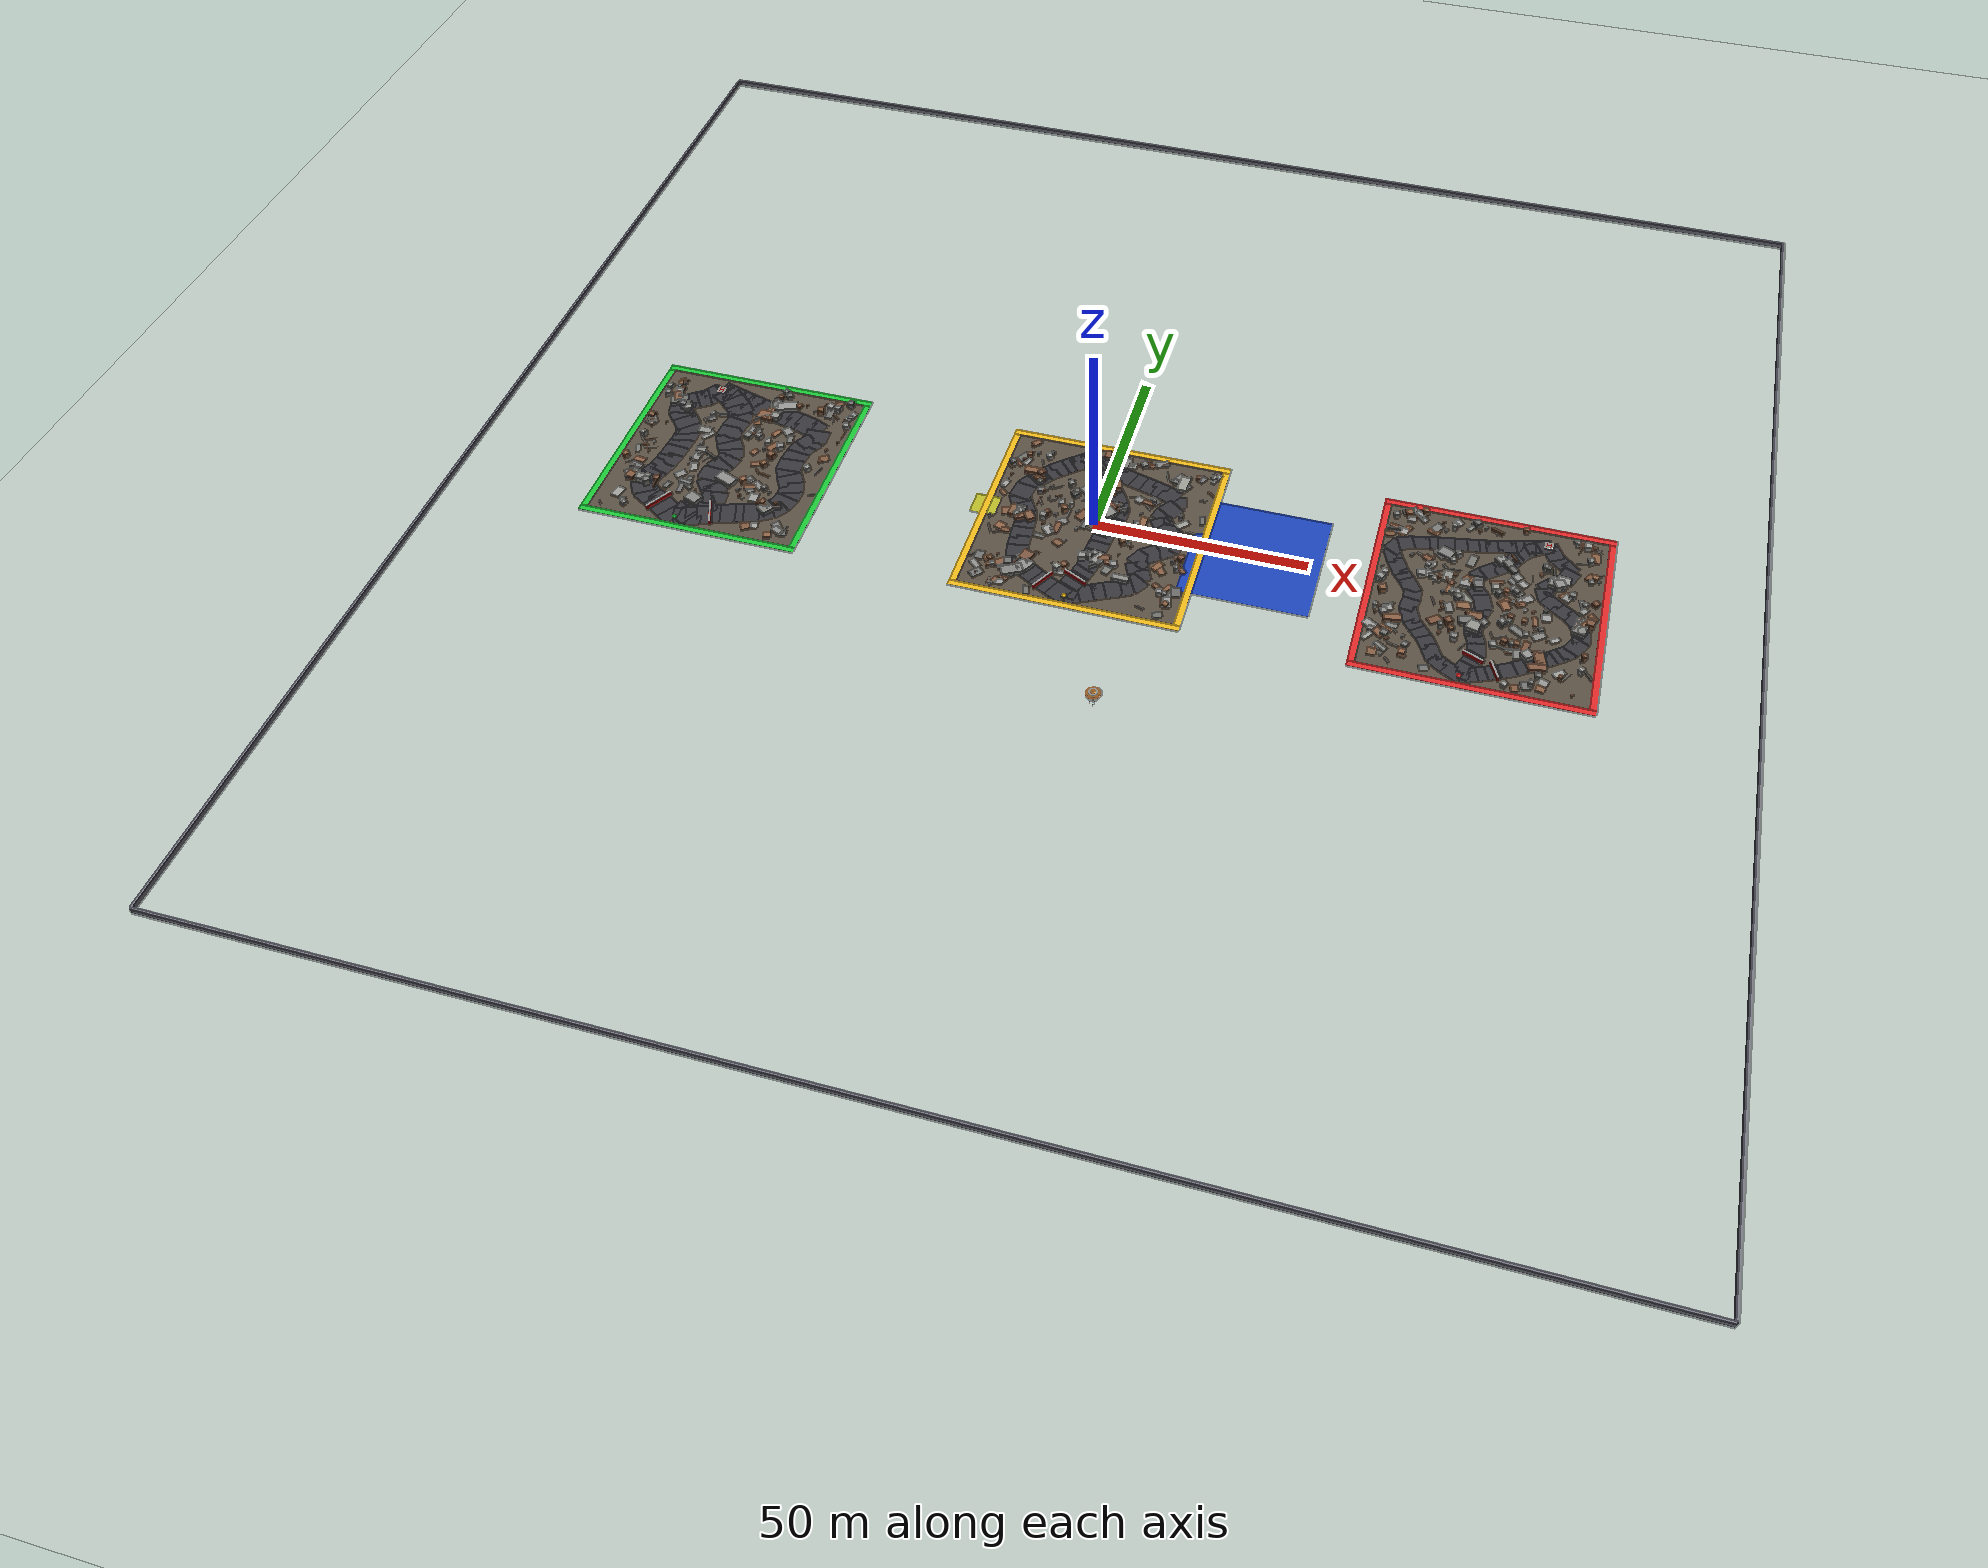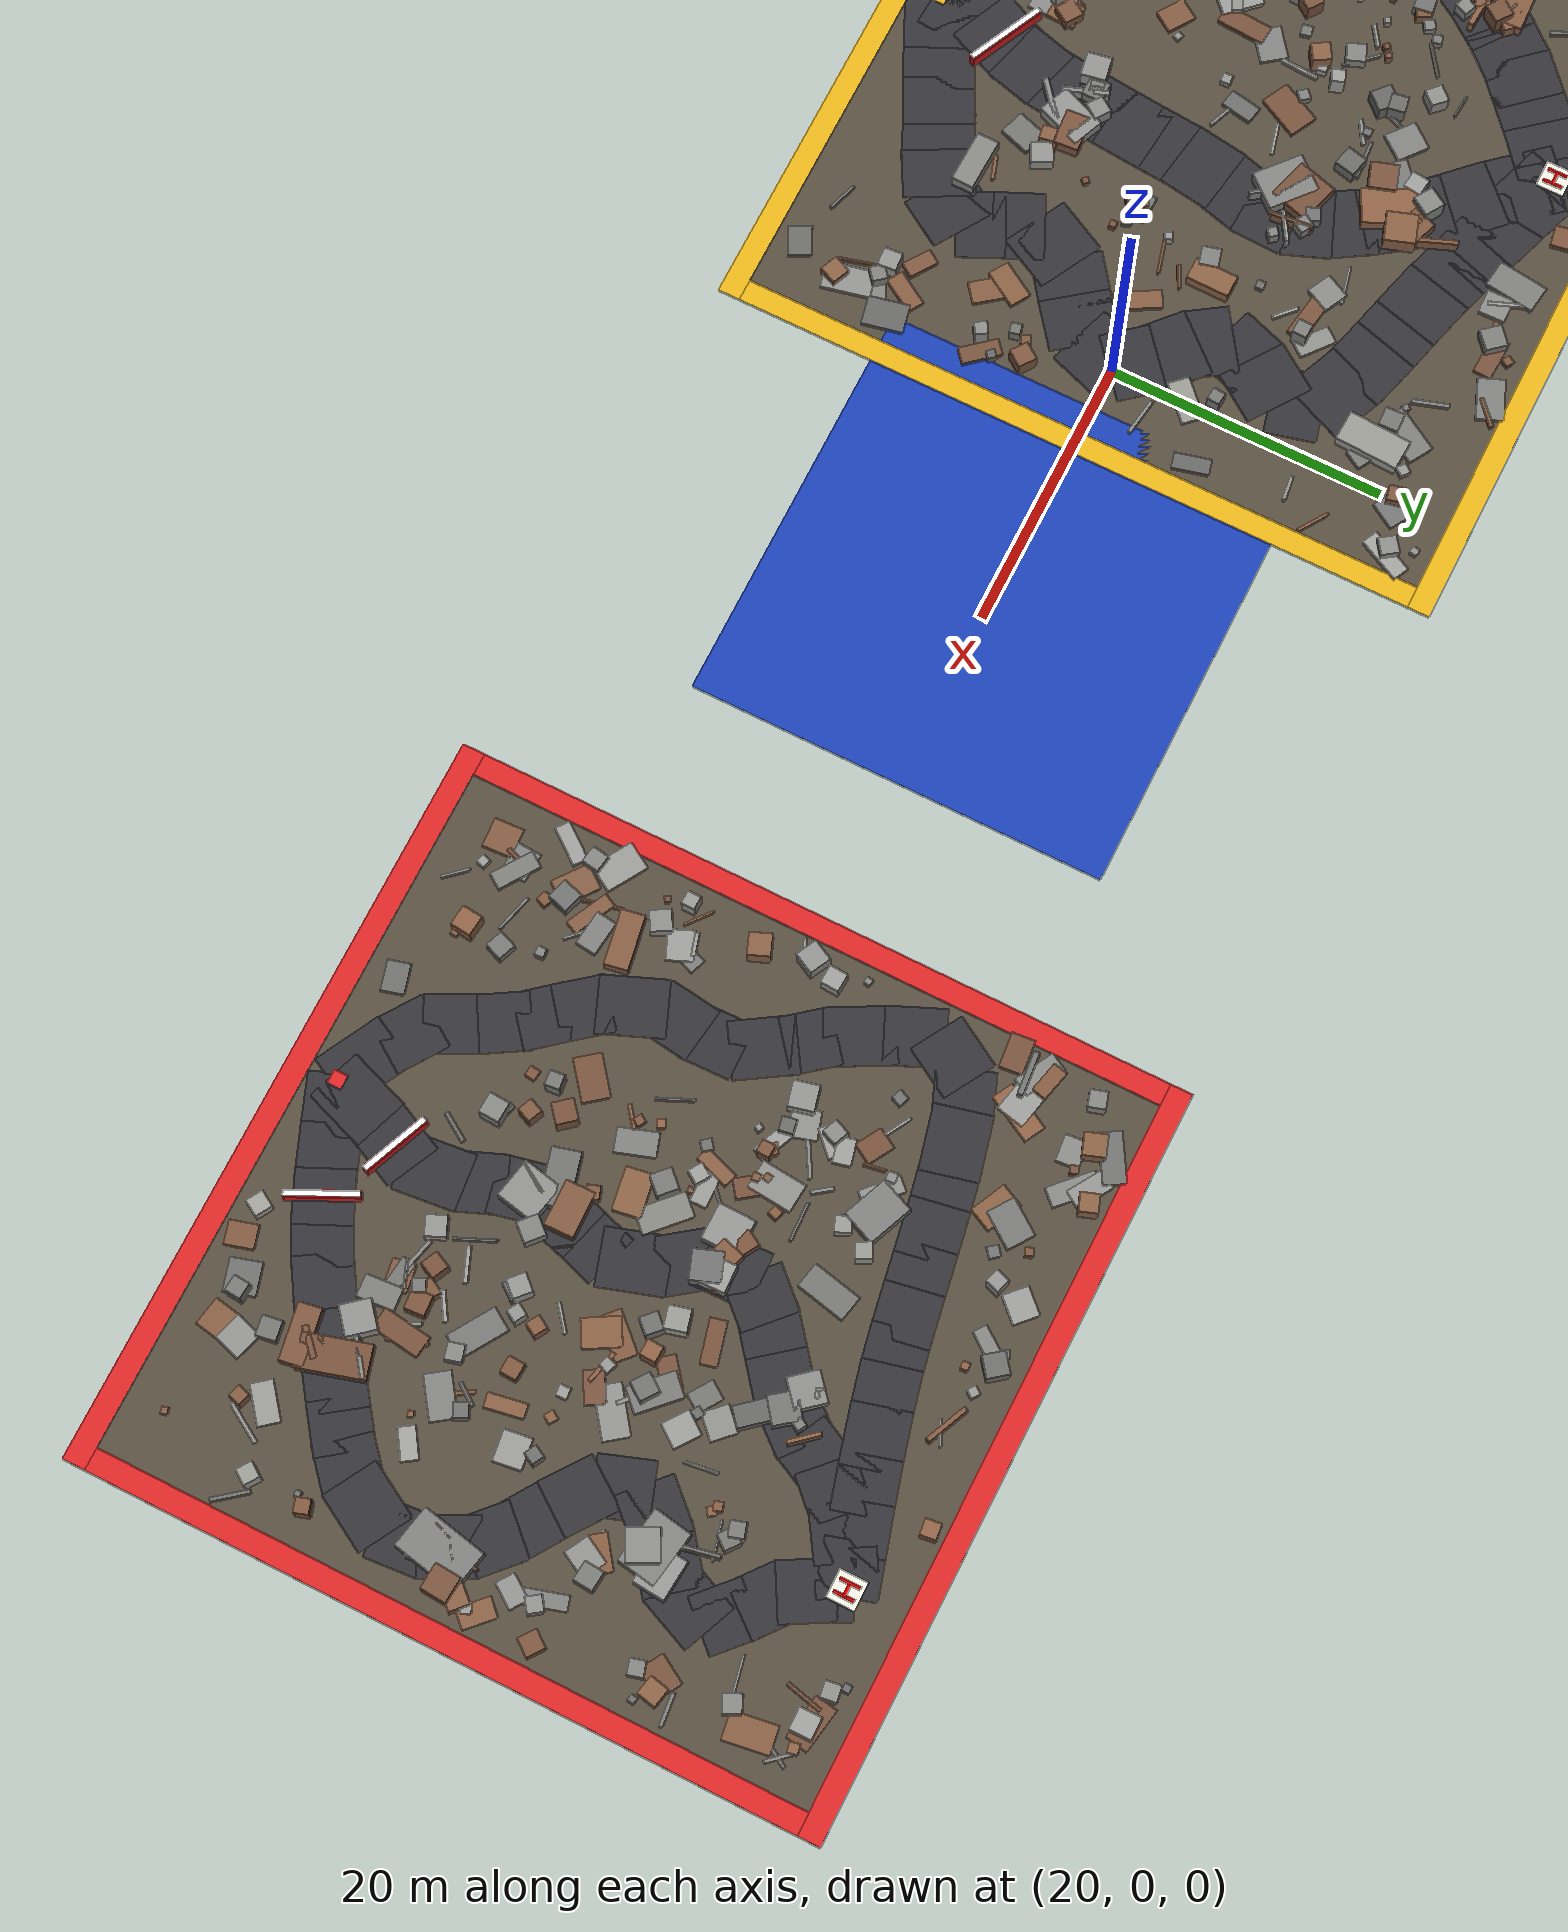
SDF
<sdf version="1.6">
 <world name="navitas_arena">
  <physics type="ode">
   <max_step_size>0.001</max_step_size>
   <real_time_factor>1</real_time_factor>
   <real_time_update_rate>1000</real_time_update_rate>
   <gravity>0 0 -9.8</gravity>
  </physics>
  <scene>
   <ambient>0.56 0.55 0.52 1.0</ambient>
   <background>0.7 0.76 0.82 1.0</background>
   <shadows>false</shadows>
  </scene>
  <light name="sun" type="directional">
   <cast_shadows>false</cast_shadows>
   <pose>0 0 120 0 -0 0</pose>
   <diffuse>0.9 0.88 0.8 1.0</diffuse>
   <specular>0.1 0.1 0.1 1</specular>
   <attenuation>
    <range>1200</range>
    <constant>0.9</constant>
    <linear>0.01</linear>
    <quadratic>0.001</quadratic>
   </attenuation>
   <direction>-0.35 0.18 -0.92</direction>
  </light>
  <model name="ground_plane">
   <static>true</static>
   <link name="link">
    <collision name="collision">
     <geometry><plane><normal>0 0 1</normal><size>400 400</size></plane></geometry>
     <surface><friction><ode><mu>0.8</mu><mu2>0.8</mu2></ode></friction></surface>
    </collision>
    <visual name="visual">
     <cast_shadows>false</cast_shadows>
     <geometry><plane><normal>0 0 1</normal><size>400 400</size></plane></geometry>
     <material>
      <script><uri>file://media/materials/scripts/gazebo.material</uri><name>Gazebo/Grey</name></script>
     </material>
    </visual>
   </link>
  </model>
  <model name="ub_N">
   <static>true</static>
   <pose>0.000 150.000 0.750 0 0 0.000</pose>
   <link name="link">
    <collision name="col"><geometry><box><size>300.000 0.600 1.500</size></box></geometry></collision>
    <visual name="vis">
     <geometry><box><size>300.000 0.600 1.500</size></box></geometry>
     <material><ambient>0.45 0.45 0.50 1</ambient><diffuse>0.45 0.45 0.50 1</diffuse></material>
    </visual>
   </link>
  </model>
  <model name="ub_S">
   <static>true</static>
   <pose>0.000 -150.000 0.750 0 0 0.000</pose>
   <link name="link">
    <collision name="col"><geometry><box><size>300.000 0.600 1.500</size></box></geometry></collision>
    <visual name="vis">
     <geometry><box><size>300.000 0.600 1.500</size></box></geometry>
     <material><ambient>0.45 0.45 0.50 1</ambient><diffuse>0.45 0.45 0.50 1</diffuse></material>
    </visual>
   </link>
  </model>
  <model name="ub_W">
   <static>true</static>
   <pose>-150.000 0.000 0.750 0 0 0.000</pose>
   <link name="link">
    <collision name="col"><geometry><box><size>0.600 300.000 1.500</size></box></geometry></collision>
    <visual name="vis">
     <geometry><box><size>0.600 300.000 1.500</size></box></geometry>
     <material><ambient>0.45 0.45 0.50 1</ambient><diffuse>0.45 0.45 0.50 1</diffuse></material>
    </visual>
   </link>
  </model>
  <model name="ub_E">
   <static>true</static>
   <pose>150.000 0.000 0.750 0 0 0.000</pose>
   <link name="link">
    <collision name="col"><geometry><box><size>0.600 300.000 1.500</size></box></geometry></collision>
    <visual name="vis">
     <geometry><box><size>0.600 300.000 1.500</size></box></geometry>
     <material><ambient>0.45 0.45 0.50 1</ambient><diffuse>0.45 0.45 0.50 1</diffuse></material>
    </visual>
   </link>
  </model>
  <model name="landing">
   <static>true</static>
   <pose>38.000 0.000 0.010 0 0 0.000</pose>
   <link name="link">
    <collision name="col"><geometry><box><size>30.000 30.000 0.020</size></box></geometry></collision>
    <visual name="vis">
     <geometry><box><size>30.000 30.000 0.020</size></box></geometry>
     <material><ambient>0.10 0.25 0.70 1</ambient><diffuse>0.10 0.25 0.70 1</diffuse></material>
    </visual>
   </link>
  </model>
  <model name="launch">
   <static>true</static>
   <pose>-26.000 0.000 0.010 0 0 0.000</pose>
   <link name="link">
    <collision name="col"><geometry><box><size>6.000 6.000 0.020</size></box></geometry></collision>
    <visual name="vis">
     <geometry><box><size>6.000 6.000 0.020</size></box></geometry>
     <material><ambient>0.70 0.70 0.15 1</ambient><diffuse>0.70 0.70 0.15 1</diffuse></material>
    </visual>
   </link>
  </model>
  <model name="gd_kolay">
   <static>true</static>
   <pose>-90.000 0.000 0.010 0 0 0.000</pose>
   <link name="link">
    <collision name="col"><geometry><box><size>50.000 50.000 0.020</size></box></geometry></collision>
    <visual name="vis">
     <geometry><box><size>50.000 50.000 0.020</size></box></geometry>
     <material><ambient>0.34 0.30 0.25 1</ambient><diffuse>0.34 0.30 0.25 1</diffuse></material>
    </visual>
   </link>
  </model>
  <model name="brd_kolay_N">
   <static>true</static>
   <pose>-90.000 25.800 0.040 0 0 0.000</pose>
   <link name="link">
    <collision name="col"><geometry><box><size>53.200 1.600 0.080</size></box></geometry></collision>
    <visual name="vis">
     <geometry><box><size>53.200 1.600 0.080</size></box></geometry>
     <material><ambient>0.10 0.75 0.20 1</ambient><diffuse>0.10 0.75 0.20 1</diffuse></material>
    </visual>
   </link>
  </model>
  <model name="brd_kolay_S">
   <static>true</static>
   <pose>-90.000 -25.800 0.040 0 0 0.000</pose>
   <link name="link">
    <collision name="col"><geometry><box><size>53.200 1.600 0.080</size></box></geometry></collision>
    <visual name="vis">
     <geometry><box><size>53.200 1.600 0.080</size></box></geometry>
     <material><ambient>0.10 0.75 0.20 1</ambient><diffuse>0.10 0.75 0.20 1</diffuse></material>
    </visual>
   </link>
  </model>
  <model name="brd_kolay_W">
   <static>true</static>
   <pose>-115.800 0.000 0.040 0 0 0.000</pose>
   <link name="link">
    <collision name="col"><geometry><box><size>1.600 50.000 0.080</size></box></geometry></collision>
    <visual name="vis">
     <geometry><box><size>1.600 50.000 0.080</size></box></geometry>
     <material><ambient>0.10 0.75 0.20 1</ambient><diffuse>0.10 0.75 0.20 1</diffuse></material>
    </visual>
   </link>
  </model>
  <model name="brd_kolay_E">
   <static>true</static>
   <pose>-64.200 0.000 0.040 0 0 0.000</pose>
   <link name="link">
    <collision name="col"><geometry><box><size>1.600 50.000 0.080</size></box></geometry></collision>
    <visual name="vis">
     <geometry><box><size>1.600 50.000 0.080</size></box></geometry>
     <material><ambient>0.10 0.75 0.20 1</ambient><diffuse>0.10 0.75 0.20 1</diffuse></material>
    </visual>
   </link>
  </model>
  <model name="road_kolay_1_0">
   <static>true</static>
   <pose>-95.431 -22.070 0.040 0 0 2.572</pose>
   <link name="link">
    <collision name="col"><geometry><box><size>4.349 6.000 0.020</size></box></geometry></collision>
    <visual name="vis">
     <geometry><box><size>4.349 6.000 0.020</size></box></geometry>
     <material><ambient>0.20 0.20 0.22 1</ambient><diffuse>0.20 0.20 0.22 1</diffuse></material>
    </visual>
   </link>
  </model>
  <model name="road_kolay_1_1">
   <static>true</static>
   <pose>-98.136 -20.320 0.040 0 0 2.562</pose>
   <link name="link">
    <collision name="col"><geometry><box><size>3.894 6.000 0.020</size></box></geometry></collision>
    <visual name="vis">
     <geometry><box><size>3.894 6.000 0.020</size></box></geometry>
     <material><ambient>0.20 0.20 0.22 1</ambient><diffuse>0.20 0.20 0.22 1</diffuse></material>
    </visual>
   </link>
  </model>
  <model name="road_kolay_1_2">
   <static>true</static>
   <pose>-100.596 -18.833 0.040 0 0 2.637</pose>
   <link name="link">
    <collision name="col"><geometry><box><size>3.659 6.000 0.020</size></box></geometry></collision>
    <visual name="vis">
     <geometry><box><size>3.659 6.000 0.020</size></box></geometry>
     <material><ambient>0.20 0.20 0.22 1</ambient><diffuse>0.20 0.20 0.22 1</diffuse></material>
    </visual>
   </link>
  </model>
  <model name="road_kolay_1_3">
   <static>true</static>
   <pose>-103.075 -17.444 0.040 0 0 2.625</pose>
   <link name="link">
    <collision name="col"><geometry><box><size>3.823 6.000 0.020</size></box></geometry></collision>
    <visual name="vis">
     <geometry><box><size>3.823 6.000 0.020</size></box></geometry>
     <material><ambient>0.20 0.20 0.22 1</ambient><diffuse>0.20 0.20 0.22 1</diffuse></material>
    </visual>
   </link>
  </model>
  <model name="road_kolay_1_4">
   <static>true</static>
   <pose>-105.210 -15.350 0.040 0 0 2.133</pose>
   <link name="link">
    <collision name="col"><geometry><box><size>4.143 6.000 0.020</size></box></geometry></collision>
    <visual name="vis">
     <geometry><box><size>4.143 6.000 0.020</size></box></geometry>
     <material><ambient>0.20 0.20 0.22 1</ambient><diffuse>0.20 0.20 0.22 1</diffuse></material>
    </visual>
   </link>
  </model>
  <model name="road_kolay_1_5">
   <static>true</static>
   <pose>-105.721 -12.817 0.040 0 0 1.276</pose>
   <link name="link">
    <collision name="col"><geometry><box><size>3.327 6.000 0.020</size></box></geometry></collision>
    <visual name="vis">
     <geometry><box><size>3.327 6.000 0.020</size></box></geometry>
     <material><ambient>0.20 0.20 0.22 1</ambient><diffuse>0.20 0.20 0.22 1</diffuse></material>
    </visual>
   </link>
  </model>
  <model name="road_kolay_1_6">
   <static>true</static>
   <pose>-104.809 -10.426 0.040 0 0 1.144</pose>
   <link name="link">
    <collision name="col"><geometry><box><size>3.603 6.000 0.020</size></box></geometry></collision>
    <visual name="vis">
     <geometry><box><size>3.603 6.000 0.020</size></box></geometry>
     <material><ambient>0.20 0.20 0.22 1</ambient><diffuse>0.20 0.20 0.22 1</diffuse></material>
    </visual>
   </link>
  </model>
  <model name="road_kolay_1_7">
   <static>true</static>
   <pose>-103.930 -7.898 0.040 0 0 1.329</pose>
   <link name="link">
    <collision name="col"><geometry><box><size>3.574 6.000 0.020</size></box></geometry></collision>
    <visual name="vis">
     <geometry><box><size>3.574 6.000 0.020</size></box></geometry>
     <material><ambient>0.20 0.20 0.22 1</ambient><diffuse>0.20 0.20 0.22 1</diffuse></material>
    </visual>
   </link>
  </model>
  <model name="road_kolay_1_8">
   <static>true</static>
   <pose>-103.414 -5.200 0.040 0 0 1.432</pose>
   <link name="link">
    <collision name="col"><geometry><box><size>3.727 6.000 0.020</size></box></geometry></collision>
    <visual name="vis">
     <geometry><box><size>3.727 6.000 0.020</size></box></geometry>
     <material><ambient>0.20 0.20 0.22 1</ambient><diffuse>0.20 0.20 0.22 1</diffuse></material>
    </visual>
   </link>
  </model>
  <model name="road_kolay_1_9">
   <static>true</static>
   <pose>-103.110 -2.400 0.040 0 0 1.493</pose>
   <link name="link">
    <collision name="col"><geometry><box><size>3.708 6.000 0.020</size></box></geometry></collision>
    <visual name="vis">
     <geometry><box><size>3.708 6.000 0.020</size></box></geometry>
     <material><ambient>0.20 0.20 0.22 1</ambient><diffuse>0.20 0.20 0.22 1</diffuse></material>
    </visual>
   </link>
  </model>
  <model name="road_kolay_1_10">
   <static>true</static>
   <pose>-102.878 0.400 0.040 0 0 1.483</pose>
   <link name="link">
    <collision name="col"><geometry><box><size>3.711 6.000 0.020</size></box></geometry></collision>
    <visual name="vis">
     <geometry><box><size>3.711 6.000 0.020</size></box></geometry>
     <material><ambient>0.20 0.20 0.22 1</ambient><diffuse>0.20 0.20 0.22 1</diffuse></material>
    </visual>
   </link>
  </model>
  <model name="road_kolay_1_11">
   <static>true</static>
   <pose>-102.781 3.200 0.040 0 0 1.590</pose>
   <link name="link">
    <collision name="col"><geometry><box><size>3.701 6.000 0.020</size></box></geometry></collision>
    <visual name="vis">
     <geometry><box><size>3.701 6.000 0.020</size></box></geometry>
     <material><ambient>0.20 0.20 0.22 1</ambient><diffuse>0.20 0.20 0.22 1</diffuse></material>
    </visual>
   </link>
  </model>
  <model name="road_kolay_1_12">
   <static>true</static>
   <pose>-103.290 5.811 0.040 0 0 1.950</pose>
   <link name="link">
    <collision name="col"><geometry><box><size>3.507 6.000 0.020</size></box></geometry></collision>
    <visual name="vis">
     <geometry><box><size>3.507 6.000 0.020</size></box></geometry>
     <material><ambient>0.20 0.20 0.22 1</ambient><diffuse>0.20 0.20 0.22 1</diffuse></material>
    </visual>
   </link>
  </model>
  <model name="road_kolay_1_13">
   <static>true</static>
   <pose>-104.719 8.077 0.040 0 0 2.302</pose>
   <link name="link">
    <collision name="col"><geometry><box><size>3.734 6.000 0.020</size></box></geometry></collision>
    <visual name="vis">
     <geometry><box><size>3.734 6.000 0.020</size></box></geometry>
     <material><ambient>0.20 0.20 0.22 1</ambient><diffuse>0.20 0.20 0.22 1</diffuse></material>
    </visual>
   </link>
  </model>
  <model name="road_kolay_1_14">
   <static>true</static>
   <pose>-106.637 10.157 0.040 0 0 2.329</pose>
   <link name="link">
    <collision name="col"><geometry><box><size>3.725 6.000 0.020</size></box></geometry></collision>
    <visual name="vis">
     <geometry><box><size>3.725 6.000 0.020</size></box></geometry>
     <material><ambient>0.20 0.20 0.22 1</ambient><diffuse>0.20 0.20 0.22 1</diffuse></material>
    </visual>
   </link>
  </model>
  <model name="road_kolay_1_15">
   <static>true</static>
   <pose>-107.834 12.629 0.040 0 0 1.725</pose>
   <link name="link">
    <collision name="col"><geometry><box><size>3.829 6.000 0.020</size></box></geometry></collision>
    <visual name="vis">
     <geometry><box><size>3.829 6.000 0.020</size></box></geometry>
     <material><ambient>0.20 0.20 0.22 1</ambient><diffuse>0.20 0.20 0.22 1</diffuse></material>
    </visual>
   </link>
  </model>
  <model name="road_kolay_1_16">
   <static>true</static>
   <pose>-106.818 14.984 0.040 0 0 0.632</pose>
   <link name="link">
    <collision name="col"><geometry><box><size>3.976 6.000 0.020</size></box></geometry></collision>
    <visual name="vis">
     <geometry><box><size>3.976 6.000 0.020</size></box></geometry>
     <material><ambient>0.20 0.20 0.22 1</ambient><diffuse>0.20 0.20 0.22 1</diffuse></material>
    </visual>
   </link>
  </model>
  <model name="road_kolay_1_17">
   <static>true</static>
   <pose>-104.358 16.696 0.040 0 0 0.583</pose>
   <link name="link">
    <collision name="col"><geometry><box><size>3.820 6.000 0.020</size></box></geometry></collision>
    <visual name="vis">
     <geometry><box><size>3.820 6.000 0.020</size></box></geometry>
     <material><ambient>0.20 0.20 0.22 1</ambient><diffuse>0.20 0.20 0.22 1</diffuse></material>
    </visual>
   </link>
  </model>
  <model name="road_kolay_1_18">
   <static>true</static>
   <pose>-102.217 18.815 0.040 0 0 0.959</pose>
   <link name="link">
    <collision name="col"><geometry><box><size>4.113 6.000 0.020</size></box></geometry></collision>
    <visual name="vis">
     <geometry><box><size>4.113 6.000 0.020</size></box></geometry>
     <material><ambient>0.20 0.20 0.22 1</ambient><diffuse>0.20 0.20 0.22 1</diffuse></material>
    </visual>
   </link>
  </model>
  <model name="road_kolay_1_19">
   <static>true</static>
   <pose>-101.046 20.565 0.040 0 0 1.054</pose>
   <link name="link">
    <collision name="col"><geometry><box><size>1.901 6.000 0.020</size></box></geometry></collision>
    <visual name="vis">
     <geometry><box><size>1.901 6.000 0.020</size></box></geometry>
     <material><ambient>0.20 0.20 0.22 1</ambient><diffuse>0.20 0.20 0.22 1</diffuse></material>
    </visual>
   </link>
  </model>
  <model name="road_kolay_2_0">
   <static>true</static>
   <pose>-93.084 -21.250 0.040 0 0 1.098</pose>
   <link name="link">
    <collision name="col"><geometry><box><size>4.831 6.000 0.020</size></box></geometry></collision>
    <visual name="vis">
     <geometry><box><size>4.831 6.000 0.020</size></box></geometry>
     <material><ambient>0.20 0.20 0.22 1</ambient><diffuse>0.20 0.20 0.22 1</diffuse></material>
    </visual>
   </link>
  </model>
  <model name="road_kolay_2_1">
   <static>true</static>
   <pose>-91.062 -18.696 0.040 0 0 0.620</pose>
   <link name="link">
    <collision name="col"><geometry><box><size>3.667 6.000 0.020</size></box></geometry></collision>
    <visual name="vis">
     <geometry><box><size>3.667 6.000 0.020</size></box></geometry>
     <material><ambient>0.20 0.20 0.22 1</ambient><diffuse>0.20 0.20 0.22 1</diffuse></material>
    </visual>
   </link>
  </model>
  <model name="road_kolay_2_2">
   <static>true</static>
   <pose>-88.757 -16.984 0.040 0 0 0.656</pose>
   <link name="link">
    <collision name="col"><geometry><box><size>3.876 6.000 0.020</size></box></geometry></collision>
    <visual name="vis">
     <geometry><box><size>3.876 6.000 0.020</size></box></geometry>
     <material><ambient>0.20 0.20 0.22 1</ambient><diffuse>0.20 0.20 0.22 1</diffuse></material>
    </visual>
   </link>
  </model>
  <model name="road_kolay_2_3">
   <static>true</static>
   <pose>-87.777 -14.629 0.040 0 0 1.707</pose>
   <link name="link">
    <collision name="col"><geometry><box><size>3.821 6.000 0.020</size></box></geometry></collision>
    <visual name="vis">
     <geometry><box><size>3.821 6.000 0.020</size></box></geometry>
     <material><ambient>0.20 0.20 0.22 1</ambient><diffuse>0.20 0.20 0.22 1</diffuse></material>
    </visual>
   </link>
  </model>
  <model name="road_kolay_2_4">
   <static>true</static>
   <pose>-88.890 -12.157 0.040 0 0 2.299</pose>
   <link name="link">
    <collision name="col"><geometry><box><size>3.648 6.000 0.020</size></box></geometry></collision>
    <visual name="vis">
     <geometry><box><size>3.648 6.000 0.020</size></box></geometry>
     <material><ambient>0.20 0.20 0.22 1</ambient><diffuse>0.20 0.20 0.22 1</diffuse></material>
    </visual>
   </link>
  </model>
  <model name="road_kolay_2_5">
   <static>true</static>
   <pose>-90.622 -10.077 0.040 0 0 2.230</pose>
   <link name="link">
    <collision name="col"><geometry><box><size>3.569 6.000 0.020</size></box></geometry></collision>
    <visual name="vis">
     <geometry><box><size>3.569 6.000 0.020</size></box></geometry>
     <material><ambient>0.20 0.20 0.22 1</ambient><diffuse>0.20 0.20 0.22 1</diffuse></material>
    </visual>
   </link>
  </model>
  <model name="road_kolay_2_6">
   <static>true</static>
   <pose>-91.360 -7.344 0.040 0 0 1.524</pose>
   <link name="link">
    <collision name="col"><geometry><box><size>4.259 6.000 0.020</size></box></geometry></collision>
    <visual name="vis">
     <geometry><box><size>4.259 6.000 0.020</size></box></geometry>
     <material><ambient>0.20 0.20 0.22 1</ambient><diffuse>0.20 0.20 0.22 1</diffuse></material>
    </visual>
   </link>
  </model>
  <model name="road_kolay_2_7">
   <static>true</static>
   <pose>-90.614 -4.500 0.040 0 0 1.052</pose>
   <link name="link">
    <collision name="col"><geometry><box><size>3.588 6.000 0.020</size></box></geometry></collision>
    <visual name="vis">
     <geometry><box><size>3.588 6.000 0.020</size></box></geometry>
     <material><ambient>0.20 0.20 0.22 1</ambient><diffuse>0.20 0.20 0.22 1</diffuse></material>
    </visual>
   </link>
  </model>
  <model name="road_kolay_2_8">
   <static>true</static>
   <pose>-89.621 -2.167 0.040 0 0 1.299</pose>
   <link name="link">
    <collision name="col"><geometry><box><size>3.323 6.000 0.020</size></box></geometry></collision>
    <visual name="vis">
     <geometry><box><size>3.323 6.000 0.020</size></box></geometry>
     <material><ambient>0.20 0.20 0.22 1</ambient><diffuse>0.20 0.20 0.22 1</diffuse></material>
    </visual>
   </link>
  </model>
  <model name="road_kolay_2_9">
   <static>true</static>
   <pose>-89.746 0.167 0.040 0 0 1.939</pose>
   <link name="link">
    <collision name="col"><geometry><box><size>3.401 6.000 0.020</size></box></geometry></collision>
    <visual name="vis">
     <geometry><box><size>3.401 6.000 0.020</size></box></geometry>
     <material><ambient>0.20 0.20 0.22 1</ambient><diffuse>0.20 0.20 0.22 1</diffuse></material>
    </visual>
   </link>
  </model>
  <model name="road_kolay_2_10">
   <static>true</static>
   <pose>-90.989 2.500 0.040 0 0 2.167</pose>
   <link name="link">
    <collision name="col"><geometry><box><size>3.720 6.000 0.020</size></box></geometry></collision>
    <visual name="vis">
     <geometry><box><size>3.720 6.000 0.020</size></box></geometry>
     <material><ambient>0.20 0.20 0.22 1</ambient><diffuse>0.20 0.20 0.22 1</diffuse></material>
    </visual>
   </link>
  </model>
  <model name="road_kolay_2_11">
   <static>true</static>
   <pose>-92.349 4.833 0.040 0 0 2.024</pose>
   <link name="link">
    <collision name="col"><geometry><box><size>3.495 6.000 0.020</size></box></geometry></collision>
    <visual name="vis">
     <geometry><box><size>3.495 6.000 0.020</size></box></geometry>
     <material><ambient>0.20 0.20 0.22 1</ambient><diffuse>0.20 0.20 0.22 1</diffuse></material>
    </visual>
   </link>
  </model>
  <model name="road_kolay_2_12">
   <static>true</static>
   <pose>-92.888 7.460 0.040 0 0 1.551</pose>
   <link name="link">
    <collision name="col"><geometry><box><size>3.821 6.000 0.020</size></box></geometry></collision>
    <visual name="vis">
     <geometry><box><size>3.821 6.000 0.020</size></box></geometry>
     <material><ambient>0.20 0.20 0.22 1</ambient><diffuse>0.20 0.20 0.22 1</diffuse></material>
    </visual>
   </link>
  </model>
  <model name="road_kolay_2_13">
   <static>true</static>
   <pose>-92.635 10.340 0.040 0 0 1.414</pose>
   <link name="link">
    <collision name="col"><geometry><box><size>3.775 6.000 0.020</size></box></geometry></collision>
    <visual name="vis">
     <geometry><box><size>3.775 6.000 0.020</size></box></geometry>
     <material><ambient>0.20 0.20 0.22 1</ambient><diffuse>0.20 0.20 0.22 1</diffuse></material>
    </visual>
   </link>
  </model>
  <model name="road_kolay_2_14">
   <static>true</static>
   <pose>-92.737 13.042 0.040 0 0 1.820</pose>
   <link name="link">
    <collision name="col"><geometry><box><size>3.546 6.000 0.020</size></box></geometry></collision>
    <visual name="vis">
     <geometry><box><size>3.546 6.000 0.020</size></box></geometry>
     <material><ambient>0.20 0.20 0.22 1</ambient><diffuse>0.20 0.20 0.22 1</diffuse></material>
    </visual>
   </link>
  </model>
  <model name="road_kolay_2_15">
   <static>true</static>
   <pose>-93.978 15.414 0.040 0 0 2.269</pose>
   <link name="link">
    <collision name="col"><geometry><box><size>3.744 6.000 0.020</size></box></geometry></collision>
    <visual name="vis">
     <geometry><box><size>3.744 6.000 0.020</size></box></geometry>
     <material><ambient>0.20 0.20 0.22 1</ambient><diffuse>0.20 0.20 0.22 1</diffuse></material>
    </visual>
   </link>
  </model>
  <model name="road_kolay_2_16">
   <static>true</static>
   <pose>-96.030 17.516 0.040 0 0 2.415</pose>
   <link name="link">
    <collision name="col"><geometry><box><size>3.945 6.000 0.020</size></box></geometry></collision>
    <visual name="vis">
     <geometry><box><size>3.945 6.000 0.020</size></box></geometry>
     <material><ambient>0.20 0.20 0.22 1</ambient><diffuse>0.20 0.20 0.22 1</diffuse></material>
    </visual>
   </link>
  </model>
  <model name="road_kolay_2_17">
   <static>true</static>
   <pose>-98.530 19.461 0.040 0 0 2.541</pose>
   <link name="link">
    <collision name="col"><geometry><box><size>4.203 6.000 0.020</size></box></geometry></collision>
    <visual name="vis">
     <geometry><box><size>4.203 6.000 0.020</size></box></geometry>
     <material><ambient>0.20 0.20 0.22 1</ambient><diffuse>0.20 0.20 0.22 1</diffuse></material>
    </visual>
   </link>
  </model>
  <model name="road_kolay_2_18">
   <static>true</static>
   <pose>-100.345 20.697 0.040 0 0 2.553</pose>
   <link name="link">
    <collision name="col"><geometry><box><size>1.990 6.000 0.020</size></box></geometry></collision>
    <visual name="vis">
     <geometry><box><size>1.990 6.000 0.020</size></box></geometry>
     <material><ambient>0.20 0.20 0.22 1</ambient><diffuse>0.20 0.20 0.22 1</diffuse></material>
    </visual>
   </link>
  </model>
  <model name="road_kolay_3_0">
   <static>true</static>
   <pose>-92.677 -22.494 0.040 0 0 0.371</pose>
   <link name="link">
    <collision name="col"><geometry><box><size>3.694 6.000 0.020</size></box></geometry></collision>
    <visual name="vis">
     <geometry><box><size>3.694 6.000 0.020</size></box></geometry>
     <material><ambient>0.20 0.20 0.22 1</ambient><diffuse>0.20 0.20 0.22 1</diffuse></material>
    </visual>
   </link>
  </model>
  <model name="road_kolay_3_1">
   <static>true</static>
   <pose>-90.156 -21.514 0.040 0 0 0.371</pose>
   <link name="link">
    <collision name="col"><geometry><box><size>3.516 6.000 0.020</size></box></geometry></collision>
    <visual name="vis">
     <geometry><box><size>3.516 6.000 0.020</size></box></geometry>
     <material><ambient>0.20 0.20 0.22 1</ambient><diffuse>0.20 0.20 0.22 1</diffuse></material>
    </visual>
   </link>
  </model>
  <model name="road_kolay_3_2">
   <static>true</static>
   <pose>-87.615 -20.524 0.040 0 0 0.372</pose>
   <link name="link">
    <collision name="col"><geometry><box><size>3.738 6.000 0.020</size></box></geometry></collision>
    <visual name="vis">
     <geometry><box><size>3.738 6.000 0.020</size></box></geometry>
     <material><ambient>0.20 0.20 0.22 1</ambient><diffuse>0.20 0.20 0.22 1</diffuse></material>
    </visual>
   </link>
  </model>
  <model name="road_kolay_3_3">
   <static>true</static>
   <pose>-85.096 -19.556 0.040 0 0 0.363</pose>
   <link name="link">
    <collision name="col"><geometry><box><size>3.459 6.000 0.020</size></box></geometry></collision>
    <visual name="vis">
     <geometry><box><size>3.459 6.000 0.020</size></box></geometry>
     <material><ambient>0.20 0.20 0.22 1</ambient><diffuse>0.20 0.20 0.22 1</diffuse></material>
    </visual>
   </link>
  </model>
  <model name="road_kolay_3_4">
   <static>true</static>
   <pose>-82.669 -18.702 0.040 0 0 0.314</pose>
   <link name="link">
    <collision name="col"><geometry><box><size>3.488 6.000 0.020</size></box></geometry></collision>
    <visual name="vis">
     <geometry><box><size>3.488 6.000 0.020</size></box></geometry>
     <material><ambient>0.20 0.20 0.22 1</ambient><diffuse>0.20 0.20 0.22 1</diffuse></material>
    </visual>
   </link>
  </model>
  <model name="road_kolay_3_5">
   <static>true</static>
   <pose>-80.135 -17.886 0.040 0 0 0.309</pose>
   <link name="link">
    <collision name="col"><geometry><box><size>3.637 6.000 0.020</size></box></geometry></collision>
    <visual name="vis">
     <geometry><box><size>3.637 6.000 0.020</size></box></geometry>
     <material><ambient>0.20 0.20 0.22 1</ambient><diffuse>0.20 0.20 0.22 1</diffuse></material>
    </visual>
   </link>
  </model>
  <model name="road_kolay_3_6">
   <static>true</static>
   <pose>-77.595 -17.017 0.040 0 0 0.350</pose>
   <link name="link">
    <collision name="col"><geometry><box><size>3.533 6.000 0.020</size></box></geometry></collision>
    <visual name="vis">
     <geometry><box><size>3.533 6.000 0.020</size></box></geometry>
     <material><ambient>0.20 0.20 0.22 1</ambient><diffuse>0.20 0.20 0.22 1</diffuse></material>
    </visual>
   </link>
  </model>
  <model name="road_kolay_3_7">
   <static>true</static>
   <pose>-74.937 -15.783 0.040 0 0 0.503</pose>
   <link name="link">
    <collision name="col"><geometry><box><size>4.146 6.000 0.020</size></box></geometry></collision>
    <visual name="vis">
     <geometry><box><size>4.146 6.000 0.020</size></box></geometry>
     <material><ambient>0.20 0.20 0.22 1</ambient><diffuse>0.20 0.20 0.22 1</diffuse></material>
    </visual>
   </link>
  </model>
  <model name="road_kolay_3_8">
   <static>true</static>
   <pose>-72.693 -13.926 0.040 0 0 0.917</pose>
   <link name="link">
    <collision name="col"><geometry><box><size>3.606 6.000 0.020</size></box></geometry></collision>
    <visual name="vis">
     <geometry><box><size>3.606 6.000 0.020</size></box></geometry>
     <material><ambient>0.20 0.20 0.22 1</ambient><diffuse>0.20 0.20 0.22 1</diffuse></material>
    </visual>
   </link>
  </model>
  <model name="road_kolay_3_9">
   <static>true</static>
   <pose>-71.559 -11.639 0.040 0 0 1.320</pose>
   <link name="link">
    <collision name="col"><geometry><box><size>3.404 6.000 0.020</size></box></geometry></collision>
    <visual name="vis">
     <geometry><box><size>3.404 6.000 0.020</size></box></geometry>
     <material><ambient>0.20 0.20 0.22 1</ambient><diffuse>0.20 0.20 0.22 1</diffuse></material>
    </visual>
   </link>
  </model>
  <model name="road_kolay_3_10">
   <static>true</static>
   <pose>-71.249 -9.213 0.040 0 0 1.572</pose>
   <link name="link">
    <collision name="col"><geometry><box><size>3.326 6.000 0.020</size></box></geometry></collision>
    <visual name="vis">
     <geometry><box><size>3.326 6.000 0.020</size></box></geometry>
     <material><ambient>0.20 0.20 0.22 1</ambient><diffuse>0.20 0.20 0.22 1</diffuse></material>
    </visual>
   </link>
  </model>
  <model name="road_kolay_3_11">
   <static>true</static>
   <pose>-71.670 -6.833 0.040 0 0 1.916</pose>
   <link name="link">
    <collision name="col"><geometry><box><size>3.380 6.000 0.020</size></box></geometry></collision>
    <visual name="vis">
     <geometry><box><size>3.380 6.000 0.020</size></box></geometry>
     <material><ambient>0.20 0.20 0.22 1</ambient><diffuse>0.20 0.20 0.22 1</diffuse></material>
    </visual>
   </link>
  </model>
  <model name="road_kolay_3_12">
   <static>true</static>
   <pose>-72.821 -4.500 0.040 0 0 2.131</pose>
   <link name="link">
    <collision name="col"><geometry><box><size>3.654 6.000 0.020</size></box></geometry></collision>
    <visual name="vis">
     <geometry><box><size>3.654 6.000 0.020</size></box></geometry>
     <material><ambient>0.20 0.20 0.22 1</ambient><diffuse>0.20 0.20 0.22 1</diffuse></material>
    </visual>
   </link>
  </model>
  <model name="road_kolay_3_13">
   <static>true</static>
   <pose>-74.075 -2.167 0.040 0 0 1.992</pose>
   <link name="link">
    <collision name="col"><geometry><box><size>3.457 6.000 0.020</size></box></geometry></collision>
    <visual name="vis">
     <geometry><box><size>3.457 6.000 0.020</size></box></geometry>
     <material><ambient>0.20 0.20 0.22 1</ambient><diffuse>0.20 0.20 0.22 1</diffuse></material>
    </visual>
   </link>
  </model>
  <model name="road_kolay_3_14">
   <static>true</static>
   <pose>-74.682 0.400 0.040 0 0 1.631</pose>
   <link name="link">
    <collision name="col"><geometry><box><size>3.705 6.000 0.020</size></box></geometry></collision>
    <visual name="vis">
     <geometry><box><size>3.705 6.000 0.020</size></box></geometry>
     <material><ambient>0.20 0.20 0.22 1</ambient><diffuse>0.20 0.20 0.22 1</diffuse></material>
    </visual>
   </link>
  </model>
  <model name="road_kolay_3_15">
   <static>true</static>
   <pose>-74.588 3.200 0.040 0 0 1.445</pose>
   <link name="link">
    <collision name="col"><geometry><box><size>3.722 6.000 0.020</size></box></geometry></collision>
    <visual name="vis">
     <geometry><box><size>3.722 6.000 0.020</size></box></geometry>
     <material><ambient>0.20 0.20 0.22 1</ambient><diffuse>0.20 0.20 0.22 1</diffuse></material>
    </visual>
   </link>
  </model>
  <model name="road_kolay_3_16">
   <static>true</static>
   <pose>-74.086 5.898 0.040 0 0 1.326</pose>
   <link name="link">
    <collision name="col"><geometry><box><size>3.575 6.000 0.020</size></box></geometry></collision>
    <visual name="vis">
     <geometry><box><size>3.575 6.000 0.020</size></box></geometry>
     <material><ambient>0.20 0.20 0.22 1</ambient><diffuse>0.20 0.20 0.22 1</diffuse></material>
    </visual>
   </link>
  </model>
  <model name="road_kolay_3_17">
   <static>true</static>
   <pose>-73.017 8.426 0.040 0 0 1.026</pose>
   <link name="link">
    <collision name="col"><geometry><box><size>3.776 6.000 0.020</size></box></geometry></collision>
    <visual name="vis">
     <geometry><box><size>3.776 6.000 0.020</size></box></geometry>
     <material><ambient>0.20 0.20 0.22 1</ambient><diffuse>0.20 0.20 0.22 1</diffuse></material>
    </visual>
   </link>
  </model>
  <model name="road_kolay_3_18">
   <static>true</static>
   <pose>-72.361 11.328 0.040 0 0 1.624</pose>
   <link name="link">
    <collision name="col"><geometry><box><size>4.248 6.000 0.020</size></box></geometry></collision>
    <visual name="vis">
     <geometry><box><size>4.248 6.000 0.020</size></box></geometry>
     <material><ambient>0.20 0.20 0.22 1</ambient><diffuse>0.20 0.20 0.22 1</diffuse></material>
    </visual>
   </link>
  </model>
  <model name="road_kolay_3_19">
   <static>true</static>
   <pose>-73.637 13.574 0.040 0 0 2.691</pose>
   <link name="link">
    <collision name="col"><geometry><box><size>3.538 6.000 0.020</size></box></geometry></collision>
    <visual name="vis">
     <geometry><box><size>3.538 6.000 0.020</size></box></geometry>
     <material><ambient>0.20 0.20 0.22 1</ambient><diffuse>0.20 0.20 0.22 1</diffuse></material>
    </visual>
   </link>
  </model>
  <model name="road_kolay_3_20">
   <static>true</static>
   <pose>-76.608 14.652 0.040 0 0 2.866</pose>
   <link name="link">
    <collision name="col"><geometry><box><size>4.607 6.000 0.020</size></box></geometry></collision>
    <visual name="vis">
     <geometry><box><size>4.607 6.000 0.020</size></box></geometry>
     <material><ambient>0.20 0.20 0.22 1</ambient><diffuse>0.20 0.20 0.22 1</diffuse></material>
    </visual>
   </link>
  </model>
  <model name="road_kolay_3_21">
   <static>true</static>
   <pose>-79.750 15.464 0.040 0 0 2.918</pose>
   <link name="link">
    <collision name="col"><geometry><box><size>3.685 6.000 0.020</size></box></geometry></collision>
    <visual name="vis">
     <geometry><box><size>3.685 6.000 0.020</size></box></geometry>
     <material><ambient>0.20 0.20 0.22 1</ambient><diffuse>0.20 0.20 0.22 1</diffuse></material>
    </visual>
   </link>
  </model>
  <model name="road_kolay_3_22">
   <static>true</static>
   <pose>-82.488 16.066 0.040 0 0 2.932</pose>
   <link name="link">
    <collision name="col"><geometry><box><size>3.722 6.000 0.020</size></box></geometry></collision>
    <visual name="vis">
     <geometry><box><size>3.722 6.000 0.020</size></box></geometry>
     <material><ambient>0.20 0.20 0.22 1</ambient><diffuse>0.20 0.20 0.22 1</diffuse></material>
    </visual>
   </link>
  </model>
  <model name="road_kolay_3_23">
   <static>true</static>
   <pose>-85.172 16.646 0.040 0 0 2.926</pose>
   <link name="link">
    <collision name="col"><geometry><box><size>3.570 6.000 0.020</size></box></geometry></collision>
    <visual name="vis">
     <geometry><box><size>3.570 6.000 0.020</size></box></geometry>
     <material><ambient>0.20 0.20 0.22 1</ambient><diffuse>0.20 0.20 0.22 1</diffuse></material>
    </visual>
   </link>
  </model>
  <model name="road_kolay_3_24">
   <static>true</static>
   <pose>-88.324 17.419 0.040 0 0 2.884</pose>
   <link name="link">
    <collision name="col"><geometry><box><size>4.721 6.000 0.020</size></box></geometry></collision>
    <visual name="vis">
     <geometry><box><size>4.721 6.000 0.020</size></box></geometry>
     <material><ambient>0.20 0.20 0.22 1</ambient><diffuse>0.20 0.20 0.22 1</diffuse></material>
    </visual>
   </link>
  </model>
  <model name="road_kolay_3_25">
   <static>true</static>
   <pose>-91.609 18.320 0.040 0 0 2.862</pose>
   <link name="link">
    <collision name="col"><geometry><box><size>3.894 6.000 0.020</size></box></geometry></collision>
    <visual name="vis">
     <geometry><box><size>3.894 6.000 0.020</size></box></geometry>
     <material><ambient>0.20 0.20 0.22 1</ambient><diffuse>0.20 0.20 0.22 1</diffuse></material>
    </visual>
   </link>
  </model>
  <model name="road_kolay_3_26">
   <static>true</static>
   <pose>-94.418 19.133 0.040 0 0 2.858</pose>
   <link name="link">
    <collision name="col"><geometry><box><size>3.753 6.000 0.020</size></box></geometry></collision>
    <visual name="vis">
     <geometry><box><size>3.753 6.000 0.020</size></box></geometry>
     <material><ambient>0.20 0.20 0.22 1</ambient><diffuse>0.20 0.20 0.22 1</diffuse></material>
    </visual>
   </link>
  </model>
  <model name="road_kolay_3_27">
   <static>true</static>
   <pose>-96.994 19.885 0.040 0 0 2.856</pose>
   <link name="link">
    <collision name="col"><geometry><box><size>3.415 6.000 0.020</size></box></geometry></collision>
    <visual name="vis">
     <geometry><box><size>3.415 6.000 0.020</size></box></geometry>
     <material><ambient>0.20 0.20 0.22 1</ambient><diffuse>0.20 0.20 0.22 1</diffuse></material>
    </visual>
   </link>
  </model>
  <model name="road_kolay_3_28">
   <static>true</static>
   <pose>-99.500 20.619 0.040 0 0 2.857</pose>
   <link name="link">
    <collision name="col"><geometry><box><size>3.607 6.000 0.020</size></box></geometry></collision>
    <visual name="vis">
     <geometry><box><size>3.607 6.000 0.020</size></box></geometry>
     <material><ambient>0.20 0.20 0.22 1</ambient><diffuse>0.20 0.20 0.22 1</diffuse></material>
    </visual>
   </link>
  </model>
  <model name="bar_kolay_1">
   <static>true</static>
   <pose>-99.388 -19.500 0.500 0 0 4.180</pose>
   <link name="link">
    <collision name="col"><geometry><box><size>7.000 0.500 1.000</size></box></geometry></collision>
    <visual name="vis">
     <geometry><box><size>7.000 0.500 1.000</size></box></geometry>
     <material><ambient>0.85 0.10 0.10 1</ambient><diffuse>0.85 0.10 0.10 1</diffuse></material>
    </visual>
   </link>
  </model>
  <model name="bar_kolay_1b">
   <static>true</static>
   <pose>-99.388 -19.500 1.000 0 0 4.180</pose>
   <link name="link">
    <collision name="col"><geometry><box><size>7.000 0.400 0.300</size></box></geometry></collision>
    <visual name="vis">
     <geometry><box><size>7.000 0.400 0.300</size></box></geometry>
     <material><ambient>0.95 0.95 0.95 1</ambient><diffuse>0.95 0.95 0.95 1</diffuse></material>
    </visual>
   </link>
  </model>
  <model name="blk_kolay_1_0_0">
   <static>true</static>
   <pose>-109.346 -12.615 0.500 0 0 0.588</pose>
   <link name="link">
    <collision name="col"><geometry><box><size>3.496 2.602 1.000</size></box></geometry></collision>
    <visual name="vis">
     <geometry><box><size>3.496 2.602 1.000</size></box></geometry>
     <material><ambient>0.41 0.41 0.40 1</ambient><diffuse>0.41 0.41 0.40 1</diffuse></material>
    </visual>
   </link>
  </model>
  <model name="blk_kolay_1_0_1">
   <static>true</static>
   <pose>-102.637 -13.566 0.500 0 0 1.623</pose>
   <link name="link">
    <collision name="col"><geometry><box><size>4.092 0.322 1.000</size></box></geometry></collision>
    <visual name="vis">
     <geometry><box><size>4.092 0.322 1.000</size></box></geometry>
     <material><ambient>0.47 0.33 0.24 1</ambient><diffuse>0.47 0.33 0.24 1</diffuse></material>
    </visual>
   </link>
  </model>
  <model name="blk_kolay_1_0_2">
   <static>true</static>
   <pose>-103.046 -12.622 0.527 0 0 0.261</pose>
   <link name="link">
    <collision name="col"><geometry><box><size>1.270 1.270 1.055</size></box></geometry></collision>
    <visual name="vis">
     <geometry><box><size>1.270 1.270 1.055</size></box></geometry>
     <material><ambient>0.48 0.33 0.24 1</ambient><diffuse>0.48 0.33 0.24 1</diffuse></material>
    </visual>
   </link>
  </model>
  <model name="blk_kolay_1_0_3">
   <static>true</static>
   <pose>-106.629 -13.651 0.759 0 0 3.084</pose>
   <link name="link">
    <collision name="col"><geometry><box><size>1.884 1.884 1.518</size></box></geometry></collision>
    <visual name="vis">
     <geometry><box><size>1.884 1.884 1.518</size></box></geometry>
     <material><ambient>0.53 0.53 0.52 1</ambient><diffuse>0.53 0.53 0.52 1</diffuse></material>
    </visual>
   </link>
  </model>
  <model name="blk_kolay_1_0_4">
   <static>true</static>
   <pose>-108.116 -12.494 0.500 0 0 0.065</pose>
   <link name="link">
    <collision name="col"><geometry><box><size>1.861 1.861 1.000</size></box></geometry></collision>
    <visual name="vis">
     <geometry><box><size>1.861 1.861 1.000</size></box></geometry>
     <material><ambient>0.46 0.46 0.45 1</ambient><diffuse>0.46 0.46 0.45 1</diffuse></material>
    </visual>
   </link>
  </model>
  <model name="blk_kolay_1_0_5">
   <static>true</static>
   <pose>-109.196 -13.372 0.595 0 0 1.397</pose>
   <link name="link">
    <collision name="col"><geometry><box><size>2.035 2.035 1.190</size></box></geometry></collision>
    <visual name="vis">
     <geometry><box><size>2.035 2.035 1.190</size></box></geometry>
     <material><ambient>0.49 0.34 0.24 1</ambient><diffuse>0.49 0.34 0.24 1</diffuse></material>
    </visual>
   </link>
  </model>
  <model name="blk_kolay_1_0_6">
   <static>true</static>
   <pose>-108.494 -12.040 0.500 0 0 1.509</pose>
   <link name="link">
    <collision name="col"><geometry><box><size>1.502 1.502 1.000</size></box></geometry></collision>
    <visual name="vis">
     <geometry><box><size>1.502 1.502 1.000</size></box></geometry>
     <material><ambient>0.56 0.56 0.55 1</ambient><diffuse>0.56 0.56 0.55 1</diffuse></material>
    </visual>
   </link>
  </model>
  <model name="blk_kolay_1_0_7">
   <static>true</static>
   <pose>-104.902 -13.171 0.762 0 0 1.475</pose>
   <link name="link">
    <collision name="col"><geometry><box><size>1.395 1.395 1.524</size></box></geometry></collision>
    <visual name="vis">
     <geometry><box><size>1.395 1.395 1.524</size></box></geometry>
     <material><ambient>0.54 0.54 0.53 1</ambient><diffuse>0.54 0.54 0.53 1</diffuse></material>
    </visual>
   </link>
  </model>
  <model name="blk_kolay_1_0_8">
   <static>true</static>
   <pose>-104.958 -14.323 0.793 0 0 2.140</pose>
   <link name="link">
    <collision name="col"><geometry><box><size>1.617 1.617 1.587</size></box></geometry></collision>
    <visual name="vis">
     <geometry><box><size>1.617 1.617 1.587</size></box></geometry>
     <material><ambient>0.46 0.46 0.45 1</ambient><diffuse>0.46 0.46 0.45 1</diffuse></material>
    </visual>
   </link>
  </model>
  <model name="blk_kolay_1_1_0">
   <static>true</static>
   <pose>-107.355 12.857 0.773 0 0 3.042</pose>
   <link name="link">
    <collision name="col"><geometry><box><size>1.461 1.461 1.546</size></box></geometry></collision>
    <visual name="vis">
     <geometry><box><size>1.461 1.461 1.546</size></box></geometry>
     <material><ambient>0.45 0.45 0.45 1</ambient><diffuse>0.45 0.45 0.45 1</diffuse></material>
    </visual>
   </link>
  </model>
  <model name="blk_kolay_1_1_1">
   <static>true</static>
   <pose>-109.587 15.832 0.500 0 0 1.661</pose>
   <link name="link">
    <collision name="col"><geometry><box><size>1.030 1.030 1.000</size></box></geometry></collision>
    <visual name="vis">
     <geometry><box><size>1.030 1.030 1.000</size></box></geometry>
     <material><ambient>0.49 0.49 0.48 1</ambient><diffuse>0.49 0.49 0.48 1</diffuse></material>
    </visual>
   </link>
  </model>
  <model name="blk_kolay_1_1_2">
   <static>true</static>
   <pose>-110.018 15.518 0.500 0 0 2.084</pose>
   <link name="link">
    <collision name="col"><geometry><box><size>3.002 1.896 1.000</size></box></geometry></collision>
    <visual name="vis">
     <geometry><box><size>3.002 1.896 1.000</size></box></geometry>
     <material><ambient>0.53 0.37 0.27 1</ambient><diffuse>0.53 0.37 0.27 1</diffuse></material>
    </visual>
   </link>
  </model>
  <model name="blk_kolay_1_1_3">
   <static>true</static>
   <pose>-106.069 12.511 0.512 0 0 0.165</pose>
   <link name="link">
    <collision name="col"><geometry><box><size>1.670 1.670 1.024</size></box></geometry></collision>
    <visual name="vis">
     <geometry><box><size>1.670 1.670 1.024</size></box></geometry>
     <material><ambient>0.58 0.58 0.57 1</ambient><diffuse>0.58 0.58 0.57 1</diffuse></material>
    </visual>
   </link>
  </model>
  <model name="blk_kolay_1_1_4">
   <static>true</static>
   <pose>-109.204 14.346 0.500 0 0 0.350</pose>
   <link name="link">
    <collision name="col"><geometry><box><size>4.220 2.503 1.000</size></box></geometry></collision>
    <visual name="vis">
     <geometry><box><size>4.220 2.503 1.000</size></box></geometry>
     <material><ambient>0.41 0.41 0.40 1</ambient><diffuse>0.41 0.41 0.40 1</diffuse></material>
    </visual>
   </link>
  </model>
  <model name="blk_kolay_1_1_5">
   <static>true</static>
   <pose>-107.612 14.014 0.500 0 0 0.144</pose>
   <link name="link">
    <collision name="col"><geometry><box><size>3.121 0.307 1.000</size></box></geometry></collision>
    <visual name="vis">
     <geometry><box><size>3.121 0.307 1.000</size></box></geometry>
     <material><ambient>0.48 0.48 0.47 1</ambient><diffuse>0.48 0.48 0.47 1</diffuse></material>
    </visual>
   </link>
  </model>
  <model name="blk_kolay_1_1_6">
   <static>true</static>
   <pose>-106.433 13.667 0.500 0 0 2.064</pose>
   <link name="link">
    <collision name="col"><geometry><box><size>0.833 0.833 1.000</size></box></geometry></collision>
    <visual name="vis">
     <geometry><box><size>0.833 0.833 1.000</size></box></geometry>
     <material><ambient>0.54 0.54 0.53 1</ambient><diffuse>0.54 0.54 0.53 1</diffuse></material>
    </visual>
   </link>
  </model>
  <model name="blk_kolay_1_1_7">
   <static>true</static>
   <pose>-105.944 11.719 0.500 0 0 0.400</pose>
   <link name="link">
    <collision name="col"><geometry><box><size>0.666 0.666 1.000</size></box></geometry></collision>
    <visual name="vis">
     <geometry><box><size>0.666 0.666 1.000</size></box></geometry>
     <material><ambient>0.57 0.57 0.56 1</ambient><diffuse>0.57 0.57 0.56 1</diffuse></material>
    </visual>
   </link>
  </model>
  <model name="blk_kolay_1_1_8">
   <static>true</static>
   <pose>-110.063 16.447 0.500 0 0 1.879</pose>
   <link name="link">
    <collision name="col"><geometry><box><size>4.154 1.918 1.000</size></box></geometry></collision>
    <visual name="vis">
     <geometry><box><size>4.154 1.918 1.000</size></box></geometry>
     <material><ambient>0.60 0.60 0.59 1</ambient><diffuse>0.60 0.60 0.59 1</diffuse></material>
    </visual>
   </link>
  </model>
  <model name="bar_kolay_3">
   <static>true</static>
   <pose>-86.292 -20.009 0.500 0 0 1.943</pose>
   <link name="link">
    <collision name="col"><geometry><box><size>7.000 0.500 1.000</size></box></geometry></collision>
    <visual name="vis">
     <geometry><box><size>7.000 0.500 1.000</size></box></geometry>
     <material><ambient>0.85 0.10 0.10 1</ambient><diffuse>0.85 0.10 0.10 1</diffuse></material>
    </visual>
   </link>
  </model>
  <model name="bar_kolay_3b">
   <static>true</static>
   <pose>-86.292 -20.009 1.000 0 0 1.943</pose>
   <link name="link">
    <collision name="col"><geometry><box><size>7.000 0.400 0.300</size></box></geometry></collision>
    <visual name="vis">
     <geometry><box><size>7.000 0.400 0.300</size></box></geometry>
     <material><ambient>0.95 0.95 0.95 1</ambient><diffuse>0.95 0.95 0.95 1</diffuse></material>
    </visual>
   </link>
  </model>
  <model name="blk_kolay_3_0_0">
   <static>true</static>
   <pose>-73.838 -15.035 0.500 0 0 0.205</pose>
   <link name="link">
    <collision name="col"><geometry><box><size>0.788 0.788 1.000</size></box></geometry></collision>
    <visual name="vis">
     <geometry><box><size>0.788 0.788 1.000</size></box></geometry>
     <material><ambient>0.56 0.56 0.55 1</ambient><diffuse>0.56 0.56 0.55 1</diffuse></material>
    </visual>
   </link>
  </model>
  <model name="blk_kolay_3_0_1">
   <static>true</static>
   <pose>-72.996 -14.807 0.500 0 0 0.261</pose>
   <link name="link">
    <collision name="col"><geometry><box><size>3.860 0.278 1.000</size></box></geometry></collision>
    <visual name="vis">
     <geometry><box><size>3.860 0.278 1.000</size></box></geometry>
     <material><ambient>0.52 0.52 0.50 1</ambient><diffuse>0.52 0.52 0.50 1</diffuse></material>
    </visual>
   </link>
  </model>
  <model name="blk_kolay_3_0_2">
   <static>true</static>
   <pose>-75.254 -14.099 0.500 0 0 2.762</pose>
   <link name="link">
    <collision name="col"><geometry><box><size>0.913 0.913 1.000</size></box></geometry></collision>
    <visual name="vis">
     <geometry><box><size>0.913 0.913 1.000</size></box></geometry>
     <material><ambient>0.56 0.56 0.55 1</ambient><diffuse>0.56 0.56 0.55 1</diffuse></material>
    </visual>
   </link>
  </model>
  <model name="blk_kolay_3_0_3">
   <static>true</static>
   <pose>-75.709 -14.020 0.714 0 0 2.634</pose>
   <link name="link">
    <collision name="col"><geometry><box><size>1.386 1.386 1.427</size></box></geometry></collision>
    <visual name="vis">
     <geometry><box><size>1.386 1.386 1.427</size></box></geometry>
     <material><ambient>0.49 0.34 0.24 1</ambient><diffuse>0.49 0.34 0.24 1</diffuse></material>
    </visual>
   </link>
  </model>
  <model name="blk_kolay_3_0_4">
   <static>true</static>
   <pose>-75.965 -13.671 0.500 0 0 2.943</pose>
   <link name="link">
    <collision name="col"><geometry><box><size>1.092 1.092 1.000</size></box></geometry></collision>
    <visual name="vis">
     <geometry><box><size>1.092 1.092 1.000</size></box></geometry>
     <material><ambient>0.55 0.55 0.54 1</ambient><diffuse>0.55 0.55 0.54 1</diffuse></material>
    </visual>
   </link>
  </model>
  <model name="blk_kolay_3_0_5">
   <static>true</static>
   <pose>-75.603 -14.547 0.500 0 0 2.998</pose>
   <link name="link">
    <collision name="col"><geometry><box><size>3.623 0.254 1.000</size></box></geometry></collision>
    <visual name="vis">
     <geometry><box><size>3.623 0.254 1.000</size></box></geometry>
     <material><ambient>0.48 0.34 0.24 1</ambient><diffuse>0.48 0.34 0.24 1</diffuse></material>
    </visual>
   </link>
  </model>
  <model name="blk_kolay_3_0_6">
   <static>true</static>
   <pose>-72.684 -13.391 0.500 0 0 0.953</pose>
   <link name="link">
    <collision name="col"><geometry><box><size>0.763 0.763 1.000</size></box></geometry></collision>
    <visual name="vis">
     <geometry><box><size>0.763 0.763 1.000</size></box></geometry>
     <material><ambient>0.47 0.33 0.24 1</ambient><diffuse>0.47 0.33 0.24 1</diffuse></material>
    </visual>
   </link>
  </model>
  <model name="blk_kolay_3_0_7">
   <static>true</static>
   <pose>-75.221 -14.566 0.500 0 0 1.016</pose>
   <link name="link">
    <collision name="col"><geometry><box><size>0.922 0.922 1.000</size></box></geometry></collision>
    <visual name="vis">
     <geometry><box><size>0.922 0.922 1.000</size></box></geometry>
     <material><ambient>0.52 0.37 0.26 1</ambient><diffuse>0.52 0.37 0.26 1</diffuse></material>
    </visual>
   </link>
  </model>
  <model name="blk_kolay_3_0_8">
   <static>true</static>
   <pose>-74.566 -15.380 0.500 0 0 0.982</pose>
   <link name="link">
    <collision name="col"><geometry><box><size>2.954 2.875 1.000</size></box></geometry></collision>
    <visual name="vis">
     <geometry><box><size>2.954 2.875 1.000</size></box></geometry>
     <material><ambient>0.48 0.48 0.47 1</ambient><diffuse>0.48 0.48 0.47 1</diffuse></material>
    </visual>
   </link>
  </model>
  <model name="blk_kolay_3_1_0">
   <static>true</static>
   <pose>-84.111 14.920 0.588 0 0 3.082</pose>
   <link name="link">
    <collision name="col"><geometry><box><size>2.005 2.005 1.176</size></box></geometry></collision>
    <visual name="vis">
     <geometry><box><size>2.005 2.005 1.176</size></box></geometry>
     <material><ambient>0.55 0.55 0.54 1</ambient><diffuse>0.55 0.55 0.54 1</diffuse></material>
    </visual>
   </link>
  </model>
  <model name="blk_kolay_3_1_1">
   <static>true</static>
   <pose>-85.645 18.882 0.500 0 0 1.147</pose>
   <link name="link">
    <collision name="col"><geometry><box><size>3.354 1.493 1.000</size></box></geometry></collision>
    <visual name="vis">
     <geometry><box><size>3.354 1.493 1.000</size></box></geometry>
     <material><ambient>0.43 0.43 0.42 1</ambient><diffuse>0.43 0.43 0.42 1</diffuse></material>
    </visual>
   </link>
  </model>
  <model name="blk_kolay_3_1_2">
   <static>true</static>
   <pose>-85.834 16.841 0.500 0 0 1.347</pose>
   <link name="link">
    <collision name="col"><geometry><box><size>1.681 1.681 1.000</size></box></geometry></collision>
    <visual name="vis">
     <geometry><box><size>1.681 1.681 1.000</size></box></geometry>
     <material><ambient>0.54 0.38 0.27 1</ambient><diffuse>0.54 0.38 0.27 1</diffuse></material>
    </visual>
   </link>
  </model>
  <model name="blk_kolay_3_1_3">
   <static>true</static>
   <pose>-87.325 13.539 0.500 0 0 0.792</pose>
   <link name="link">
    <collision name="col"><geometry><box><size>4.159 0.312 1.000</size></box></geometry></collision>
    <visual name="vis">
     <geometry><box><size>4.159 0.312 1.000</size></box></geometry>
     <material><ambient>0.55 0.55 0.54 1</ambient><diffuse>0.55 0.55 0.54 1</diffuse></material>
    </visual>
   </link>
  </model>
  <model name="blk_kolay_3_1_4">
   <static>true</static>
   <pose>-86.329 17.955 0.500 0 0 1.920</pose>
   <link name="link">
    <collision name="col"><geometry><box><size>2.733 0.218 1.000</size></box></geometry></collision>
    <visual name="vis">
     <geometry><box><size>2.733 0.218 1.000</size></box></geometry>
     <material><ambient>0.57 0.57 0.55 1</ambient><diffuse>0.57 0.57 0.55 1</diffuse></material>
    </visual>
   </link>
  </model>
  <model name="blk_kolay_3_1_5">
   <static>true</static>
   <pose>-85.167 17.742 0.500 0 0 1.089</pose>
   <link name="link">
    <collision name="col"><geometry><box><size>1.077 1.077 1.000</size></box></geometry></collision>
    <visual name="vis">
     <geometry><box><size>1.077 1.077 1.000</size></box></geometry>
     <material><ambient>0.52 0.52 0.51 1</ambient><diffuse>0.52 0.52 0.51 1</diffuse></material>
    </visual>
   </link>
  </model>
  <model name="blk_kolay_3_1_6">
   <static>true</static>
   <pose>-86.369 14.597 0.500 0 0 3.085</pose>
   <link name="link">
    <collision name="col"><geometry><box><size>4.143 2.849 1.000</size></box></geometry></collision>
    <visual name="vis">
     <geometry><box><size>4.143 2.849 1.000</size></box></geometry>
     <material><ambient>0.52 0.36 0.26 1</ambient><diffuse>0.52 0.36 0.26 1</diffuse></material>
    </visual>
   </link>
  </model>
  <model name="blk_kolay_3_1_7">
   <static>true</static>
   <pose>-85.835 14.394 0.500 0 0 1.606</pose>
   <link name="link">
    <collision name="col"><geometry><box><size>0.790 0.790 1.000</size></box></geometry></collision>
    <visual name="vis">
     <geometry><box><size>0.790 0.790 1.000</size></box></geometry>
     <material><ambient>0.60 0.60 0.59 1</ambient><diffuse>0.60 0.60 0.59 1</diffuse></material>
    </visual>
   </link>
  </model>
  <model name="blk_kolay_3_1_8">
   <static>true</static>
   <pose>-82.851 19.014 0.500 0 0 0.366</pose>
   <link name="link">
    <collision name="col"><geometry><box><size>4.837 2.591 1.000</size></box></geometry></collision>
    <visual name="vis">
     <geometry><box><size>4.837 2.591 1.000</size></box></geometry>
     <material><ambient>0.57 0.57 0.56 1</ambient><diffuse>0.57 0.57 0.56 1</diffuse></material>
    </visual>
   </link>
  </model>
  <model name="deb_kolay_0">
   <static>true</static>
   <pose>-112.426 0.738 0.767 0 0 1.178</pose>
   <link name="link">
    <collision name="col"><geometry><box><size>1.197 1.197 1.534</size></box></geometry></collision>
    <visual name="vis">
     <geometry><box><size>1.197 1.197 1.534</size></box></geometry>
     <material><ambient>0.56 0.56 0.54 1</ambient><diffuse>0.56 0.56 0.54 1</diffuse></material>
    </visual>
   </link>
  </model>
  <model name="deb_kolay_1">
   <static>true</static>
   <pose>-112.604 6.181 0.177 0 0 2.223</pose>
   <link name="link">
    <collision name="col"><geometry><box><size>2.474 2.076 0.354</size></box></geometry></collision>
    <visual name="vis">
     <geometry><box><size>2.474 2.076 0.354</size></box></geometry>
     <material><ambient>0.54 0.54 0.53 1</ambient><diffuse>0.54 0.54 0.53 1</diffuse></material>
    </visual>
   </link>
  </model>
  <model name="deb_kolay_2">
   <static>true</static>
   <pose>-81.689 -7.548 0.227 0 0 1.991</pose>
   <link name="link">
    <collision name="col"><geometry><box><size>0.559 0.559 0.454</size></box></geometry></collision>
    <visual name="vis">
     <geometry><box><size>0.559 0.559 0.454</size></box></geometry>
     <material><ambient>0.50 0.50 0.49 1</ambient><diffuse>0.50 0.50 0.49 1</diffuse></material>
    </visual>
   </link>
  </model>
  <model name="deb_kolay_3">
   <static>true</static>
   <pose>-83.629 22.665 0.527 0 0 0.575</pose>
   <link name="link">
    <collision name="col"><geometry><box><size>1.472 1.472 1.055</size></box></geometry></collision>
    <visual name="vis">
     <geometry><box><size>1.472 1.472 1.055</size></box></geometry>
     <material><ambient>0.41 0.41 0.40 1</ambient><diffuse>0.41 0.41 0.40 1</diffuse></material>
    </visual>
   </link>
  </model>
  <model name="deb_kolay_4">
   <static>true</static>
   <pose>-82.634 5.870 0.599 0 0 1.893</pose>
   <link name="link">
    <collision name="col"><geometry><box><size>1.448 1.448 1.198</size></box></geometry></collision>
    <visual name="vis">
     <geometry><box><size>1.448 1.448 1.198</size></box></geometry>
     <material><ambient>0.55 0.55 0.54 1</ambient><diffuse>0.55 0.55 0.54 1</diffuse></material>
    </visual>
   </link>
  </model>
  <model name="deb_kolay_5">
   <static>true</static>
   <pose>-74.207 19.503 0.728 0 0 1.801</pose>
   <link name="link">
    <collision name="col"><geometry><box><size>1.531 1.531 1.456</size></box></geometry></collision>
    <visual name="vis">
     <geometry><box><size>1.531 1.531 1.456</size></box></geometry>
     <material><ambient>0.47 0.33 0.23 1</ambient><diffuse>0.47 0.33 0.23 1</diffuse></material>
    </visual>
   </link>
  </model>
  <model name="deb_kolay_6">
   <static>true</static>
   <pose>-71.187 -22.927 0.197 0 0 0.267</pose>
   <link name="link">
    <collision name="col"><geometry><box><size>1.806 1.871 0.394</size></box></geometry></collision>
    <visual name="vis">
     <geometry><box><size>1.806 1.871 0.394</size></box></geometry>
     <material><ambient>0.54 0.38 0.27 1</ambient><diffuse>0.54 0.38 0.27 1</diffuse></material>
    </visual>
   </link>
  </model>
  <model name="deb_kolay_7">
   <static>true</static>
   <pose>-70.492 17.905 0.169 0 0 1.897</pose>
   <link name="link">
    <collision name="col"><geometry><box><size>2.029 0.163 0.337</size></box></geometry></collision>
    <visual name="vis">
     <geometry><box><size>2.029 0.163 0.337</size></box></geometry>
     <material><ambient>0.44 0.44 0.43 1</ambient><diffuse>0.44 0.44 0.43 1</diffuse></material>
    </visual>
   </link>
  </model>
  <model name="deb_kolay_8">
   <static>true</static>
   <pose>-68.208 7.054 0.217 0 0 1.133</pose>
   <link name="link">
    <collision name="col"><geometry><box><size>0.553 0.553 0.435</size></box></geometry></collision>
    <visual name="vis">
     <geometry><box><size>0.553 0.553 0.435</size></box></geometry>
     <material><ambient>0.49 0.35 0.25 1</ambient><diffuse>0.49 0.35 0.25 1</diffuse></material>
    </visual>
   </link>
  </model>
  <model name="deb_kolay_9">
   <static>true</static>
   <pose>-99.016 10.505 0.150 0 0 0.529</pose>
   <link name="link">
    <collision name="col"><geometry><box><size>2.007 1.430 0.300</size></box></geometry></collision>
    <visual name="vis">
     <geometry><box><size>2.007 1.430 0.300</size></box></geometry>
     <material><ambient>0.41 0.41 0.41 1</ambient><diffuse>0.41 0.41 0.41 1</diffuse></material>
    </visual>
   </link>
  </model>
  <model name="deb_kolay_10">
   <static>true</static>
   <pose>-77.042 -21.751 0.193 0 0 0.582</pose>
   <link name="link">
    <collision name="col"><geometry><box><size>2.179 2.021 0.386</size></box></geometry></collision>
    <visual name="vis">
     <geometry><box><size>2.179 2.021 0.386</size></box></geometry>
     <material><ambient>0.48 0.34 0.24 1</ambient><diffuse>0.48 0.34 0.24 1</diffuse></material>
    </visual>
   </link>
  </model>
  <model name="deb_kolay_11">
   <static>true</static>
   <pose>-88.210 12.486 0.126 0 0 2.036</pose>
   <link name="link">
    <collision name="col"><geometry><box><size>2.806 1.802 0.253</size></box></geometry></collision>
    <visual name="vis">
     <geometry><box><size>2.806 1.802 0.253</size></box></geometry>
     <material><ambient>0.49 0.34 0.24 1</ambient><diffuse>0.49 0.34 0.24 1</diffuse></material>
    </visual>
   </link>
  </model>
  <model name="deb_kolay_12">
   <static>true</static>
   <pose>-80.828 -9.916 0.105 0 0 2.197</pose>
   <link name="link">
    <collision name="col"><geometry><box><size>2.580 1.867 0.210</size></box></geometry></collision>
    <visual name="vis">
     <geometry><box><size>2.580 1.867 0.210</size></box></geometry>
     <material><ambient>0.48 0.48 0.47 1</ambient><diffuse>0.48 0.48 0.47 1</diffuse></material>
    </visual>
   </link>
  </model>
  <model name="deb_kolay_13">
   <static>true</static>
   <pose>-66.542 19.320 0.446 0 0 0.254</pose>
   <link name="link">
    <collision name="col"><geometry><box><size>1.090 1.090 0.893</size></box></geometry></collision>
    <visual name="vis">
     <geometry><box><size>1.090 1.090 0.893</size></box></geometry>
     <material><ambient>0.45 0.45 0.44 1</ambient><diffuse>0.45 0.45 0.44 1</diffuse></material>
    </visual>
   </link>
  </model>
  <model name="deb_kolay_14">
   <static>true</static>
   <pose>-112.668 -23.261 0.108 0 0 2.354</pose>
   <link name="link">
    <collision name="col"><geometry><box><size>2.105 0.180 0.215</size></box></geometry></collision>
    <visual name="vis">
     <geometry><box><size>2.105 0.180 0.215</size></box></geometry>
     <material><ambient>0.45 0.45 0.44 1</ambient><diffuse>0.45 0.45 0.44 1</diffuse></material>
    </visual>
   </link>
  </model>
  <model name="deb_kolay_15">
   <static>true</static>
   <pose>-85.340 21.747 0.544 0 0 3.126</pose>
   <link name="link">
    <collision name="col"><geometry><box><size>1.136 1.136 1.087</size></box></geometry></collision>
    <visual name="vis">
     <geometry><box><size>1.136 1.136 1.087</size></box></geometry>
     <material><ambient>0.49 0.34 0.25 1</ambient><diffuse>0.49 0.34 0.25 1</diffuse></material>
    </visual>
   </link>
  </model>
  <model name="deb_kolay_16">
   <static>true</static>
   <pose>-81.010 -9.258 0.156 0 0 0.289</pose>
   <link name="link">
    <collision name="col"><geometry><box><size>2.753 1.350 0.313</size></box></geometry></collision>
    <visual name="vis">
     <geometry><box><size>2.753 1.350 0.313</size></box></geometry>
     <material><ambient>0.48 0.34 0.24 1</ambient><diffuse>0.48 0.34 0.24 1</diffuse></material>
    </visual>
   </link>
  </model>
  <model name="deb_kolay_17">
   <static>true</static>
   <pose>-110.660 -2.430 0.311 0 0 0.605</pose>
   <link name="link">
    <collision name="col"><geometry><box><size>0.789 0.789 0.622</size></box></geometry></collision>
    <visual name="vis">
     <geometry><box><size>0.789 0.789 0.622</size></box></geometry>
     <material><ambient>0.53 0.37 0.26 1</ambient><diffuse>0.53 0.37 0.26 1</diffuse></material>
    </visual>
   </link>
  </model>
  <model name="deb_kolay_18">
   <static>true</static>
   <pose>-68.824 23.923 0.188 0 0 1.166</pose>
   <link name="link">
    <collision name="col"><geometry><box><size>0.774 0.774 0.376</size></box></geometry></collision>
    <visual name="vis">
     <geometry><box><size>0.774 0.774 0.376</size></box></geometry>
     <material><ambient>0.49 0.34 0.24 1</ambient><diffuse>0.49 0.34 0.24 1</diffuse></material>
    </visual>
   </link>
  </model>
  <model name="deb_kolay_19">
   <static>true</static>
   <pose>-70.139 18.821 0.142 0 0 2.497</pose>
   <link name="link">
    <collision name="col"><geometry><box><size>1.940 0.228 0.285</size></box></geometry></collision>
    <visual name="vis">
     <geometry><box><size>1.940 0.228 0.285</size></box></geometry>
     <material><ambient>0.48 0.33 0.24 1</ambient><diffuse>0.48 0.33 0.24 1</diffuse></material>
    </visual>
   </link>
  </model>
  <model name="deb_kolay_20">
   <static>true</static>
   <pose>-67.888 -20.878 0.186 0 0 1.432</pose>
   <link name="link">
    <collision name="col"><geometry><box><size>2.813 0.264 0.373</size></box></geometry></collision>
    <visual name="vis">
     <geometry><box><size>2.813 0.264 0.373</size></box></geometry>
     <material><ambient>0.51 0.51 0.50 1</ambient><diffuse>0.51 0.51 0.50 1</diffuse></material>
    </visual>
   </link>
  </model>
  <model name="deb_kolay_21">
   <static>true</static>
   <pose>-71.966 19.873 0.139 0 0 1.580</pose>
   <link name="link">
    <collision name="col"><geometry><box><size>3.562 1.773 0.277</size></box></geometry></collision>
    <visual name="vis">
     <geometry><box><size>3.562 1.773 0.277</size></box></geometry>
     <material><ambient>0.41 0.41 0.40 1</ambient><diffuse>0.41 0.41 0.40 1</diffuse></material>
    </visual>
   </link>
  </model>
  <model name="deb_kolay_22">
   <static>true</static>
   <pose>-79.001 5.004 0.664 0 0 0.324</pose>
   <link name="link">
    <collision name="col"><geometry><box><size>1.556 1.556 1.329</size></box></geometry></collision>
    <visual name="vis">
     <geometry><box><size>1.556 1.556 1.329</size></box></geometry>
     <material><ambient>0.54 0.54 0.53 1</ambient><diffuse>0.54 0.54 0.53 1</diffuse></material>
    </visual>
   </link>
  </model>
  <model name="deb_kolay_23">
   <static>true</static>
   <pose>-81.808 9.662 0.182 0 0 1.105</pose>
   <link name="link">
    <collision name="col"><geometry><box><size>2.478 1.387 0.365</size></box></geometry></collision>
    <visual name="vis">
     <geometry><box><size>2.478 1.387 0.365</size></box></geometry>
     <material><ambient>0.55 0.38 0.27 1</ambient><diffuse>0.55 0.38 0.27 1</diffuse></material>
    </visual>
   </link>
  </model>
  <model name="deb_kolay_24">
   <static>true</static>
   <pose>-97.087 -2.957 0.190 0 0 1.427</pose>
   <link name="link">
    <collision name="col"><geometry><box><size>2.453 2.041 0.380</size></box></geometry></collision>
    <visual name="vis">
     <geometry><box><size>2.453 2.041 0.380</size></box></geometry>
     <material><ambient>0.52 0.52 0.51 1</ambient><diffuse>0.52 0.52 0.51 1</diffuse></material>
    </visual>
   </link>
  </model>
  <model name="deb_kolay_25">
   <static>true</static>
   <pose>-77.950 8.496 0.157 0 0 1.750</pose>
   <link name="link">
    <collision name="col"><geometry><box><size>2.537 1.495 0.315</size></box></geometry></collision>
    <visual name="vis">
     <geometry><box><size>2.537 1.495 0.315</size></box></geometry>
     <material><ambient>0.44 0.44 0.43 1</ambient><diffuse>0.44 0.44 0.43 1</diffuse></material>
    </visual>
   </link>
  </model>
  <model name="deb_kolay_26">
   <static>true</static>
   <pose>-98.247 -3.914 0.225 0 0 1.171</pose>
   <link name="link">
    <collision name="col"><geometry><box><size>0.654 0.654 0.451</size></box></geometry></collision>
    <visual name="vis">
     <geometry><box><size>0.654 0.654 0.451</size></box></geometry>
     <material><ambient>0.40 0.40 0.39 1</ambient><diffuse>0.40 0.40 0.39 1</diffuse></material>
    </visual>
   </link>
  </model>
  <model name="deb_kolay_27">
   <static>true</static>
   <pose>-75.869 -10.089 0.157 0 0 0.392</pose>
   <link name="link">
    <collision name="col"><geometry><box><size>0.514 0.514 0.315</size></box></geometry></collision>
    <visual name="vis">
     <geometry><box><size>0.514 0.514 0.315</size></box></geometry>
     <material><ambient>0.40 0.40 0.39 1</ambient><diffuse>0.40 0.40 0.39 1</diffuse></material>
    </visual>
   </link>
  </model>
  <model name="deb_kolay_28">
   <static>true</static>
   <pose>-83.084 -8.078 0.663 0 0 2.274</pose>
   <link name="link">
    <collision name="col"><geometry><box><size>1.511 1.511 1.326</size></box></geometry></collision>
    <visual name="vis">
     <geometry><box><size>1.511 1.511 1.326</size></box></geometry>
     <material><ambient>0.55 0.38 0.27 1</ambient><diffuse>0.55 0.38 0.27 1</diffuse></material>
    </visual>
   </link>
  </model>
  <model name="deb_kolay_29">
   <static>true</static>
   <pose>-75.165 -20.884 0.119 0 0 1.736</pose>
   <link name="link">
    <collision name="col"><geometry><box><size>1.874 1.654 0.238</size></box></geometry></collision>
    <visual name="vis">
     <geometry><box><size>1.874 1.654 0.238</size></box></geometry>
     <material><ambient>0.62 0.62 0.60 1</ambient><diffuse>0.62 0.62 0.60 1</diffuse></material>
    </visual>
   </link>
  </model>
  <model name="deb_kolay_30">
   <static>true</static>
   <pose>-81.289 -3.934 0.089 0 0 2.289</pose>
   <link name="link">
    <collision name="col"><geometry><box><size>1.867 0.254 0.177</size></box></geometry></collision>
    <visual name="vis">
     <geometry><box><size>1.867 0.254 0.177</size></box></geometry>
     <material><ambient>0.48 0.33 0.24 1</ambient><diffuse>0.48 0.33 0.24 1</diffuse></material>
    </visual>
   </link>
  </model>
  <model name="deb_kolay_31">
   <static>true</static>
   <pose>-87.858 7.166 0.101 0 0 2.912</pose>
   <link name="link">
    <collision name="col"><geometry><box><size>2.367 0.204 0.201</size></box></geometry></collision>
    <visual name="vis">
     <geometry><box><size>2.367 0.204 0.201</size></box></geometry>
     <material><ambient>0.47 0.33 0.23 1</ambient><diffuse>0.47 0.33 0.23 1</diffuse></material>
    </visual>
   </link>
  </model>
  <model name="deb_kolay_32">
   <static>true</static>
   <pose>-92.896 -14.359 0.116 0 0 1.797</pose>
   <link name="link">
    <collision name="col"><geometry><box><size>2.151 0.247 0.233</size></box></geometry></collision>
    <visual name="vis">
     <geometry><box><size>2.151 0.247 0.233</size></box></geometry>
     <material><ambient>0.50 0.35 0.25 1</ambient><diffuse>0.50 0.35 0.25 1</diffuse></material>
    </visual>
   </link>
  </model>
  <model name="deb_kolay_33">
   <static>true</static>
   <pose>-113.350 7.630 0.538 0 0 1.461</pose>
   <link name="link">
    <collision name="col"><geometry><box><size>1.538 1.538 1.075</size></box></geometry></collision>
    <visual name="vis">
     <geometry><box><size>1.538 1.538 1.075</size></box></geometry>
     <material><ambient>0.47 0.33 0.23 1</ambient><diffuse>0.47 0.33 0.23 1</diffuse></material>
    </visual>
   </link>
  </model>
  <model name="deb_kolay_34">
   <static>true</static>
   <pose>-84.545 2.213 0.106 0 0 1.111</pose>
   <link name="link">
    <collision name="col"><geometry><box><size>1.810 1.540 0.211</size></box></geometry></collision>
    <visual name="vis">
     <geometry><box><size>1.810 1.540 0.211</size></box></geometry>
     <material><ambient>0.53 0.37 0.27 1</ambient><diffuse>0.53 0.37 0.27 1</diffuse></material>
    </visual>
   </link>
  </model>
  <model name="deb_kolay_35">
   <static>true</static>
   <pose>-81.891 -7.015 0.108 0 0 0.945</pose>
   <link name="link">
    <collision name="col"><geometry><box><size>1.804 2.059 0.215</size></box></geometry></collision>
    <visual name="vis">
     <geometry><box><size>1.804 2.059 0.215</size></box></geometry>
     <material><ambient>0.45 0.45 0.44 1</ambient><diffuse>0.45 0.45 0.44 1</diffuse></material>
    </visual>
   </link>
  </model>
  <model name="deb_kolay_36">
   <static>true</static>
   <pose>-66.058 -7.818 0.098 0 0 0.410</pose>
   <link name="link">
    <collision name="col"><geometry><box><size>2.199 0.276 0.196</size></box></geometry></collision>
    <visual name="vis">
     <geometry><box><size>2.199 0.276 0.196</size></box></geometry>
     <material><ambient>0.42 0.42 0.41 1</ambient><diffuse>0.42 0.42 0.41 1</diffuse></material>
    </visual>
   </link>
  </model>
  <model name="deb_kolay_37">
   <static>true</static>
   <pose>-98.001 -1.098 0.181 0 0 0.354</pose>
   <link name="link">
    <collision name="col"><geometry><box><size>0.533 0.533 0.362</size></box></geometry></collision>
    <visual name="vis">
     <geometry><box><size>0.533 0.533 0.362</size></box></geometry>
     <material><ambient>0.44 0.44 0.43 1</ambient><diffuse>0.44 0.44 0.43 1</diffuse></material>
    </visual>
   </link>
  </model>
  <model name="deb_kolay_38">
   <static>true</static>
   <pose>-70.206 -0.154 0.564 0 0 2.281</pose>
   <link name="link">
    <collision name="col"><geometry><box><size>1.434 1.434 1.127</size></box></geometry></collision>
    <visual name="vis">
     <geometry><box><size>1.434 1.434 1.127</size></box></geometry>
     <material><ambient>0.57 0.57 0.56 1</ambient><diffuse>0.57 0.57 0.56 1</diffuse></material>
    </visual>
   </link>
  </model>
  <model name="deb_kolay_39">
   <static>true</static>
   <pose>-113.474 5.089 0.104 0 0 2.896</pose>
   <link name="link">
    <collision name="col"><geometry><box><size>1.947 0.180 0.209</size></box></geometry></collision>
    <visual name="vis">
     <geometry><box><size>1.947 0.180 0.209</size></box></geometry>
     <material><ambient>0.46 0.46 0.45 1</ambient><diffuse>0.46 0.46 0.45 1</diffuse></material>
    </visual>
   </link>
  </model>
  <model name="deb_kolay_40">
   <static>true</static>
   <pose>-111.299 19.920 0.194 0 0 1.976</pose>
   <link name="link">
    <collision name="col"><geometry><box><size>3.321 1.327 0.388</size></box></geometry></collision>
    <visual name="vis">
     <geometry><box><size>3.321 1.327 0.388</size></box></geometry>
     <material><ambient>0.52 0.36 0.26 1</ambient><diffuse>0.52 0.36 0.26 1</diffuse></material>
    </visual>
   </link>
  </model>
  <model name="deb_kolay_41">
   <static>true</static>
   <pose>-100.306 9.494 0.165 0 0 2.367</pose>
   <link name="link">
    <collision name="col"><geometry><box><size>1.770 0.229 0.330</size></box></geometry></collision>
    <visual name="vis">
     <geometry><box><size>1.770 0.229 0.330</size></box></geometry>
     <material><ambient>0.61 0.61 0.60 1</ambient><diffuse>0.61 0.61 0.60 1</diffuse></material>
    </visual>
   </link>
  </model>
  <model name="deb_kolay_42">
   <static>true</static>
   <pose>-87.100 7.949 0.155 0 0 0.418</pose>
   <link name="link">
    <collision name="col"><geometry><box><size>0.752 0.752 0.311</size></box></geometry></collision>
    <visual name="vis">
     <geometry><box><size>0.752 0.752 0.311</size></box></geometry>
     <material><ambient>0.53 0.37 0.26 1</ambient><diffuse>0.53 0.37 0.26 1</diffuse></material>
    </visual>
   </link>
  </model>
  <model name="deb_kolay_43">
   <static>true</static>
   <pose>-71.504 23.188 0.131 0 0 0.661</pose>
   <link name="link">
    <collision name="col"><geometry><box><size>3.464 1.496 0.263</size></box></geometry></collision>
    <visual name="vis">
     <geometry><box><size>3.464 1.496 0.263</size></box></geometry>
     <material><ambient>0.47 0.33 0.24 1</ambient><diffuse>0.47 0.33 0.24 1</diffuse></material>
    </visual>
   </link>
  </model>
  <model name="deb_kolay_44">
   <static>true</static>
   <pose>-113.415 18.586 0.525 0 0 2.947</pose>
   <link name="link">
    <collision name="col"><geometry><box><size>1.169 1.169 1.051</size></box></geometry></collision>
    <visual name="vis">
     <geometry><box><size>1.169 1.169 1.051</size></box></geometry>
     <material><ambient>0.56 0.56 0.54 1</ambient><diffuse>0.56 0.56 0.54 1</diffuse></material>
    </visual>
   </link>
  </model>
  <model name="deb_kolay_45">
   <static>true</static>
   <pose>-97.528 4.759 0.121 0 0 0.919</pose>
   <link name="link">
    <collision name="col"><geometry><box><size>3.251 1.364 0.242</size></box></geometry></collision>
    <visual name="vis">
     <geometry><box><size>3.251 1.364 0.242</size></box></geometry>
     <material><ambient>0.55 0.55 0.54 1</ambient><diffuse>0.55 0.55 0.54 1</diffuse></material>
    </visual>
   </link>
  </model>
  <model name="deb_kolay_46">
   <static>true</static>
   <pose>-66.539 19.964 0.170 0 0 1.161</pose>
   <link name="link">
    <collision name="col"><geometry><box><size>3.317 1.645 0.341</size></box></geometry></collision>
    <visual name="vis">
     <geometry><box><size>3.317 1.645 0.341</size></box></geometry>
     <material><ambient>0.56 0.56 0.55 1</ambient><diffuse>0.56 0.56 0.55 1</diffuse></material>
    </visual>
   </link>
  </model>
  <model name="deb_kolay_47">
   <static>true</static>
   <pose>-98.482 -9.450 0.120 0 0 0.823</pose>
   <link name="link">
    <collision name="col"><geometry><box><size>2.649 1.993 0.240</size></box></geometry></collision>
    <visual name="vis">
     <geometry><box><size>2.649 1.993 0.240</size></box></geometry>
     <material><ambient>0.52 0.52 0.51 1</ambient><diffuse>0.52 0.52 0.51 1</diffuse></material>
    </visual>
   </link>
  </model>
  <model name="deb_kolay_48">
   <static>true</static>
   <pose>-109.999 -18.959 0.177 0 0 1.409</pose>
   <link name="link">
    <collision name="col"><geometry><box><size>3.021 2.114 0.353</size></box></geometry></collision>
    <visual name="vis">
     <geometry><box><size>3.021 2.114 0.353</size></box></geometry>
     <material><ambient>0.60 0.60 0.59 1</ambient><diffuse>0.60 0.60 0.59 1</diffuse></material>
    </visual>
   </link>
  </model>
  <model name="deb_kolay_49">
   <static>true</static>
   <pose>-67.830 18.134 0.146 0 0 1.523</pose>
   <link name="link">
    <collision name="col"><geometry><box><size>1.780 0.207 0.292</size></box></geometry></collision>
    <visual name="vis">
     <geometry><box><size>1.780 0.207 0.292</size></box></geometry>
     <material><ambient>0.51 0.36 0.25 1</ambient><diffuse>0.51 0.36 0.25 1</diffuse></material>
    </visual>
   </link>
  </model>
  <model name="deb_kolay_50">
   <static>true</static>
   <pose>-79.219 -4.559 0.164 0 0 2.913</pose>
   <link name="link">
    <collision name="col"><geometry><box><size>2.780 0.266 0.329</size></box></geometry></collision>
    <visual name="vis">
     <geometry><box><size>2.780 0.266 0.329</size></box></geometry>
     <material><ambient>0.51 0.36 0.25 1</ambient><diffuse>0.51 0.36 0.25 1</diffuse></material>
    </visual>
   </link>
  </model>
  <model name="deb_kolay_51">
   <static>true</static>
   <pose>-109.116 -2.753 0.102 0 0 0.246</pose>
   <link name="link">
    <collision name="col"><geometry><box><size>2.922 0.264 0.203</size></box></geometry></collision>
    <visual name="vis">
     <geometry><box><size>2.922 0.264 0.203</size></box></geometry>
     <material><ambient>0.59 0.59 0.58 1</ambient><diffuse>0.59 0.59 0.58 1</diffuse></material>
    </visual>
   </link>
  </model>
  <model name="deb_kolay_52">
   <static>true</static>
   <pose>-109.503 -3.437 0.126 0 0 2.069</pose>
   <link name="link">
    <collision name="col"><geometry><box><size>2.549 0.266 0.252</size></box></geometry></collision>
    <visual name="vis">
     <geometry><box><size>2.549 0.266 0.252</size></box></geometry>
     <material><ambient>0.46 0.32 0.23 1</ambient><diffuse>0.46 0.32 0.23 1</diffuse></material>
    </visual>
   </link>
  </model>
  <model name="deb_kolay_53">
   <static>true</static>
   <pose>-67.701 -0.969 0.223 0 0 2.846</pose>
   <link name="link">
    <collision name="col"><geometry><box><size>0.471 0.471 0.447</size></box></geometry></collision>
    <visual name="vis">
     <geometry><box><size>0.471 0.471 0.447</size></box></geometry>
     <material><ambient>0.57 0.57 0.56 1</ambient><diffuse>0.57 0.57 0.56 1</diffuse></material>
    </visual>
   </link>
  </model>
  <model name="deb_kolay_54">
   <static>true</static>
   <pose>-79.226 -8.344 0.110 0 0 2.537</pose>
   <link name="link">
    <collision name="col"><geometry><box><size>2.840 1.519 0.221</size></box></geometry></collision>
    <visual name="vis">
     <geometry><box><size>2.840 1.519 0.221</size></box></geometry>
     <material><ambient>0.52 0.52 0.51 1</ambient><diffuse>0.52 0.52 0.51 1</diffuse></material>
    </visual>
   </link>
  </model>
  <model name="deb_kolay_55">
   <static>true</static>
   <pose>-82.259 -12.870 0.345 0 0 1.850</pose>
   <link name="link">
    <collision name="col"><geometry><box><size>0.526 0.526 0.691</size></box></geometry></collision>
    <visual name="vis">
     <geometry><box><size>0.526 0.526 0.691</size></box></geometry>
     <material><ambient>0.53 0.37 0.27 1</ambient><diffuse>0.53 0.37 0.27 1</diffuse></material>
    </visual>
   </link>
  </model>
  <model name="deb_kolay_56">
   <static>true</static>
   <pose>-99.286 11.833 0.456 0 0 0.630</pose>
   <link name="link">
    <collision name="col"><geometry><box><size>1.083 1.083 0.912</size></box></geometry></collision>
    <visual name="vis">
     <geometry><box><size>1.083 1.083 0.912</size></box></geometry>
     <material><ambient>0.60 0.60 0.59 1</ambient><diffuse>0.60 0.60 0.59 1</diffuse></material>
    </visual>
   </link>
  </model>
  <model name="deb_kolay_57">
   <static>true</static>
   <pose>-67.423 -0.211 0.193 0 0 1.261</pose>
   <link name="link">
    <collision name="col"><geometry><box><size>2.528 0.246 0.386</size></box></geometry></collision>
    <visual name="vis">
     <geometry><box><size>2.528 0.246 0.386</size></box></geometry>
     <material><ambient>0.50 0.50 0.49 1</ambient><diffuse>0.50 0.50 0.49 1</diffuse></material>
    </visual>
   </link>
  </model>
  <model name="deb_kolay_58">
   <static>true</static>
   <pose>-110.566 19.311 0.124 0 0 1.576</pose>
   <link name="link">
    <collision name="col"><geometry><box><size>2.914 0.251 0.248</size></box></geometry></collision>
    <visual name="vis">
     <geometry><box><size>2.914 0.251 0.248</size></box></geometry>
     <material><ambient>0.60 0.60 0.58 1</ambient><diffuse>0.60 0.60 0.58 1</diffuse></material>
    </visual>
   </link>
  </model>
  <model name="deb_kolay_59">
   <static>true</static>
   <pose>-113.006 16.190 0.604 0 0 2.020</pose>
   <link name="link">
    <collision name="col"><geometry><box><size>1.423 1.423 1.209</size></box></geometry></collision>
    <visual name="vis">
     <geometry><box><size>1.423 1.423 1.209</size></box></geometry>
     <material><ambient>0.50 0.50 0.49 1</ambient><diffuse>0.50 0.50 0.49 1</diffuse></material>
    </visual>
   </link>
  </model>
  <model name="deb_kolay_60">
   <static>true</static>
   <pose>-99.929 -13.788 0.173 0 0 1.233</pose>
   <link name="link">
    <collision name="col"><geometry><box><size>2.043 1.408 0.346</size></box></geometry></collision>
    <visual name="vis">
     <geometry><box><size>2.043 1.408 0.346</size></box></geometry>
     <material><ambient>0.42 0.42 0.41 1</ambient><diffuse>0.42 0.42 0.41 1</diffuse></material>
    </visual>
   </link>
  </model>
  <model name="deb_kolay_61">
   <static>true</static>
   <pose>-109.749 -7.469 0.189 0 0 3.029</pose>
   <link name="link">
    <collision name="col"><geometry><box><size>2.712 1.511 0.379</size></box></geometry></collision>
    <visual name="vis">
     <geometry><box><size>2.712 1.511 0.379</size></box></geometry>
     <material><ambient>0.53 0.37 0.27 1</ambient><diffuse>0.53 0.37 0.27 1</diffuse></material>
    </visual>
   </link>
  </model>
  <model name="deb_kolay_62">
   <static>true</static>
   <pose>-110.332 20.554 0.261 0 0 0.390</pose>
   <link name="link">
    <collision name="col"><geometry><box><size>0.606 0.606 0.522</size></box></geometry></collision>
    <visual name="vis">
     <geometry><box><size>0.606 0.606 0.522</size></box></geometry>
     <material><ambient>0.40 0.40 0.40 1</ambient><diffuse>0.40 0.40 0.40 1</diffuse></material>
    </visual>
   </link>
  </model>
  <model name="deb_kolay_63">
   <static>true</static>
   <pose>-110.609 -9.703 0.187 0 0 0.489</pose>
   <link name="link">
    <collision name="col"><geometry><box><size>0.653 0.653 0.375</size></box></geometry></collision>
    <visual name="vis">
     <geometry><box><size>0.653 0.653 0.375</size></box></geometry>
     <material><ambient>0.57 0.57 0.56 1</ambient><diffuse>0.57 0.57 0.56 1</diffuse></material>
    </visual>
   </link>
  </model>
  <model name="deb_kolay_64">
   <static>true</static>
   <pose>-94.648 -2.789 0.099 0 0 1.105</pose>
   <link name="link">
    <collision name="col"><geometry><box><size>2.480 0.286 0.198</size></box></geometry></collision>
    <visual name="vis">
     <geometry><box><size>2.480 0.286 0.198</size></box></geometry>
     <material><ambient>0.59 0.59 0.58 1</ambient><diffuse>0.59 0.59 0.58 1</diffuse></material>
    </visual>
   </link>
  </model>
  <model name="deb_kolay_65">
   <static>true</static>
   <pose>-81.192 -13.489 0.251 0 0 0.712</pose>
   <link name="link">
    <collision name="col"><geometry><box><size>0.430 0.430 0.503</size></box></geometry></collision>
    <visual name="vis">
     <geometry><box><size>0.430 0.430 0.503</size></box></geometry>
     <material><ambient>0.59 0.59 0.57 1</ambient><diffuse>0.59 0.59 0.57 1</diffuse></material>
    </visual>
   </link>
  </model>
  <model name="deb_kolay_66">
   <static>true</static>
   <pose>-80.000 20.005 0.417 0 0 1.153</pose>
   <link name="link">
    <collision name="col"><geometry><box><size>1.217 1.217 0.835</size></box></geometry></collision>
    <visual name="vis">
     <geometry><box><size>1.217 1.217 0.835</size></box></geometry>
     <material><ambient>0.54 0.38 0.27 1</ambient><diffuse>0.54 0.38 0.27 1</diffuse></material>
    </visual>
   </link>
  </model>
  <model name="deb_kolay_67">
   <static>true</static>
   <pose>-86.021 21.395 0.079 0 0 0.603</pose>
   <link name="link">
    <collision name="col"><geometry><box><size>2.627 0.169 0.159</size></box></geometry></collision>
    <visual name="vis">
     <geometry><box><size>2.627 0.169 0.159</size></box></geometry>
     <material><ambient>0.50 0.50 0.49 1</ambient><diffuse>0.50 0.50 0.49 1</diffuse></material>
    </visual>
   </link>
  </model>
  <model name="deb_kolay_68">
   <static>true</static>
   <pose>-109.074 -1.027 0.195 0 0 0.422</pose>
   <link name="link">
    <collision name="col"><geometry><box><size>0.479 0.479 0.390</size></box></geometry></collision>
    <visual name="vis">
     <geometry><box><size>0.479 0.479 0.390</size></box></geometry>
     <material><ambient>0.57 0.57 0.56 1</ambient><diffuse>0.57 0.57 0.56 1</diffuse></material>
    </visual>
   </link>
  </model>
  <model name="deb_kolay_69">
   <static>true</static>
   <pose>-111.652 5.869 0.291 0 0 0.526</pose>
   <link name="link">
    <collision name="col"><geometry><box><size>0.668 0.668 0.582</size></box></geometry></collision>
    <visual name="vis">
     <geometry><box><size>0.668 0.668 0.582</size></box></geometry>
     <material><ambient>0.62 0.62 0.60 1</ambient><diffuse>0.62 0.62 0.60 1</diffuse></material>
    </visual>
   </link>
  </model>
  <model name="deb_kolay_70">
   <static>true</static>
   <pose>-111.854 -0.832 0.079 0 0 2.409</pose>
   <link name="link">
    <collision name="col"><geometry><box><size>2.804 0.233 0.158</size></box></geometry></collision>
    <visual name="vis">
     <geometry><box><size>2.804 0.233 0.158</size></box></geometry>
     <material><ambient>0.52 0.52 0.51 1</ambient><diffuse>0.52 0.52 0.51 1</diffuse></material>
    </visual>
   </link>
  </model>
  <model name="deb_kolay_71">
   <static>true</static>
   <pose>-66.481 10.207 0.315 0 0 1.411</pose>
   <link name="link">
    <collision name="col"><geometry><box><size>0.471 0.471 0.630</size></box></geometry></collision>
    <visual name="vis">
     <geometry><box><size>0.471 0.471 0.630</size></box></geometry>
     <material><ambient>0.46 0.33 0.23 1</ambient><diffuse>0.46 0.33 0.23 1</diffuse></material>
    </visual>
   </link>
  </model>
  <model name="deb_kolay_72">
   <static>true</static>
   <pose>-96.157 -11.671 0.194 0 0 2.998</pose>
   <link name="link">
    <collision name="col"><geometry><box><size>3.266 1.249 0.389</size></box></geometry></collision>
    <visual name="vis">
     <geometry><box><size>3.266 1.249 0.389</size></box></geometry>
     <material><ambient>0.45 0.45 0.45 1</ambient><diffuse>0.45 0.45 0.45 1</diffuse></material>
    </visual>
   </link>
  </model>
  <model name="deb_kolay_73">
   <static>true</static>
   <pose>-96.797 -2.030 0.328 0 0 0.036</pose>
   <link name="link">
    <collision name="col"><geometry><box><size>0.718 0.718 0.656</size></box></geometry></collision>
    <visual name="vis">
     <geometry><box><size>0.718 0.718 0.656</size></box></geometry>
     <material><ambient>0.59 0.59 0.58 1</ambient><diffuse>0.59 0.59 0.58 1</diffuse></material>
    </visual>
   </link>
  </model>
  <model name="deb_kolay_74">
   <static>true</static>
   <pose>-67.827 23.547 0.791 0 0 3.130</pose>
   <link name="link">
    <collision name="col"><geometry><box><size>1.396 1.396 1.581</size></box></geometry></collision>
    <visual name="vis">
     <geometry><box><size>1.396 1.396 1.581</size></box></geometry>
     <material><ambient>0.44 0.44 0.43 1</ambient><diffuse>0.44 0.44 0.43 1</diffuse></material>
    </visual>
   </link>
  </model>
  <model name="deb_kolay_75">
   <static>true</static>
   <pose>-86.231 9.270 0.132 0 0 1.664</pose>
   <link name="link">
    <collision name="col"><geometry><box><size>2.145 1.070 0.263</size></box></geometry></collision>
    <visual name="vis">
     <geometry><box><size>2.145 1.070 0.263</size></box></geometry>
     <material><ambient>0.41 0.41 0.40 1</ambient><diffuse>0.41 0.41 0.40 1</diffuse></material>
    </visual>
   </link>
  </model>
  <model name="deb_kolay_76">
   <static>true</static>
   <pose>-110.748 -10.279 0.310 0 0 1.528</pose>
   <link name="link">
    <collision name="col"><geometry><box><size>0.472 0.472 0.620</size></box></geometry></collision>
    <visual name="vis">
     <geometry><box><size>0.472 0.472 0.620</size></box></geometry>
     <material><ambient>0.54 0.54 0.53 1</ambient><diffuse>0.54 0.54 0.53 1</diffuse></material>
    </visual>
   </link>
  </model>
  <model name="deb_kolay_77">
   <static>true</static>
   <pose>-66.548 16.197 0.522 0 0 2.125</pose>
   <link name="link">
    <collision name="col"><geometry><box><size>1.394 1.394 1.045</size></box></geometry></collision>
    <visual name="vis">
     <geometry><box><size>1.394 1.394 1.045</size></box></geometry>
     <material><ambient>0.57 0.57 0.56 1</ambient><diffuse>0.57 0.57 0.56 1</diffuse></material>
    </visual>
   </link>
  </model>
  <model name="deb_kolay_78">
   <static>true</static>
   <pose>-70.305 21.223 0.738 0 0 1.436</pose>
   <link name="link">
    <collision name="col"><geometry><box><size>1.316 1.316 1.476</size></box></geometry></collision>
    <visual name="vis">
     <geometry><box><size>1.316 1.316 1.476</size></box></geometry>
     <material><ambient>0.56 0.56 0.55 1</ambient><diffuse>0.56 0.56 0.55 1</diffuse></material>
    </visual>
   </link>
  </model>
  <model name="deb_kolay_79">
   <static>true</static>
   <pose>-87.326 8.572 0.094 0 0 1.456</pose>
   <link name="link">
    <collision name="col"><geometry><box><size>2.617 0.209 0.188</size></box></geometry></collision>
    <visual name="vis">
     <geometry><box><size>2.617 0.209 0.188</size></box></geometry>
     <material><ambient>0.55 0.55 0.54 1</ambient><diffuse>0.55 0.55 0.54 1</diffuse></material>
    </visual>
   </link>
  </model>
  <model name="deb_kolay_80">
   <static>true</static>
   <pose>-112.114 4.457 0.242 0 0 0.695</pose>
   <link name="link">
    <collision name="col"><geometry><box><size>0.529 0.529 0.484</size></box></geometry></collision>
    <visual name="vis">
     <geometry><box><size>0.529 0.529 0.484</size></box></geometry>
     <material><ambient>0.55 0.38 0.27 1</ambient><diffuse>0.55 0.38 0.27 1</diffuse></material>
    </visual>
   </link>
  </model>
  <model name="deb_kolay_81">
   <static>true</static>
   <pose>-67.722 4.360 0.104 0 0 0.545</pose>
   <link name="link">
    <collision name="col"><geometry><box><size>2.228 2.088 0.209</size></box></geometry></collision>
    <visual name="vis">
     <geometry><box><size>2.228 2.088 0.209</size></box></geometry>
     <material><ambient>0.48 0.34 0.24 1</ambient><diffuse>0.48 0.34 0.24 1</diffuse></material>
    </visual>
   </link>
  </model>
  <model name="deb_kolay_82">
   <static>true</static>
   <pose>-68.351 3.120 0.157 0 0 1.221</pose>
   <link name="link">
    <collision name="col"><geometry><box><size>0.717 0.717 0.315</size></box></geometry></collision>
    <visual name="vis">
     <geometry><box><size>0.717 0.717 0.315</size></box></geometry>
     <material><ambient>0.52 0.36 0.26 1</ambient><diffuse>0.52 0.36 0.26 1</diffuse></material>
    </visual>
   </link>
  </model>
  <model name="deb_kolay_83">
   <static>true</static>
   <pose>-77.296 -9.223 0.547 0 0 2.596</pose>
   <link name="link">
    <collision name="col"><geometry><box><size>1.122 1.122 1.094</size></box></geometry></collision>
    <visual name="vis">
     <geometry><box><size>1.122 1.122 1.094</size></box></geometry>
     <material><ambient>0.49 0.49 0.48 1</ambient><diffuse>0.49 0.49 0.48 1</diffuse></material>
    </visual>
   </link>
  </model>
  <model name="deb_kolay_84">
   <static>true</static>
   <pose>-109.672 -9.280 0.131 0 0 2.825</pose>
   <link name="link">
    <collision name="col"><geometry><box><size>3.034 1.555 0.262</size></box></geometry></collision>
    <visual name="vis">
     <geometry><box><size>3.034 1.555 0.262</size></box></geometry>
     <material><ambient>0.43 0.43 0.42 1</ambient><diffuse>0.43 0.43 0.42 1</diffuse></material>
    </visual>
   </link>
  </model>
  <model name="deb_kolay_85">
   <static>true</static>
   <pose>-96.635 -13.591 0.127 0 0 1.695</pose>
   <link name="link">
    <collision name="col"><geometry><box><size>3.387 1.290 0.254</size></box></geometry></collision>
    <visual name="vis">
     <geometry><box><size>3.387 1.290 0.254</size></box></geometry>
     <material><ambient>0.41 0.41 0.41 1</ambient><diffuse>0.41 0.41 0.41 1</diffuse></material>
    </visual>
   </link>
  </model>
  <model name="deb_kolay_86">
   <static>true</static>
   <pose>-107.018 -22.263 0.468 0 0 1.074</pose>
   <link name="link">
    <collision name="col"><geometry><box><size>1.105 1.105 0.937</size></box></geometry></collision>
    <visual name="vis">
     <geometry><box><size>1.105 1.105 0.937</size></box></geometry>
     <material><ambient>0.55 0.55 0.54 1</ambient><diffuse>0.55 0.55 0.54 1</diffuse></material>
    </visual>
   </link>
  </model>
  <model name="deb_kolay_87">
   <static>true</static>
   <pose>-70.098 -19.684 0.105 0 0 2.315</pose>
   <link name="link">
    <collision name="col"><geometry><box><size>2.614 1.897 0.211</size></box></geometry></collision>
    <visual name="vis">
     <geometry><box><size>2.614 1.897 0.211</size></box></geometry>
     <material><ambient>0.47 0.47 0.46 1</ambient><diffuse>0.47 0.47 0.46 1</diffuse></material>
    </visual>
   </link>
  </model>
  <model name="deb_kolay_88">
   <static>true</static>
   <pose>-80.557 -1.553 0.592 0 0 0.907</pose>
   <link name="link">
    <collision name="col"><geometry><box><size>1.407 1.407 1.184</size></box></geometry></collision>
    <visual name="vis">
     <geometry><box><size>1.407 1.407 1.184</size></box></geometry>
     <material><ambient>0.52 0.37 0.26 1</ambient><diffuse>0.52 0.37 0.26 1</diffuse></material>
    </visual>
   </link>
  </model>
  <model name="deb_kolay_89">
   <static>true</static>
   <pose>-112.556 6.144 0.250 0 0 3.083</pose>
   <link name="link">
    <collision name="col"><geometry><box><size>0.787 0.787 0.501</size></box></geometry></collision>
    <visual name="vis">
     <geometry><box><size>0.787 0.787 0.501</size></box></geometry>
     <material><ambient>0.54 0.38 0.27 1</ambient><diffuse>0.54 0.38 0.27 1</diffuse></material>
    </visual>
   </link>
  </model>
  <model name="deb_kolay_90">
   <static>true</static>
   <pose>-82.532 3.601 0.317 0 0 2.488</pose>
   <link name="link">
    <collision name="col"><geometry><box><size>0.672 0.672 0.634</size></box></geometry></collision>
    <visual name="vis">
     <geometry><box><size>0.672 0.672 0.634</size></box></geometry>
     <material><ambient>0.44 0.44 0.43 1</ambient><diffuse>0.44 0.44 0.43 1</diffuse></material>
    </visual>
   </link>
  </model>
  <model name="deb_kolay_91">
   <static>true</static>
   <pose>-107.964 -21.185 0.132 0 0 1.999</pose>
   <link name="link">
    <collision name="col"><geometry><box><size>1.989 1.356 0.264</size></box></geometry></collision>
    <visual name="vis">
     <geometry><box><size>1.989 1.356 0.264</size></box></geometry>
     <material><ambient>0.45 0.45 0.44 1</ambient><diffuse>0.45 0.45 0.44 1</diffuse></material>
    </visual>
   </link>
  </model>
  <model name="deb_kolay_92">
   <static>true</static>
   <pose>-74.462 21.505 0.137 0 0 1.155</pose>
   <link name="link">
    <collision name="col"><geometry><box><size>2.868 0.192 0.274</size></box></geometry></collision>
    <visual name="vis">
     <geometry><box><size>2.868 0.192 0.274</size></box></geometry>
     <material><ambient>0.46 0.32 0.23 1</ambient><diffuse>0.46 0.32 0.23 1</diffuse></material>
    </visual>
   </link>
  </model>
  <model name="deb_kolay_93">
   <static>true</static>
   <pose>-112.758 1.564 0.235 0 0 1.932</pose>
   <link name="link">
    <collision name="col"><geometry><box><size>0.585 0.585 0.469</size></box></geometry></collision>
    <visual name="vis">
     <geometry><box><size>0.585 0.585 0.469</size></box></geometry>
     <material><ambient>0.45 0.32 0.23 1</ambient><diffuse>0.45 0.32 0.23 1</diffuse></material>
    </visual>
   </link>
  </model>
  <model name="deb_kolay_94">
   <static>true</static>
   <pose>-111.667 -8.118 0.098 0 0 0.697</pose>
   <link name="link">
    <collision name="col"><geometry><box><size>2.926 0.285 0.196</size></box></geometry></collision>
    <visual name="vis">
     <geometry><box><size>2.926 0.285 0.196</size></box></geometry>
     <material><ambient>0.56 0.56 0.55 1</ambient><diffuse>0.56 0.56 0.55 1</diffuse></material>
    </visual>
   </link>
  </model>
  <model name="deb_kolay_95">
   <static>true</static>
   <pose>-96.388 -6.352 0.158 0 0 1.884</pose>
   <link name="link">
    <collision name="col"><geometry><box><size>2.690 1.765 0.316</size></box></geometry></collision>
    <visual name="vis">
     <geometry><box><size>2.690 1.765 0.316</size></box></geometry>
     <material><ambient>0.57 0.57 0.56 1</ambient><diffuse>0.57 0.57 0.56 1</diffuse></material>
    </visual>
   </link>
  </model>
  <model name="deb_kolay_96">
   <static>true</static>
   <pose>-96.775 -3.703 0.132 0 0 0.818</pose>
   <link name="link">
    <collision name="col"><geometry><box><size>2.206 0.256 0.263</size></box></geometry></collision>
    <visual name="vis">
     <geometry><box><size>2.206 0.256 0.263</size></box></geometry>
     <material><ambient>0.52 0.52 0.51 1</ambient><diffuse>0.52 0.52 0.51 1</diffuse></material>
    </visual>
   </link>
  </model>
  <model name="deb_kolay_97">
   <static>true</static>
   <pose>-98.909 6.274 0.197 0 0 3.115</pose>
   <link name="link">
    <collision name="col"><geometry><box><size>3.102 2.050 0.393</size></box></geometry></collision>
    <visual name="vis">
     <geometry><box><size>3.102 2.050 0.393</size></box></geometry>
     <material><ambient>0.54 0.54 0.52 1</ambient><diffuse>0.54 0.54 0.52 1</diffuse></material>
    </visual>
   </link>
  </model>
  <model name="deb_kolay_98">
   <static>true</static>
   <pose>-97.186 -0.302 0.154 0 0 0.134</pose>
   <link name="link">
    <collision name="col"><geometry><box><size>2.356 1.509 0.307</size></box></geometry></collision>
    <visual name="vis">
     <geometry><box><size>2.356 1.509 0.307</size></box></geometry>
     <material><ambient>0.51 0.51 0.50 1</ambient><diffuse>0.51 0.51 0.50 1</diffuse></material>
    </visual>
   </link>
  </model>
  <model name="deb_kolay_99">
   <static>true</static>
   <pose>-110.501 -0.173 0.105 0 0 0.482</pose>
   <link name="link">
    <collision name="col"><geometry><box><size>2.914 0.199 0.210</size></box></geometry></collision>
    <visual name="vis">
     <geometry><box><size>2.914 0.199 0.210</size></box></geometry>
     <material><ambient>0.50 0.35 0.25 1</ambient><diffuse>0.50 0.35 0.25 1</diffuse></material>
    </visual>
   </link>
  </model>
  <model name="deb_kolay_100">
   <static>true</static>
   <pose>-78.338 20.830 0.316 0 0 1.654</pose>
   <link name="link">
    <collision name="col"><geometry><box><size>0.441 0.441 0.632</size></box></geometry></collision>
    <visual name="vis">
     <geometry><box><size>0.441 0.441 0.632</size></box></geometry>
     <material><ambient>0.50 0.35 0.25 1</ambient><diffuse>0.50 0.35 0.25 1</diffuse></material>
    </visual>
   </link>
  </model>
  <model name="deb_kolay_101">
   <static>true</static>
   <pose>-75.808 19.217 0.341 0 0 2.766</pose>
   <link name="link">
    <collision name="col"><geometry><box><size>0.438 0.438 0.683</size></box></geometry></collision>
    <visual name="vis">
     <geometry><box><size>0.438 0.438 0.683</size></box></geometry>
     <material><ambient>0.53 0.53 0.52 1</ambient><diffuse>0.53 0.53 0.52 1</diffuse></material>
    </visual>
   </link>
  </model>
  <model name="deb_kolay_102">
   <static>true</static>
   <pose>-68.207 -21.526 0.159 0 0 0.138</pose>
   <link name="link">
    <collision name="col"><geometry><box><size>2.215 1.824 0.319</size></box></geometry></collision>
    <visual name="vis">
     <geometry><box><size>2.215 1.824 0.319</size></box></geometry>
     <material><ambient>0.42 0.42 0.41 1</ambient><diffuse>0.42 0.42 0.41 1</diffuse></material>
    </visual>
   </link>
  </model>
  <model name="deb_kolay_103">
   <static>true</static>
   <pose>-107.295 -21.582 0.113 0 0 1.608</pose>
   <link name="link">
    <collision name="col"><geometry><box><size>2.145 0.186 0.227</size></box></geometry></collision>
    <visual name="vis">
     <geometry><box><size>2.145 0.186 0.227</size></box></geometry>
     <material><ambient>0.50 0.50 0.49 1</ambient><diffuse>0.50 0.50 0.49 1</diffuse></material>
    </visual>
   </link>
  </model>
  <model name="deb_kolay_104">
   <static>true</static>
   <pose>-72.403 21.788 0.518 0 0 2.900</pose>
   <link name="link">
    <collision name="col"><geometry><box><size>1.461 1.461 1.037</size></box></geometry></collision>
    <visual name="vis">
     <geometry><box><size>1.461 1.461 1.037</size></box></geometry>
     <material><ambient>0.61 0.61 0.60 1</ambient><diffuse>0.61 0.61 0.60 1</diffuse></material>
    </visual>
   </link>
  </model>
  <model name="deb_kolay_105">
   <static>true</static>
   <pose>-111.917 -3.919 0.157 0 0 1.894</pose>
   <link name="link">
    <collision name="col"><geometry><box><size>2.510 1.189 0.314</size></box></geometry></collision>
    <visual name="vis">
     <geometry><box><size>2.510 1.189 0.314</size></box></geometry>
     <material><ambient>0.46 0.46 0.45 1</ambient><diffuse>0.46 0.46 0.45 1</diffuse></material>
    </visual>
   </link>
  </model>
  <model name="deb_kolay_106">
   <static>true</static>
   <pose>-79.437 10.952 0.181 0 0 2.394</pose>
   <link name="link">
    <collision name="col"><geometry><box><size>2.480 2.178 0.363</size></box></geometry></collision>
    <visual name="vis">
     <geometry><box><size>2.480 2.178 0.363</size></box></geometry>
     <material><ambient>0.52 0.52 0.51 1</ambient><diffuse>0.52 0.52 0.51 1</diffuse></material>
    </visual>
   </link>
  </model>
  <model name="deb_kolay_107">
   <static>true</static>
   <pose>-110.305 21.578 0.292 0 0 2.501</pose>
   <link name="link">
    <collision name="col"><geometry><box><size>0.497 0.497 0.584</size></box></geometry></collision>
    <visual name="vis">
     <geometry><box><size>0.497 0.497 0.584</size></box></geometry>
     <material><ambient>0.49 0.34 0.25 1</ambient><diffuse>0.49 0.34 0.25 1</diffuse></material>
    </visual>
   </link>
  </model>
  <model name="deb_kolay_108">
   <static>true</static>
   <pose>-79.857 1.463 0.781 0 0 1.140</pose>
   <link name="link">
    <collision name="col"><geometry><box><size>1.562 1.562 1.562</size></box></geometry></collision>
    <visual name="vis">
     <geometry><box><size>1.562 1.562 1.562</size></box></geometry>
     <material><ambient>0.50 0.35 0.25 1</ambient><diffuse>0.50 0.35 0.25 1</diffuse></material>
    </visual>
   </link>
  </model>
  <model name="deb_kolay_109">
   <static>true</static>
   <pose>-66.234 13.218 0.082 0 0 1.502</pose>
   <link name="link">
    <collision name="col"><geometry><box><size>2.969 0.167 0.164</size></box></geometry></collision>
    <visual name="vis">
     <geometry><box><size>2.969 0.167 0.164</size></box></geometry>
     <material><ambient>0.54 0.38 0.27 1</ambient><diffuse>0.54 0.38 0.27 1</diffuse></material>
    </visual>
   </link>
  </model>
  <model name="deb_kolay_110">
   <static>true</static>
   <pose>-84.887 23.953 0.476 0 0 1.213</pose>
   <link name="link">
    <collision name="col"><geometry><box><size>1.265 1.265 0.951</size></box></geometry></collision>
    <visual name="vis">
     <geometry><box><size>1.265 1.265 0.951</size></box></geometry>
     <material><ambient>0.46 0.46 0.45 1</ambient><diffuse>0.46 0.46 0.45 1</diffuse></material>
    </visual>
   </link>
  </model>
  <model name="deb_kolay_111">
   <static>true</static>
   <pose>-88.099 8.960 0.118 0 0 1.509</pose>
   <link name="link">
    <collision name="col"><geometry><box><size>3.196 1.164 0.237</size></box></geometry></collision>
    <visual name="vis">
     <geometry><box><size>3.196 1.164 0.237</size></box></geometry>
     <material><ambient>0.50 0.50 0.49 1</ambient><diffuse>0.50 0.50 0.49 1</diffuse></material>
    </visual>
   </link>
  </model>
  <model name="deb_kolay_112">
   <static>true</static>
   <pose>-85.275 7.178 0.587 0 0 2.604</pose>
   <link name="link">
    <collision name="col"><geometry><box><size>1.317 1.317 1.174</size></box></geometry></collision>
    <visual name="vis">
     <geometry><box><size>1.317 1.317 1.174</size></box></geometry>
     <material><ambient>0.54 0.54 0.53 1</ambient><diffuse>0.54 0.54 0.53 1</diffuse></material>
    </visual>
   </link>
  </model>
  <model name="deb_kolay_113">
   <static>true</static>
   <pose>-69.459 -20.953 0.188 0 0 2.765</pose>
   <link name="link">
    <collision name="col"><geometry><box><size>2.299 1.735 0.376</size></box></geometry></collision>
    <visual name="vis">
     <geometry><box><size>2.299 1.735 0.376</size></box></geometry>
     <material><ambient>0.53 0.53 0.52 1</ambient><diffuse>0.53 0.53 0.52 1</diffuse></material>
    </visual>
   </link>
  </model>
  <model name="deb_kolay_114">
   <static>true</static>
   <pose>-86.467 22.274 0.164 0 0 1.107</pose>
   <link name="link">
    <collision name="col"><geometry><box><size>2.268 0.277 0.327</size></box></geometry></collision>
    <visual name="vis">
     <geometry><box><size>2.268 0.277 0.327</size></box></geometry>
     <material><ambient>0.47 0.47 0.46 1</ambient><diffuse>0.47 0.47 0.46 1</diffuse></material>
    </visual>
   </link>
  </model>
  <model name="deb_kolay_115">
   <static>true</static>
   <pose>-78.757 -12.421 0.167 0 0 1.616</pose>
   <link name="link">
    <collision name="col"><geometry><box><size>2.592 2.115 0.334</size></box></geometry></collision>
    <visual name="vis">
     <geometry><box><size>2.592 2.115 0.334</size></box></geometry>
     <material><ambient>0.59 0.59 0.58 1</ambient><diffuse>0.59 0.59 0.58 1</diffuse></material>
    </visual>
   </link>
  </model>
  <model name="deb_kolay_116">
   <static>true</static>
   <pose>-109.893 18.480 0.511 0 0 2.443</pose>
   <link name="link">
    <collision name="col"><geometry><box><size>0.901 0.901 1.023</size></box></geometry></collision>
    <visual name="vis">
     <geometry><box><size>0.901 0.901 1.023</size></box></geometry>
     <material><ambient>0.47 0.33 0.23 1</ambient><diffuse>0.47 0.33 0.23 1</diffuse></material>
    </visual>
   </link>
  </model>
  <model name="deb_kolay_117">
   <static>true</static>
   <pose>-97.748 -4.932 0.097 0 0 1.135</pose>
   <link name="link">
    <collision name="col"><geometry><box><size>2.096 0.215 0.194</size></box></geometry></collision>
    <visual name="vis">
     <geometry><box><size>2.096 0.215 0.194</size></box></geometry>
     <material><ambient>0.51 0.51 0.50 1</ambient><diffuse>0.51 0.51 0.50 1</diffuse></material>
    </visual>
   </link>
  </model>
  <model name="deb_kolay_118">
   <static>true</static>
   <pose>-111.600 16.894 0.224 0 0 1.792</pose>
   <link name="link">
    <collision name="col"><geometry><box><size>0.634 0.634 0.448</size></box></geometry></collision>
    <visual name="vis">
     <geometry><box><size>0.634 0.634 0.448</size></box></geometry>
     <material><ambient>0.58 0.58 0.57 1</ambient><diffuse>0.58 0.58 0.57 1</diffuse></material>
    </visual>
   </link>
  </model>
  <model name="deb_kolay_119">
   <static>true</static>
   <pose>-97.786 1.265 0.349 0 0 2.991</pose>
   <link name="link">
    <collision name="col"><geometry><box><size>0.777 0.777 0.697</size></box></geometry></collision>
    <visual name="vis">
     <geometry><box><size>0.777 0.777 0.697</size></box></geometry>
     <material><ambient>0.60 0.60 0.59 1</ambient><diffuse>0.60 0.60 0.59 1</diffuse></material>
    </visual>
   </link>
  </model>
  <model name="deb_kolay_120">
   <static>true</static>
   <pose>-111.267 21.534 0.119 0 0 2.323</pose>
   <link name="link">
    <collision name="col"><geometry><box><size>2.272 1.202 0.239</size></box></geometry></collision>
    <visual name="vis">
     <geometry><box><size>2.272 1.202 0.239</size></box></geometry>
     <material><ambient>0.47 0.33 0.23 1</ambient><diffuse>0.47 0.33 0.23 1</diffuse></material>
    </visual>
   </link>
  </model>
  <model name="deb_kolay_121">
   <static>true</static>
   <pose>-95.070 -12.856 0.169 0 0 2.578</pose>
   <link name="link">
    <collision name="col"><geometry><box><size>2.402 1.131 0.337</size></box></geometry></collision>
    <visual name="vis">
     <geometry><box><size>2.402 1.131 0.337</size></box></geometry>
     <material><ambient>0.41 0.41 0.40 1</ambient><diffuse>0.41 0.41 0.40 1</diffuse></material>
    </visual>
   </link>
  </model>
  <model name="deb_kolay_122">
   <static>true</static>
   <pose>-80.920 5.088 0.159 0 0 1.022</pose>
   <link name="link">
    <collision name="col"><geometry><box><size>3.369 1.777 0.317</size></box></geometry></collision>
    <visual name="vis">
     <geometry><box><size>3.369 1.777 0.317</size></box></geometry>
     <material><ambient>0.49 0.34 0.24 1</ambient><diffuse>0.49 0.34 0.24 1</diffuse></material>
    </visual>
   </link>
  </model>
  <model name="deb_kolay_123">
   <static>true</static>
   <pose>-82.168 -1.282 0.107 0 0 0.395</pose>
   <link name="link">
    <collision name="col"><geometry><box><size>3.420 1.528 0.214</size></box></geometry></collision>
    <visual name="vis">
     <geometry><box><size>3.420 1.528 0.214</size></box></geometry>
     <material><ambient>0.53 0.37 0.27 1</ambient><diffuse>0.53 0.37 0.27 1</diffuse></material>
    </visual>
   </link>
  </model>
  <model name="deb_kolay_124">
   <static>true</static>
   <pose>-111.075 18.820 0.578 0 0 2.856</pose>
   <link name="link">
    <collision name="col"><geometry><box><size>1.179 1.179 1.157</size></box></geometry></collision>
    <visual name="vis">
     <geometry><box><size>1.179 1.179 1.157</size></box></geometry>
     <material><ambient>0.43 0.43 0.42 1</ambient><diffuse>0.43 0.43 0.42 1</diffuse></material>
    </visual>
   </link>
  </model>
  <model name="deb_kolay_125">
   <static>true</static>
   <pose>-109.061 6.187 0.311 0 0 2.244</pose>
   <link name="link">
    <collision name="col"><geometry><box><size>0.431 0.431 0.622</size></box></geometry></collision>
    <visual name="vis">
     <geometry><box><size>0.431 0.431 0.622</size></box></geometry>
     <material><ambient>0.47 0.33 0.23 1</ambient><diffuse>0.47 0.33 0.23 1</diffuse></material>
    </visual>
   </link>
  </model>
  <model name="deb_kolay_126">
   <static>true</static>
   <pose>-95.672 -10.560 0.120 0 0 1.628</pose>
   <link name="link">
    <collision name="col"><geometry><box><size>2.211 1.296 0.241</size></box></geometry></collision>
    <visual name="vis">
     <geometry><box><size>2.211 1.296 0.241</size></box></geometry>
     <material><ambient>0.40 0.40 0.39 1</ambient><diffuse>0.40 0.40 0.39 1</diffuse></material>
    </visual>
   </link>
  </model>
  <model name="deb_kolay_127">
   <static>true</static>
   <pose>-98.172 1.216 0.142 0 0 1.202</pose>
   <link name="link">
    <collision name="col"><geometry><box><size>1.929 0.279 0.284</size></box></geometry></collision>
    <visual name="vis">
     <geometry><box><size>1.929 0.279 0.284</size></box></geometry>
     <material><ambient>0.58 0.58 0.57 1</ambient><diffuse>0.58 0.58 0.57 1</diffuse></material>
    </visual>
   </link>
  </model>
  <model name="deb_kolay_128">
   <static>true</static>
   <pose>-83.284 -10.968 0.179 0 0 2.925</pose>
   <link name="link">
    <collision name="col"><geometry><box><size>0.710 0.710 0.359</size></box></geometry></collision>
    <visual name="vis">
     <geometry><box><size>0.710 0.710 0.359</size></box></geometry>
     <material><ambient>0.45 0.45 0.44 1</ambient><diffuse>0.45 0.45 0.44 1</diffuse></material>
    </visual>
   </link>
  </model>
  <model name="deb_kolay_129">
   <static>true</static>
   <pose>-113.468 -7.109 0.642 0 0 0.770</pose>
   <link name="link">
    <collision name="col"><geometry><box><size>1.400 1.400 1.285</size></box></geometry></collision>
    <visual name="vis">
     <geometry><box><size>1.400 1.400 1.285</size></box></geometry>
     <material><ambient>0.53 0.37 0.26 1</ambient><diffuse>0.53 0.37 0.26 1</diffuse></material>
    </visual>
   </link>
  </model>
  <model name="chic_kolay_0">
   <static>true</static>
   <pose>-91.996 -16.631 0.500 0 0 2.725</pose>
   <link name="link">
    <collision name="col"><geometry><box><size>3.355 2.747 1.000</size></box></geometry></collision>
    <visual name="vis">
     <geometry><box><size>3.355 2.747 1.000</size></box></geometry>
     <material><ambient>0.50 0.50 0.49 1</ambient><diffuse>0.50 0.50 0.49 1</diffuse></material>
    </visual>
   </link>
  </model>
  <model name="chic_kolay_1">
   <static>true</static>
   <pose>-87.103 -8.660 0.500 0 0 2.775</pose>
   <link name="link">
    <collision name="col"><geometry><box><size>4.780 2.688 1.000</size></box></geometry></collision>
    <visual name="vis">
     <geometry><box><size>4.780 2.688 1.000</size></box></geometry>
     <material><ambient>0.53 0.53 0.52 1</ambient><diffuse>0.53 0.53 0.52 1</diffuse></material>
    </visual>
   </link>
  </model>
  <model name="chic_kolay_2">
   <static>true</static>
   <pose>-93.917 -2.082 0.500 0 0 2.651</pose>
   <link name="link">
    <collision name="col"><geometry><box><size>3.487 0.303 1.000</size></box></geometry></collision>
    <visual name="vis">
     <geometry><box><size>3.487 0.303 1.000</size></box></geometry>
     <material><ambient>0.42 0.42 0.41 1</ambient><diffuse>0.42 0.42 0.41 1</diffuse></material>
    </visual>
   </link>
  </model>
  <model name="chic_kolay_3">
   <static>true</static>
   <pose>-87.974 6.853 0.508 0 0 2.788</pose>
   <link name="link">
    <collision name="col"><geometry><box><size>1.747 1.747 1.016</size></box></geometry></collision>
    <visual name="vis">
     <geometry><box><size>1.747 1.747 1.016</size></box></geometry>
     <material><ambient>0.48 0.48 0.47 1</ambient><diffuse>0.48 0.48 0.47 1</diffuse></material>
    </visual>
   </link>
  </model>
  <model name="chic_kolay_4">
   <static>true</static>
   <pose>-97.240 12.251 0.500 0 0 0.196</pose>
   <link name="link">
    <collision name="col"><geometry><box><size>3.039 0.277 1.000</size></box></geometry></collision>
    <visual name="vis">
     <geometry><box><size>3.039 0.277 1.000</size></box></geometry>
     <material><ambient>0.56 0.56 0.55 1</ambient><diffuse>0.56 0.56 0.55 1</diffuse></material>
    </visual>
   </link>
  </model>
  <model name="kb_kolay">
   <static>true</static>
   <pose>-93.979 -23.000 0.070 0 0 0.000</pose>
   <link name="link">
    <collision name="col"><geometry><box><size>1.000 1.000 0.040</size></box></geometry></collision>
    <visual name="vis">
     <geometry><box><size>1.000 1.000 0.040</size></box></geometry>
     <material><ambient>0.10 0.75 0.20 1</ambient><diffuse>0.10 0.75 0.20 1</diffuse></material>
    </visual>
   </link>
  </model>
  <model name="hbpad_kolay">
   <static>true</static>
   <pose>-100.799 21.000 0.070 0 0 0.000</pose>
   <link name="link">
    <collision name="col"><geometry><box><size>2.000 2.000 0.040</size></box></geometry></collision>
    <visual name="vis">
     <geometry><box><size>2.000 2.000 0.040</size></box></geometry>
     <material><ambient>0.92 0.92 0.88 1</ambient><diffuse>0.92 0.92 0.88 1</diffuse></material>
    </visual>
   </link>
  </model>
  <model name="H_kolay_l">
   <static>true</static>
   <pose>-101.249 21.000 0.100 0 0 0.000</pose>
   <link name="link">
    <collision name="col"><geometry><box><size>0.220 1.450 0.080</size></box></geometry></collision>
    <visual name="vis">
     <geometry><box><size>0.220 1.450 0.080</size></box></geometry>
     <material><ambient>0.90 0.02 0.02 1</ambient><diffuse>0.90 0.02 0.02 1</diffuse></material>
    </visual>
   </link>
  </model>
  <model name="H_kolay_r">
   <static>true</static>
   <pose>-100.349 21.000 0.100 0 0 0.000</pose>
   <link name="link">
    <collision name="col"><geometry><box><size>0.220 1.450 0.080</size></box></geometry></collision>
    <visual name="vis">
     <geometry><box><size>0.220 1.450 0.080</size></box></geometry>
     <material><ambient>0.90 0.02 0.02 1</ambient><diffuse>0.90 0.02 0.02 1</diffuse></material>
    </visual>
   </link>
  </model>
  <model name="H_kolay_b">
   <static>true</static>
   <pose>-100.799 21.000 0.100 0 0 0.000</pose>
   <link name="link">
    <collision name="col"><geometry><box><size>1.100 0.220 0.080</size></box></geometry></collision>
    <visual name="vis">
     <geometry><box><size>1.100 0.220 0.080</size></box></geometry>
     <material><ambient>0.90 0.02 0.02 1</ambient><diffuse>0.90 0.02 0.02 1</diffuse></material>
    </visual>
   </link>
  </model>
  <model name="gd_orta">
   <static>true</static>
   <pose>0.000 0.000 0.010 0 0 0.000</pose>
   <link name="link">
    <collision name="col"><geometry><box><size>50.000 50.000 0.020</size></box></geometry></collision>
    <visual name="vis">
     <geometry><box><size>50.000 50.000 0.020</size></box></geometry>
     <material><ambient>0.34 0.30 0.25 1</ambient><diffuse>0.34 0.30 0.25 1</diffuse></material>
    </visual>
   </link>
  </model>
  <model name="brd_orta_N">
   <static>true</static>
   <pose>0.000 25.800 0.040 0 0 0.000</pose>
   <link name="link">
    <collision name="col"><geometry><box><size>53.200 1.600 0.080</size></box></geometry></collision>
    <visual name="vis">
     <geometry><box><size>53.200 1.600 0.080</size></box></geometry>
     <material><ambient>0.90 0.70 0.10 1</ambient><diffuse>0.90 0.70 0.10 1</diffuse></material>
    </visual>
   </link>
  </model>
  <model name="brd_orta_S">
   <static>true</static>
   <pose>0.000 -25.800 0.040 0 0 0.000</pose>
   <link name="link">
    <collision name="col"><geometry><box><size>53.200 1.600 0.080</size></box></geometry></collision>
    <visual name="vis">
     <geometry><box><size>53.200 1.600 0.080</size></box></geometry>
     <material><ambient>0.90 0.70 0.10 1</ambient><diffuse>0.90 0.70 0.10 1</diffuse></material>
    </visual>
   </link>
  </model>
  <model name="brd_orta_W">
   <static>true</static>
   <pose>-25.800 0.000 0.040 0 0 0.000</pose>
   <link name="link">
    <collision name="col"><geometry><box><size>1.600 50.000 0.080</size></box></geometry></collision>
    <visual name="vis">
     <geometry><box><size>1.600 50.000 0.080</size></box></geometry>
     <material><ambient>0.90 0.70 0.10 1</ambient><diffuse>0.90 0.70 0.10 1</diffuse></material>
    </visual>
   </link>
  </model>
  <model name="brd_orta_E">
   <static>true</static>
   <pose>25.800 0.000 0.040 0 0 0.000</pose>
   <link name="link">
    <collision name="col"><geometry><box><size>1.600 50.000 0.080</size></box></geometry></collision>
    <visual name="vis">
     <geometry><box><size>1.600 50.000 0.080</size></box></geometry>
     <material><ambient>0.90 0.70 0.10 1</ambient><diffuse>0.90 0.70 0.10 1</diffuse></material>
    </visual>
   </link>
  </model>
  <model name="road_orta_1_0">
   <static>true</static>
   <pose>-1.965 -22.266 0.040 0 0 2.701</pose>
   <link name="link">
    <collision name="col"><geometry><box><size>4.342 5.000 0.020</size></box></geometry></collision>
    <visual name="vis">
     <geometry><box><size>4.342 5.000 0.020</size></box></geometry>
     <material><ambient>0.20 0.20 0.22 1</ambient><diffuse>0.20 0.20 0.22 1</diffuse></material>
    </visual>
   </link>
  </model>
  <model name="road_orta_1_1">
   <static>true</static>
   <pose>-4.867 -20.856 0.040 0 0 2.677</pose>
   <link name="link">
    <collision name="col"><geometry><box><size>3.912 5.000 0.020</size></box></geometry></collision>
    <visual name="vis">
     <geometry><box><size>3.912 5.000 0.020</size></box></geometry>
     <material><ambient>0.20 0.20 0.22 1</ambient><diffuse>0.20 0.20 0.22 1</diffuse></material>
    </visual>
   </link>
  </model>
  <model name="road_orta_1_2">
   <static>true</static>
   <pose>-7.395 -19.509 0.040 0 0 2.624</pose>
   <link name="link">
    <collision name="col"><geometry><box><size>3.619 5.000 0.020</size></box></geometry></collision>
    <visual name="vis">
     <geometry><box><size>3.619 5.000 0.020</size></box></geometry>
     <material><ambient>0.20 0.20 0.22 1</ambient><diffuse>0.20 0.20 0.22 1</diffuse></material>
    </visual>
   </link>
  </model>
  <model name="road_orta_1_3">
   <static>true</static>
   <pose>-9.759 -18.153 0.040 0 0 2.617</pose>
   <link name="link">
    <collision name="col"><geometry><box><size>3.632 5.000 0.020</size></box></geometry></collision>
    <visual name="vis">
     <geometry><box><size>3.632 5.000 0.020</size></box></geometry>
     <material><ambient>0.20 0.20 0.22 1</ambient><diffuse>0.20 0.20 0.22 1</diffuse></material>
    </visual>
   </link>
  </model>
  <model name="road_orta_1_4">
   <static>true</static>
   <pose>-11.968 -16.688 0.040 0 0 2.491</pose>
   <link name="link">
    <collision name="col"><geometry><box><size>3.480 5.000 0.020</size></box></geometry></collision>
    <visual name="vis">
     <geometry><box><size>3.480 5.000 0.020</size></box></geometry>
     <material><ambient>0.20 0.20 0.22 1</ambient><diffuse>0.20 0.20 0.22 1</diffuse></material>
    </visual>
   </link>
  </model>
  <model name="road_orta_1_5">
   <static>true</static>
   <pose>-13.678 -14.833 0.040 0 0 2.138</pose>
   <link name="link">
    <collision name="col"><geometry><box><size>3.445 5.000 0.020</size></box></geometry></collision>
    <visual name="vis">
     <geometry><box><size>3.445 5.000 0.020</size></box></geometry>
     <material><ambient>0.20 0.20 0.22 1</ambient><diffuse>0.20 0.20 0.22 1</diffuse></material>
    </visual>
   </link>
  </model>
  <model name="road_orta_1_6">
   <static>true</static>
   <pose>-14.622 -12.340 0.040 0 0 1.751</pose>
   <link name="link">
    <collision name="col"><geometry><box><size>3.787 5.000 0.020</size></box></geometry></collision>
    <visual name="vis">
     <geometry><box><size>3.787 5.000 0.020</size></box></geometry>
     <material><ambient>0.20 0.20 0.22 1</ambient><diffuse>0.20 0.20 0.22 1</diffuse></material>
    </visual>
   </link>
  </model>
  <model name="road_orta_1_7">
   <static>true</static>
   <pose>-15.019 -9.460 0.040 0 0 1.665</pose>
   <link name="link">
    <collision name="col"><geometry><box><size>3.833 5.000 0.020</size></box></geometry></collision>
    <visual name="vis">
     <geometry><box><size>3.833 5.000 0.020</size></box></geometry>
     <material><ambient>0.20 0.20 0.22 1</ambient><diffuse>0.20 0.20 0.22 1</diffuse></material>
    </visual>
   </link>
  </model>
  <model name="road_orta_1_8">
   <static>true</static>
   <pose>-15.265 -6.600 0.040 0 0 1.647</pose>
   <link name="link">
    <collision name="col"><geometry><box><size>3.708 5.000 0.020</size></box></geometry></collision>
    <visual name="vis">
     <geometry><box><size>3.708 5.000 0.020</size></box></geometry>
     <material><ambient>0.20 0.20 0.22 1</ambient><diffuse>0.20 0.20 0.22 1</diffuse></material>
    </visual>
   </link>
  </model>
  <model name="road_orta_1_9">
   <static>true</static>
   <pose>-15.480 -3.800 0.040 0 0 1.648</pose>
   <link name="link">
    <collision name="col"><geometry><box><size>3.708 5.000 0.020</size></box></geometry></collision>
    <visual name="vis">
     <geometry><box><size>3.708 5.000 0.020</size></box></geometry>
     <material><ambient>0.20 0.20 0.22 1</ambient><diffuse>0.20 0.20 0.22 1</diffuse></material>
    </visual>
   </link>
  </model>
  <model name="road_orta_1_10">
   <static>true</static>
   <pose>-16.001 -1.117 0.040 0 0 1.881</pose>
   <link name="link">
    <collision name="col"><geometry><box><size>3.596 5.000 0.020</size></box></geometry></collision>
    <visual name="vis">
     <geometry><box><size>3.596 5.000 0.020</size></box></geometry>
     <material><ambient>0.20 0.20 0.22 1</ambient><diffuse>0.20 0.20 0.22 1</diffuse></material>
    </visual>
   </link>
  </model>
  <model name="road_orta_1_11">
   <static>true</static>
   <pose>-17.178 1.333 0.040 0 0 2.151</pose>
   <link name="link">
    <collision name="col"><geometry><box><size>3.690 5.000 0.020</size></box></geometry></collision>
    <visual name="vis">
     <geometry><box><size>3.690 5.000 0.020</size></box></geometry>
     <material><ambient>0.20 0.20 0.22 1</ambient><diffuse>0.20 0.20 0.22 1</diffuse></material>
    </visual>
   </link>
  </model>
  <model name="road_orta_1_12">
   <static>true</static>
   <pose>-18.578 3.667 0.040 0 0 2.070</pose>
   <link name="link">
    <collision name="col"><geometry><box><size>3.557 5.000 0.020</size></box></geometry></collision>
    <visual name="vis">
     <geometry><box><size>3.557 5.000 0.020</size></box></geometry>
     <material><ambient>0.20 0.20 0.22 1</ambient><diffuse>0.20 0.20 0.22 1</diffuse></material>
    </visual>
   </link>
  </model>
  <model name="road_orta_1_13">
   <static>true</static>
   <pose>-18.942 6.630 0.040 0 0 1.421</pose>
   <link name="link">
    <collision name="col"><geometry><box><size>4.533 5.000 0.020</size></box></geometry></collision>
    <visual name="vis">
     <geometry><box><size>4.533 5.000 0.020</size></box></geometry>
     <material><ambient>0.20 0.20 0.22 1</ambient><diffuse>0.20 0.20 0.22 1</diffuse></material>
    </visual>
   </link>
  </model>
  <model name="road_orta_1_14">
   <static>true</static>
   <pose>-17.895 9.639 0.040 0 0 1.002</pose>
   <link name="link">
    <collision name="col"><geometry><box><size>3.780 5.000 0.020</size></box></geometry></collision>
    <visual name="vis">
     <geometry><box><size>3.780 5.000 0.020</size></box></geometry>
     <material><ambient>0.20 0.20 0.22 1</ambient><diffuse>0.20 0.20 0.22 1</diffuse></material>
    </visual>
   </link>
  </model>
  <model name="road_orta_1_15">
   <static>true</static>
   <pose>-16.307 11.926 0.040 0 0 0.923</pose>
   <link name="link">
    <collision name="col"><geometry><box><size>3.594 5.000 0.020</size></box></geometry></collision>
    <visual name="vis">
     <geometry><box><size>3.594 5.000 0.020</size></box></geometry>
     <material><ambient>0.20 0.20 0.22 1</ambient><diffuse>0.20 0.20 0.22 1</diffuse></material>
    </visual>
   </link>
  </model>
  <model name="road_orta_1_16">
   <static>true</static>
   <pose>-14.594 14.014 0.040 0 0 0.845</pose>
   <link name="link">
    <collision name="col"><geometry><box><size>3.611 5.000 0.020</size></box></geometry></collision>
    <visual name="vis">
     <geometry><box><size>3.611 5.000 0.020</size></box></geometry>
     <material><ambient>0.20 0.20 0.22 1</ambient><diffuse>0.20 0.20 0.22 1</diffuse></material>
    </visual>
   </link>
  </model>
  <model name="road_orta_1_17">
   <static>true</static>
   <pose>-12.759 15.866 0.040 0 0 0.730</pose>
   <link name="link">
    <collision name="col"><geometry><box><size>3.412 5.000 0.020</size></box></geometry></collision>
    <visual name="vis">
     <geometry><box><size>3.412 5.000 0.020</size></box></geometry>
     <material><ambient>0.20 0.20 0.22 1</ambient><diffuse>0.20 0.20 0.22 1</diffuse></material>
    </visual>
   </link>
  </model>
  <model name="road_orta_1_18">
   <static>true</static>
   <pose>-10.792 17.616 0.040 0 0 0.724</pose>
   <link name="link">
    <collision name="col"><geometry><box><size>3.653 5.000 0.020</size></box></geometry></collision>
    <visual name="vis">
     <geometry><box><size>3.653 5.000 0.020</size></box></geometry>
     <material><ambient>0.20 0.20 0.22 1</ambient><diffuse>0.20 0.20 0.22 1</diffuse></material>
    </visual>
   </link>
  </model>
  <model name="road_orta_1_19">
   <static>true</static>
   <pose>-8.635 19.461 0.040 0 0 0.692</pose>
   <link name="link">
    <collision name="col"><geometry><box><size>3.825 5.000 0.020</size></box></geometry></collision>
    <visual name="vis">
     <geometry><box><size>3.825 5.000 0.020</size></box></geometry>
     <material><ambient>0.20 0.20 0.22 1</ambient><diffuse>0.20 0.20 0.22 1</diffuse></material>
    </visual>
   </link>
  </model>
  <model name="road_orta_1_20">
   <static>true</static>
   <pose>-7.142 20.697 0.040 0 0 0.688</pose>
   <link name="link">
    <collision name="col"><geometry><box><size>1.853 5.000 0.020</size></box></geometry></collision>
    <visual name="vis">
     <geometry><box><size>1.853 5.000 0.020</size></box></geometry>
     <material><ambient>0.20 0.20 0.22 1</ambient><diffuse>0.20 0.20 0.22 1</diffuse></material>
    </visual>
   </link>
  </model>
  <model name="road_orta_2_0">
   <static>true</static>
   <pose>-0.316 -21.250 0.040 0 0 1.518</pose>
   <link name="link">
    <collision name="col"><geometry><box><size>4.405 5.000 0.020</size></box></geometry></collision>
    <visual name="vis">
     <geometry><box><size>4.405 5.000 0.020</size></box></geometry>
     <material><ambient>0.20 0.20 0.22 1</ambient><diffuse>0.20 0.20 0.22 1</diffuse></material>
    </visual>
   </link>
  </model>
  <model name="road_orta_2_1">
   <static>true</static>
   <pose>0.491 -17.912 0.040 0 0 1.147</pose>
   <link name="link">
    <collision name="col"><geometry><box><size>4.384 5.000 0.020</size></box></geometry></collision>
    <visual name="vis">
     <geometry><box><size>4.384 5.000 0.020</size></box></geometry>
     <material><ambient>0.20 0.20 0.22 1</ambient><diffuse>0.20 0.20 0.22 1</diffuse></material>
    </visual>
   </link>
  </model>
  <model name="road_orta_2_2">
   <static>true</static>
   <pose>1.555 -15.042 0.040 0 0 1.306</pose>
   <link name="link">
    <collision name="col"><geometry><box><size>3.557 5.000 0.020</size></box></geometry></collision>
    <visual name="vis">
     <geometry><box><size>3.557 5.000 0.020</size></box></geometry>
     <material><ambient>0.20 0.20 0.22 1</ambient><diffuse>0.20 0.20 0.22 1</diffuse></material>
    </visual>
   </link>
  </model>
  <model name="road_orta_2_3">
   <static>true</static>
   <pose>2.092 -12.340 0.040 0 0 1.439</pose>
   <link name="link">
    <collision name="col"><geometry><box><size>3.765 5.000 0.020</size></box></geometry></collision>
    <visual name="vis">
     <geometry><box><size>3.765 5.000 0.020</size></box></geometry>
     <material><ambient>0.20 0.20 0.22 1</ambient><diffuse>0.20 0.20 0.22 1</diffuse></material>
    </visual>
   </link>
  </model>
  <model name="road_orta_2_4">
   <static>true</static>
   <pose>2.438 -9.460 0.040 0 0 1.464</pose>
   <link name="link">
    <collision name="col"><geometry><box><size>3.837 5.000 0.020</size></box></geometry></collision>
    <visual name="vis">
     <geometry><box><size>3.837 5.000 0.020</size></box></geometry>
     <material><ambient>0.20 0.20 0.22 1</ambient><diffuse>0.20 0.20 0.22 1</diffuse></material>
    </visual>
   </link>
  </model>
  <model name="road_orta_2_5">
   <static>true</static>
   <pose>2.729 -6.600 0.040 0 0 1.475</pose>
   <link name="link">
    <collision name="col"><geometry><box><size>3.713 5.000 0.020</size></box></geometry></collision>
    <visual name="vis">
     <geometry><box><size>3.713 5.000 0.020</size></box></geometry>
     <material><ambient>0.20 0.20 0.22 1</ambient><diffuse>0.20 0.20 0.22 1</diffuse></material>
    </visual>
   </link>
  </model>
  <model name="road_orta_2_6">
   <static>true</static>
   <pose>2.988 -3.800 0.040 0 0 1.482</pose>
   <link name="link">
    <collision name="col"><geometry><box><size>3.711 5.000 0.020</size></box></geometry></collision>
    <visual name="vis">
     <geometry><box><size>3.711 5.000 0.020</size></box></geometry>
     <material><ambient>0.20 0.20 0.22 1</ambient><diffuse>0.20 0.20 0.22 1</diffuse></material>
    </visual>
   </link>
  </model>
  <model name="road_orta_2_7">
   <static>true</static>
   <pose>3.333 -1.000 0.040 0 0 1.415</pose>
   <link name="link">
    <collision name="col"><geometry><box><size>3.735 5.000 0.020</size></box></geometry></collision>
    <visual name="vis">
     <geometry><box><size>3.735 5.000 0.020</size></box></geometry>
     <material><ambient>0.20 0.20 0.22 1</ambient><diffuse>0.20 0.20 0.22 1</diffuse></material>
    </visual>
   </link>
  </model>
  <model name="road_orta_2_8">
   <static>true</static>
   <pose>3.928 1.800 0.040 0 0 1.309</pose>
   <link name="link">
    <collision name="col"><geometry><box><size>3.799 5.000 0.020</size></box></geometry></collision>
    <visual name="vis">
     <geometry><box><size>3.799 5.000 0.020</size></box></geometry>
     <material><ambient>0.20 0.20 0.22 1</ambient><diffuse>0.20 0.20 0.22 1</diffuse></material>
    </visual>
   </link>
  </model>
  <model name="road_orta_2_9">
   <static>true</static>
   <pose>4.358 4.600 0.040 0 0 1.532</pose>
   <link name="link">
    <collision name="col"><geometry><box><size>3.702 5.000 0.020</size></box></geometry></collision>
    <visual name="vis">
     <geometry><box><size>3.702 5.000 0.020</size></box></geometry>
     <material><ambient>0.20 0.20 0.22 1</ambient><diffuse>0.20 0.20 0.22 1</diffuse></material>
    </visual>
   </link>
  </model>
  <model name="road_orta_2_10">
   <static>true</static>
   <pose>3.943 7.213 0.040 0 0 1.940</pose>
   <link name="link">
    <collision name="col"><geometry><box><size>3.501 5.000 0.020</size></box></geometry></collision>
    <visual name="vis">
     <geometry><box><size>3.501 5.000 0.020</size></box></geometry>
     <material><ambient>0.20 0.20 0.22 1</ambient><diffuse>0.20 0.20 0.22 1</diffuse></material>
    </visual>
   </link>
  </model>
  <model name="road_orta_2_11">
   <static>true</static>
   <pose>2.720 9.639 0.040 0 0 2.127</pose>
   <link name="link">
    <collision name="col"><geometry><box><size>3.756 5.000 0.020</size></box></geometry></collision>
    <visual name="vis">
     <geometry><box><size>3.756 5.000 0.020</size></box></geometry>
     <material><ambient>0.20 0.20 0.22 1</ambient><diffuse>0.20 0.20 0.22 1</diffuse></material>
    </visual>
   </link>
  </model>
  <model name="road_orta_2_12">
   <static>true</static>
   <pose>1.202 11.926 0.040 0 0 2.189</pose>
   <link name="link">
    <collision name="col"><geometry><box><size>3.536 5.000 0.020</size></box></geometry></collision>
    <visual name="vis">
     <geometry><box><size>3.536 5.000 0.020</size></box></geometry>
     <material><ambient>0.20 0.20 0.22 1</ambient><diffuse>0.20 0.20 0.22 1</diffuse></material>
    </visual>
   </link>
  </model>
  <model name="road_orta_2_13">
   <static>true</static>
   <pose>-0.414 14.014 0.040 0 0 2.270</pose>
   <link name="link">
    <collision name="col"><geometry><box><size>3.550 5.000 0.020</size></box></geometry></collision>
    <visual name="vis">
     <geometry><box><size>3.550 5.000 0.020</size></box></geometry>
     <material><ambient>0.20 0.20 0.22 1</ambient><diffuse>0.20 0.20 0.22 1</diffuse></material>
    </visual>
   </link>
  </model>
  <model name="road_orta_2_14">
   <static>true</static>
   <pose>-2.496 16.264 0.040 0 0 2.353</pose>
   <link name="link">
    <collision name="col"><geometry><box><size>4.386 5.000 0.020</size></box></geometry></collision>
    <visual name="vis">
     <geometry><box><size>4.386 5.000 0.020</size></box></geometry>
     <material><ambient>0.20 0.20 0.22 1</ambient><diffuse>0.20 0.20 0.22 1</diffuse></material>
    </visual>
   </link>
  </model>
  <model name="road_orta_2_15">
   <static>true</static>
   <pose>-4.875 18.815 0.040 0 0 2.289</pose>
   <link name="link">
    <collision name="col"><geometry><box><size>4.393 5.000 0.020</size></box></geometry></collision>
    <visual name="vis">
     <geometry><box><size>4.393 5.000 0.020</size></box></geometry>
     <material><ambient>0.20 0.20 0.22 1</ambient><diffuse>0.20 0.20 0.22 1</diffuse></material>
    </visual>
   </link>
  </model>
  <model name="road_orta_2_16">
   <static>true</static>
   <pose>-6.399 20.565 0.040 0 0 2.281</pose>
   <link name="link">
    <collision name="col"><geometry><box><size>2.048 5.000 0.020</size></box></geometry></collision>
    <visual name="vis">
     <geometry><box><size>2.048 5.000 0.020</size></box></geometry>
     <material><ambient>0.20 0.20 0.22 1</ambient><diffuse>0.20 0.20 0.22 1</diffuse></material>
    </visual>
   </link>
  </model>
  <model name="road_orta_3_0">
   <static>true</static>
   <pose>1.201 -22.266 0.040 0 0 0.428</pose>
   <link name="link">
    <collision name="col"><geometry><box><size>4.438 5.000 0.020</size></box></geometry></collision>
    <visual name="vis">
     <geometry><box><size>4.438 5.000 0.020</size></box></geometry>
     <material><ambient>0.20 0.20 0.22 1</ambient><diffuse>0.20 0.20 0.22 1</diffuse></material>
    </visual>
   </link>
  </model>
  <model name="road_orta_3_1">
   <static>true</static>
   <pose>4.229 -20.856 0.040 0 0 0.444</pose>
   <link name="link">
    <collision name="col"><geometry><box><size>4.043 5.000 0.020</size></box></geometry></collision>
    <visual name="vis">
     <geometry><box><size>4.043 5.000 0.020</size></box></geometry>
     <material><ambient>0.20 0.20 0.22 1</ambient><diffuse>0.20 0.20 0.22 1</diffuse></material>
    </visual>
   </link>
  </model>
  <model name="road_orta_3_2">
   <static>true</static>
   <pose>6.890 -19.557 0.040 0 0 0.467</pose>
   <link name="link">
    <collision name="col"><geometry><box><size>3.679 5.000 0.020</size></box></geometry></collision>
    <visual name="vis">
     <geometry><box><size>3.679 5.000 0.020</size></box></geometry>
     <material><ambient>0.20 0.20 0.22 1</ambient><diffuse>0.20 0.20 0.22 1</diffuse></material>
    </visual>
   </link>
  </model>
  <model name="road_orta_3_3">
   <static>true</static>
   <pose>9.420 -18.352 0.040 0 0 0.422</pose>
   <link name="link">
    <collision name="col"><geometry><box><size>3.727 5.000 0.020</size></box></geometry></collision>
    <visual name="vis">
     <geometry><box><size>3.727 5.000 0.020</size></box></geometry>
     <material><ambient>0.20 0.20 0.22 1</ambient><diffuse>0.20 0.20 0.22 1</diffuse></material>
    </visual>
   </link>
  </model>
  <model name="road_orta_3_4">
   <static>true</static>
   <pose>11.892 -17.135 0.040 0 0 0.494</pose>
   <link name="link">
    <collision name="col"><geometry><box><size>3.588 5.000 0.020</size></box></geometry></collision>
    <visual name="vis">
     <geometry><box><size>3.588 5.000 0.020</size></box></geometry>
     <material><ambient>0.20 0.20 0.22 1</ambient><diffuse>0.20 0.20 0.22 1</diffuse></material>
    </visual>
   </link>
  </model>
  <model name="road_orta_3_5">
   <static>true</static>
   <pose>13.867 -15.238 0.040 0 0 1.009</pose>
   <link name="link">
    <collision name="col"><geometry><box><size>3.876 5.000 0.020</size></box></geometry></collision>
    <visual name="vis">
     <geometry><box><size>3.876 5.000 0.020</size></box></geometry>
     <material><ambient>0.20 0.20 0.22 1</ambient><diffuse>0.20 0.20 0.22 1</diffuse></material>
    </visual>
   </link>
  </model>
  <model name="road_orta_3_6">
   <static>true</static>
   <pose>14.112 -12.817 0.040 0 0 2.011</pose>
   <link name="link">
    <collision name="col"><geometry><box><size>3.466 5.000 0.020</size></box></geometry></collision>
    <visual name="vis">
     <geometry><box><size>3.466 5.000 0.020</size></box></geometry>
     <material><ambient>0.20 0.20 0.22 1</ambient><diffuse>0.20 0.20 0.22 1</diffuse></material>
    </visual>
   </link>
  </model>
  <model name="road_orta_3_7">
   <static>true</static>
   <pose>13.009 -10.426 0.040 0 0 1.995</pose>
   <link name="link">
    <collision name="col"><geometry><box><size>3.600 5.000 0.020</size></box></geometry></collision>
    <visual name="vis">
     <geometry><box><size>3.600 5.000 0.020</size></box></geometry>
     <material><ambient>0.20 0.20 0.22 1</ambient><diffuse>0.20 0.20 0.22 1</diffuse></material>
    </visual>
   </link>
  </model>
  <model name="road_orta_3_8">
   <static>true</static>
   <pose>13.226 -7.723 0.040 0 0 1.087</pose>
   <link name="link">
    <collision name="col"><geometry><box><size>4.227 5.000 0.020</size></box></geometry></collision>
    <visual name="vis">
     <geometry><box><size>4.227 5.000 0.020</size></box></geometry>
     <material><ambient>0.20 0.20 0.22 1</ambient><diffuse>0.20 0.20 0.22 1</diffuse></material>
    </visual>
   </link>
  </model>
  <model name="road_orta_3_9">
   <static>true</static>
   <pose>15.187 -5.375 0.040 0 0 0.635</pose>
   <link name="link">
    <collision name="col"><geometry><box><size>3.851 5.000 0.020</size></box></geometry></collision>
    <visual name="vis">
     <geometry><box><size>3.851 5.000 0.020</size></box></geometry>
     <material><ambient>0.20 0.20 0.22 1</ambient><diffuse>0.20 0.20 0.22 1</diffuse></material>
    </visual>
   </link>
  </model>
  <model name="road_orta_3_10">
   <static>true</static>
   <pose>17.510 -3.625 0.040 0 0 0.657</pose>
   <link name="link">
    <collision name="col"><geometry><box><size>3.766 5.000 0.020</size></box></geometry></collision>
    <visual name="vis">
     <geometry><box><size>3.766 5.000 0.020</size></box></geometry>
     <material><ambient>0.20 0.20 0.22 1</ambient><diffuse>0.20 0.20 0.22 1</diffuse></material>
    </visual>
   </link>
  </model>
  <model name="road_orta_3_11">
   <static>true</static>
   <pose>19.123 -1.375 0.040 0 0 1.236</pose>
   <link name="link">
    <collision name="col"><geometry><box><size>3.812 5.000 0.020</size></box></geometry></collision>
    <visual name="vis">
     <geometry><box><size>3.812 5.000 0.020</size></box></geometry>
     <material><ambient>0.20 0.20 0.22 1</ambient><diffuse>0.20 0.20 0.22 1</diffuse></material>
    </visual>
   </link>
  </model>
  <model name="road_orta_3_12">
   <static>true</static>
   <pose>18.764 1.000 0.040 0 0 2.267</pose>
   <link name="link">
    <collision name="col"><geometry><box><size>3.508 5.000 0.020</size></box></geometry></collision>
    <visual name="vis">
     <geometry><box><size>3.508 5.000 0.020</size></box></geometry>
     <material><ambient>0.20 0.20 0.22 1</ambient><diffuse>0.20 0.20 0.22 1</diffuse></material>
    </visual>
   </link>
  </model>
  <model name="road_orta_3_13">
   <static>true</static>
   <pose>16.814 3.000 0.040 0 0 2.410</pose>
   <link name="link">
    <collision name="col"><geometry><box><size>3.893 5.000 0.020</size></box></geometry></collision>
    <visual name="vis">
     <geometry><box><size>3.893 5.000 0.020</size></box></geometry>
     <material><ambient>0.20 0.20 0.22 1</ambient><diffuse>0.20 0.20 0.22 1</diffuse></material>
    </visual>
   </link>
  </model>
  <model name="road_orta_3_14">
   <static>true</static>
   <pose>15.030 5.000 0.040 0 0 2.161</pose>
   <link name="link">
    <collision name="col"><geometry><box><size>3.308 5.000 0.020</size></box></geometry></collision>
    <visual name="vis">
     <geometry><box><size>3.308 5.000 0.020</size></box></geometry>
     <material><ambient>0.20 0.20 0.22 1</ambient><diffuse>0.20 0.20 0.22 1</diffuse></material>
    </visual>
   </link>
  </model>
  <model name="road_orta_3_15">
   <static>true</static>
   <pose>14.776 7.213 0.040 0 0 1.240</pose>
   <link name="link">
    <collision name="col"><geometry><box><size>3.465 5.000 0.020</size></box></geometry></collision>
    <visual name="vis">
     <geometry><box><size>3.465 5.000 0.020</size></box></geometry>
     <material><ambient>0.20 0.20 0.22 1</ambient><diffuse>0.20 0.20 0.22 1</diffuse></material>
    </visual>
   </link>
  </model>
  <model name="road_orta_3_16">
   <static>true</static>
   <pose>16.047 9.639 0.040 0 0 0.957</pose>
   <link name="link">
    <collision name="col"><geometry><box><size>3.869 5.000 0.020</size></box></geometry></collision>
    <visual name="vis">
     <geometry><box><size>3.869 5.000 0.020</size></box></geometry>
     <material><ambient>0.20 0.20 0.22 1</ambient><diffuse>0.20 0.20 0.22 1</diffuse></material>
    </visual>
   </link>
  </model>
  <model name="road_orta_3_17">
   <static>true</static>
   <pose>16.561 12.179 0.040 0 0 1.823</pose>
   <link name="link">
    <collision name="col"><geometry><box><size>3.642 5.000 0.020</size></box></geometry></collision>
    <visual name="vis">
     <geometry><box><size>3.642 5.000 0.020</size></box></geometry>
     <material><ambient>0.20 0.20 0.22 1</ambient><diffuse>0.20 0.20 0.22 1</diffuse></material>
    </visual>
   </link>
  </model>
  <model name="road_orta_3_18">
   <static>true</static>
   <pose>14.621 14.185 0.040 0 0 2.740</pose>
   <link name="link">
    <collision name="col"><geometry><box><size>4.371 5.000 0.020</size></box></geometry></collision>
    <visual name="vis">
     <geometry><box><size>4.371 5.000 0.020</size></box></geometry>
     <material><ambient>0.20 0.20 0.22 1</ambient><diffuse>0.20 0.20 0.22 1</diffuse></material>
    </visual>
   </link>
  </model>
  <model name="road_orta_3_19">
   <static>true</static>
   <pose>11.630 15.263 0.040 0 0 2.862</pose>
   <link name="link">
    <collision name="col"><geometry><box><size>3.799 5.000 0.020</size></box></geometry></collision>
    <visual name="vis">
     <geometry><box><size>3.799 5.000 0.020</size></box></geometry>
     <material><ambient>0.20 0.20 0.22 1</ambient><diffuse>0.20 0.20 0.22 1</diffuse></material>
    </visual>
   </link>
  </model>
  <model name="road_orta_3_20">
   <static>true</static>
   <pose>8.782 16.038 0.040 0 0 2.890</pose>
   <link name="link">
    <collision name="col"><geometry><box><size>3.906 5.000 0.020</size></box></geometry></collision>
    <visual name="vis">
     <geometry><box><size>3.906 5.000 0.020</size></box></geometry>
     <material><ambient>0.20 0.20 0.22 1</ambient><diffuse>0.20 0.20 0.22 1</diffuse></material>
    </visual>
   </link>
  </model>
  <model name="road_orta_3_21">
   <static>true</static>
   <pose>5.979 16.775 0.040 0 0 2.879</pose>
   <link name="link">
    <collision name="col"><geometry><box><size>3.689 5.000 0.020</size></box></geometry></collision>
    <visual name="vis">
     <geometry><box><size>3.689 5.000 0.020</size></box></geometry>
     <material><ambient>0.20 0.20 0.22 1</ambient><diffuse>0.20 0.20 0.22 1</diffuse></material>
    </visual>
   </link>
  </model>
  <model name="road_orta_3_22">
   <static>true</static>
   <pose>3.388 17.545 0.040 0 0 2.826</pose>
   <link name="link">
    <collision name="col"><geometry><box><size>3.520 5.000 0.020</size></box></geometry></collision>
    <visual name="vis">
     <geometry><box><size>3.520 5.000 0.020</size></box></geometry>
     <material><ambient>0.20 0.20 0.22 1</ambient><diffuse>0.20 0.20 0.22 1</diffuse></material>
    </visual>
   </link>
  </model>
  <model name="road_orta_3_23">
   <static>true</static>
   <pose>0.795 18.411 0.040 0 0 2.813</pose>
   <link name="link">
    <collision name="col"><geometry><box><size>3.747 5.000 0.020</size></box></geometry></collision>
    <visual name="vis">
     <geometry><box><size>3.747 5.000 0.020</size></box></geometry>
     <material><ambient>0.20 0.20 0.22 1</ambient><diffuse>0.20 0.20 0.22 1</diffuse></material>
    </visual>
   </link>
  </model>
  <model name="road_orta_3_24">
   <static>true</static>
   <pose>-1.823 19.305 0.040 0 0 2.812</pose>
   <link name="link">
    <collision name="col"><geometry><box><size>3.585 5.000 0.020</size></box></geometry></collision>
    <visual name="vis">
     <geometry><box><size>3.585 5.000 0.020</size></box></geometry>
     <material><ambient>0.20 0.20 0.22 1</ambient><diffuse>0.20 0.20 0.22 1</diffuse></material>
    </visual>
   </link>
  </model>
  <model name="road_orta_3_25">
   <static>true</static>
   <pose>-4.597 20.255 0.040 0 0 2.811</pose>
   <link name="link">
    <collision name="col"><geometry><box><size>4.080 5.000 0.020</size></box></geometry></collision>
    <visual name="vis">
     <geometry><box><size>4.080 5.000 0.020</size></box></geometry>
     <material><ambient>0.20 0.20 0.22 1</ambient><diffuse>0.20 0.20 0.22 1</diffuse></material>
    </visual>
   </link>
  </model>
  <model name="road_orta_3_26">
   <static>true</static>
   <pose>-6.438 20.885 0.040 0 0 2.812</pose>
   <link name="link">
    <collision name="col"><geometry><box><size>1.610 5.000 0.020</size></box></geometry></collision>
    <visual name="vis">
     <geometry><box><size>1.610 5.000 0.020</size></box></geometry>
     <material><ambient>0.20 0.20 0.22 1</ambient><diffuse>0.20 0.20 0.22 1</diffuse></material>
    </visual>
   </link>
  </model>
  <model name="bar_orta_1">
   <static>true</static>
   <pose>-6.214 -20.182 0.500 0 0 4.200</pose>
   <link name="link">
    <collision name="col"><geometry><box><size>6.000 0.500 1.000</size></box></geometry></collision>
    <visual name="vis">
     <geometry><box><size>6.000 0.500 1.000</size></box></geometry>
     <material><ambient>0.85 0.10 0.10 1</ambient><diffuse>0.85 0.10 0.10 1</diffuse></material>
    </visual>
   </link>
  </model>
  <model name="bar_orta_1b">
   <static>true</static>
   <pose>-6.214 -20.182 1.000 0 0 4.200</pose>
   <link name="link">
    <collision name="col"><geometry><box><size>6.000 0.400 0.300</size></box></geometry></collision>
    <visual name="vis">
     <geometry><box><size>6.000 0.400 0.300</size></box></geometry>
     <material><ambient>0.95 0.95 0.95 1</ambient><diffuse>0.95 0.95 0.95 1</diffuse></material>
    </visual>
   </link>
  </model>
  <model name="blk_orta_1_0_0">
   <static>true</static>
   <pose>-13.789 -17.137 0.500 0 0 1.366</pose>
   <link name="link">
    <collision name="col"><geometry><box><size>2.909 0.349 1.000</size></box></geometry></collision>
    <visual name="vis">
     <geometry><box><size>2.909 0.349 1.000</size></box></geometry>
     <material><ambient>0.50 0.35 0.25 1</ambient><diffuse>0.50 0.35 0.25 1</diffuse></material>
    </visual>
   </link>
  </model>
  <model name="blk_orta_1_0_1">
   <static>true</static>
   <pose>-11.109 -15.801 0.500 0 0 1.775</pose>
   <link name="link">
    <collision name="col"><geometry><box><size>0.743 0.743 1.000</size></box></geometry></collision>
    <visual name="vis">
     <geometry><box><size>0.743 0.743 1.000</size></box></geometry>
     <material><ambient>0.44 0.44 0.43 1</ambient><diffuse>0.44 0.44 0.43 1</diffuse></material>
    </visual>
   </link>
  </model>
  <model name="blk_orta_1_0_2">
   <static>true</static>
   <pose>-13.114 -17.917 0.500 0 0 2.328</pose>
   <link name="link">
    <collision name="col"><geometry><box><size>2.211 0.216 1.000</size></box></geometry></collision>
    <visual name="vis">
     <geometry><box><size>2.211 0.216 1.000</size></box></geometry>
     <material><ambient>0.41 0.41 0.40 1</ambient><diffuse>0.41 0.41 0.40 1</diffuse></material>
    </visual>
   </link>
  </model>
  <model name="blk_orta_1_0_3">
   <static>true</static>
   <pose>-11.470 -16.651 0.500 0 0 1.062</pose>
   <link name="link">
    <collision name="col"><geometry><box><size>3.324 3.010 1.000</size></box></geometry></collision>
    <visual name="vis">
     <geometry><box><size>3.324 3.010 1.000</size></box></geometry>
     <material><ambient>0.54 0.54 0.53 1</ambient><diffuse>0.54 0.54 0.53 1</diffuse></material>
    </visual>
   </link>
  </model>
  <model name="blk_orta_1_0_4">
   <static>true</static>
   <pose>-13.959 -18.974 0.500 0 0 0.489</pose>
   <link name="link">
    <collision name="col"><geometry><box><size>4.842 2.659 1.000</size></box></geometry></collision>
    <visual name="vis">
     <geometry><box><size>4.842 2.659 1.000</size></box></geometry>
     <material><ambient>0.49 0.49 0.48 1</ambient><diffuse>0.49 0.49 0.48 1</diffuse></material>
    </visual>
   </link>
  </model>
  <model name="blk_orta_1_0_5">
   <static>true</static>
   <pose>-15.481 -16.636 0.500 0 0 1.836</pose>
   <link name="link">
    <collision name="col"><geometry><box><size>1.846 1.846 1.000</size></box></geometry></collision>
    <visual name="vis">
     <geometry><box><size>1.846 1.846 1.000</size></box></geometry>
     <material><ambient>0.42 0.42 0.41 1</ambient><diffuse>0.42 0.42 0.41 1</diffuse></material>
    </visual>
   </link>
  </model>
  <model name="blk_orta_1_0_6">
   <static>true</static>
   <pose>-13.312 -14.808 0.500 0 0 0.800</pose>
   <link name="link">
    <collision name="col"><geometry><box><size>1.115 1.115 1.000</size></box></geometry></collision>
    <visual name="vis">
     <geometry><box><size>1.115 1.115 1.000</size></box></geometry>
     <material><ambient>0.57 0.57 0.56 1</ambient><diffuse>0.57 0.57 0.56 1</diffuse></material>
    </visual>
   </link>
  </model>
  <model name="blk_orta_1_0_7">
   <static>true</static>
   <pose>-11.785 -13.976 0.500 0 0 1.281</pose>
   <link name="link">
    <collision name="col"><geometry><box><size>2.906 2.723 1.000</size></box></geometry></collision>
    <visual name="vis">
     <geometry><box><size>2.906 2.723 1.000</size></box></geometry>
     <material><ambient>0.47 0.33 0.24 1</ambient><diffuse>0.47 0.33 0.24 1</diffuse></material>
    </visual>
   </link>
  </model>
  <model name="blk_orta_1_1_0">
   <static>true</static>
   <pose>-17.917 -1.648 0.500 0 0 1.641</pose>
   <link name="link">
    <collision name="col"><geometry><box><size>0.950 0.950 1.000</size></box></geometry></collision>
    <visual name="vis">
     <geometry><box><size>0.950 0.950 1.000</size></box></geometry>
     <material><ambient>0.47 0.33 0.23 1</ambient><diffuse>0.47 0.33 0.23 1</diffuse></material>
    </visual>
   </link>
  </model>
  <model name="blk_orta_1_1_1">
   <static>true</static>
   <pose>-17.761 -0.033 0.500 0 0 1.296</pose>
   <link name="link">
    <collision name="col"><geometry><box><size>0.597 0.597 1.000</size></box></geometry></collision>
    <visual name="vis">
     <geometry><box><size>0.597 0.597 1.000</size></box></geometry>
     <material><ambient>0.55 0.55 0.53 1</ambient><diffuse>0.55 0.55 0.53 1</diffuse></material>
    </visual>
   </link>
  </model>
  <model name="blk_orta_1_1_2">
   <static>true</static>
   <pose>-17.980 -1.827 0.658 0 0 2.017</pose>
   <link name="link">
    <collision name="col"><geometry><box><size>1.278 1.278 1.316</size></box></geometry></collision>
    <visual name="vis">
     <geometry><box><size>1.278 1.278 1.316</size></box></geometry>
     <material><ambient>0.49 0.49 0.48 1</ambient><diffuse>0.49 0.49 0.48 1</diffuse></material>
    </visual>
   </link>
  </model>
  <model name="blk_orta_1_1_3">
   <static>true</static>
   <pose>-17.197 -0.771 0.646 0 0 1.134</pose>
   <link name="link">
    <collision name="col"><geometry><box><size>1.362 1.362 1.292</size></box></geometry></collision>
    <visual name="vis">
     <geometry><box><size>1.362 1.362 1.292</size></box></geometry>
     <material><ambient>0.54 0.54 0.53 1</ambient><diffuse>0.54 0.54 0.53 1</diffuse></material>
    </visual>
   </link>
  </model>
  <model name="blk_orta_1_1_4">
   <static>true</static>
   <pose>-17.312 -0.121 0.562 0 0 0.123</pose>
   <link name="link">
    <collision name="col"><geometry><box><size>2.219 2.219 1.124</size></box></geometry></collision>
    <visual name="vis">
     <geometry><box><size>2.219 2.219 1.124</size></box></geometry>
     <material><ambient>0.43 0.43 0.42 1</ambient><diffuse>0.43 0.43 0.42 1</diffuse></material>
    </visual>
   </link>
  </model>
  <model name="blk_orta_1_1_5">
   <static>true</static>
   <pose>-18.408 -0.643 0.500 0 0 1.478</pose>
   <link name="link">
    <collision name="col"><geometry><box><size>3.350 2.975 1.000</size></box></geometry></collision>
    <visual name="vis">
     <geometry><box><size>3.350 2.975 1.000</size></box></geometry>
     <material><ambient>0.49 0.35 0.25 1</ambient><diffuse>0.49 0.35 0.25 1</diffuse></material>
    </visual>
   </link>
  </model>
  <model name="blk_orta_1_1_6">
   <static>true</static>
   <pose>-17.311 -1.991 0.500 0 0 0.576</pose>
   <link name="link">
    <collision name="col"><geometry><box><size>2.222 2.222 1.000</size></box></geometry></collision>
    <visual name="vis">
     <geometry><box><size>2.222 2.222 1.000</size></box></geometry>
     <material><ambient>0.51 0.36 0.26 1</ambient><diffuse>0.51 0.36 0.26 1</diffuse></material>
    </visual>
   </link>
  </model>
  <model name="blk_orta_1_1_7">
   <static>true</static>
   <pose>-14.928 -1.519 0.500 0 0 2.293</pose>
   <link name="link">
    <collision name="col"><geometry><box><size>2.719 2.048 1.000</size></box></geometry></collision>
    <visual name="vis">
     <geometry><box><size>2.719 2.048 1.000</size></box></geometry>
     <material><ambient>0.51 0.36 0.26 1</ambient><diffuse>0.51 0.36 0.26 1</diffuse></material>
    </visual>
   </link>
  </model>
  <model name="blk_orta_1_2_0">
   <static>true</static>
   <pose>-15.695 10.122 0.500 0 0 1.169</pose>
   <link name="link">
    <collision name="col"><geometry><box><size>0.996 0.996 1.000</size></box></geometry></collision>
    <visual name="vis">
     <geometry><box><size>0.996 0.996 1.000</size></box></geometry>
     <material><ambient>0.53 0.53 0.52 1</ambient><diffuse>0.53 0.53 0.52 1</diffuse></material>
    </visual>
   </link>
  </model>
  <model name="blk_orta_1_2_1">
   <static>true</static>
   <pose>-16.675 13.234 0.500 0 0 1.268</pose>
   <link name="link">
    <collision name="col"><geometry><box><size>0.844 0.844 1.000</size></box></geometry></collision>
    <visual name="vis">
     <geometry><box><size>0.844 0.844 1.000</size></box></geometry>
     <material><ambient>0.52 0.37 0.26 1</ambient><diffuse>0.52 0.37 0.26 1</diffuse></material>
    </visual>
   </link>
  </model>
  <model name="blk_orta_1_2_2">
   <static>true</static>
   <pose>-16.110 11.100 0.500 0 0 3.080</pose>
   <link name="link">
    <collision name="col"><geometry><box><size>3.111 0.407 1.000</size></box></geometry></collision>
    <visual name="vis">
     <geometry><box><size>3.111 0.407 1.000</size></box></geometry>
     <material><ambient>0.54 0.38 0.27 1</ambient><diffuse>0.54 0.38 0.27 1</diffuse></material>
    </visual>
   </link>
  </model>
  <model name="blk_orta_1_2_3">
   <static>true</static>
   <pose>-18.047 13.283 0.500 0 0 0.040</pose>
   <link name="link">
    <collision name="col"><geometry><box><size>4.666 1.830 1.000</size></box></geometry></collision>
    <visual name="vis">
     <geometry><box><size>4.666 1.830 1.000</size></box></geometry>
     <material><ambient>0.52 0.36 0.26 1</ambient><diffuse>0.52 0.36 0.26 1</diffuse></material>
    </visual>
   </link>
  </model>
  <model name="blk_orta_1_2_4">
   <static>true</static>
   <pose>-16.128 12.422 0.788 0 0 2.518</pose>
   <link name="link">
    <collision name="col"><geometry><box><size>1.392 1.392 1.576</size></box></geometry></collision>
    <visual name="vis">
     <geometry><box><size>1.392 1.392 1.576</size></box></geometry>
     <material><ambient>0.45 0.32 0.23 1</ambient><diffuse>0.45 0.32 0.23 1</diffuse></material>
    </visual>
   </link>
  </model>
  <model name="blk_orta_1_2_5">
   <static>true</static>
   <pose>-15.697 13.327 0.500 0 0 0.709</pose>
   <link name="link">
    <collision name="col"><geometry><box><size>0.769 0.769 1.000</size></box></geometry></collision>
    <visual name="vis">
     <geometry><box><size>0.769 0.769 1.000</size></box></geometry>
     <material><ambient>0.54 0.37 0.27 1</ambient><diffuse>0.54 0.37 0.27 1</diffuse></material>
    </visual>
   </link>
  </model>
  <model name="blk_orta_1_2_6">
   <static>true</static>
   <pose>-16.611 11.033 0.500 0 0 0.236</pose>
   <link name="link">
    <collision name="col"><geometry><box><size>1.013 1.013 1.000</size></box></geometry></collision>
    <visual name="vis">
     <geometry><box><size>1.013 1.013 1.000</size></box></geometry>
     <material><ambient>0.51 0.36 0.26 1</ambient><diffuse>0.51 0.36 0.26 1</diffuse></material>
    </visual>
   </link>
  </model>
  <model name="blk_orta_1_2_7">
   <static>true</static>
   <pose>-17.157 12.847 0.500 0 0 2.629</pose>
   <link name="link">
    <collision name="col"><geometry><box><size>0.707 0.707 1.000</size></box></geometry></collision>
    <visual name="vis">
     <geometry><box><size>0.707 0.707 1.000</size></box></geometry>
     <material><ambient>0.41 0.41 0.40 1</ambient><diffuse>0.41 0.41 0.40 1</diffuse></material>
    </visual>
   </link>
  </model>
  <model name="bar_orta_2">
   <static>true</static>
   <pose>0.665 -17.469 0.500 0 0 2.699</pose>
   <link name="link">
    <collision name="col"><geometry><box><size>6.000 0.500 1.000</size></box></geometry></collision>
    <visual name="vis">
     <geometry><box><size>6.000 0.500 1.000</size></box></geometry>
     <material><ambient>0.85 0.10 0.10 1</ambient><diffuse>0.85 0.10 0.10 1</diffuse></material>
    </visual>
   </link>
  </model>
  <model name="bar_orta_2b">
   <static>true</static>
   <pose>0.665 -17.469 1.000 0 0 2.699</pose>
   <link name="link">
    <collision name="col"><geometry><box><size>6.000 0.400 0.300</size></box></geometry></collision>
    <visual name="vis">
     <geometry><box><size>6.000 0.400 0.300</size></box></geometry>
     <material><ambient>0.95 0.95 0.95 1</ambient><diffuse>0.95 0.95 0.95 1</diffuse></material>
    </visual>
   </link>
  </model>
  <model name="blk_orta_2_0_0">
   <static>true</static>
   <pose>0.240 -10.718 0.650 0 0 1.744</pose>
   <link name="link">
    <collision name="col"><geometry><box><size>1.791 1.791 1.300</size></box></geometry></collision>
    <visual name="vis">
     <geometry><box><size>1.791 1.791 1.300</size></box></geometry>
     <material><ambient>0.56 0.56 0.55 1</ambient><diffuse>0.56 0.56 0.55 1</diffuse></material>
    </visual>
   </link>
  </model>
  <model name="blk_orta_2_0_1">
   <static>true</static>
   <pose>2.128 -10.607 0.500 0 0 1.916</pose>
   <link name="link">
    <collision name="col"><geometry><box><size>3.275 0.329 1.000</size></box></geometry></collision>
    <visual name="vis">
     <geometry><box><size>3.275 0.329 1.000</size></box></geometry>
     <material><ambient>0.54 0.54 0.53 1</ambient><diffuse>0.54 0.54 0.53 1</diffuse></material>
    </visual>
   </link>
  </model>
  <model name="blk_orta_2_0_2">
   <static>true</static>
   <pose>5.247 -10.132 0.500 0 0 0.069</pose>
   <link name="link">
    <collision name="col"><geometry><box><size>2.642 1.810 1.000</size></box></geometry></collision>
    <visual name="vis">
     <geometry><box><size>2.642 1.810 1.000</size></box></geometry>
     <material><ambient>0.48 0.33 0.24 1</ambient><diffuse>0.48 0.33 0.24 1</diffuse></material>
    </visual>
   </link>
  </model>
  <model name="blk_orta_2_0_3">
   <static>true</static>
   <pose>2.987 -9.229 0.588 0 0 0.958</pose>
   <link name="link">
    <collision name="col"><geometry><box><size>1.280 1.280 1.176</size></box></geometry></collision>
    <visual name="vis">
     <geometry><box><size>1.280 1.280 1.176</size></box></geometry>
     <material><ambient>0.54 0.54 0.53 1</ambient><diffuse>0.54 0.54 0.53 1</diffuse></material>
    </visual>
   </link>
  </model>
  <model name="blk_orta_2_0_4">
   <static>true</static>
   <pose>1.656 -10.014 0.500 0 0 1.573</pose>
   <link name="link">
    <collision name="col"><geometry><box><size>1.514 1.514 1.000</size></box></geometry></collision>
    <visual name="vis">
     <geometry><box><size>1.514 1.514 1.000</size></box></geometry>
     <material><ambient>0.45 0.45 0.44 1</ambient><diffuse>0.45 0.45 0.44 1</diffuse></material>
    </visual>
   </link>
  </model>
  <model name="blk_orta_2_0_5">
   <static>true</static>
   <pose>4.323 -10.685 0.500 0 0 1.182</pose>
   <link name="link">
    <collision name="col"><geometry><box><size>3.537 2.409 1.000</size></box></geometry></collision>
    <visual name="vis">
     <geometry><box><size>3.537 2.409 1.000</size></box></geometry>
     <material><ambient>0.57 0.57 0.56 1</ambient><diffuse>0.57 0.57 0.56 1</diffuse></material>
    </visual>
   </link>
  </model>
  <model name="blk_orta_2_0_6">
   <static>true</static>
   <pose>1.259 -10.118 0.500 0 0 0.222</pose>
   <link name="link">
    <collision name="col"><geometry><box><size>0.955 0.955 1.000</size></box></geometry></collision>
    <visual name="vis">
     <geometry><box><size>0.955 0.955 1.000</size></box></geometry>
     <material><ambient>0.47 0.47 0.46 1</ambient><diffuse>0.47 0.47 0.46 1</diffuse></material>
    </visual>
   </link>
  </model>
  <model name="blk_orta_2_0_7">
   <static>true</static>
   <pose>3.765 -12.493 0.500 0 0 0.684</pose>
   <link name="link">
    <collision name="col"><geometry><box><size>3.207 0.377 1.000</size></box></geometry></collision>
    <visual name="vis">
     <geometry><box><size>3.207 0.377 1.000</size></box></geometry>
     <material><ambient>0.54 0.54 0.53 1</ambient><diffuse>0.54 0.54 0.53 1</diffuse></material>
    </visual>
   </link>
  </model>
  <model name="blk_orta_2_1_0">
   <static>true</static>
   <pose>2.205 4.634 0.500 0 0 2.434</pose>
   <link name="link">
    <collision name="col"><geometry><box><size>3.707 2.877 1.000</size></box></geometry></collision>
    <visual name="vis">
     <geometry><box><size>3.707 2.877 1.000</size></box></geometry>
     <material><ambient>0.51 0.51 0.50 1</ambient><diffuse>0.51 0.51 0.50 1</diffuse></material>
    </visual>
   </link>
  </model>
  <model name="blk_orta_2_1_1">
   <static>true</static>
   <pose>2.326 6.025 0.500 0 0 2.860</pose>
   <link name="link">
    <collision name="col"><geometry><box><size>3.092 2.949 1.000</size></box></geometry></collision>
    <visual name="vis">
     <geometry><box><size>3.092 2.949 1.000</size></box></geometry>
     <material><ambient>0.46 0.32 0.23 1</ambient><diffuse>0.46 0.32 0.23 1</diffuse></material>
    </visual>
   </link>
  </model>
  <model name="blk_orta_2_1_2">
   <static>true</static>
   <pose>4.656 6.267 0.500 0 0 1.656</pose>
   <link name="link">
    <collision name="col"><geometry><box><size>3.035 0.253 1.000</size></box></geometry></collision>
    <visual name="vis">
     <geometry><box><size>3.035 0.253 1.000</size></box></geometry>
     <material><ambient>0.48 0.33 0.24 1</ambient><diffuse>0.48 0.33 0.24 1</diffuse></material>
    </visual>
   </link>
  </model>
  <model name="blk_orta_2_1_3">
   <static>true</static>
   <pose>5.275 6.041 0.500 0 0 0.544</pose>
   <link name="link">
    <collision name="col"><geometry><box><size>2.263 0.248 1.000</size></box></geometry></collision>
    <visual name="vis">
     <geometry><box><size>2.263 0.248 1.000</size></box></geometry>
     <material><ambient>0.62 0.62 0.61 1</ambient><diffuse>0.62 0.62 0.61 1</diffuse></material>
    </visual>
   </link>
  </model>
  <model name="blk_orta_2_1_4">
   <static>true</static>
   <pose>4.554 7.072 0.500 0 0 2.579</pose>
   <link name="link">
    <collision name="col"><geometry><box><size>1.030 1.030 1.000</size></box></geometry></collision>
    <visual name="vis">
     <geometry><box><size>1.030 1.030 1.000</size></box></geometry>
     <material><ambient>0.51 0.51 0.50 1</ambient><diffuse>0.51 0.51 0.50 1</diffuse></material>
    </visual>
   </link>
  </model>
  <model name="blk_orta_2_1_5">
   <static>true</static>
   <pose>3.217 4.039 0.500 0 0 2.170</pose>
   <link name="link">
    <collision name="col"><geometry><box><size>3.060 0.225 1.000</size></box></geometry></collision>
    <visual name="vis">
     <geometry><box><size>3.060 0.225 1.000</size></box></geometry>
     <material><ambient>0.50 0.50 0.49 1</ambient><diffuse>0.50 0.50 0.49 1</diffuse></material>
    </visual>
   </link>
  </model>
  <model name="blk_orta_2_1_6">
   <static>true</static>
   <pose>3.591 7.356 0.500 0 0 2.028</pose>
   <link name="link">
    <collision name="col"><geometry><box><size>0.998 0.998 1.000</size></box></geometry></collision>
    <visual name="vis">
     <geometry><box><size>0.998 0.998 1.000</size></box></geometry>
     <material><ambient>0.44 0.44 0.43 1</ambient><diffuse>0.44 0.44 0.43 1</diffuse></material>
    </visual>
   </link>
  </model>
  <model name="blk_orta_2_1_7">
   <static>true</static>
   <pose>6.046 5.458 0.500 0 0 0.701</pose>
   <link name="link">
    <collision name="col"><geometry><box><size>0.685 0.685 1.000</size></box></geometry></collision>
    <visual name="vis">
     <geometry><box><size>0.685 0.685 1.000</size></box></geometry>
     <material><ambient>0.50 0.50 0.49 1</ambient><diffuse>0.50 0.50 0.49 1</diffuse></material>
    </visual>
   </link>
  </model>
  <model name="blk_orta_2_2_0">
   <static>true</static>
   <pose>1.196 13.973 0.500 0 0 1.220</pose>
   <link name="link">
    <collision name="col"><geometry><box><size>1.828 1.828 1.000</size></box></geometry></collision>
    <visual name="vis">
     <geometry><box><size>1.828 1.828 1.000</size></box></geometry>
     <material><ambient>0.49 0.34 0.24 1</ambient><diffuse>0.49 0.34 0.24 1</diffuse></material>
    </visual>
   </link>
  </model>
  <model name="blk_orta_2_2_1">
   <static>true</static>
   <pose>1.454 13.337 0.500 0 0 1.004</pose>
   <link name="link">
    <collision name="col"><geometry><box><size>0.899 0.899 1.000</size></box></geometry></collision>
    <visual name="vis">
     <geometry><box><size>0.899 0.899 1.000</size></box></geometry>
     <material><ambient>0.49 0.49 0.48 1</ambient><diffuse>0.49 0.49 0.48 1</diffuse></material>
    </visual>
   </link>
  </model>
  <model name="blk_orta_2_2_2">
   <static>true</static>
   <pose>-0.548 14.093 0.782 0 0 2.575</pose>
   <link name="link">
    <collision name="col"><geometry><box><size>1.511 1.511 1.564</size></box></geometry></collision>
    <visual name="vis">
     <geometry><box><size>1.511 1.511 1.564</size></box></geometry>
     <material><ambient>0.52 0.52 0.51 1</ambient><diffuse>0.52 0.52 0.51 1</diffuse></material>
    </visual>
   </link>
  </model>
  <model name="blk_orta_2_2_3">
   <static>true</static>
   <pose>-1.697 12.717 0.506 0 0 3.014</pose>
   <link name="link">
    <collision name="col"><geometry><box><size>1.296 1.296 1.013</size></box></geometry></collision>
    <visual name="vis">
     <geometry><box><size>1.296 1.296 1.013</size></box></geometry>
     <material><ambient>0.61 0.61 0.60 1</ambient><diffuse>0.61 0.61 0.60 1</diffuse></material>
    </visual>
   </link>
  </model>
  <model name="blk_orta_2_2_4">
   <static>true</static>
   <pose>1.868 15.155 0.500 0 0 1.941</pose>
   <link name="link">
    <collision name="col"><geometry><box><size>4.188 0.306 1.000</size></box></geometry></collision>
    <visual name="vis">
     <geometry><box><size>4.188 0.306 1.000</size></box></geometry>
     <material><ambient>0.50 0.35 0.25 1</ambient><diffuse>0.50 0.35 0.25 1</diffuse></material>
    </visual>
   </link>
  </model>
  <model name="blk_orta_2_2_5">
   <static>true</static>
   <pose>-1.088 10.489 0.614 0 0 1.887</pose>
   <link name="link">
    <collision name="col"><geometry><box><size>1.945 1.945 1.227</size></box></geometry></collision>
    <visual name="vis">
     <geometry><box><size>1.945 1.945 1.227</size></box></geometry>
     <material><ambient>0.47 0.33 0.24 1</ambient><diffuse>0.47 0.33 0.24 1</diffuse></material>
    </visual>
   </link>
  </model>
  <model name="blk_orta_2_2_6">
   <static>true</static>
   <pose>-0.828 11.564 0.500 0 0 0.723</pose>
   <link name="link">
    <collision name="col"><geometry><box><size>3.640 2.607 1.000</size></box></geometry></collision>
    <visual name="vis">
     <geometry><box><size>3.640 2.607 1.000</size></box></geometry>
     <material><ambient>0.47 0.47 0.46 1</ambient><diffuse>0.47 0.47 0.46 1</diffuse></material>
    </visual>
   </link>
  </model>
  <model name="blk_orta_2_2_7">
   <static>true</static>
   <pose>0.637 11.839 0.500 0 0 2.017</pose>
   <link name="link">
    <collision name="col"><geometry><box><size>4.082 2.574 1.000</size></box></geometry></collision>
    <visual name="vis">
     <geometry><box><size>4.082 2.574 1.000</size></box></geometry>
     <material><ambient>0.55 0.38 0.27 1</ambient><diffuse>0.55 0.38 0.27 1</diffuse></material>
    </visual>
   </link>
  </model>
  <model name="deb_orta_0">
   <static>true</static>
   <pose>-3.418 -16.008 0.102 0 0 1.560</pose>
   <link name="link">
    <collision name="col"><geometry><box><size>2.370 2.089 0.203</size></box></geometry></collision>
    <visual name="vis">
     <geometry><box><size>2.370 2.089 0.203</size></box></geometry>
     <material><ambient>0.53 0.53 0.52 1</ambient><diffuse>0.53 0.53 0.52 1</diffuse></material>
    </visual>
   </link>
  </model>
  <model name="deb_orta_1">
   <static>true</static>
   <pose>-19.046 -6.836 0.182 0 0 3.137</pose>
   <link name="link">
    <collision name="col"><geometry><box><size>2.072 1.485 0.363</size></box></geometry></collision>
    <visual name="vis">
     <geometry><box><size>2.072 1.485 0.363</size></box></geometry>
     <material><ambient>0.46 0.32 0.23 1</ambient><diffuse>0.46 0.32 0.23 1</diffuse></material>
    </visual>
   </link>
  </model>
  <model name="deb_orta_2">
   <static>true</static>
   <pose>-20.847 -7.266 0.096 0 0 0.897</pose>
   <link name="link">
    <collision name="col"><geometry><box><size>2.711 0.184 0.191</size></box></geometry></collision>
    <visual name="vis">
     <geometry><box><size>2.711 0.184 0.191</size></box></geometry>
     <material><ambient>0.50 0.35 0.25 1</ambient><diffuse>0.50 0.35 0.25 1</diffuse></material>
    </visual>
   </link>
  </model>
  <model name="deb_orta_3">
   <static>true</static>
   <pose>-23.198 14.287 0.165 0 0 2.257</pose>
   <link name="link">
    <collision name="col"><geometry><box><size>0.589 0.589 0.329</size></box></geometry></collision>
    <visual name="vis">
     <geometry><box><size>0.589 0.589 0.329</size></box></geometry>
     <material><ambient>0.52 0.52 0.51 1</ambient><diffuse>0.52 0.52 0.51 1</diffuse></material>
    </visual>
   </link>
  </model>
  <model name="deb_orta_4">
   <static>true</static>
   <pose>10.810 8.692 0.136 0 0 2.388</pose>
   <link name="link">
    <collision name="col"><geometry><box><size>1.908 0.245 0.273</size></box></geometry></collision>
    <visual name="vis">
     <geometry><box><size>1.908 0.245 0.273</size></box></geometry>
     <material><ambient>0.60 0.60 0.59 1</ambient><diffuse>0.60 0.60 0.59 1</diffuse></material>
    </visual>
   </link>
  </model>
  <model name="deb_orta_5">
   <static>true</static>
   <pose>21.961 -20.023 0.406 0 0 1.158</pose>
   <link name="link">
    <collision name="col"><geometry><box><size>1.363 1.363 0.812</size></box></geometry></collision>
    <visual name="vis">
     <geometry><box><size>1.363 1.363 0.812</size></box></geometry>
     <material><ambient>0.54 0.38 0.27 1</ambient><diffuse>0.54 0.38 0.27 1</diffuse></material>
    </visual>
   </link>
  </model>
  <model name="deb_orta_6">
   <static>true</static>
   <pose>-0.846 2.484 0.080 0 0 0.252</pose>
   <link name="link">
    <collision name="col"><geometry><box><size>2.424 0.241 0.159</size></box></geometry></collision>
    <visual name="vis">
     <geometry><box><size>2.424 0.241 0.159</size></box></geometry>
     <material><ambient>0.60 0.60 0.58 1</ambient><diffuse>0.60 0.60 0.58 1</diffuse></material>
    </visual>
   </link>
  </model>
  <model name="deb_orta_7">
   <static>true</static>
   <pose>-13.443 8.440 0.307 0 0 0.536</pose>
   <link name="link">
    <collision name="col"><geometry><box><size>0.771 0.771 0.615</size></box></geometry></collision>
    <visual name="vis">
     <geometry><box><size>0.771 0.771 0.615</size></box></geometry>
     <material><ambient>0.51 0.51 0.50 1</ambient><diffuse>0.51 0.51 0.50 1</diffuse></material>
    </visual>
   </link>
  </model>
  <model name="deb_orta_8">
   <static>true</static>
   <pose>-6.487 4.545 0.793 0 0 0.359</pose>
   <link name="link">
    <collision name="col"><geometry><box><size>0.948 0.948 1.586</size></box></geometry></collision>
    <visual name="vis">
     <geometry><box><size>0.948 0.948 1.586</size></box></geometry>
     <material><ambient>0.61 0.61 0.60 1</ambient><diffuse>0.61 0.61 0.60 1</diffuse></material>
    </visual>
   </link>
  </model>
  <model name="deb_orta_9">
   <static>true</static>
   <pose>12.512 20.290 0.144 0 0 1.883</pose>
   <link name="link">
    <collision name="col"><geometry><box><size>2.587 0.292 0.289</size></box></geometry></collision>
    <visual name="vis">
     <geometry><box><size>2.587 0.292 0.289</size></box></geometry>
     <material><ambient>0.49 0.49 0.48 1</ambient><diffuse>0.49 0.49 0.48 1</diffuse></material>
    </visual>
   </link>
  </model>
  <model name="deb_orta_10">
   <static>true</static>
   <pose>-22.557 -18.888 0.144 0 0 2.458</pose>
   <link name="link">
    <collision name="col"><geometry><box><size>2.915 1.461 0.289</size></box></geometry></collision>
    <visual name="vis">
     <geometry><box><size>2.915 1.461 0.289</size></box></geometry>
     <material><ambient>0.54 0.54 0.53 1</ambient><diffuse>0.54 0.54 0.53 1</diffuse></material>
    </visual>
   </link>
  </model>
  <model name="deb_orta_11">
   <static>true</static>
   <pose>-10.564 6.492 0.327 0 0 2.427</pose>
   <link name="link">
    <collision name="col"><geometry><box><size>0.428 0.428 0.654</size></box></geometry></collision>
    <visual name="vis">
     <geometry><box><size>0.428 0.428 0.654</size></box></geometry>
     <material><ambient>0.47 0.33 0.23 1</ambient><diffuse>0.47 0.33 0.23 1</diffuse></material>
    </visual>
   </link>
  </model>
  <model name="deb_orta_12">
   <static>true</static>
   <pose>-15.956 18.925 0.576 0 0 0.615</pose>
   <link name="link">
    <collision name="col"><geometry><box><size>1.236 1.236 1.151</size></box></geometry></collision>
    <visual name="vis">
     <geometry><box><size>1.236 1.236 1.151</size></box></geometry>
     <material><ambient>0.62 0.62 0.61 1</ambient><diffuse>0.62 0.62 0.61 1</diffuse></material>
    </visual>
   </link>
  </model>
  <model name="deb_orta_13">
   <static>true</static>
   <pose>9.729 6.298 0.180 0 0 1.626</pose>
   <link name="link">
    <collision name="col"><geometry><box><size>0.613 0.613 0.359</size></box></geometry></collision>
    <visual name="vis">
     <geometry><box><size>0.613 0.613 0.359</size></box></geometry>
     <material><ambient>0.41 0.41 0.40 1</ambient><diffuse>0.41 0.41 0.40 1</diffuse></material>
    </visual>
   </link>
  </model>
  <model name="deb_orta_14">
   <static>true</static>
   <pose>-7.683 2.695 0.760 0 0 2.113</pose>
   <link name="link">
    <collision name="col"><geometry><box><size>1.333 1.333 1.520</size></box></geometry></collision>
    <visual name="vis">
     <geometry><box><size>1.333 1.333 1.520</size></box></geometry>
     <material><ambient>0.54 0.38 0.27 1</ambient><diffuse>0.54 0.38 0.27 1</diffuse></material>
    </visual>
   </link>
  </model>
  <model name="deb_orta_15">
   <static>true</static>
   <pose>-14.329 4.285 0.127 0 0 1.550</pose>
   <link name="link">
    <collision name="col"><geometry><box><size>2.525 0.264 0.253</size></box></geometry></collision>
    <visual name="vis">
     <geometry><box><size>2.525 0.264 0.253</size></box></geometry>
     <material><ambient>0.46 0.32 0.23 1</ambient><diffuse>0.46 0.32 0.23 1</diffuse></material>
    </visual>
   </link>
  </model>
  <model name="deb_orta_16">
   <static>true</static>
   <pose>5.217 21.864 0.182 0 0 0.192</pose>
   <link name="link">
    <collision name="col"><geometry><box><size>0.405 0.405 0.365</size></box></geometry></collision>
    <visual name="vis">
     <geometry><box><size>0.405 0.405 0.365</size></box></geometry>
     <material><ambient>0.49 0.35 0.25 1</ambient><diffuse>0.49 0.35 0.25 1</diffuse></material>
    </visual>
   </link>
  </model>
  <model name="deb_orta_17">
   <static>true</static>
   <pose>19.862 20.991 0.473 0 0 1.780</pose>
   <link name="link">
    <collision name="col"><geometry><box><size>1.100 1.100 0.946</size></box></geometry></collision>
    <visual name="vis">
     <geometry><box><size>1.100 1.100 0.946</size></box></geometry>
     <material><ambient>0.49 0.34 0.25 1</ambient><diffuse>0.49 0.34 0.25 1</diffuse></material>
    </visual>
   </link>
  </model>
  <model name="deb_orta_18">
   <static>true</static>
   <pose>-2.847 23.772 0.200 0 0 1.737</pose>
   <link name="link">
    <collision name="col"><geometry><box><size>2.354 1.551 0.399</size></box></geometry></collision>
    <visual name="vis">
     <geometry><box><size>2.354 1.551 0.399</size></box></geometry>
     <material><ambient>0.49 0.34 0.24 1</ambient><diffuse>0.49 0.34 0.24 1</diffuse></material>
    </visual>
   </link>
  </model>
  <model name="deb_orta_19">
   <static>true</static>
   <pose>-9.592 -4.349 0.198 0 0 2.333</pose>
   <link name="link">
    <collision name="col"><geometry><box><size>2.995 2.026 0.396</size></box></geometry></collision>
    <visual name="vis">
     <geometry><box><size>2.995 2.026 0.396</size></box></geometry>
     <material><ambient>0.60 0.60 0.59 1</ambient><diffuse>0.60 0.60 0.59 1</diffuse></material>
    </visual>
   </link>
  </model>
  <model name="deb_orta_20">
   <static>true</static>
   <pose>-9.327 0.955 0.183 0 0 0.197</pose>
   <link name="link">
    <collision name="col"><geometry><box><size>0.796 0.796 0.367</size></box></geometry></collision>
    <visual name="vis">
     <geometry><box><size>0.796 0.796 0.367</size></box></geometry>
     <material><ambient>0.45 0.45 0.44 1</ambient><diffuse>0.45 0.45 0.44 1</diffuse></material>
    </visual>
   </link>
  </model>
  <model name="deb_orta_21">
   <static>true</static>
   <pose>-6.332 -7.675 0.143 0 0 2.547</pose>
   <link name="link">
    <collision name="col"><geometry><box><size>2.142 1.718 0.286</size></box></geometry></collision>
    <visual name="vis">
     <geometry><box><size>2.142 1.718 0.286</size></box></geometry>
     <material><ambient>0.50 0.35 0.25 1</ambient><diffuse>0.50 0.35 0.25 1</diffuse></material>
    </visual>
   </link>
  </model>
  <model name="deb_orta_22">
   <static>true</static>
   <pose>-20.335 23.032 0.200 0 0 0.799</pose>
   <link name="link">
    <collision name="col"><geometry><box><size>2.226 1.541 0.399</size></box></geometry></collision>
    <visual name="vis">
     <geometry><box><size>2.226 1.541 0.399</size></box></geometry>
     <material><ambient>0.50 0.35 0.25 1</ambient><diffuse>0.50 0.35 0.25 1</diffuse></material>
    </visual>
   </link>
  </model>
  <model name="deb_orta_23">
   <static>true</static>
   <pose>-19.653 -16.620 0.434 0 0 0.740</pose>
   <link name="link">
    <collision name="col"><geometry><box><size>1.181 1.181 0.868</size></box></geometry></collision>
    <visual name="vis">
     <geometry><box><size>1.181 1.181 0.868</size></box></geometry>
     <material><ambient>0.51 0.36 0.25 1</ambient><diffuse>0.51 0.36 0.25 1</diffuse></material>
    </visual>
   </link>
  </model>
  <model name="deb_orta_24">
   <static>true</static>
   <pose>-12.434 5.687 0.340 0 0 0.484</pose>
   <link name="link">
    <collision name="col"><geometry><box><size>0.426 0.426 0.680</size></box></geometry></collision>
    <visual name="vis">
     <geometry><box><size>0.426 0.426 0.680</size></box></geometry>
     <material><ambient>0.54 0.54 0.52 1</ambient><diffuse>0.54 0.54 0.52 1</diffuse></material>
    </visual>
   </link>
  </model>
  <model name="deb_orta_25">
   <static>true</static>
   <pose>-7.833 -3.093 0.171 0 0 1.497</pose>
   <link name="link">
    <collision name="col"><geometry><box><size>3.526 1.416 0.342</size></box></geometry></collision>
    <visual name="vis">
     <geometry><box><size>3.526 1.416 0.342</size></box></geometry>
     <material><ambient>0.46 0.32 0.23 1</ambient><diffuse>0.46 0.32 0.23 1</diffuse></material>
    </visual>
   </link>
  </model>
  <model name="deb_orta_26">
   <static>true</static>
   <pose>-23.763 15.032 0.550 0 0 0.805</pose>
   <link name="link">
    <collision name="col"><geometry><box><size>1.460 1.460 1.100</size></box></geometry></collision>
    <visual name="vis">
     <geometry><box><size>1.460 1.460 1.100</size></box></geometry>
     <material><ambient>0.41 0.41 0.40 1</ambient><diffuse>0.41 0.41 0.40 1</diffuse></material>
    </visual>
   </link>
  </model>
  <model name="deb_orta_27">
   <static>true</static>
   <pose>-23.524 7.770 0.141 0 0 1.270</pose>
   <link name="link">
    <collision name="col"><geometry><box><size>2.291 1.314 0.283</size></box></geometry></collision>
    <visual name="vis">
     <geometry><box><size>2.291 1.314 0.283</size></box></geometry>
     <material><ambient>0.61 0.61 0.60 1</ambient><diffuse>0.61 0.61 0.60 1</diffuse></material>
    </visual>
   </link>
  </model>
  <model name="deb_orta_28">
   <static>true</static>
   <pose>1.998 21.947 0.182 0 0 1.436</pose>
   <link name="link">
    <collision name="col"><geometry><box><size>3.593 1.996 0.364</size></box></geometry></collision>
    <visual name="vis">
     <geometry><box><size>3.593 1.996 0.364</size></box></geometry>
     <material><ambient>0.48 0.48 0.47 1</ambient><diffuse>0.48 0.48 0.47 1</diffuse></material>
    </visual>
   </link>
  </model>
  <model name="deb_orta_29">
   <static>true</static>
   <pose>-20.556 18.187 0.662 0 0 1.650</pose>
   <link name="link">
    <collision name="col"><geometry><box><size>1.052 1.052 1.324</size></box></geometry></collision>
    <visual name="vis">
     <geometry><box><size>1.052 1.052 1.324</size></box></geometry>
     <material><ambient>0.54 0.38 0.27 1</ambient><diffuse>0.54 0.38 0.27 1</diffuse></material>
    </visual>
   </link>
  </model>
  <model name="deb_orta_30">
   <static>true</static>
   <pose>18.930 7.232 0.584 0 0 3.050</pose>
   <link name="link">
    <collision name="col"><geometry><box><size>0.913 0.913 1.167</size></box></geometry></collision>
    <visual name="vis">
     <geometry><box><size>0.913 0.913 1.167</size></box></geometry>
     <material><ambient>0.46 0.46 0.46 1</ambient><diffuse>0.46 0.46 0.46 1</diffuse></material>
    </visual>
   </link>
  </model>
  <model name="deb_orta_31">
   <static>true</static>
   <pose>-18.884 19.571 0.269 0 0 2.016</pose>
   <link name="link">
    <collision name="col"><geometry><box><size>0.742 0.742 0.539</size></box></geometry></collision>
    <visual name="vis">
     <geometry><box><size>0.742 0.742 0.539</size></box></geometry>
     <material><ambient>0.47 0.47 0.46 1</ambient><diffuse>0.47 0.47 0.46 1</diffuse></material>
    </visual>
   </link>
  </model>
  <model name="deb_orta_32">
   <static>true</static>
   <pose>21.656 -9.126 0.728 0 0 0.546</pose>
   <link name="link">
    <collision name="col"><geometry><box><size>0.914 0.914 1.457</size></box></geometry></collision>
    <visual name="vis">
     <geometry><box><size>0.914 0.914 1.457</size></box></geometry>
     <material><ambient>0.54 0.54 0.53 1</ambient><diffuse>0.54 0.54 0.53 1</diffuse></material>
    </visual>
   </link>
  </model>
  <model name="deb_orta_33">
   <static>true</static>
   <pose>-17.164 16.937 0.159 0 0 1.984</pose>
   <link name="link">
    <collision name="col"><geometry><box><size>1.786 0.273 0.319</size></box></geometry></collision>
    <visual name="vis">
     <geometry><box><size>1.786 0.273 0.319</size></box></geometry>
     <material><ambient>0.41 0.41 0.40 1</ambient><diffuse>0.41 0.41 0.40 1</diffuse></material>
    </visual>
   </link>
  </model>
  <model name="deb_orta_34">
   <static>true</static>
   <pose>-20.501 16.197 0.174 0 0 1.192</pose>
   <link name="link">
    <collision name="col"><geometry><box><size>2.596 1.090 0.347</size></box></geometry></collision>
    <visual name="vis">
     <geometry><box><size>2.596 1.090 0.347</size></box></geometry>
     <material><ambient>0.57 0.57 0.56 1</ambient><diffuse>0.57 0.57 0.56 1</diffuse></material>
    </visual>
   </link>
  </model>
  <model name="deb_orta_35">
   <static>true</static>
   <pose>15.392 19.764 0.159 0 0 1.033</pose>
   <link name="link">
    <collision name="col"><geometry><box><size>3.575 1.882 0.319</size></box></geometry></collision>
    <visual name="vis">
     <geometry><box><size>3.575 1.882 0.319</size></box></geometry>
     <material><ambient>0.48 0.48 0.47 1</ambient><diffuse>0.48 0.48 0.47 1</diffuse></material>
    </visual>
   </link>
  </model>
  <model name="deb_orta_36">
   <static>true</static>
   <pose>20.948 -17.224 0.542 0 0 0.688</pose>
   <link name="link">
    <collision name="col"><geometry><box><size>1.076 1.076 1.084</size></box></geometry></collision>
    <visual name="vis">
     <geometry><box><size>1.076 1.076 1.084</size></box></geometry>
     <material><ambient>0.49 0.49 0.48 1</ambient><diffuse>0.49 0.49 0.48 1</diffuse></material>
    </visual>
   </link>
  </model>
  <model name="deb_orta_37">
   <static>true</static>
   <pose>21.962 -19.014 0.134 0 0 1.792</pose>
   <link name="link">
    <collision name="col"><geometry><box><size>3.512 1.961 0.267</size></box></geometry></collision>
    <visual name="vis">
     <geometry><box><size>3.512 1.961 0.267</size></box></geometry>
     <material><ambient>0.56 0.56 0.55 1</ambient><diffuse>0.56 0.56 0.55 1</diffuse></material>
    </visual>
   </link>
  </model>
  <model name="deb_orta_38">
   <static>true</static>
   <pose>-8.781 12.945 0.162 0 0 3.067</pose>
   <link name="link">
    <collision name="col"><geometry><box><size>1.662 0.152 0.324</size></box></geometry></collision>
    <visual name="vis">
     <geometry><box><size>1.662 0.152 0.324</size></box></geometry>
     <material><ambient>0.40 0.40 0.39 1</ambient><diffuse>0.40 0.40 0.39 1</diffuse></material>
    </visual>
   </link>
  </model>
  <model name="deb_orta_39">
   <static>true</static>
   <pose>-5.996 8.835 0.093 0 0 1.160</pose>
   <link name="link">
    <collision name="col"><geometry><box><size>2.787 0.234 0.185</size></box></geometry></collision>
    <visual name="vis">
     <geometry><box><size>2.787 0.234 0.185</size></box></geometry>
     <material><ambient>0.46 0.46 0.45 1</ambient><diffuse>0.46 0.46 0.45 1</diffuse></material>
    </visual>
   </link>
  </model>
  <model name="deb_orta_40">
   <static>true</static>
   <pose>8.018 -3.887 0.635 0 0 0.567</pose>
   <link name="link">
    <collision name="col"><geometry><box><size>1.447 1.447 1.270</size></box></geometry></collision>
    <visual name="vis">
     <geometry><box><size>1.447 1.447 1.270</size></box></geometry>
     <material><ambient>0.48 0.34 0.24 1</ambient><diffuse>0.48 0.34 0.24 1</diffuse></material>
    </visual>
   </link>
  </model>
  <model name="deb_orta_41">
   <static>true</static>
   <pose>-4.757 -14.246 0.156 0 0 2.978</pose>
   <link name="link">
    <collision name="col"><geometry><box><size>2.922 0.182 0.313</size></box></geometry></collision>
    <visual name="vis">
     <geometry><box><size>2.922 0.182 0.313</size></box></geometry>
     <material><ambient>0.60 0.60 0.59 1</ambient><diffuse>0.60 0.60 0.59 1</diffuse></material>
    </visual>
   </link>
  </model>
  <model name="deb_orta_42">
   <static>true</static>
   <pose>-3.369 -2.392 0.255 0 0 1.610</pose>
   <link name="link">
    <collision name="col"><geometry><box><size>0.706 0.706 0.510</size></box></geometry></collision>
    <visual name="vis">
     <geometry><box><size>0.706 0.706 0.510</size></box></geometry>
     <material><ambient>0.57 0.57 0.56 1</ambient><diffuse>0.57 0.57 0.56 1</diffuse></material>
    </visual>
   </link>
  </model>
  <model name="deb_orta_43">
   <static>true</static>
   <pose>22.771 -8.593 0.174 0 0 2.279</pose>
   <link name="link">
    <collision name="col"><geometry><box><size>2.859 1.223 0.348</size></box></geometry></collision>
    <visual name="vis">
     <geometry><box><size>2.859 1.223 0.348</size></box></geometry>
     <material><ambient>0.45 0.32 0.23 1</ambient><diffuse>0.45 0.32 0.23 1</diffuse></material>
    </visual>
   </link>
  </model>
  <model name="deb_orta_44">
   <static>true</static>
   <pose>14.480 -0.667 0.171 0 0 2.085</pose>
   <link name="link">
    <collision name="col"><geometry><box><size>3.300 1.317 0.341</size></box></geometry></collision>
    <visual name="vis">
     <geometry><box><size>3.300 1.317 0.341</size></box></geometry>
     <material><ambient>0.52 0.36 0.26 1</ambient><diffuse>0.52 0.36 0.26 1</diffuse></material>
    </visual>
   </link>
  </model>
  <model name="deb_orta_45">
   <static>true</static>
   <pose>-16.373 -22.812 0.103 0 0 0.083</pose>
   <link name="link">
    <collision name="col"><geometry><box><size>3.471 1.506 0.205</size></box></geometry></collision>
    <visual name="vis">
     <geometry><box><size>3.471 1.506 0.205</size></box></geometry>
     <material><ambient>0.59 0.59 0.58 1</ambient><diffuse>0.59 0.59 0.58 1</diffuse></material>
    </visual>
   </link>
  </model>
  <model name="deb_orta_46">
   <static>true</static>
   <pose>9.336 -0.830 0.329 0 0 0.427</pose>
   <link name="link">
    <collision name="col"><geometry><box><size>0.577 0.577 0.658</size></box></geometry></collision>
    <visual name="vis">
     <geometry><box><size>0.577 0.577 0.658</size></box></geometry>
     <material><ambient>0.58 0.58 0.57 1</ambient><diffuse>0.58 0.58 0.57 1</diffuse></material>
    </visual>
   </link>
  </model>
  <model name="deb_orta_47">
   <static>true</static>
   <pose>8.251 10.645 0.187 0 0 2.678</pose>
   <link name="link">
    <collision name="col"><geometry><box><size>1.849 1.907 0.373</size></box></geometry></collision>
    <visual name="vis">
     <geometry><box><size>1.849 1.907 0.373</size></box></geometry>
     <material><ambient>0.53 0.53 0.52 1</ambient><diffuse>0.53 0.53 0.52 1</diffuse></material>
    </visual>
   </link>
  </model>
  <model name="deb_orta_48">
   <static>true</static>
   <pose>-14.785 7.492 0.456 0 0 0.141</pose>
   <link name="link">
    <collision name="col"><geometry><box><size>1.423 1.423 0.911</size></box></geometry></collision>
    <visual name="vis">
     <geometry><box><size>1.423 1.423 0.911</size></box></geometry>
     <material><ambient>0.44 0.44 0.44 1</ambient><diffuse>0.44 0.44 0.44 1</diffuse></material>
    </visual>
   </link>
  </model>
  <model name="deb_orta_49">
   <static>true</static>
   <pose>23.978 22.152 0.159 0 0 1.109</pose>
   <link name="link">
    <collision name="col"><geometry><box><size>3.359 1.192 0.317</size></box></geometry></collision>
    <visual name="vis">
     <geometry><box><size>3.359 1.192 0.317</size></box></geometry>
     <material><ambient>0.62 0.62 0.61 1</ambient><diffuse>0.62 0.62 0.61 1</diffuse></material>
    </visual>
   </link>
  </model>
  <model name="deb_orta_50">
   <static>true</static>
   <pose>22.229 3.210 0.171 0 0 2.999</pose>
   <link name="link">
    <collision name="col"><geometry><box><size>2.726 0.258 0.343</size></box></geometry></collision>
    <visual name="vis">
     <geometry><box><size>2.726 0.258 0.343</size></box></geometry>
     <material><ambient>0.53 0.53 0.52 1</ambient><diffuse>0.53 0.53 0.52 1</diffuse></material>
    </visual>
   </link>
  </model>
  <model name="deb_orta_51">
   <static>true</static>
   <pose>17.279 18.139 0.160 0 0 2.612</pose>
   <link name="link">
    <collision name="col"><geometry><box><size>3.283 1.425 0.321</size></box></geometry></collision>
    <visual name="vis">
     <geometry><box><size>3.283 1.425 0.321</size></box></geometry>
     <material><ambient>0.47 0.47 0.46 1</ambient><diffuse>0.47 0.47 0.46 1</diffuse></material>
    </visual>
   </link>
  </model>
  <model name="deb_orta_52">
   <static>true</static>
   <pose>-15.086 -21.388 0.121 0 0 2.839</pose>
   <link name="link">
    <collision name="col"><geometry><box><size>2.239 1.044 0.242</size></box></geometry></collision>
    <visual name="vis">
     <geometry><box><size>2.239 1.044 0.242</size></box></geometry>
     <material><ambient>0.47 0.33 0.24 1</ambient><diffuse>0.47 0.33 0.24 1</diffuse></material>
    </visual>
   </link>
  </model>
  <model name="deb_orta_53">
   <static>true</static>
   <pose>-11.279 9.825 0.170 0 0 0.606</pose>
   <link name="link">
    <collision name="col"><geometry><box><size>2.664 0.162 0.341</size></box></geometry></collision>
    <visual name="vis">
     <geometry><box><size>2.664 0.162 0.341</size></box></geometry>
     <material><ambient>0.50 0.50 0.49 1</ambient><diffuse>0.50 0.50 0.49 1</diffuse></material>
    </visual>
   </link>
  </model>
  <model name="deb_orta_54">
   <static>true</static>
   <pose>-4.098 8.018 0.180 0 0 3.123</pose>
   <link name="link">
    <collision name="col"><geometry><box><size>0.580 0.580 0.360</size></box></geometry></collision>
    <visual name="vis">
     <geometry><box><size>0.580 0.580 0.360</size></box></geometry>
     <material><ambient>0.44 0.44 0.43 1</ambient><diffuse>0.44 0.44 0.43 1</diffuse></material>
    </visual>
   </link>
  </model>
  <model name="deb_orta_55">
   <static>true</static>
   <pose>11.644 1.062 0.182 0 0 0.457</pose>
   <link name="link">
    <collision name="col"><geometry><box><size>1.699 0.204 0.364</size></box></geometry></collision>
    <visual name="vis">
     <geometry><box><size>1.699 0.204 0.364</size></box></geometry>
     <material><ambient>0.48 0.33 0.24 1</ambient><diffuse>0.48 0.33 0.24 1</diffuse></material>
    </visual>
   </link>
  </model>
  <model name="deb_orta_56">
   <static>true</static>
   <pose>20.686 -6.182 0.289 0 0 1.991</pose>
   <link name="link">
    <collision name="col"><geometry><box><size>0.694 0.694 0.578</size></box></geometry></collision>
    <visual name="vis">
     <geometry><box><size>0.694 0.694 0.578</size></box></geometry>
     <material><ambient>0.48 0.34 0.24 1</ambient><diffuse>0.48 0.34 0.24 1</diffuse></material>
    </visual>
   </link>
  </model>
  <model name="deb_orta_57">
   <static>true</static>
   <pose>-21.060 21.797 0.238 0 0 2.379</pose>
   <link name="link">
    <collision name="col"><geometry><box><size>0.424 0.424 0.476</size></box></geometry></collision>
    <visual name="vis">
     <geometry><box><size>0.424 0.424 0.476</size></box></geometry>
     <material><ambient>0.48 0.33 0.24 1</ambient><diffuse>0.48 0.33 0.24 1</diffuse></material>
    </visual>
   </link>
  </model>
  <model name="deb_orta_58">
   <static>true</static>
   <pose>-8.753 -4.158 0.342 0 0 2.018</pose>
   <link name="link">
    <collision name="col"><geometry><box><size>0.755 0.755 0.684</size></box></geometry></collision>
    <visual name="vis">
     <geometry><box><size>0.755 0.755 0.684</size></box></geometry>
     <material><ambient>0.57 0.57 0.55 1</ambient><diffuse>0.57 0.57 0.55 1</diffuse></material>
    </visual>
   </link>
  </model>
  <model name="deb_orta_59">
   <static>true</static>
   <pose>-14.585 7.753 0.162 0 0 1.539</pose>
   <link name="link">
    <collision name="col"><geometry><box><size>0.771 0.771 0.325</size></box></geometry></collision>
    <visual name="vis">
     <geometry><box><size>0.771 0.771 0.325</size></box></geometry>
     <material><ambient>0.44 0.44 0.44 1</ambient><diffuse>0.44 0.44 0.44 1</diffuse></material>
    </visual>
   </link>
  </model>
  <model name="deb_orta_60">
   <static>true</static>
   <pose>-3.622 -14.751 0.103 0 0 2.710</pose>
   <link name="link">
    <collision name="col"><geometry><box><size>1.973 1.338 0.206</size></box></geometry></collision>
    <visual name="vis">
     <geometry><box><size>1.973 1.338 0.206</size></box></geometry>
     <material><ambient>0.45 0.32 0.23 1</ambient><diffuse>0.45 0.32 0.23 1</diffuse></material>
    </visual>
   </link>
  </model>
  <model name="deb_orta_61">
   <static>true</static>
   <pose>-15.573 20.261 0.409 0 0 3.106</pose>
   <link name="link">
    <collision name="col"><geometry><box><size>0.996 0.996 0.818</size></box></geometry></collision>
    <visual name="vis">
     <geometry><box><size>0.996 0.996 0.818</size></box></geometry>
     <material><ambient>0.44 0.44 0.43 1</ambient><diffuse>0.44 0.44 0.43 1</diffuse></material>
    </visual>
   </link>
  </model>
  <model name="deb_orta_62">
   <static>true</static>
   <pose>18.741 -15.136 0.190 0 0 2.542</pose>
   <link name="link">
    <collision name="col"><geometry><box><size>2.154 1.144 0.381</size></box></geometry></collision>
    <visual name="vis">
     <geometry><box><size>2.154 1.144 0.381</size></box></geometry>
     <material><ambient>0.49 0.34 0.25 1</ambient><diffuse>0.49 0.34 0.25 1</diffuse></material>
    </visual>
   </link>
  </model>
  <model name="deb_orta_63">
   <static>true</static>
   <pose>-21.496 -21.428 0.152 0 0 0.826</pose>
   <link name="link">
    <collision name="col"><geometry><box><size>2.914 2.130 0.304</size></box></geometry></collision>
    <visual name="vis">
     <geometry><box><size>2.914 2.130 0.304</size></box></geometry>
     <material><ambient>0.43 0.43 0.42 1</ambient><diffuse>0.43 0.43 0.42 1</diffuse></material>
    </visual>
   </link>
  </model>
  <model name="deb_orta_64">
   <static>true</static>
   <pose>-1.964 -0.618 0.156 0 0 1.379</pose>
   <link name="link">
    <collision name="col"><geometry><box><size>2.315 1.285 0.313</size></box></geometry></collision>
    <visual name="vis">
     <geometry><box><size>2.315 1.285 0.313</size></box></geometry>
     <material><ambient>0.42 0.42 0.41 1</ambient><diffuse>0.42 0.42 0.41 1</diffuse></material>
    </visual>
   </link>
  </model>
  <model name="deb_orta_65">
   <static>true</static>
   <pose>-10.052 -3.342 0.150 0 0 2.154</pose>
   <link name="link">
    <collision name="col"><geometry><box><size>0.650 0.650 0.300</size></box></geometry></collision>
    <visual name="vis">
     <geometry><box><size>0.650 0.650 0.300</size></box></geometry>
     <material><ambient>0.43 0.43 0.42 1</ambient><diffuse>0.43 0.43 0.42 1</diffuse></material>
    </visual>
   </link>
  </model>
  <model name="deb_orta_66">
   <static>true</static>
   <pose>11.457 23.938 0.169 0 0 0.728</pose>
   <link name="link">
    <collision name="col"><geometry><box><size>2.208 0.280 0.338</size></box></geometry></collision>
    <visual name="vis">
     <geometry><box><size>2.208 0.280 0.338</size></box></geometry>
     <material><ambient>0.48 0.34 0.24 1</ambient><diffuse>0.48 0.34 0.24 1</diffuse></material>
    </visual>
   </link>
  </model>
  <model name="deb_orta_67">
   <static>true</static>
   <pose>-20.596 -5.741 0.111 0 0 1.218</pose>
   <link name="link">
    <collision name="col"><geometry><box><size>2.088 2.165 0.222</size></box></geometry></collision>
    <visual name="vis">
     <geometry><box><size>2.088 2.165 0.222</size></box></geometry>
     <material><ambient>0.55 0.38 0.27 1</ambient><diffuse>0.55 0.38 0.27 1</diffuse></material>
    </visual>
   </link>
  </model>
  <model name="deb_orta_68">
   <static>true</static>
   <pose>-3.260 2.451 0.131 0 0 1.092</pose>
   <link name="link">
    <collision name="col"><geometry><box><size>3.286 2.129 0.262</size></box></geometry></collision>
    <visual name="vis">
     <geometry><box><size>3.286 2.129 0.262</size></box></geometry>
     <material><ambient>0.46 0.32 0.23 1</ambient><diffuse>0.46 0.32 0.23 1</diffuse></material>
    </visual>
   </link>
  </model>
  <model name="deb_orta_69">
   <static>true</static>
   <pose>-9.961 -11.710 0.084 0 0 2.871</pose>
   <link name="link">
    <collision name="col"><geometry><box><size>1.537 0.156 0.168</size></box></geometry></collision>
    <visual name="vis">
     <geometry><box><size>1.537 0.156 0.168</size></box></geometry>
     <material><ambient>0.46 0.32 0.23 1</ambient><diffuse>0.46 0.32 0.23 1</diffuse></material>
    </visual>
   </link>
  </model>
  <model name="deb_orta_70">
   <static>true</static>
   <pose>10.791 -0.659 0.172 0 0 0.267</pose>
   <link name="link">
    <collision name="col"><geometry><box><size>2.581 0.217 0.344</size></box></geometry></collision>
    <visual name="vis">
     <geometry><box><size>2.581 0.217 0.344</size></box></geometry>
     <material><ambient>0.47 0.33 0.23 1</ambient><diffuse>0.47 0.33 0.23 1</diffuse></material>
    </visual>
   </link>
  </model>
  <model name="deb_orta_71">
   <static>true</static>
   <pose>19.735 5.393 0.110 0 0 0.769</pose>
   <link name="link">
    <collision name="col"><geometry><box><size>3.123 1.564 0.220</size></box></geometry></collision>
    <visual name="vis">
     <geometry><box><size>3.123 1.564 0.220</size></box></geometry>
     <material><ambient>0.59 0.59 0.57 1</ambient><diffuse>0.59 0.59 0.57 1</diffuse></material>
    </visual>
   </link>
  </model>
  <model name="deb_orta_72">
   <static>true</static>
   <pose>-23.541 9.200 0.194 0 0 0.468</pose>
   <link name="link">
    <collision name="col"><geometry><box><size>0.439 0.439 0.388</size></box></geometry></collision>
    <visual name="vis">
     <geometry><box><size>0.439 0.439 0.388</size></box></geometry>
     <material><ambient>0.49 0.49 0.48 1</ambient><diffuse>0.49 0.49 0.48 1</diffuse></material>
    </visual>
   </link>
  </model>
  <model name="deb_orta_73">
   <static>true</static>
   <pose>-20.224 19.100 0.177 0 0 1.648</pose>
   <link name="link">
    <collision name="col"><geometry><box><size>1.524 0.244 0.354</size></box></geometry></collision>
    <visual name="vis">
     <geometry><box><size>1.524 0.244 0.354</size></box></geometry>
     <material><ambient>0.51 0.35 0.25 1</ambient><diffuse>0.51 0.35 0.25 1</diffuse></material>
    </visual>
   </link>
  </model>
  <model name="deb_orta_74">
   <static>true</static>
   <pose>-0.904 -1.486 0.116 0 0 2.772</pose>
   <link name="link">
    <collision name="col"><geometry><box><size>2.365 0.246 0.232</size></box></geometry></collision>
    <visual name="vis">
     <geometry><box><size>2.365 0.246 0.232</size></box></geometry>
     <material><ambient>0.50 0.50 0.49 1</ambient><diffuse>0.50 0.50 0.49 1</diffuse></material>
    </visual>
   </link>
  </model>
  <model name="deb_orta_75">
   <static>true</static>
   <pose>7.698 -11.289 0.502 0 0 0.452</pose>
   <link name="link">
    <collision name="col"><geometry><box><size>1.559 1.559 1.003</size></box></geometry></collision>
    <visual name="vis">
     <geometry><box><size>1.559 1.559 1.003</size></box></geometry>
     <material><ambient>0.57 0.57 0.56 1</ambient><diffuse>0.57 0.57 0.56 1</diffuse></material>
    </visual>
   </link>
  </model>
  <model name="deb_orta_76">
   <static>true</static>
   <pose>-20.186 -16.516 0.132 0 0 0.639</pose>
   <link name="link">
    <collision name="col"><geometry><box><size>1.855 1.921 0.265</size></box></geometry></collision>
    <visual name="vis">
     <geometry><box><size>1.855 1.921 0.265</size></box></geometry>
     <material><ambient>0.50 0.35 0.25 1</ambient><diffuse>0.50 0.35 0.25 1</diffuse></material>
    </visual>
   </link>
  </model>
  <model name="deb_orta_77">
   <static>true</static>
   <pose>-4.033 7.633 0.091 0 0 0.533</pose>
   <link name="link">
    <collision name="col"><geometry><box><size>2.029 0.294 0.183</size></box></geometry></collision>
    <visual name="vis">
     <geometry><box><size>2.029 0.294 0.183</size></box></geometry>
     <material><ambient>0.54 0.54 0.53 1</ambient><diffuse>0.54 0.54 0.53 1</diffuse></material>
    </visual>
   </link>
  </model>
  <model name="deb_orta_78">
   <static>true</static>
   <pose>-11.106 -6.543 0.104 0 0 3.046</pose>
   <link name="link">
    <collision name="col"><geometry><box><size>2.584 1.244 0.208</size></box></geometry></collision>
    <visual name="vis">
     <geometry><box><size>2.584 1.244 0.208</size></box></geometry>
     <material><ambient>0.41 0.41 0.40 1</ambient><diffuse>0.41 0.41 0.40 1</diffuse></material>
    </visual>
   </link>
  </model>
  <model name="deb_orta_79">
   <static>true</static>
   <pose>-11.221 -2.944 0.308 0 0 0.438</pose>
   <link name="link">
    <collision name="col"><geometry><box><size>0.556 0.556 0.617</size></box></geometry></collision>
    <visual name="vis">
     <geometry><box><size>0.556 0.556 0.617</size></box></geometry>
     <material><ambient>0.49 0.35 0.25 1</ambient><diffuse>0.49 0.35 0.25 1</diffuse></material>
    </visual>
   </link>
  </model>
  <model name="deb_orta_80">
   <static>true</static>
   <pose>9.416 -3.951 0.159 0 0 0.346</pose>
   <link name="link">
    <collision name="col"><geometry><box><size>0.714 0.714 0.319</size></box></geometry></collision>
    <visual name="vis">
     <geometry><box><size>0.714 0.714 0.319</size></box></geometry>
     <material><ambient>0.45 0.45 0.44 1</ambient><diffuse>0.45 0.45 0.44 1</diffuse></material>
    </visual>
   </link>
  </model>
  <model name="deb_orta_81">
   <static>true</static>
   <pose>-23.994 13.684 0.116 0 0 2.493</pose>
   <link name="link">
    <collision name="col"><geometry><box><size>1.527 0.217 0.233</size></box></geometry></collision>
    <visual name="vis">
     <geometry><box><size>1.527 0.217 0.233</size></box></geometry>
     <material><ambient>0.52 0.36 0.26 1</ambient><diffuse>0.52 0.36 0.26 1</diffuse></material>
    </visual>
   </link>
  </model>
  <model name="deb_orta_82">
   <static>true</static>
   <pose>-9.028 5.325 0.117 0 0 2.314</pose>
   <link name="link">
    <collision name="col"><geometry><box><size>2.791 0.208 0.235</size></box></geometry></collision>
    <visual name="vis">
     <geometry><box><size>2.791 0.208 0.235</size></box></geometry>
     <material><ambient>0.48 0.48 0.47 1</ambient><diffuse>0.48 0.48 0.47 1</diffuse></material>
    </visual>
   </link>
  </model>
  <model name="deb_orta_83">
   <static>true</static>
   <pose>-8.318 11.208 0.619 0 0 2.384</pose>
   <link name="link">
    <collision name="col"><geometry><box><size>1.269 1.269 1.238</size></box></geometry></collision>
    <visual name="vis">
     <geometry><box><size>1.269 1.269 1.238</size></box></geometry>
     <material><ambient>0.55 0.55 0.54 1</ambient><diffuse>0.55 0.55 0.54 1</diffuse></material>
    </visual>
   </link>
  </model>
  <model name="deb_orta_84">
   <static>true</static>
   <pose>-13.670 3.834 0.110 0 0 2.110</pose>
   <link name="link">
    <collision name="col"><geometry><box><size>1.727 0.181 0.220</size></box></geometry></collision>
    <visual name="vis">
     <geometry><box><size>1.727 0.181 0.220</size></box></geometry>
     <material><ambient>0.61 0.61 0.60 1</ambient><diffuse>0.61 0.61 0.60 1</diffuse></material>
    </visual>
   </link>
  </model>
  <model name="deb_orta_85">
   <static>true</static>
   <pose>20.479 -19.057 0.106 0 0 1.830</pose>
   <link name="link">
    <collision name="col"><geometry><box><size>2.944 0.177 0.213</size></box></geometry></collision>
    <visual name="vis">
     <geometry><box><size>2.944 0.177 0.213</size></box></geometry>
     <material><ambient>0.46 0.32 0.23 1</ambient><diffuse>0.46 0.32 0.23 1</diffuse></material>
    </visual>
   </link>
  </model>
  <model name="deb_orta_86">
   <static>true</static>
   <pose>-3.198 -14.659 0.129 0 0 3.087</pose>
   <link name="link">
    <collision name="col"><geometry><box><size>1.860 2.124 0.257</size></box></geometry></collision>
    <visual name="vis">
     <geometry><box><size>1.860 2.124 0.257</size></box></geometry>
     <material><ambient>0.52 0.36 0.26 1</ambient><diffuse>0.52 0.36 0.26 1</diffuse></material>
    </visual>
   </link>
  </model>
  <model name="deb_orta_87">
   <static>true</static>
   <pose>-9.069 4.810 0.434 0 0 0.369</pose>
   <link name="link">
    <collision name="col"><geometry><box><size>1.373 1.373 0.868</size></box></geometry></collision>
    <visual name="vis">
     <geometry><box><size>1.373 1.373 0.868</size></box></geometry>
     <material><ambient>0.51 0.51 0.50 1</ambient><diffuse>0.51 0.51 0.50 1</diffuse></material>
    </visual>
   </link>
  </model>
  <model name="deb_orta_88">
   <static>true</static>
   <pose>-2.957 -14.323 0.478 0 0 2.571</pose>
   <link name="link">
    <collision name="col"><geometry><box><size>1.418 1.418 0.956</size></box></geometry></collision>
    <visual name="vis">
     <geometry><box><size>1.418 1.418 0.956</size></box></geometry>
     <material><ambient>0.49 0.34 0.24 1</ambient><diffuse>0.49 0.34 0.24 1</diffuse></material>
    </visual>
   </link>
  </model>
  <model name="deb_orta_89">
   <static>true</static>
   <pose>-21.480 -21.576 0.323 0 0 0.428</pose>
   <link name="link">
    <collision name="col"><geometry><box><size>0.488 0.488 0.647</size></box></geometry></collision>
    <visual name="vis">
     <geometry><box><size>0.488 0.488 0.647</size></box></geometry>
     <material><ambient>0.45 0.32 0.23 1</ambient><diffuse>0.45 0.32 0.23 1</diffuse></material>
    </visual>
   </link>
  </model>
  <model name="deb_orta_90">
   <static>true</static>
   <pose>-12.646 9.401 0.317 0 0 1.856</pose>
   <link name="link">
    <collision name="col"><geometry><box><size>0.671 0.671 0.634</size></box></geometry></collision>
    <visual name="vis">
     <geometry><box><size>0.671 0.671 0.634</size></box></geometry>
     <material><ambient>0.46 0.46 0.45 1</ambient><diffuse>0.46 0.46 0.45 1</diffuse></material>
    </visual>
   </link>
  </model>
  <model name="deb_orta_91">
   <static>true</static>
   <pose>-18.252 -22.878 0.098 0 0 1.466</pose>
   <link name="link">
    <collision name="col"><geometry><box><size>1.657 0.198 0.197</size></box></geometry></collision>
    <visual name="vis">
     <geometry><box><size>1.657 0.198 0.197</size></box></geometry>
     <material><ambient>0.54 0.38 0.27 1</ambient><diffuse>0.54 0.38 0.27 1</diffuse></material>
    </visual>
   </link>
  </model>
  <model name="deb_orta_92">
   <static>true</static>
   <pose>22.117 -5.716 0.667 0 0 2.502</pose>
   <link name="link">
    <collision name="col"><geometry><box><size>1.371 1.371 1.334</size></box></geometry></collision>
    <visual name="vis">
     <geometry><box><size>1.371 1.371 1.334</size></box></geometry>
     <material><ambient>0.49 0.34 0.25 1</ambient><diffuse>0.49 0.34 0.25 1</diffuse></material>
    </visual>
   </link>
  </model>
  <model name="deb_orta_93">
   <static>true</static>
   <pose>-16.784 -17.611 0.192 0 0 2.048</pose>
   <link name="link">
    <collision name="col"><geometry><box><size>2.854 1.952 0.384</size></box></geometry></collision>
    <visual name="vis">
     <geometry><box><size>2.854 1.952 0.384</size></box></geometry>
     <material><ambient>0.51 0.51 0.50 1</ambient><diffuse>0.51 0.51 0.50 1</diffuse></material>
    </visual>
   </link>
  </model>
  <model name="deb_orta_94">
   <static>true</static>
   <pose>7.523 22.572 0.103 0 0 3.098</pose>
   <link name="link">
    <collision name="col"><geometry><box><size>2.932 1.310 0.207</size></box></geometry></collision>
    <visual name="vis">
     <geometry><box><size>2.932 1.310 0.207</size></box></geometry>
     <material><ambient>0.46 0.32 0.23 1</ambient><diffuse>0.46 0.32 0.23 1</diffuse></material>
    </visual>
   </link>
  </model>
  <model name="deb_orta_95">
   <static>true</static>
   <pose>23.158 -15.568 0.133 0 0 1.784</pose>
   <link name="link">
    <collision name="col"><geometry><box><size>2.950 2.122 0.266</size></box></geometry></collision>
    <visual name="vis">
     <geometry><box><size>2.950 2.122 0.266</size></box></geometry>
     <material><ambient>0.40 0.40 0.39 1</ambient><diffuse>0.40 0.40 0.39 1</diffuse></material>
    </visual>
   </link>
  </model>
  <model name="deb_orta_96">
   <static>true</static>
   <pose>-4.582 2.912 0.308 0 0 0.711</pose>
   <link name="link">
    <collision name="col"><geometry><box><size>0.774 0.774 0.616</size></box></geometry></collision>
    <visual name="vis">
     <geometry><box><size>0.774 0.774 0.616</size></box></geometry>
     <material><ambient>0.49 0.49 0.48 1</ambient><diffuse>0.49 0.49 0.48 1</diffuse></material>
    </visual>
   </link>
  </model>
  <model name="deb_orta_97">
   <static>true</static>
   <pose>17.881 20.670 0.252 0 0 0.892</pose>
   <link name="link">
    <collision name="col"><geometry><box><size>0.719 0.719 0.504</size></box></geometry></collision>
    <visual name="vis">
     <geometry><box><size>0.719 0.719 0.504</size></box></geometry>
     <material><ambient>0.58 0.58 0.57 1</ambient><diffuse>0.58 0.58 0.57 1</diffuse></material>
    </visual>
   </link>
  </model>
  <model name="deb_orta_98">
   <static>true</static>
   <pose>19.721 -16.946 0.593 0 0 1.649</pose>
   <link name="link">
    <collision name="col"><geometry><box><size>1.360 1.360 1.185</size></box></geometry></collision>
    <visual name="vis">
     <geometry><box><size>1.360 1.360 1.185</size></box></geometry>
     <material><ambient>0.57 0.57 0.56 1</ambient><diffuse>0.57 0.57 0.56 1</diffuse></material>
    </visual>
   </link>
  </model>
  <model name="deb_orta_99">
   <static>true</static>
   <pose>-23.391 -3.175 0.125 0 0 0.912</pose>
   <link name="link">
    <collision name="col"><geometry><box><size>2.141 0.155 0.250</size></box></geometry></collision>
    <visual name="vis">
     <geometry><box><size>2.141 0.155 0.250</size></box></geometry>
     <material><ambient>0.58 0.58 0.57 1</ambient><diffuse>0.58 0.58 0.57 1</diffuse></material>
    </visual>
   </link>
  </model>
  <model name="deb_orta_100">
   <static>true</static>
   <pose>-6.561 9.096 0.668 0 0 1.738</pose>
   <link name="link">
    <collision name="col"><geometry><box><size>1.216 1.216 1.336</size></box></geometry></collision>
    <visual name="vis">
     <geometry><box><size>1.216 1.216 1.336</size></box></geometry>
     <material><ambient>0.41 0.41 0.40 1</ambient><diffuse>0.41 0.41 0.40 1</diffuse></material>
    </visual>
   </link>
  </model>
  <model name="deb_orta_101">
   <static>true</static>
   <pose>-21.608 16.844 0.227 0 0 1.325</pose>
   <link name="link">
    <collision name="col"><geometry><box><size>0.771 0.771 0.454</size></box></geometry></collision>
    <visual name="vis">
     <geometry><box><size>0.771 0.771 0.454</size></box></geometry>
     <material><ambient>0.45 0.32 0.23 1</ambient><diffuse>0.45 0.32 0.23 1</diffuse></material>
    </visual>
   </link>
  </model>
  <model name="deb_orta_102">
   <static>true</static>
   <pose>23.767 7.732 0.144 0 0 1.817</pose>
   <link name="link">
    <collision name="col"><geometry><box><size>2.614 1.158 0.287</size></box></geometry></collision>
    <visual name="vis">
     <geometry><box><size>2.614 1.158 0.287</size></box></geometry>
     <material><ambient>0.40 0.40 0.39 1</ambient><diffuse>0.40 0.40 0.39 1</diffuse></material>
    </visual>
   </link>
  </model>
  <model name="deb_orta_103">
   <static>true</static>
   <pose>21.059 -15.127 0.132 0 0 1.015</pose>
   <link name="link">
    <collision name="col"><geometry><box><size>2.754 1.239 0.264</size></box></geometry></collision>
    <visual name="vis">
     <geometry><box><size>2.754 1.239 0.264</size></box></geometry>
     <material><ambient>0.52 0.36 0.26 1</ambient><diffuse>0.52 0.36 0.26 1</diffuse></material>
    </visual>
   </link>
  </model>
  <model name="deb_orta_104">
   <static>true</static>
   <pose>15.007 18.468 0.424 0 0 0.038</pose>
   <link name="link">
    <collision name="col"><geometry><box><size>1.385 1.385 0.848</size></box></geometry></collision>
    <visual name="vis">
     <geometry><box><size>1.385 1.385 0.848</size></box></geometry>
     <material><ambient>0.45 0.45 0.44 1</ambient><diffuse>0.45 0.45 0.44 1</diffuse></material>
    </visual>
   </link>
  </model>
  <model name="deb_orta_105">
   <static>true</static>
   <pose>11.968 10.368 0.789 0 0 1.526</pose>
   <link name="link">
    <collision name="col"><geometry><box><size>1.050 1.050 1.577</size></box></geometry></collision>
    <visual name="vis">
     <geometry><box><size>1.050 1.050 1.577</size></box></geometry>
     <material><ambient>0.48 0.48 0.47 1</ambient><diffuse>0.48 0.48 0.47 1</diffuse></material>
    </visual>
   </link>
  </model>
  <model name="deb_orta_106">
   <static>true</static>
   <pose>-13.383 -20.396 0.246 0 0 2.559</pose>
   <link name="link">
    <collision name="col"><geometry><box><size>0.734 0.734 0.492</size></box></geometry></collision>
    <visual name="vis">
     <geometry><box><size>0.734 0.734 0.492</size></box></geometry>
     <material><ambient>0.44 0.44 0.43 1</ambient><diffuse>0.44 0.44 0.43 1</diffuse></material>
    </visual>
   </link>
  </model>
  <model name="deb_orta_107">
   <static>true</static>
   <pose>-17.273 -16.945 0.200 0 0 0.653</pose>
   <link name="link">
    <collision name="col"><geometry><box><size>3.595 1.846 0.400</size></box></geometry></collision>
    <visual name="vis">
     <geometry><box><size>3.595 1.846 0.400</size></box></geometry>
     <material><ambient>0.50 0.35 0.25 1</ambient><diffuse>0.50 0.35 0.25 1</diffuse></material>
    </visual>
   </link>
  </model>
  <model name="deb_orta_108">
   <static>true</static>
   <pose>18.416 -10.170 0.138 0 0 2.231</pose>
   <link name="link">
    <collision name="col"><geometry><box><size>2.408 1.632 0.277</size></box></geometry></collision>
    <visual name="vis">
     <geometry><box><size>2.408 1.632 0.277</size></box></geometry>
     <material><ambient>0.51 0.36 0.26 1</ambient><diffuse>0.51 0.36 0.26 1</diffuse></material>
    </visual>
   </link>
  </model>
  <model name="deb_orta_109">
   <static>true</static>
   <pose>6.915 -11.048 0.345 0 0 1.663</pose>
   <link name="link">
    <collision name="col"><geometry><box><size>0.798 0.798 0.689</size></box></geometry></collision>
    <visual name="vis">
     <geometry><box><size>0.798 0.798 0.689</size></box></geometry>
     <material><ambient>0.52 0.36 0.26 1</ambient><diffuse>0.52 0.36 0.26 1</diffuse></material>
    </visual>
   </link>
  </model>
  <model name="deb_orta_110">
   <static>true</static>
   <pose>-22.813 -7.286 0.177 0 0 2.063</pose>
   <link name="link">
    <collision name="col"><geometry><box><size>2.889 0.233 0.354</size></box></geometry></collision>
    <visual name="vis">
     <geometry><box><size>2.889 0.233 0.354</size></box></geometry>
     <material><ambient>0.42 0.42 0.41 1</ambient><diffuse>0.42 0.42 0.41 1</diffuse></material>
    </visual>
   </link>
  </model>
  <model name="deb_orta_111">
   <static>true</static>
   <pose>22.491 14.275 0.178 0 0 0.129</pose>
   <link name="link">
    <collision name="col"><geometry><box><size>1.775 0.277 0.356</size></box></geometry></collision>
    <visual name="vis">
     <geometry><box><size>1.775 0.277 0.356</size></box></geometry>
     <material><ambient>0.55 0.55 0.54 1</ambient><diffuse>0.55 0.55 0.54 1</diffuse></material>
    </visual>
   </link>
  </model>
  <model name="deb_orta_112">
   <static>true</static>
   <pose>9.864 -13.842 0.131 0 0 0.315</pose>
   <link name="link">
    <collision name="col"><geometry><box><size>1.840 0.277 0.262</size></box></geometry></collision>
    <visual name="vis">
     <geometry><box><size>1.840 0.277 0.262</size></box></geometry>
     <material><ambient>0.51 0.36 0.26 1</ambient><diffuse>0.51 0.36 0.26 1</diffuse></material>
    </visual>
   </link>
  </model>
  <model name="deb_orta_113">
   <static>true</static>
   <pose>16.594 -22.141 0.146 0 0 2.827</pose>
   <link name="link">
    <collision name="col"><geometry><box><size>2.200 0.212 0.293</size></box></geometry></collision>
    <visual name="vis">
     <geometry><box><size>2.200 0.212 0.293</size></box></geometry>
     <material><ambient>0.44 0.44 0.43 1</ambient><diffuse>0.44 0.44 0.43 1</diffuse></material>
    </visual>
   </link>
  </model>
  <model name="deb_orta_114">
   <static>true</static>
   <pose>22.751 -7.794 0.325 0 0 0.743</pose>
   <link name="link">
    <collision name="col"><geometry><box><size>0.618 0.618 0.649</size></box></geometry></collision>
    <visual name="vis">
     <geometry><box><size>0.618 0.618 0.649</size></box></geometry>
     <material><ambient>0.40 0.40 0.40 1</ambient><diffuse>0.40 0.40 0.40 1</diffuse></material>
    </visual>
   </link>
  </model>
  <model name="deb_orta_115">
   <static>true</static>
   <pose>-11.125 5.446 0.193 0 0 0.582</pose>
   <link name="link">
    <collision name="col"><geometry><box><size>1.752 0.264 0.387</size></box></geometry></collision>
    <visual name="vis">
     <geometry><box><size>1.752 0.264 0.387</size></box></geometry>
     <material><ambient>0.56 0.56 0.54 1</ambient><diffuse>0.56 0.56 0.54 1</diffuse></material>
    </visual>
   </link>
  </model>
  <model name="deb_orta_116">
   <static>true</static>
   <pose>10.452 10.257 0.181 0 0 2.985</pose>
   <link name="link">
    <collision name="col"><geometry><box><size>3.416 1.258 0.361</size></box></geometry></collision>
    <visual name="vis">
     <geometry><box><size>3.416 1.258 0.361</size></box></geometry>
     <material><ambient>0.47 0.33 0.24 1</ambient><diffuse>0.47 0.33 0.24 1</diffuse></material>
    </visual>
   </link>
  </model>
  <model name="deb_orta_117">
   <static>true</static>
   <pose>-18.426 -14.761 0.171 0 0 2.083</pose>
   <link name="link">
    <collision name="col"><geometry><box><size>0.457 0.457 0.342</size></box></geometry></collision>
    <visual name="vis">
     <geometry><box><size>0.457 0.457 0.342</size></box></geometry>
     <material><ambient>0.46 0.32 0.23 1</ambient><diffuse>0.46 0.32 0.23 1</diffuse></material>
    </visual>
   </link>
  </model>
  <model name="deb_orta_118">
   <static>true</static>
   <pose>-20.425 -7.615 0.131 0 0 0.558</pose>
   <link name="link">
    <collision name="col"><geometry><box><size>2.323 0.162 0.261</size></box></geometry></collision>
    <visual name="vis">
     <geometry><box><size>2.323 0.162 0.261</size></box></geometry>
     <material><ambient>0.43 0.43 0.42 1</ambient><diffuse>0.43 0.43 0.42 1</diffuse></material>
    </visual>
   </link>
  </model>
  <model name="deb_orta_119">
   <static>true</static>
   <pose>-7.296 -0.851 0.114 0 0 0.650</pose>
   <link name="link">
    <collision name="col"><geometry><box><size>2.517 1.975 0.228</size></box></geometry></collision>
    <visual name="vis">
     <geometry><box><size>2.517 1.975 0.228</size></box></geometry>
     <material><ambient>0.50 0.50 0.49 1</ambient><diffuse>0.50 0.50 0.49 1</diffuse></material>
    </visual>
   </link>
  </model>
  <model name="deb_orta_120">
   <static>true</static>
   <pose>22.831 23.787 0.190 0 0 2.982</pose>
   <link name="link">
    <collision name="col"><geometry><box><size>0.518 0.518 0.379</size></box></geometry></collision>
    <visual name="vis">
     <geometry><box><size>0.518 0.518 0.379</size></box></geometry>
     <material><ambient>0.55 0.55 0.54 1</ambient><diffuse>0.55 0.55 0.54 1</diffuse></material>
    </visual>
   </link>
  </model>
  <model name="deb_orta_121">
   <static>true</static>
   <pose>20.578 21.309 0.120 0 0 2.594</pose>
   <link name="link">
    <collision name="col"><geometry><box><size>2.111 2.060 0.239</size></box></geometry></collision>
    <visual name="vis">
     <geometry><box><size>2.111 2.060 0.239</size></box></geometry>
     <material><ambient>0.45 0.45 0.45 1</ambient><diffuse>0.45 0.45 0.45 1</diffuse></material>
    </visual>
   </link>
  </model>
  <model name="deb_orta_122">
   <static>true</static>
   <pose>-2.058 8.675 0.184 0 0 0.071</pose>
   <link name="link">
    <collision name="col"><geometry><box><size>2.878 0.250 0.368</size></box></geometry></collision>
    <visual name="vis">
     <geometry><box><size>2.878 0.250 0.368</size></box></geometry>
     <material><ambient>0.42 0.42 0.41 1</ambient><diffuse>0.42 0.42 0.41 1</diffuse></material>
    </visual>
   </link>
  </model>
  <model name="deb_orta_123">
   <static>true</static>
   <pose>6.635 -13.161 0.180 0 0 1.250</pose>
   <link name="link">
    <collision name="col"><geometry><box><size>2.322 1.904 0.360</size></box></geometry></collision>
    <visual name="vis">
     <geometry><box><size>2.322 1.904 0.360</size></box></geometry>
     <material><ambient>0.45 0.45 0.44 1</ambient><diffuse>0.45 0.45 0.44 1</diffuse></material>
    </visual>
   </link>
  </model>
  <model name="deb_orta_124">
   <static>true</static>
   <pose>-11.779 -0.799 0.791 0 0 3.035</pose>
   <link name="link">
    <collision name="col"><geometry><box><size>1.492 1.492 1.583</size></box></geometry></collision>
    <visual name="vis">
     <geometry><box><size>1.492 1.492 1.583</size></box></geometry>
     <material><ambient>0.51 0.51 0.50 1</ambient><diffuse>0.51 0.51 0.50 1</diffuse></material>
    </visual>
   </link>
  </model>
  <model name="deb_orta_125">
   <static>true</static>
   <pose>7.998 -7.776 0.183 0 0 0.694</pose>
   <link name="link">
    <collision name="col"><geometry><box><size>0.458 0.458 0.365</size></box></geometry></collision>
    <visual name="vis">
     <geometry><box><size>0.458 0.458 0.365</size></box></geometry>
     <material><ambient>0.47 0.33 0.24 1</ambient><diffuse>0.47 0.33 0.24 1</diffuse></material>
    </visual>
   </link>
  </model>
  <model name="deb_orta_126">
   <static>true</static>
   <pose>11.267 2.095 0.200 0 0 1.403</pose>
   <link name="link">
    <collision name="col"><geometry><box><size>0.701 0.701 0.400</size></box></geometry></collision>
    <visual name="vis">
     <geometry><box><size>0.701 0.701 0.400</size></box></geometry>
     <material><ambient>0.53 0.53 0.52 1</ambient><diffuse>0.53 0.53 0.52 1</diffuse></material>
    </visual>
   </link>
  </model>
  <model name="deb_orta_127">
   <static>true</static>
   <pose>-6.548 8.099 0.628 0 0 0.835</pose>
   <link name="link">
    <collision name="col"><geometry><box><size>1.576 1.576 1.255</size></box></geometry></collision>
    <visual name="vis">
     <geometry><box><size>1.576 1.576 1.255</size></box></geometry>
     <material><ambient>0.40 0.40 0.39 1</ambient><diffuse>0.40 0.40 0.39 1</diffuse></material>
    </visual>
   </link>
  </model>
  <model name="deb_orta_128">
   <static>true</static>
   <pose>3.501 21.885 0.159 0 0 1.945</pose>
   <link name="link">
    <collision name="col"><geometry><box><size>2.586 0.260 0.318</size></box></geometry></collision>
    <visual name="vis">
     <geometry><box><size>2.586 0.260 0.318</size></box></geometry>
     <material><ambient>0.59 0.59 0.58 1</ambient><diffuse>0.59 0.59 0.58 1</diffuse></material>
    </visual>
   </link>
  </model>
  <model name="deb_orta_129">
   <static>true</static>
   <pose>-22.422 -15.955 0.111 0 0 1.578</pose>
   <link name="link">
    <collision name="col"><geometry><box><size>2.503 2.097 0.222</size></box></geometry></collision>
    <visual name="vis">
     <geometry><box><size>2.503 2.097 0.222</size></box></geometry>
     <material><ambient>0.42 0.42 0.41 1</ambient><diffuse>0.42 0.42 0.41 1</diffuse></material>
    </visual>
   </link>
  </model>
  <model name="deb_orta_130">
   <static>true</static>
   <pose>-14.172 7.638 0.416 0 0 2.022</pose>
   <link name="link">
    <collision name="col"><geometry><box><size>1.070 1.070 0.832</size></box></geometry></collision>
    <visual name="vis">
     <geometry><box><size>1.070 1.070 0.832</size></box></geometry>
     <material><ambient>0.48 0.34 0.24 1</ambient><diffuse>0.48 0.34 0.24 1</diffuse></material>
    </visual>
   </link>
  </model>
  <model name="deb_orta_131">
   <static>true</static>
   <pose>11.349 2.022 0.344 0 0 2.542</pose>
   <link name="link">
    <collision name="col"><geometry><box><size>0.484 0.484 0.689</size></box></geometry></collision>
    <visual name="vis">
     <geometry><box><size>0.484 0.484 0.689</size></box></geometry>
     <material><ambient>0.42 0.42 0.41 1</ambient><diffuse>0.42 0.42 0.41 1</diffuse></material>
    </visual>
   </link>
  </model>
  <model name="deb_orta_132">
   <static>true</static>
   <pose>-16.854 -22.428 0.116 0 0 1.058</pose>
   <link name="link">
    <collision name="col"><geometry><box><size>1.940 1.068 0.232</size></box></geometry></collision>
    <visual name="vis">
     <geometry><box><size>1.940 1.068 0.232</size></box></geometry>
     <material><ambient>0.47 0.33 0.24 1</ambient><diffuse>0.47 0.33 0.24 1</diffuse></material>
    </visual>
   </link>
  </model>
  <model name="deb_orta_133">
   <static>true</static>
   <pose>-6.443 1.795 0.140 0 0 1.498</pose>
   <link name="link">
    <collision name="col"><geometry><box><size>2.740 0.256 0.280</size></box></geometry></collision>
    <visual name="vis">
     <geometry><box><size>2.740 0.256 0.280</size></box></geometry>
     <material><ambient>0.61 0.61 0.60 1</ambient><diffuse>0.61 0.61 0.60 1</diffuse></material>
    </visual>
   </link>
  </model>
  <model name="deb_orta_134">
   <static>true</static>
   <pose>7.991 -3.504 0.165 0 0 3.117</pose>
   <link name="link">
    <collision name="col"><geometry><box><size>1.978 1.373 0.330</size></box></geometry></collision>
    <visual name="vis">
     <geometry><box><size>1.978 1.373 0.330</size></box></geometry>
     <material><ambient>0.44 0.44 0.43 1</ambient><diffuse>0.44 0.44 0.43 1</diffuse></material>
    </visual>
   </link>
  </model>
  <model name="deb_orta_135">
   <static>true</static>
   <pose>6.315 -11.456 0.608 0 0 0.140</pose>
   <link name="link">
    <collision name="col"><geometry><box><size>1.057 1.057 1.216</size></box></geometry></collision>
    <visual name="vis">
     <geometry><box><size>1.057 1.057 1.216</size></box></geometry>
     <material><ambient>0.53 0.37 0.27 1</ambient><diffuse>0.53 0.37 0.27 1</diffuse></material>
    </visual>
   </link>
  </model>
  <model name="deb_orta_136">
   <static>true</static>
   <pose>23.443 22.066 0.464 0 0 2.189</pose>
   <link name="link">
    <collision name="col"><geometry><box><size>1.271 1.271 0.928</size></box></geometry></collision>
    <visual name="vis">
     <geometry><box><size>1.271 1.271 0.928</size></box></geometry>
     <material><ambient>0.54 0.54 0.53 1</ambient><diffuse>0.54 0.54 0.53 1</diffuse></material>
    </visual>
   </link>
  </model>
  <model name="deb_orta_137">
   <static>true</static>
   <pose>11.883 11.340 0.111 0 0 2.460</pose>
   <link name="link">
    <collision name="col"><geometry><box><size>2.672 1.295 0.222</size></box></geometry></collision>
    <visual name="vis">
     <geometry><box><size>2.672 1.295 0.222</size></box></geometry>
     <material><ambient>0.55 0.55 0.54 1</ambient><diffuse>0.55 0.55 0.54 1</diffuse></material>
    </visual>
   </link>
  </model>
  <model name="deb_orta_138">
   <static>true</static>
   <pose>-23.035 11.105 0.247 0 0 1.086</pose>
   <link name="link">
    <collision name="col"><geometry><box><size>0.436 0.436 0.494</size></box></geometry></collision>
    <visual name="vis">
     <geometry><box><size>0.436 0.436 0.494</size></box></geometry>
     <material><ambient>0.52 0.36 0.26 1</ambient><diffuse>0.52 0.36 0.26 1</diffuse></material>
    </visual>
   </link>
  </model>
  <model name="deb_orta_139">
   <static>true</static>
   <pose>-4.655 10.716 0.158 0 0 2.466</pose>
   <link name="link">
    <collision name="col"><geometry><box><size>2.372 2.143 0.315</size></box></geometry></collision>
    <visual name="vis">
     <geometry><box><size>2.372 2.143 0.315</size></box></geometry>
     <material><ambient>0.50 0.50 0.49 1</ambient><diffuse>0.50 0.50 0.49 1</diffuse></material>
    </visual>
   </link>
  </model>
  <model name="deb_orta_140">
   <static>true</static>
   <pose>7.089 11.502 0.111 0 0 0.231</pose>
   <link name="link">
    <collision name="col"><geometry><box><size>2.821 0.197 0.222</size></box></geometry></collision>
    <visual name="vis">
     <geometry><box><size>2.821 0.197 0.222</size></box></geometry>
     <material><ambient>0.54 0.54 0.53 1</ambient><diffuse>0.54 0.54 0.53 1</diffuse></material>
    </visual>
   </link>
  </model>
  <model name="deb_orta_141">
   <static>true</static>
   <pose>-4.205 -15.761 0.760 0 0 1.061</pose>
   <link name="link">
    <collision name="col"><geometry><box><size>1.503 1.503 1.520</size></box></geometry></collision>
    <visual name="vis">
     <geometry><box><size>1.503 1.503 1.520</size></box></geometry>
     <material><ambient>0.59 0.59 0.57 1</ambient><diffuse>0.59 0.59 0.57 1</diffuse></material>
    </visual>
   </link>
  </model>
  <model name="deb_orta_142">
   <static>true</static>
   <pose>-7.098 3.194 0.321 0 0 1.680</pose>
   <link name="link">
    <collision name="col"><geometry><box><size>0.664 0.664 0.642</size></box></geometry></collision>
    <visual name="vis">
     <geometry><box><size>0.664 0.664 0.642</size></box></geometry>
     <material><ambient>0.60 0.60 0.59 1</ambient><diffuse>0.60 0.60 0.59 1</diffuse></material>
    </visual>
   </link>
  </model>
  <model name="deb_orta_143">
   <static>true</static>
   <pose>-22.844 15.559 0.139 0 0 2.487</pose>
   <link name="link">
    <collision name="col"><geometry><box><size>3.075 1.123 0.278</size></box></geometry></collision>
    <visual name="vis">
     <geometry><box><size>3.075 1.123 0.278</size></box></geometry>
     <material><ambient>0.46 0.32 0.23 1</ambient><diffuse>0.46 0.32 0.23 1</diffuse></material>
    </visual>
   </link>
  </model>
  <model name="deb_orta_144">
   <static>true</static>
   <pose>-23.886 6.452 0.302 0 0 1.829</pose>
   <link name="link">
    <collision name="col"><geometry><box><size>0.633 0.633 0.603</size></box></geometry></collision>
    <visual name="vis">
     <geometry><box><size>0.633 0.633 0.603</size></box></geometry>
     <material><ambient>0.51 0.51 0.50 1</ambient><diffuse>0.51 0.51 0.50 1</diffuse></material>
    </visual>
   </link>
  </model>
  <model name="deb_orta_145">
   <static>true</static>
   <pose>-1.148 8.007 0.566 0 0 1.330</pose>
   <link name="link">
    <collision name="col"><geometry><box><size>1.518 1.518 1.132</size></box></geometry></collision>
    <visual name="vis">
     <geometry><box><size>1.518 1.518 1.132</size></box></geometry>
     <material><ambient>0.41 0.41 0.40 1</ambient><diffuse>0.41 0.41 0.40 1</diffuse></material>
    </visual>
   </link>
  </model>
  <model name="deb_orta_146">
   <static>true</static>
   <pose>23.919 16.815 0.129 0 0 2.559</pose>
   <link name="link">
    <collision name="col"><geometry><box><size>2.385 0.227 0.258</size></box></geometry></collision>
    <visual name="vis">
     <geometry><box><size>2.385 0.227 0.258</size></box></geometry>
     <material><ambient>0.53 0.37 0.27 1</ambient><diffuse>0.53 0.37 0.27 1</diffuse></material>
    </visual>
   </link>
  </model>
  <model name="deb_orta_147">
   <static>true</static>
   <pose>20.826 -23.286 0.122 0 0 0.459</pose>
   <link name="link">
    <collision name="col"><geometry><box><size>2.216 1.673 0.244</size></box></geometry></collision>
    <visual name="vis">
     <geometry><box><size>2.216 1.673 0.244</size></box></geometry>
     <material><ambient>0.41 0.41 0.40 1</ambient><diffuse>0.41 0.41 0.40 1</diffuse></material>
    </visual>
   </link>
  </model>
  <model name="deb_orta_148">
   <static>true</static>
   <pose>6.491 22.147 0.493 0 0 2.282</pose>
   <link name="link">
    <collision name="col"><geometry><box><size>1.567 1.567 0.986</size></box></geometry></collision>
    <visual name="vis">
     <geometry><box><size>1.567 1.567 0.986</size></box></geometry>
     <material><ambient>0.48 0.48 0.47 1</ambient><diffuse>0.48 0.48 0.47 1</diffuse></material>
    </visual>
   </link>
  </model>
  <model name="deb_orta_149">
   <static>true</static>
   <pose>10.406 23.785 0.149 0 0 0.379</pose>
   <link name="link">
    <collision name="col"><geometry><box><size>3.040 1.914 0.298</size></box></geometry></collision>
    <visual name="vis">
     <geometry><box><size>3.040 1.914 0.298</size></box></geometry>
     <material><ambient>0.49 0.49 0.48 1</ambient><diffuse>0.49 0.49 0.48 1</diffuse></material>
    </visual>
   </link>
  </model>
  <model name="deb_orta_150">
   <static>true</static>
   <pose>-11.152 0.385 0.692 0 0 0.932</pose>
   <link name="link">
    <collision name="col"><geometry><box><size>1.256 1.256 1.383</size></box></geometry></collision>
    <visual name="vis">
     <geometry><box><size>1.256 1.256 1.383</size></box></geometry>
     <material><ambient>0.48 0.33 0.24 1</ambient><diffuse>0.48 0.33 0.24 1</diffuse></material>
    </visual>
   </link>
  </model>
  <model name="deb_orta_151">
   <static>true</static>
   <pose>-21.952 17.558 0.129 0 0 1.047</pose>
   <link name="link">
    <collision name="col"><geometry><box><size>3.171 2.020 0.259</size></box></geometry></collision>
    <visual name="vis">
     <geometry><box><size>3.171 2.020 0.259</size></box></geometry>
     <material><ambient>0.41 0.41 0.40 1</ambient><diffuse>0.41 0.41 0.40 1</diffuse></material>
    </visual>
   </link>
  </model>
  <model name="deb_orta_152">
   <static>true</static>
   <pose>-23.192 4.854 0.125 0 0 2.440</pose>
   <link name="link">
    <collision name="col"><geometry><box><size>2.094 1.047 0.250</size></box></geometry></collision>
    <visual name="vis">
     <geometry><box><size>2.094 1.047 0.250</size></box></geometry>
     <material><ambient>0.51 0.36 0.26 1</ambient><diffuse>0.51 0.36 0.26 1</diffuse></material>
    </visual>
   </link>
  </model>
  <model name="deb_orta_153">
   <static>true</static>
   <pose>22.414 -16.571 0.104 0 0 0.475</pose>
   <link name="link">
    <collision name="col"><geometry><box><size>3.034 1.114 0.208</size></box></geometry></collision>
    <visual name="vis">
     <geometry><box><size>3.034 1.114 0.208</size></box></geometry>
     <material><ambient>0.51 0.51 0.50 1</ambient><diffuse>0.51 0.51 0.50 1</diffuse></material>
    </visual>
   </link>
  </model>
  <model name="deb_orta_154">
   <static>true</static>
   <pose>-16.879 -23.650 0.111 0 0 0.841</pose>
   <link name="link">
    <collision name="col"><geometry><box><size>1.839 0.224 0.221</size></box></geometry></collision>
    <visual name="vis">
     <geometry><box><size>1.839 0.224 0.221</size></box></geometry>
     <material><ambient>0.56 0.56 0.55 1</ambient><diffuse>0.56 0.56 0.55 1</diffuse></material>
    </visual>
   </link>
  </model>
  <model name="deb_orta_155">
   <static>true</static>
   <pose>7.374 23.700 0.196 0 0 2.618</pose>
   <link name="link">
    <collision name="col"><geometry><box><size>0.623 0.623 0.393</size></box></geometry></collision>
    <visual name="vis">
     <geometry><box><size>0.623 0.623 0.393</size></box></geometry>
     <material><ambient>0.48 0.34 0.24 1</ambient><diffuse>0.48 0.34 0.24 1</diffuse></material>
    </visual>
   </link>
  </model>
  <model name="deb_orta_156">
   <static>true</static>
   <pose>9.684 2.425 0.534 0 0 0.260</pose>
   <link name="link">
    <collision name="col"><geometry><box><size>1.367 1.367 1.068</size></box></geometry></collision>
    <visual name="vis">
     <geometry><box><size>1.367 1.367 1.068</size></box></geometry>
     <material><ambient>0.49 0.49 0.48 1</ambient><diffuse>0.49 0.49 0.48 1</diffuse></material>
    </visual>
   </link>
  </model>
  <model name="deb_orta_157">
   <static>true</static>
   <pose>-23.980 -16.286 0.167 0 0 0.769</pose>
   <link name="link">
    <collision name="col"><geometry><box><size>1.593 0.265 0.334</size></box></geometry></collision>
    <visual name="vis">
     <geometry><box><size>1.593 0.265 0.334</size></box></geometry>
     <material><ambient>0.42 0.42 0.41 1</ambient><diffuse>0.42 0.42 0.41 1</diffuse></material>
    </visual>
   </link>
  </model>
  <model name="deb_orta_158">
   <static>true</static>
   <pose>-19.501 -18.855 0.453 0 0 0.392</pose>
   <link name="link">
    <collision name="col"><geometry><box><size>0.908 0.908 0.905</size></box></geometry></collision>
    <visual name="vis">
     <geometry><box><size>0.908 0.908 0.905</size></box></geometry>
     <material><ambient>0.53 0.37 0.26 1</ambient><diffuse>0.53 0.37 0.26 1</diffuse></material>
    </visual>
   </link>
  </model>
  <model name="deb_orta_159">
   <static>true</static>
   <pose>6.134 22.328 0.246 0 0 2.545</pose>
   <link name="link">
    <collision name="col"><geometry><box><size>0.426 0.426 0.492</size></box></geometry></collision>
    <visual name="vis">
     <geometry><box><size>0.426 0.426 0.492</size></box></geometry>
     <material><ambient>0.45 0.32 0.23 1</ambient><diffuse>0.45 0.32 0.23 1</diffuse></material>
    </visual>
   </link>
  </model>
  <model name="deb_orta_160">
   <static>true</static>
   <pose>-4.943 -6.830 0.158 0 0 1.189</pose>
   <link name="link">
    <collision name="col"><geometry><box><size>0.496 0.496 0.316</size></box></geometry></collision>
    <visual name="vis">
     <geometry><box><size>0.496 0.496 0.316</size></box></geometry>
     <material><ambient>0.56 0.56 0.55 1</ambient><diffuse>0.56 0.56 0.55 1</diffuse></material>
    </visual>
   </link>
  </model>
  <model name="deb_orta_161">
   <static>true</static>
   <pose>10.174 -4.640 0.248 0 0 0.037</pose>
   <link name="link">
    <collision name="col"><geometry><box><size>0.494 0.494 0.497</size></box></geometry></collision>
    <visual name="vis">
     <geometry><box><size>0.494 0.494 0.497</size></box></geometry>
     <material><ambient>0.47 0.33 0.23 1</ambient><diffuse>0.47 0.33 0.23 1</diffuse></material>
    </visual>
   </link>
  </model>
  <model name="deb_orta_162">
   <static>true</static>
   <pose>13.555 18.931 0.164 0 0 2.378</pose>
   <link name="link">
    <collision name="col"><geometry><box><size>0.462 0.462 0.329</size></box></geometry></collision>
    <visual name="vis">
     <geometry><box><size>0.462 0.462 0.329</size></box></geometry>
     <material><ambient>0.46 0.46 0.45 1</ambient><diffuse>0.46 0.46 0.45 1</diffuse></material>
    </visual>
   </link>
  </model>
  <model name="deb_orta_163">
   <static>true</static>
   <pose>-9.139 -23.626 0.162 0 0 1.817</pose>
   <link name="link">
    <collision name="col"><geometry><box><size>2.494 1.409 0.323</size></box></geometry></collision>
    <visual name="vis">
     <geometry><box><size>2.494 1.409 0.323</size></box></geometry>
     <material><ambient>0.41 0.41 0.40 1</ambient><diffuse>0.41 0.41 0.40 1</diffuse></material>
    </visual>
   </link>
  </model>
  <model name="deb_orta_164">
   <static>true</static>
   <pose>-23.980 -3.152 0.211 0 0 2.449</pose>
   <link name="link">
    <collision name="col"><geometry><box><size>0.422 0.422 0.422</size></box></geometry></collision>
    <visual name="vis">
     <geometry><box><size>0.422 0.422 0.422</size></box></geometry>
     <material><ambient>0.40 0.40 0.39 1</ambient><diffuse>0.40 0.40 0.39 1</diffuse></material>
    </visual>
   </link>
  </model>
  <model name="deb_orta_165">
   <static>true</static>
   <pose>3.930 21.303 0.155 0 0 1.598</pose>
   <link name="link">
    <collision name="col"><geometry><box><size>1.911 1.779 0.310</size></box></geometry></collision>
    <visual name="vis">
     <geometry><box><size>1.911 1.779 0.310</size></box></geometry>
     <material><ambient>0.53 0.53 0.52 1</ambient><diffuse>0.53 0.53 0.52 1</diffuse></material>
    </visual>
   </link>
  </model>
  <model name="deb_orta_166">
   <static>true</static>
   <pose>-9.978 6.911 0.317 0 0 1.994</pose>
   <link name="link">
    <collision name="col"><geometry><box><size>0.423 0.423 0.634</size></box></geometry></collision>
    <visual name="vis">
     <geometry><box><size>0.423 0.423 0.634</size></box></geometry>
     <material><ambient>0.51 0.36 0.26 1</ambient><diffuse>0.51 0.36 0.26 1</diffuse></material>
    </visual>
   </link>
  </model>
  <model name="deb_orta_167">
   <static>true</static>
   <pose>-20.789 -0.807 0.136 0 0 0.347</pose>
   <link name="link">
    <collision name="col"><geometry><box><size>2.021 2.132 0.272</size></box></geometry></collision>
    <visual name="vis">
     <geometry><box><size>2.021 2.132 0.272</size></box></geometry>
     <material><ambient>0.50 0.35 0.25 1</ambient><diffuse>0.50 0.35 0.25 1</diffuse></material>
    </visual>
   </link>
  </model>
  <model name="deb_orta_168">
   <static>true</static>
   <pose>17.385 -9.014 0.163 0 0 1.019</pose>
   <link name="link">
    <collision name="col"><geometry><box><size>2.879 1.546 0.325</size></box></geometry></collision>
    <visual name="vis">
     <geometry><box><size>2.879 1.546 0.325</size></box></geometry>
     <material><ambient>0.53 0.37 0.26 1</ambient><diffuse>0.53 0.37 0.26 1</diffuse></material>
    </visual>
   </link>
  </model>
  <model name="deb_orta_169">
   <static>true</static>
   <pose>-18.625 -18.170 0.443 0 0 0.398</pose>
   <link name="link">
    <collision name="col"><geometry><box><size>1.144 1.144 0.886</size></box></geometry></collision>
    <visual name="vis">
     <geometry><box><size>1.144 1.144 0.886</size></box></geometry>
     <material><ambient>0.53 0.53 0.52 1</ambient><diffuse>0.53 0.53 0.52 1</diffuse></material>
    </visual>
   </link>
  </model>
  <model name="chic_orta_0">
   <static>true</static>
   <pose>10.336 -15.075 0.500 0 0 3.113</pose>
   <link name="link">
    <collision name="col"><geometry><box><size>3.870 1.593 1.000</size></box></geometry></collision>
    <visual name="vis">
     <geometry><box><size>3.870 1.593 1.000</size></box></geometry>
     <material><ambient>0.52 0.52 0.51 1</ambient><diffuse>0.52 0.52 0.51 1</diffuse></material>
    </visual>
   </link>
  </model>
  <model name="chic_orta_1">
   <static>true</static>
   <pose>20.444 -7.076 0.500 0 0 1.798</pose>
   <link name="link">
    <collision name="col"><geometry><box><size>0.781 0.781 1.000</size></box></geometry></collision>
    <visual name="vis">
     <geometry><box><size>0.781 0.781 1.000</size></box></geometry>
     <material><ambient>0.45 0.45 0.44 1</ambient><diffuse>0.45 0.45 0.44 1</diffuse></material>
    </visual>
   </link>
  </model>
  <model name="chic_orta_2">
   <static>true</static>
   <pose>10.995 3.198 0.500 0 0 1.555</pose>
   <link name="link">
    <collision name="col"><geometry><box><size>3.114 1.619 1.000</size></box></geometry></collision>
    <visual name="vis">
     <geometry><box><size>3.114 1.619 1.000</size></box></geometry>
     <material><ambient>0.54 0.38 0.27 1</ambient><diffuse>0.54 0.38 0.27 1</diffuse></material>
    </visual>
   </link>
  </model>
  <model name="chic_orta_3">
   <static>true</static>
   <pose>17.022 18.007 0.500 0 0 1.516</pose>
   <link name="link">
    <collision name="col"><geometry><box><size>4.504 2.207 1.000</size></box></geometry></collision>
    <visual name="vis">
     <geometry><box><size>4.504 2.207 1.000</size></box></geometry>
     <material><ambient>0.59 0.59 0.57 1</ambient><diffuse>0.59 0.59 0.57 1</diffuse></material>
    </visual>
   </link>
  </model>
  <model name="chic_orta_4">
   <static>true</static>
   <pose>2.007 13.173 0.707 0 0 1.893</pose>
   <link name="link">
    <collision name="col"><geometry><box><size>2.191 2.191 1.413</size></box></geometry></collision>
    <visual name="vis">
     <geometry><box><size>2.191 2.191 1.413</size></box></geometry>
     <material><ambient>0.53 0.37 0.26 1</ambient><diffuse>0.53 0.37 0.26 1</diffuse></material>
    </visual>
   </link>
  </model>
  <model name="kb_orta">
   <static>true</static>
   <pose>-0.408 -23.000 0.070 0 0 0.000</pose>
   <link name="link">
    <collision name="col"><geometry><box><size>1.000 1.000 0.040</size></box></geometry></collision>
    <visual name="vis">
     <geometry><box><size>1.000 1.000 0.040</size></box></geometry>
     <material><ambient>0.90 0.70 0.10 1</ambient><diffuse>0.90 0.70 0.10 1</diffuse></material>
    </visual>
   </link>
  </model>
  <model name="hbpad_orta">
   <static>true</static>
   <pose>-6.773 21.000 0.070 0 0 0.000</pose>
   <link name="link">
    <collision name="col"><geometry><box><size>2.000 2.000 0.040</size></box></geometry></collision>
    <visual name="vis">
     <geometry><box><size>2.000 2.000 0.040</size></box></geometry>
     <material><ambient>0.92 0.92 0.88 1</ambient><diffuse>0.92 0.92 0.88 1</diffuse></material>
    </visual>
   </link>
  </model>
  <model name="H_orta_l">
   <static>true</static>
   <pose>-7.223 21.000 0.100 0 0 0.000</pose>
   <link name="link">
    <collision name="col"><geometry><box><size>0.220 1.450 0.080</size></box></geometry></collision>
    <visual name="vis">
     <geometry><box><size>0.220 1.450 0.080</size></box></geometry>
     <material><ambient>0.90 0.02 0.02 1</ambient><diffuse>0.90 0.02 0.02 1</diffuse></material>
    </visual>
   </link>
  </model>
  <model name="H_orta_r">
   <static>true</static>
   <pose>-6.323 21.000 0.100 0 0 0.000</pose>
   <link name="link">
    <collision name="col"><geometry><box><size>0.220 1.450 0.080</size></box></geometry></collision>
    <visual name="vis">
     <geometry><box><size>0.220 1.450 0.080</size></box></geometry>
     <material><ambient>0.90 0.02 0.02 1</ambient><diffuse>0.90 0.02 0.02 1</diffuse></material>
    </visual>
   </link>
  </model>
  <model name="H_orta_b">
   <static>true</static>
   <pose>-6.773 21.000 0.100 0 0 0.000</pose>
   <link name="link">
    <collision name="col"><geometry><box><size>1.100 0.220 0.080</size></box></geometry></collision>
    <visual name="vis">
     <geometry><box><size>1.100 0.220 0.080</size></box></geometry>
     <material><ambient>0.90 0.02 0.02 1</ambient><diffuse>0.90 0.02 0.02 1</diffuse></material>
    </visual>
   </link>
  </model>
  <model name="gd_zor">
   <static>true</static>
   <pose>90.000 0.000 0.010 0 0 0.000</pose>
   <link name="link">
    <collision name="col"><geometry><box><size>50.000 50.000 0.020</size></box></geometry></collision>
    <visual name="vis">
     <geometry><box><size>50.000 50.000 0.020</size></box></geometry>
     <material><ambient>0.34 0.30 0.25 1</ambient><diffuse>0.34 0.30 0.25 1</diffuse></material>
    </visual>
   </link>
  </model>
  <model name="brd_zor_N">
   <static>true</static>
   <pose>90.000 25.800 0.040 0 0 0.000</pose>
   <link name="link">
    <collision name="col"><geometry><box><size>53.200 1.600 0.080</size></box></geometry></collision>
    <visual name="vis">
     <geometry><box><size>53.200 1.600 0.080</size></box></geometry>
     <material><ambient>0.85 0.15 0.15 1</ambient><diffuse>0.85 0.15 0.15 1</diffuse></material>
    </visual>
   </link>
  </model>
  <model name="brd_zor_S">
   <static>true</static>
   <pose>90.000 -25.800 0.040 0 0 0.000</pose>
   <link name="link">
    <collision name="col"><geometry><box><size>53.200 1.600 0.080</size></box></geometry></collision>
    <visual name="vis">
     <geometry><box><size>53.200 1.600 0.080</size></box></geometry>
     <material><ambient>0.85 0.15 0.15 1</ambient><diffuse>0.85 0.15 0.15 1</diffuse></material>
    </visual>
   </link>
  </model>
  <model name="brd_zor_W">
   <static>true</static>
   <pose>64.200 0.000 0.040 0 0 0.000</pose>
   <link name="link">
    <collision name="col"><geometry><box><size>1.600 50.000 0.080</size></box></geometry></collision>
    <visual name="vis">
     <geometry><box><size>1.600 50.000 0.080</size></box></geometry>
     <material><ambient>0.85 0.15 0.15 1</ambient><diffuse>0.85 0.15 0.15 1</diffuse></material>
    </visual>
   </link>
  </model>
  <model name="brd_zor_E">
   <static>true</static>
   <pose>115.800 0.000 0.040 0 0 0.000</pose>
   <link name="link">
    <collision name="col"><geometry><box><size>1.600 50.000 0.080</size></box></geometry></collision>
    <visual name="vis">
     <geometry><box><size>1.600 50.000 0.080</size></box></geometry>
     <material><ambient>0.85 0.15 0.15 1</ambient><diffuse>0.85 0.15 0.15 1</diffuse></material>
    </visual>
   </link>
  </model>
  <model name="road_zor_1_0">
   <static>true</static>
   <pose>85.461 -22.070 0.040 0 0 2.659</pose>
   <link name="link">
    <collision name="col"><geometry><box><size>4.910 4.000 0.020</size></box></geometry></collision>
    <visual name="vis">
     <geometry><box><size>4.910 4.000 0.020</size></box></geometry>
     <material><ambient>0.20 0.20 0.22 1</ambient><diffuse>0.20 0.20 0.22 1</diffuse></material>
    </visual>
   </link>
  </model>
  <model name="road_zor_1_1">
   <static>true</static>
   <pose>82.483 -20.320 0.040 0 0 2.543</pose>
   <link name="link">
    <collision name="col"><geometry><box><size>3.811 4.000 0.020</size></box></geometry></collision>
    <visual name="vis">
     <geometry><box><size>3.811 4.000 0.020</size></box></geometry>
     <material><ambient>0.20 0.20 0.22 1</ambient><diffuse>0.20 0.20 0.22 1</diffuse></material>
    </visual>
   </link>
  </model>
  <model name="road_zor_1_2">
   <static>true</static>
   <pose>80.478 -17.912 0.040 0 0 2.039</pose>
   <link name="link">
    <collision name="col"><geometry><box><size>4.458 4.000 0.020</size></box></geometry></collision>
    <visual name="vis">
     <geometry><box><size>4.458 4.000 0.020</size></box></geometry>
     <material><ambient>0.20 0.20 0.22 1</ambient><diffuse>0.20 0.20 0.22 1</diffuse></material>
    </visual>
   </link>
  </model>
  <model name="road_zor_1_3">
   <static>true</static>
   <pose>79.021 -15.228 0.040 0 0 2.109</pose>
   <link name="link">
    <collision name="col"><geometry><box><size>3.454 4.000 0.020</size></box></geometry></collision>
    <visual name="vis">
     <geometry><box><size>3.454 4.000 0.020</size></box></geometry>
     <material><ambient>0.20 0.20 0.22 1</ambient><diffuse>0.20 0.20 0.22 1</diffuse></material>
    </visual>
   </link>
  </model>
  <model name="road_zor_1_4">
   <static>true</static>
   <pose>77.550 -13.153 0.040 0 0 2.266</pose>
   <link name="link">
    <collision name="col"><geometry><box><size>3.448 4.000 0.020</size></box></geometry></collision>
    <visual name="vis">
     <geometry><box><size>3.448 4.000 0.020</size></box></geometry>
     <material><ambient>0.20 0.20 0.22 1</ambient><diffuse>0.20 0.20 0.22 1</diffuse></material>
    </visual>
   </link>
  </model>
  <model name="road_zor_1_5">
   <static>true</static>
   <pose>75.895 -11.124 0.040 0 0 2.244</pose>
   <link name="link">
    <collision name="col"><geometry><box><size>3.589 4.000 0.020</size></box></geometry></collision>
    <visual name="vis">
     <geometry><box><size>3.589 4.000 0.020</size></box></geometry>
     <material><ambient>0.20 0.20 0.22 1</ambient><diffuse>0.20 0.20 0.22 1</diffuse></material>
    </visual>
   </link>
  </model>
  <model name="road_zor_1_6">
   <static>true</static>
   <pose>74.352 -8.336 0.040 0 0 1.956</pose>
   <link name="link">
    <collision name="col"><geometry><box><size>4.647 4.000 0.020</size></box></geometry></collision>
    <visual name="vis">
     <geometry><box><size>4.647 4.000 0.020</size></box></geometry>
     <material><ambient>0.20 0.20 0.22 1</ambient><diffuse>0.20 0.20 0.22 1</diffuse></material>
    </visual>
   </link>
  </model>
  <model name="road_zor_1_7">
   <static>true</static>
   <pose>73.833 -5.200 0.040 0 0 1.440</pose>
   <link name="link">
    <collision name="col"><geometry><box><size>3.724 4.000 0.020</size></box></geometry></collision>
    <visual name="vis">
     <geometry><box><size>3.724 4.000 0.020</size></box></geometry>
     <material><ambient>0.20 0.20 0.22 1</ambient><diffuse>0.20 0.20 0.22 1</diffuse></material>
    </visual>
   </link>
  </model>
  <model name="road_zor_1_8">
   <static>true</static>
   <pose>73.981 -2.400 0.040 0 0 1.596</pose>
   <link name="link">
    <collision name="col"><geometry><box><size>3.701 4.000 0.020</size></box></geometry></collision>
    <visual name="vis">
     <geometry><box><size>3.701 4.000 0.020</size></box></geometry>
     <material><ambient>0.20 0.20 0.22 1</ambient><diffuse>0.20 0.20 0.22 1</diffuse></material>
    </visual>
   </link>
  </model>
  <model name="road_zor_1_9">
   <static>true</static>
   <pose>72.999 0.500 0.040 0 0 2.134</pose>
   <link name="link">
    <collision name="col"><geometry><box><size>4.448 4.000 0.020</size></box></geometry></collision>
    <visual name="vis">
     <geometry><box><size>4.448 4.000 0.020</size></box></geometry>
     <material><ambient>0.20 0.20 0.22 1</ambient><diffuse>0.20 0.20 0.22 1</diffuse></material>
    </visual>
   </link>
  </model>
  <model name="road_zor_1_10">
   <static>true</static>
   <pose>71.245 3.000 0.040 0 0 2.250</pose>
   <link name="link">
    <collision name="col"><geometry><box><size>3.470 4.000 0.020</size></box></geometry></collision>
    <visual name="vis">
     <geometry><box><size>3.470 4.000 0.020</size></box></geometry>
     <material><ambient>0.20 0.20 0.22 1</ambient><diffuse>0.20 0.20 0.22 1</diffuse></material>
    </visual>
   </link>
  </model>
  <model name="road_zor_1_11">
   <static>true</static>
   <pose>69.513 5.720 0.040 0 0 2.064</pose>
   <link name="link">
    <collision name="col"><geometry><box><size>4.806 4.000 0.020</size></box></geometry></collision>
    <visual name="vis">
     <geometry><box><size>4.806 4.000 0.020</size></box></geometry>
     <material><ambient>0.20 0.20 0.22 1</ambient><diffuse>0.20 0.20 0.22 1</diffuse></material>
    </visual>
   </link>
  </model>
  <model name="road_zor_1_12">
   <static>true</static>
   <pose>67.954 8.910 0.040 0 0 1.978</pose>
   <link name="link">
    <collision name="col"><geometry><box><size>4.101 4.000 0.020</size></box></geometry></collision>
    <visual name="vis">
     <geometry><box><size>4.101 4.000 0.020</size></box></geometry>
     <material><ambient>0.20 0.20 0.22 1</ambient><diffuse>0.20 0.20 0.22 1</diffuse></material>
    </visual>
   </link>
  </model>
  <model name="road_zor_1_13">
   <static>true</static>
   <pose>68.090 11.690 0.040 0 0 1.040</pose>
   <link name="link">
    <collision name="col"><geometry><box><size>3.938 4.000 0.020</size></box></geometry></collision>
    <visual name="vis">
     <geometry><box><size>3.938 4.000 0.020</size></box></geometry>
     <material><ambient>0.20 0.20 0.22 1</ambient><diffuse>0.20 0.20 0.22 1</diffuse></material>
    </visual>
   </link>
  </model>
  <model name="road_zor_1_14">
   <static>true</static>
   <pose>70.090 13.478 0.040 0 0 0.371</pose>
   <link name="link">
    <collision name="col"><geometry><box><size>3.540 4.000 0.020</size></box></geometry></collision>
    <visual name="vis">
     <geometry><box><size>3.540 4.000 0.020</size></box></geometry>
     <material><ambient>0.20 0.20 0.22 1</ambient><diffuse>0.20 0.20 0.22 1</diffuse></material>
    </visual>
   </link>
  </model>
  <model name="road_zor_1_15">
   <static>true</static>
   <pose>73.086 14.385 0.040 0 0 0.238</pose>
   <link name="link">
    <collision name="col"><geometry><box><size>4.534 4.000 0.020</size></box></geometry></collision>
    <visual name="vis">
     <geometry><box><size>4.534 4.000 0.020</size></box></geometry>
     <material><ambient>0.20 0.20 0.22 1</ambient><diffuse>0.20 0.20 0.22 1</diffuse></material>
    </visual>
   </link>
  </model>
  <model name="road_zor_1_16">
   <static>true</static>
   <pose>76.209 15.077 0.040 0 0 0.192</pose>
   <link name="link">
    <collision name="col"><geometry><box><size>3.666 4.000 0.020</size></box></geometry></collision>
    <visual name="vis">
     <geometry><box><size>3.666 4.000 0.020</size></box></geometry>
     <material><ambient>0.20 0.20 0.22 1</ambient><diffuse>0.20 0.20 0.22 1</diffuse></material>
    </visual>
   </link>
  </model>
  <model name="road_zor_1_17">
   <static>true</static>
   <pose>78.987 15.592 0.040 0 0 0.175</pose>
   <link name="link">
    <collision name="col"><geometry><box><size>3.784 4.000 0.020</size></box></geometry></collision>
    <visual name="vis">
     <geometry><box><size>3.784 4.000 0.020</size></box></geometry>
     <material><ambient>0.20 0.20 0.22 1</ambient><diffuse>0.20 0.20 0.22 1</diffuse></material>
    </visual>
   </link>
  </model>
  <model name="road_zor_1_18">
   <static>true</static>
   <pose>81.819 16.085 0.040 0 0 0.169</pose>
   <link name="link">
    <collision name="col"><geometry><box><size>3.765 4.000 0.020</size></box></geometry></collision>
    <visual name="vis">
     <geometry><box><size>3.765 4.000 0.020</size></box></geometry>
     <material><ambient>0.20 0.20 0.22 1</ambient><diffuse>0.20 0.20 0.22 1</diffuse></material>
    </visual>
   </link>
  </model>
  <model name="road_zor_1_19">
   <static>true</static>
   <pose>84.564 16.562 0.040 0 0 0.175</pose>
   <link name="link">
    <collision name="col"><geometry><box><size>3.609 4.000 0.020</size></box></geometry></collision>
    <visual name="vis">
     <geometry><box><size>3.609 4.000 0.020</size></box></geometry>
     <material><ambient>0.20 0.20 0.22 1</ambient><diffuse>0.20 0.20 0.22 1</diffuse></material>
    </visual>
   </link>
  </model>
  <model name="road_zor_1_20">
   <static>true</static>
   <pose>87.083 17.032 0.040 0 0 0.195</pose>
   <link name="link">
    <collision name="col"><geometry><box><size>3.316 4.000 0.020</size></box></geometry></collision>
    <visual name="vis">
     <geometry><box><size>3.316 4.000 0.020</size></box></geometry>
     <material><ambient>0.20 0.20 0.22 1</ambient><diffuse>0.20 0.20 0.22 1</diffuse></material>
    </visual>
   </link>
  </model>
  <model name="road_zor_1_21">
   <static>true</static>
   <pose>89.598 17.586 0.040 0 0 0.237</pose>
   <link name="link">
    <collision name="col"><geometry><box><size>3.635 4.000 0.020</size></box></geometry></collision>
    <visual name="vis">
     <geometry><box><size>3.635 4.000 0.020</size></box></geometry>
     <material><ambient>0.20 0.20 0.22 1</ambient><diffuse>0.20 0.20 0.22 1</diffuse></material>
    </visual>
   </link>
  </model>
  <model name="road_zor_1_22">
   <static>true</static>
   <pose>92.479 18.320 0.040 0 0 0.261</pose>
   <link name="link">
    <collision name="col"><geometry><box><size>4.111 4.000 0.020</size></box></geometry></collision>
    <visual name="vis">
     <geometry><box><size>4.111 4.000 0.020</size></box></geometry>
     <material><ambient>0.20 0.20 0.22 1</ambient><diffuse>0.20 0.20 0.22 1</diffuse></material>
    </visual>
   </link>
  </model>
  <model name="road_zor_1_23">
   <static>true</static>
   <pose>95.432 19.133 0.040 0 0 0.277</pose>
   <link name="link">
    <collision name="col"><geometry><box><size>3.815 4.000 0.020</size></box></geometry></collision>
    <visual name="vis">
     <geometry><box><size>3.815 4.000 0.020</size></box></geometry>
     <material><ambient>0.20 0.20 0.22 1</ambient><diffuse>0.20 0.20 0.22 1</diffuse></material>
    </visual>
   </link>
  </model>
  <model name="road_zor_1_24">
   <static>true</static>
   <pose>98.032 19.885 0.040 0 0 0.287</pose>
   <link name="link">
    <collision name="col"><geometry><box><size>3.398 4.000 0.020</size></box></geometry></collision>
    <visual name="vis">
     <geometry><box><size>3.398 4.000 0.020</size></box></geometry>
     <material><ambient>0.20 0.20 0.22 1</ambient><diffuse>0.20 0.20 0.22 1</diffuse></material>
    </visual>
   </link>
  </model>
  <model name="road_zor_1_25">
   <static>true</static>
   <pose>100.523 20.619 0.040 0 0 0.286</pose>
   <link name="link">
    <collision name="col"><geometry><box><size>3.595 4.000 0.020</size></box></geometry></collision>
    <visual name="vis">
     <geometry><box><size>3.595 4.000 0.020</size></box></geometry>
     <material><ambient>0.20 0.20 0.22 1</ambient><diffuse>0.20 0.20 0.22 1</diffuse></material>
    </visual>
   </link>
  </model>
  <model name="road_zor_2_0">
   <static>true</static>
   <pose>87.859 -21.250 0.040 0 0 1.229</pose>
   <link name="link">
    <collision name="col"><geometry><box><size>4.614 4.000 0.020</size></box></geometry></collision>
    <visual name="vis">
     <geometry><box><size>4.614 4.000 0.020</size></box></geometry>
     <material><ambient>0.20 0.20 0.22 1</ambient><diffuse>0.20 0.20 0.22 1</diffuse></material>
    </visual>
   </link>
  </model>
  <model name="road_zor_2_1">
   <static>true</static>
   <pose>89.238 -17.912 0.040 0 0 1.126</pose>
   <link name="link">
    <collision name="col"><geometry><box><size>4.419 4.000 0.020</size></box></geometry></collision>
    <visual name="vis">
     <geometry><box><size>4.419 4.000 0.020</size></box></geometry>
     <material><ambient>0.20 0.20 0.22 1</ambient><diffuse>0.20 0.20 0.22 1</diffuse></material>
    </visual>
   </link>
  </model>
  <model name="road_zor_2_2">
   <static>true</static>
   <pose>89.807 -14.588 0.040 0 0 1.679</pose>
   <link name="link">
    <collision name="col"><geometry><box><size>4.393 4.000 0.020</size></box></geometry></collision>
    <visual name="vis">
     <geometry><box><size>4.393 4.000 0.020</size></box></geometry>
     <material><ambient>0.20 0.20 0.22 1</ambient><diffuse>0.20 0.20 0.22 1</diffuse></material>
    </visual>
   </link>
  </model>
  <model name="road_zor_2_3">
   <static>true</static>
   <pose>89.137 -11.639 0.040 0 0 1.948</pose>
   <link name="link">
    <collision name="col"><geometry><box><size>3.510 4.000 0.020</size></box></geometry></collision>
    <visual name="vis">
     <geometry><box><size>3.510 4.000 0.020</size></box></geometry>
     <material><ambient>0.20 0.20 0.22 1</ambient><diffuse>0.20 0.20 0.22 1</diffuse></material>
    </visual>
   </link>
  </model>
  <model name="road_zor_2_4">
   <static>true</static>
   <pose>88.385 -9.213 0.040 0 0 1.790</pose>
   <link name="link">
    <collision name="col"><geometry><box><size>3.386 4.000 0.020</size></box></geometry></collision>
    <visual name="vis">
     <geometry><box><size>3.386 4.000 0.020</size></box></geometry>
     <material><ambient>0.20 0.20 0.22 1</ambient><diffuse>0.20 0.20 0.22 1</diffuse></material>
    </visual>
   </link>
  </model>
  <model name="road_zor_2_5">
   <static>true</static>
   <pose>88.591 -6.250 0.040 0 0 1.305</pose>
   <link name="link">
    <collision name="col"><geometry><box><size>4.528 4.000 0.020</size></box></geometry></collision>
    <visual name="vis">
     <geometry><box><size>4.528 4.000 0.020</size></box></geometry>
     <material><ambient>0.20 0.20 0.22 1</ambient><diffuse>0.20 0.20 0.22 1</diffuse></material>
    </visual>
   </link>
  </model>
  <model name="road_zor_2_6">
   <static>true</static>
   <pose>89.442 -3.333 0.040 0 0 1.261</pose>
   <link name="link">
    <collision name="col"><geometry><box><size>3.350 4.000 0.020</size></box></geometry></collision>
    <visual name="vis">
     <geometry><box><size>3.350 4.000 0.020</size></box></geometry>
     <material><ambient>0.20 0.20 0.22 1</ambient><diffuse>0.20 0.20 0.22 1</diffuse></material>
    </visual>
   </link>
  </model>
  <model name="road_zor_2_7">
   <static>true</static>
   <pose>89.258 -0.417 0.040 0 0 1.880</pose>
   <link name="link">
    <collision name="col"><geometry><box><size>4.574 4.000 0.020</size></box></geometry></collision>
    <visual name="vis">
     <geometry><box><size>4.574 4.000 0.020</size></box></geometry>
     <material><ambient>0.20 0.20 0.22 1</ambient><diffuse>0.20 0.20 0.22 1</diffuse></material>
    </visual>
   </link>
  </model>
  <model name="road_zor_2_8">
   <static>true</static>
   <pose>87.836 2.500 0.040 0 0 2.208</pose>
   <link name="link">
    <collision name="col"><geometry><box><size>3.802 4.000 0.020</size></box></geometry></collision>
    <visual name="vis">
     <geometry><box><size>3.802 4.000 0.020</size></box></geometry>
     <material><ambient>0.20 0.20 0.22 1</ambient><diffuse>0.20 0.20 0.22 1</diffuse></material>
    </visual>
   </link>
  </model>
  <model name="road_zor_2_9">
   <static>true</static>
   <pose>86.917 5.279 0.040 0 0 1.606</pose>
   <link name="link">
    <collision name="col"><geometry><box><size>4.127 4.000 0.020</size></box></geometry></collision>
    <visual name="vis">
     <geometry><box><size>4.127 4.000 0.020</size></box></geometry>
     <material><ambient>0.20 0.20 0.22 1</ambient><diffuse>0.20 0.20 0.22 1</diffuse></material>
    </visual>
   </link>
  </model>
  <model name="road_zor_2_10">
   <static>true</static>
   <pose>87.715 7.813 0.040 0 0 0.823</pose>
   <link name="link">
    <collision name="col"><geometry><box><size>3.413 4.000 0.020</size></box></geometry></collision>
    <visual name="vis">
     <geometry><box><size>3.413 4.000 0.020</size></box></geometry>
     <material><ambient>0.20 0.20 0.22 1</ambient><diffuse>0.20 0.20 0.22 1</diffuse></material>
    </visual>
   </link>
  </model>
  <model name="road_zor_2_11">
   <static>true</static>
   <pose>89.699 9.646 0.040 0 0 0.679</pose>
   <link name="link">
    <collision name="col"><geometry><box><size>3.802 4.000 0.020</size></box></geometry></collision>
    <visual name="vis">
     <geometry><box><size>3.802 4.000 0.020</size></box></geometry>
     <material><ambient>0.20 0.20 0.22 1</ambient><diffuse>0.20 0.20 0.22 1</diffuse></material>
    </visual>
   </link>
  </model>
  <model name="road_zor_2_12">
   <static>true</static>
   <pose>91.876 11.401 0.040 0 0 0.677</pose>
   <link name="link">
    <collision name="col"><geometry><box><size>3.592 4.000 0.020</size></box></geometry></collision>
    <visual name="vis">
     <geometry><box><size>3.592 4.000 0.020</size></box></geometry>
     <material><ambient>0.20 0.20 0.22 1</ambient><diffuse>0.20 0.20 0.22 1</diffuse></material>
    </visual>
   </link>
  </model>
  <model name="road_zor_2_13">
   <static>true</static>
   <pose>93.787 13.284 0.040 0 0 0.879</pose>
   <link name="link">
    <collision name="col"><geometry><box><size>3.601 4.000 0.020</size></box></geometry></collision>
    <visual name="vis">
     <geometry><box><size>3.601 4.000 0.020</size></box></geometry>
     <material><ambient>0.20 0.20 0.22 1</ambient><diffuse>0.20 0.20 0.22 1</diffuse></material>
    </visual>
   </link>
  </model>
  <model name="road_zor_2_14">
   <static>true</static>
   <pose>95.186 15.414 0.040 0 0 1.112</pose>
   <link name="link">
    <collision name="col"><geometry><box><size>3.331 4.000 0.020</size></box></geometry></collision>
    <visual name="vis">
     <geometry><box><size>3.331 4.000 0.020</size></box></geometry>
     <material><ambient>0.20 0.20 0.22 1</ambient><diffuse>0.20 0.20 0.22 1</diffuse></material>
    </visual>
   </link>
  </model>
  <model name="road_zor_2_15">
   <static>true</static>
   <pose>96.606 17.412 0.040 0 0 0.801</pose>
   <link name="link">
    <collision name="col"><geometry><box><size>3.430 4.000 0.020</size></box></geometry></collision>
    <visual name="vis">
     <geometry><box><size>3.430 4.000 0.020</size></box></geometry>
     <material><ambient>0.20 0.20 0.22 1</ambient><diffuse>0.20 0.20 0.22 1</diffuse></material>
    </visual>
   </link>
  </model>
  <model name="road_zor_2_16">
   <static>true</static>
   <pose>98.719 19.110 0.040 0 0 0.570</pose>
   <link name="link">
    <collision name="col"><geometry><box><size>3.828 4.000 0.020</size></box></geometry></collision>
    <visual name="vis">
     <geometry><box><size>3.828 4.000 0.020</size></box></geometry>
     <material><ambient>0.20 0.20 0.22 1</ambient><diffuse>0.20 0.20 0.22 1</diffuse></material>
    </visual>
   </link>
  </model>
  <model name="road_zor_2_17">
   <static>true</static>
   <pose>100.883 20.450 0.040 0 0 0.533</pose>
   <link name="link">
    <collision name="col"><geometry><box><size>3.065 4.000 0.020</size></box></geometry></collision>
    <visual name="vis">
     <geometry><box><size>3.065 4.000 0.020</size></box></geometry>
     <material><ambient>0.20 0.20 0.22 1</ambient><diffuse>0.20 0.20 0.22 1</diffuse></material>
    </visual>
   </link>
  </model>
  <model name="road_zor_3_0">
   <static>true</static>
   <pose>88.787 -22.399 0.040 0 0 0.370</pose>
   <link name="link">
    <collision name="col"><geometry><box><size>4.224 4.000 0.020</size></box></geometry></collision>
    <visual name="vis">
     <geometry><box><size>4.224 4.000 0.020</size></box></geometry>
     <material><ambient>0.20 0.20 0.22 1</ambient><diffuse>0.20 0.20 0.22 1</diffuse></material>
    </visual>
   </link>
  </model>
  <model name="road_zor_3_1">
   <static>true</static>
   <pose>91.728 -21.236 0.040 0 0 0.383</pose>
   <link name="link">
    <collision name="col"><geometry><box><size>3.902 4.000 0.020</size></box></geometry></collision>
    <visual name="vis">
     <geometry><box><size>3.902 4.000 0.020</size></box></geometry>
     <material><ambient>0.20 0.20 0.22 1</ambient><diffuse>0.20 0.20 0.22 1</diffuse></material>
    </visual>
   </link>
  </model>
  <model name="road_zor_3_2">
   <static>true</static>
   <pose>94.400 -20.087 0.040 0 0 0.430</pose>
   <link name="link">
    <collision name="col"><geometry><box><size>3.717 4.000 0.020</size></box></geometry></collision>
    <visual name="vis">
     <geometry><box><size>3.717 4.000 0.020</size></box></geometry>
     <material><ambient>0.20 0.20 0.22 1</ambient><diffuse>0.20 0.20 0.22 1</diffuse></material>
    </visual>
   </link>
  </model>
  <model name="road_zor_3_3">
   <static>true</static>
   <pose>96.891 -18.833 0.040 0 0 0.503</pose>
   <link name="link">
    <collision name="col"><geometry><box><size>3.665 4.000 0.020</size></box></geometry></collision>
    <visual name="vis">
     <geometry><box><size>3.665 4.000 0.020</size></box></geometry>
     <material><ambient>0.20 0.20 0.22 1</ambient><diffuse>0.20 0.20 0.22 1</diffuse></material>
    </visual>
   </link>
  </model>
  <model name="road_zor_3_4">
   <static>true</static>
   <pose>99.238 -17.444 0.040 0 0 0.566</pose>
   <link name="link">
    <collision name="col"><geometry><box><size>3.592 4.000 0.020</size></box></geometry></collision>
    <visual name="vis">
     <geometry><box><size>3.592 4.000 0.020</size></box></geometry>
     <material><ambient>0.20 0.20 0.22 1</ambient><diffuse>0.20 0.20 0.22 1</diffuse></material>
    </visual>
   </link>
  </model>
  <model name="road_zor_3_5">
   <static>true</static>
   <pose>101.574 -15.861 0.040 0 0 0.623</pose>
   <link name="link">
    <collision name="col"><geometry><box><size>3.853 4.000 0.020</size></box></geometry></collision>
    <visual name="vis">
     <geometry><box><size>3.853 4.000 0.020</size></box></geometry>
     <material><ambient>0.20 0.20 0.22 1</ambient><diffuse>0.20 0.20 0.22 1</diffuse></material>
    </visual>
   </link>
  </model>
  <model name="road_zor_3_6">
   <static>true</static>
   <pose>104.279 -13.926 0.040 0 0 0.620</pose>
   <link name="link">
    <collision name="col"><geometry><box><size>4.599 4.000 0.020</size></box></geometry></collision>
    <visual name="vis">
     <geometry><box><size>4.599 4.000 0.020</size></box></geometry>
     <material><ambient>0.20 0.20 0.22 1</ambient><diffuse>0.20 0.20 0.22 1</diffuse></material>
    </visual>
   </link>
  </model>
  <model name="road_zor_3_7">
   <static>true</static>
   <pose>106.860 -12.050 0.040 0 0 0.641</pose>
   <link name="link">
    <collision name="col"><geometry><box><size>3.583 4.000 0.020</size></box></geometry></collision>
    <visual name="vis">
     <geometry><box><size>3.583 4.000 0.020</size></box></geometry>
     <material><ambient>0.20 0.20 0.22 1</ambient><diffuse>0.20 0.20 0.22 1</diffuse></material>
    </visual>
   </link>
  </model>
  <model name="road_zor_3_8">
   <static>true</static>
   <pose>108.865 -10.426 0.040 0 0 0.724</pose>
   <link name="link">
    <collision name="col"><geometry><box><size>3.383 4.000 0.020</size></box></geometry></collision>
    <visual name="vis">
     <geometry><box><size>3.383 4.000 0.020</size></box></geometry>
     <material><ambient>0.20 0.20 0.22 1</ambient><diffuse>0.20 0.20 0.22 1</diffuse></material>
    </visual>
   </link>
  </model>
  <model name="road_zor_3_9">
   <static>true</static>
   <pose>110.644 -8.102 0.040 0 0 1.056</pose>
   <link name="link">
    <collision name="col"><geometry><box><size>4.351 4.000 0.020</size></box></geometry></collision>
    <visual name="vis">
     <geometry><box><size>4.351 4.000 0.020</size></box></geometry>
     <material><ambient>0.20 0.20 0.22 1</ambient><diffuse>0.20 0.20 0.22 1</diffuse></material>
    </visual>
   </link>
  </model>
  <model name="road_zor_3_10">
   <static>true</static>
   <pose>111.377 -5.200 0.040 0 0 1.654</pose>
   <link name="link">
    <collision name="col"><geometry><box><size>3.710 4.000 0.020</size></box></geometry></collision>
    <visual name="vis">
     <geometry><box><size>3.710 4.000 0.020</size></box></geometry>
     <material><ambient>0.20 0.20 0.22 1</ambient><diffuse>0.20 0.20 0.22 1</diffuse></material>
    </visual>
   </link>
  </model>
  <model name="road_zor_3_11">
   <static>true</static>
   <pose>110.549 -2.400 0.040 0 0 2.041</pose>
   <link name="link">
    <collision name="col"><geometry><box><size>4.041 4.000 0.020</size></box></geometry></collision>
    <visual name="vis">
     <geometry><box><size>4.041 4.000 0.020</size></box></geometry>
     <material><ambient>0.20 0.20 0.22 1</ambient><diffuse>0.20 0.20 0.22 1</diffuse></material>
    </visual>
   </link>
  </model>
  <model name="road_zor_3_12">
   <static>true</static>
   <pose>108.898 -0.125 0.040 0 0 2.391</pose>
   <link name="link">
    <collision name="col"><geometry><box><size>3.467 4.000 0.020</size></box></geometry></collision>
    <visual name="vis">
     <geometry><box><size>3.467 4.000 0.020</size></box></geometry>
     <material><ambient>0.20 0.20 0.22 1</ambient><diffuse>0.20 0.20 0.22 1</diffuse></material>
    </visual>
   </link>
  </model>
  <model name="road_zor_3_13">
   <static>true</static>
   <pose>106.638 1.625 0.040 0 0 2.557</pose>
   <link name="link">
    <collision name="col"><geometry><box><size>4.070 4.000 0.020</size></box></geometry></collision>
    <visual name="vis">
     <geometry><box><size>4.070 4.000 0.020</size></box></geometry>
     <material><ambient>0.20 0.20 0.22 1</ambient><diffuse>0.20 0.20 0.22 1</diffuse></material>
    </visual>
   </link>
  </model>
  <model name="road_zor_3_14">
   <static>true</static>
   <pose>104.109 3.375 0.040 0 0 2.514</pose>
   <link name="link">
    <collision name="col"><geometry><box><size>3.882 4.000 0.020</size></box></geometry></collision>
    <visual name="vis">
     <geometry><box><size>3.882 4.000 0.020</size></box></geometry>
     <material><ambient>0.20 0.20 0.22 1</ambient><diffuse>0.20 0.20 0.22 1</diffuse></material>
    </visual>
   </link>
  </model>
  <model name="road_zor_3_15">
   <static>true</static>
   <pose>102.417 5.636 0.040 0 0 1.908</pose>
   <link name="link">
    <collision name="col"><geometry><box><size>3.837 4.000 0.020</size></box></geometry></collision>
    <visual name="vis">
     <geometry><box><size>3.837 4.000 0.020</size></box></geometry>
     <material><ambient>0.20 0.20 0.22 1</ambient><diffuse>0.20 0.20 0.22 1</diffuse></material>
    </visual>
   </link>
  </model>
  <model name="road_zor_3_16">
   <static>true</static>
   <pose>102.911 8.077 0.040 0 0 0.822</pose>
   <link name="link">
    <collision name="col"><geometry><box><size>3.779 4.000 0.020</size></box></geometry></collision>
    <visual name="vis">
     <geometry><box><size>3.779 4.000 0.020</size></box></geometry>
     <material><ambient>0.20 0.20 0.22 1</ambient><diffuse>0.20 0.20 0.22 1</diffuse></material>
    </visual>
   </link>
  </model>
  <model name="road_zor_3_17">
   <static>true</static>
   <pose>105.166 10.157 0.040 0 0 0.677</pose>
   <link name="link">
    <collision name="col"><geometry><box><size>4.173 4.000 0.020</size></box></geometry></collision>
    <visual name="vis">
     <geometry><box><size>4.173 4.000 0.020</size></box></geometry>
     <material><ambient>0.20 0.20 0.22 1</ambient><diffuse>0.20 0.20 0.22 1</diffuse></material>
    </visual>
   </link>
  </model>
  <model name="road_zor_3_18">
   <static>true</static>
   <pose>107.048 12.629 0.040 0 0 1.174</pose>
   <link name="link">
    <collision name="col"><geometry><box><size>4.038 4.000 0.020</size></box></geometry></collision>
    <visual name="vis">
     <geometry><box><size>4.038 4.000 0.020</size></box></geometry>
     <material><ambient>0.20 0.20 0.22 1</ambient><diffuse>0.20 0.20 0.22 1</diffuse></material>
    </visual>
   </link>
  </model>
  <model name="road_zor_3_19">
   <static>true</static>
   <pose>106.675 14.984 0.040 0 0 2.394</pose>
   <link name="link">
    <collision name="col"><geometry><box><size>3.571 4.000 0.020</size></box></geometry></collision>
    <visual name="vis">
     <geometry><box><size>3.571 4.000 0.020</size></box></geometry>
     <material><ambient>0.20 0.20 0.22 1</ambient><diffuse>0.20 0.20 0.22 1</diffuse></material>
    </visual>
   </link>
  </model>
  <model name="road_zor_3_20">
   <static>true</static>
   <pose>104.697 16.696 0.040 0 0 2.464</pose>
   <link name="link">
    <collision name="col"><geometry><box><size>3.464 4.000 0.020</size></box></geometry></collision>
    <visual name="vis">
     <geometry><box><size>3.464 4.000 0.020</size></box></geometry>
     <material><ambient>0.20 0.20 0.22 1</ambient><diffuse>0.20 0.20 0.22 1</diffuse></material>
    </visual>
   </link>
  </model>
  <model name="road_zor_3_21">
   <static>true</static>
   <pose>102.959 18.815 0.040 0 0 2.083</pose>
   <link name="link">
    <collision name="col"><geometry><box><size>3.917 4.000 0.020</size></box></geometry></collision>
    <visual name="vis">
     <geometry><box><size>3.917 4.000 0.020</size></box></geometry>
     <material><ambient>0.20 0.20 0.22 1</ambient><diffuse>0.20 0.20 0.22 1</diffuse></material>
    </visual>
   </link>
  </model>
  <model name="road_zor_3_22">
   <static>true</static>
   <pose>102.017 20.565 0.040 0 0 2.005</pose>
   <link name="link">
    <collision name="col"><geometry><box><size>1.859 4.000 0.020</size></box></geometry></collision>
    <visual name="vis">
     <geometry><box><size>1.859 4.000 0.020</size></box></geometry>
     <material><ambient>0.20 0.20 0.22 1</ambient><diffuse>0.20 0.20 0.22 1</diffuse></material>
    </visual>
   </link>
  </model>
  <model name="bar_zor_2">
   <static>true</static>
   <pose>89.528 -17.469 0.500 0 0 2.754</pose>
   <link name="link">
    <collision name="col"><geometry><box><size>5.000 0.500 1.000</size></box></geometry></collision>
    <visual name="vis">
     <geometry><box><size>5.000 0.500 1.000</size></box></geometry>
     <material><ambient>0.85 0.10 0.10 1</ambient><diffuse>0.85 0.10 0.10 1</diffuse></material>
    </visual>
   </link>
  </model>
  <model name="bar_zor_2b">
   <static>true</static>
   <pose>89.528 -17.469 1.000 0 0 2.754</pose>
   <link name="link">
    <collision name="col"><geometry><box><size>5.000 0.400 0.300</size></box></geometry></collision>
    <visual name="vis">
     <geometry><box><size>5.000 0.400 0.300</size></box></geometry>
     <material><ambient>0.95 0.95 0.95 1</ambient><diffuse>0.95 0.95 0.95 1</diffuse></material>
    </visual>
   </link>
  </model>
  <model name="blk_zor_2_0_0">
   <static>true</static>
   <pose>88.229 -5.559 0.500 0 0 0.021</pose>
   <link name="link">
    <collision name="col"><geometry><box><size>3.238 2.074 1.000</size></box></geometry></collision>
    <visual name="vis">
     <geometry><box><size>3.238 2.074 1.000</size></box></geometry>
     <material><ambient>0.50 0.35 0.25 1</ambient><diffuse>0.50 0.35 0.25 1</diffuse></material>
    </visual>
   </link>
  </model>
  <model name="blk_zor_2_0_1">
   <static>true</static>
   <pose>86.608 -4.744 0.500 0 0 0.335</pose>
   <link name="link">
    <collision name="col"><geometry><box><size>0.929 0.929 1.000</size></box></geometry></collision>
    <visual name="vis">
     <geometry><box><size>0.929 0.929 1.000</size></box></geometry>
     <material><ambient>0.48 0.34 0.24 1</ambient><diffuse>0.48 0.34 0.24 1</diffuse></material>
    </visual>
   </link>
  </model>
  <model name="blk_zor_2_0_2">
   <static>true</static>
   <pose>88.362 -8.382 0.500 0 0 2.941</pose>
   <link name="link">
    <collision name="col"><geometry><box><size>2.873 2.842 1.000</size></box></geometry></collision>
    <visual name="vis">
     <geometry><box><size>2.873 2.842 1.000</size></box></geometry>
     <material><ambient>0.55 0.55 0.54 1</ambient><diffuse>0.55 0.55 0.54 1</diffuse></material>
    </visual>
   </link>
  </model>
  <model name="blk_zor_2_0_3">
   <static>true</static>
   <pose>86.697 -7.046 0.500 0 0 0.257</pose>
   <link name="link">
    <collision name="col"><geometry><box><size>3.820 1.998 1.000</size></box></geometry></collision>
    <visual name="vis">
     <geometry><box><size>3.820 1.998 1.000</size></box></geometry>
     <material><ambient>0.44 0.44 0.43 1</ambient><diffuse>0.44 0.44 0.43 1</diffuse></material>
    </visual>
   </link>
  </model>
  <model name="blk_zor_2_0_4">
   <static>true</static>
   <pose>87.630 -8.277 0.500 0 0 0.979</pose>
   <link name="link">
    <collision name="col"><geometry><box><size>2.827 0.231 1.000</size></box></geometry></collision>
    <visual name="vis">
     <geometry><box><size>2.827 0.231 1.000</size></box></geometry>
     <material><ambient>0.50 0.50 0.49 1</ambient><diffuse>0.50 0.50 0.49 1</diffuse></material>
    </visual>
   </link>
  </model>
  <model name="blk_zor_2_0_5">
   <static>true</static>
   <pose>90.506 -7.117 0.566 0 0 2.414</pose>
   <link name="link">
    <collision name="col"><geometry><box><size>1.499 1.499 1.133</size></box></geometry></collision>
    <visual name="vis">
     <geometry><box><size>1.499 1.499 1.133</size></box></geometry>
     <material><ambient>0.50 0.50 0.49 1</ambient><diffuse>0.50 0.50 0.49 1</diffuse></material>
    </visual>
   </link>
  </model>
  <model name="blk_zor_2_1_0">
   <static>true</static>
   <pose>86.595 4.700 0.592 0 0 1.262</pose>
   <link name="link">
    <collision name="col"><geometry><box><size>1.661 1.661 1.183</size></box></geometry></collision>
    <visual name="vis">
     <geometry><box><size>1.661 1.661 1.183</size></box></geometry>
     <material><ambient>0.52 0.36 0.26 1</ambient><diffuse>0.52 0.36 0.26 1</diffuse></material>
    </visual>
   </link>
  </model>
  <model name="blk_zor_2_1_1">
   <static>true</static>
   <pose>87.674 3.941 0.677 0 0 0.349</pose>
   <link name="link">
    <collision name="col"><geometry><box><size>2.076 2.076 1.354</size></box></geometry></collision>
    <visual name="vis">
     <geometry><box><size>2.076 2.076 1.354</size></box></geometry>
     <material><ambient>0.44 0.44 0.44 1</ambient><diffuse>0.44 0.44 0.44 1</diffuse></material>
    </visual>
   </link>
  </model>
  <model name="blk_zor_2_1_2">
   <static>true</static>
   <pose>88.320 5.158 0.500 0 0 0.397</pose>
   <link name="link">
    <collision name="col"><geometry><box><size>0.818 0.818 1.000</size></box></geometry></collision>
    <visual name="vis">
     <geometry><box><size>0.818 0.818 1.000</size></box></geometry>
     <material><ambient>0.54 0.38 0.27 1</ambient><diffuse>0.54 0.38 0.27 1</diffuse></material>
    </visual>
   </link>
  </model>
  <model name="blk_zor_2_1_3">
   <static>true</static>
   <pose>85.297 4.806 0.500 0 0 1.031</pose>
   <link name="link">
    <collision name="col"><geometry><box><size>2.157 2.157 1.000</size></box></geometry></collision>
    <visual name="vis">
     <geometry><box><size>2.157 2.157 1.000</size></box></geometry>
     <material><ambient>0.48 0.33 0.24 1</ambient><diffuse>0.48 0.33 0.24 1</diffuse></material>
    </visual>
   </link>
  </model>
  <model name="blk_zor_2_1_4">
   <static>true</static>
   <pose>87.790 4.751 0.609 0 0 1.605</pose>
   <link name="link">
    <collision name="col"><geometry><box><size>1.947 1.947 1.217</size></box></geometry></collision>
    <visual name="vis">
     <geometry><box><size>1.947 1.947 1.217</size></box></geometry>
     <material><ambient>0.61 0.61 0.60 1</ambient><diffuse>0.61 0.61 0.60 1</diffuse></material>
    </visual>
   </link>
  </model>
  <model name="blk_zor_2_1_5">
   <static>true</static>
   <pose>84.900 4.077 0.500 0 0 3.135</pose>
   <link name="link">
    <collision name="col"><geometry><box><size>2.547 2.620 1.000</size></box></geometry></collision>
    <visual name="vis">
     <geometry><box><size>2.547 2.620 1.000</size></box></geometry>
     <material><ambient>0.57 0.57 0.56 1</ambient><diffuse>0.57 0.57 0.56 1</diffuse></material>
    </visual>
   </link>
  </model>
  <model name="blk_zor_2_2_0">
   <static>true</static>
   <pose>94.000 13.707 0.500 0 0 1.052</pose>
   <link name="link">
    <collision name="col"><geometry><box><size>0.684 0.684 1.000</size></box></geometry></collision>
    <visual name="vis">
     <geometry><box><size>0.684 0.684 1.000</size></box></geometry>
     <material><ambient>0.49 0.49 0.48 1</ambient><diffuse>0.49 0.49 0.48 1</diffuse></material>
    </visual>
   </link>
  </model>
  <model name="blk_zor_2_2_1">
   <static>true</static>
   <pose>91.863 13.187 0.500 0 0 0.712</pose>
   <link name="link">
    <collision name="col"><geometry><box><size>2.204 2.204 1.000</size></box></geometry></collision>
    <visual name="vis">
     <geometry><box><size>2.204 2.204 1.000</size></box></geometry>
     <material><ambient>0.54 0.54 0.53 1</ambient><diffuse>0.54 0.54 0.53 1</diffuse></material>
    </visual>
   </link>
  </model>
  <model name="blk_zor_2_2_2">
   <static>true</static>
   <pose>94.637 14.375 0.500 0 0 2.280</pose>
   <link name="link">
    <collision name="col"><geometry><box><size>2.246 0.271 1.000</size></box></geometry></collision>
    <visual name="vis">
     <geometry><box><size>2.246 0.271 1.000</size></box></geometry>
     <material><ambient>0.54 0.38 0.27 1</ambient><diffuse>0.54 0.38 0.27 1</diffuse></material>
    </visual>
   </link>
  </model>
  <model name="blk_zor_2_2_3">
   <static>true</static>
   <pose>94.203 11.357 0.500 0 0 2.277</pose>
   <link name="link">
    <collision name="col"><geometry><box><size>3.901 1.471 1.000</size></box></geometry></collision>
    <visual name="vis">
     <geometry><box><size>3.901 1.471 1.000</size></box></geometry>
     <material><ambient>0.40 0.40 0.39 1</ambient><diffuse>0.40 0.40 0.39 1</diffuse></material>
    </visual>
   </link>
  </model>
  <model name="blk_zor_2_2_4">
   <static>true</static>
   <pose>93.505 12.427 0.500 0 0 2.227</pose>
   <link name="link">
    <collision name="col"><geometry><box><size>1.983 1.983 1.000</size></box></geometry></collision>
    <visual name="vis">
     <geometry><box><size>1.983 1.983 1.000</size></box></geometry>
     <material><ambient>0.45 0.45 0.44 1</ambient><diffuse>0.45 0.45 0.44 1</diffuse></material>
    </visual>
   </link>
  </model>
  <model name="blk_zor_2_2_5">
   <static>true</static>
   <pose>91.668 14.018 0.500 0 0 0.408</pose>
   <link name="link">
    <collision name="col"><geometry><box><size>0.662 0.662 1.000</size></box></geometry></collision>
    <visual name="vis">
     <geometry><box><size>0.662 0.662 1.000</size></box></geometry>
     <material><ambient>0.55 0.55 0.54 1</ambient><diffuse>0.55 0.55 0.54 1</diffuse></material>
    </visual>
   </link>
  </model>
  <model name="bar_zor_3">
   <static>true</static>
   <pose>94.471 -20.083 0.500 0 0 2.020</pose>
   <link name="link">
    <collision name="col"><geometry><box><size>5.000 0.500 1.000</size></box></geometry></collision>
    <visual name="vis">
     <geometry><box><size>5.000 0.500 1.000</size></box></geometry>
     <material><ambient>0.85 0.10 0.10 1</ambient><diffuse>0.85 0.10 0.10 1</diffuse></material>
    </visual>
   </link>
  </model>
  <model name="bar_zor_3b">
   <static>true</static>
   <pose>94.471 -20.083 1.000 0 0 2.020</pose>
   <link name="link">
    <collision name="col"><geometry><box><size>5.000 0.400 0.300</size></box></geometry></collision>
    <visual name="vis">
     <geometry><box><size>5.000 0.400 0.300</size></box></geometry>
     <material><ambient>0.95 0.95 0.95 1</ambient><diffuse>0.95 0.95 0.95 1</diffuse></material>
    </visual>
   </link>
  </model>
  <model name="blk_zor_3_0_0">
   <static>true</static>
   <pose>103.305 -14.373 0.500 0 0 1.853</pose>
   <link name="link">
    <collision name="col"><geometry><box><size>4.662 2.347 1.000</size></box></geometry></collision>
    <visual name="vis">
     <geometry><box><size>4.662 2.347 1.000</size></box></geometry>
     <material><ambient>0.46 0.32 0.23 1</ambient><diffuse>0.46 0.32 0.23 1</diffuse></material>
    </visual>
   </link>
  </model>
  <model name="blk_zor_3_0_1">
   <static>true</static>
   <pose>103.215 -16.201 0.500 0 0 0.758</pose>
   <link name="link">
    <collision name="col"><geometry><box><size>2.206 0.399 1.000</size></box></geometry></collision>
    <visual name="vis">
     <geometry><box><size>2.206 0.399 1.000</size></box></geometry>
     <material><ambient>0.47 0.33 0.24 1</ambient><diffuse>0.47 0.33 0.24 1</diffuse></material>
    </visual>
   </link>
  </model>
  <model name="blk_zor_3_0_2">
   <static>true</static>
   <pose>102.805 -15.526 0.500 0 0 0.172</pose>
   <link name="link">
    <collision name="col"><geometry><box><size>0.629 0.629 1.000</size></box></geometry></collision>
    <visual name="vis">
     <geometry><box><size>0.629 0.629 1.000</size></box></geometry>
     <material><ambient>0.51 0.35 0.25 1</ambient><diffuse>0.51 0.35 0.25 1</diffuse></material>
    </visual>
   </link>
  </model>
  <model name="blk_zor_3_0_3">
   <static>true</static>
   <pose>103.033 -16.920 0.500 0 0 0.170</pose>
   <link name="link">
    <collision name="col"><geometry><box><size>3.938 1.626 1.000</size></box></geometry></collision>
    <visual name="vis">
     <geometry><box><size>3.938 1.626 1.000</size></box></geometry>
     <material><ambient>0.49 0.34 0.25 1</ambient><diffuse>0.49 0.34 0.25 1</diffuse></material>
    </visual>
   </link>
  </model>
  <model name="blk_zor_3_0_4">
   <static>true</static>
   <pose>102.470 -13.054 0.500 0 0 0.637</pose>
   <link name="link">
    <collision name="col"><geometry><box><size>3.238 0.293 1.000</size></box></geometry></collision>
    <visual name="vis">
     <geometry><box><size>3.238 0.293 1.000</size></box></geometry>
     <material><ambient>0.52 0.52 0.51 1</ambient><diffuse>0.52 0.52 0.51 1</diffuse></material>
    </visual>
   </link>
  </model>
  <model name="blk_zor_3_0_5">
   <static>true</static>
   <pose>100.511 -14.134 0.701 0 0 2.271</pose>
   <link name="link">
    <collision name="col"><geometry><box><size>2.107 2.107 1.402</size></box></geometry></collision>
    <visual name="vis">
     <geometry><box><size>2.107 2.107 1.402</size></box></geometry>
     <material><ambient>0.56 0.56 0.55 1</ambient><diffuse>0.56 0.56 0.55 1</diffuse></material>
    </visual>
   </link>
  </model>
  <model name="blk_zor_3_1_0">
   <static>true</static>
   <pose>112.426 -1.290 0.500 0 0 0.836</pose>
   <link name="link">
    <collision name="col"><geometry><box><size>3.848 1.439 1.000</size></box></geometry></collision>
    <visual name="vis">
     <geometry><box><size>3.848 1.439 1.000</size></box></geometry>
     <material><ambient>0.53 0.37 0.27 1</ambient><diffuse>0.53 0.37 0.27 1</diffuse></material>
    </visual>
   </link>
  </model>
  <model name="blk_zor_3_1_1">
   <static>true</static>
   <pose>110.617 -1.538 0.500 0 0 0.662</pose>
   <link name="link">
    <collision name="col"><geometry><box><size>1.016 1.016 1.000</size></box></geometry></collision>
    <visual name="vis">
     <geometry><box><size>1.016 1.016 1.000</size></box></geometry>
     <material><ambient>0.47 0.47 0.46 1</ambient><diffuse>0.47 0.47 0.46 1</diffuse></material>
    </visual>
   </link>
  </model>
  <model name="blk_zor_3_1_2">
   <static>true</static>
   <pose>110.468 -1.847 0.500 0 0 1.207</pose>
   <link name="link">
    <collision name="col"><geometry><box><size>3.918 0.217 1.000</size></box></geometry></collision>
    <visual name="vis">
     <geometry><box><size>3.918 0.217 1.000</size></box></geometry>
     <material><ambient>0.50 0.35 0.25 1</ambient><diffuse>0.50 0.35 0.25 1</diffuse></material>
    </visual>
   </link>
  </model>
  <model name="blk_zor_3_1_3">
   <static>true</static>
   <pose>112.912 -1.546 0.784 0 0 1.500</pose>
   <link name="link">
    <collision name="col"><geometry><box><size>1.846 1.846 1.568</size></box></geometry></collision>
    <visual name="vis">
     <geometry><box><size>1.846 1.846 1.568</size></box></geometry>
     <material><ambient>0.47 0.33 0.24 1</ambient><diffuse>0.47 0.33 0.24 1</diffuse></material>
    </visual>
   </link>
  </model>
  <model name="blk_zor_3_1_4">
   <static>true</static>
   <pose>111.232 -3.811 0.500 0 0 0.321</pose>
   <link name="link">
    <collision name="col"><geometry><box><size>1.888 1.888 1.000</size></box></geometry></collision>
    <visual name="vis">
     <geometry><box><size>1.888 1.888 1.000</size></box></geometry>
     <material><ambient>0.51 0.51 0.50 1</ambient><diffuse>0.51 0.51 0.50 1</diffuse></material>
    </visual>
   </link>
  </model>
  <model name="blk_zor_3_1_5">
   <static>true</static>
   <pose>111.062 -2.674 0.500 0 0 1.372</pose>
   <link name="link">
    <collision name="col"><geometry><box><size>4.728 3.026 1.000</size></box></geometry></collision>
    <visual name="vis">
     <geometry><box><size>4.728 3.026 1.000</size></box></geometry>
     <material><ambient>0.49 0.49 0.48 1</ambient><diffuse>0.49 0.49 0.48 1</diffuse></material>
    </visual>
   </link>
  </model>
  <model name="blk_zor_3_2_0">
   <static>true</static>
   <pose>105.089 8.154 0.500 0 0 0.528</pose>
   <link name="link">
    <collision name="col"><geometry><box><size>1.329 1.329 1.000</size></box></geometry></collision>
    <visual name="vis">
     <geometry><box><size>1.329 1.329 1.000</size></box></geometry>
     <material><ambient>0.48 0.48 0.47 1</ambient><diffuse>0.48 0.48 0.47 1</diffuse></material>
    </visual>
   </link>
  </model>
  <model name="blk_zor_3_2_1">
   <static>true</static>
   <pose>103.963 11.405 0.500 0 0 1.779</pose>
   <link name="link">
    <collision name="col"><geometry><box><size>3.544 0.238 1.000</size></box></geometry></collision>
    <visual name="vis">
     <geometry><box><size>3.544 0.238 1.000</size></box></geometry>
     <material><ambient>0.45 0.45 0.44 1</ambient><diffuse>0.45 0.45 0.44 1</diffuse></material>
    </visual>
   </link>
  </model>
  <model name="blk_zor_3_2_2">
   <static>true</static>
   <pose>104.938 9.178 0.500 0 0 2.978</pose>
   <link name="link">
    <collision name="col"><geometry><box><size>3.986 2.786 1.000</size></box></geometry></collision>
    <visual name="vis">
     <geometry><box><size>3.986 2.786 1.000</size></box></geometry>
     <material><ambient>0.50 0.50 0.49 1</ambient><diffuse>0.50 0.50 0.49 1</diffuse></material>
    </visual>
   </link>
  </model>
  <model name="blk_zor_3_2_3">
   <static>true</static>
   <pose>105.207 8.521 0.764 0 0 0.463</pose>
   <link name="link">
    <collision name="col"><geometry><box><size>2.236 2.236 1.528</size></box></geometry></collision>
    <visual name="vis">
     <geometry><box><size>2.236 2.236 1.528</size></box></geometry>
     <material><ambient>0.54 0.54 0.53 1</ambient><diffuse>0.54 0.54 0.53 1</diffuse></material>
    </visual>
   </link>
  </model>
  <model name="blk_zor_3_2_4">
   <static>true</static>
   <pose>106.120 10.192 0.500 0 0 3.055</pose>
   <link name="link">
    <collision name="col"><geometry><box><size>2.831 2.308 1.000</size></box></geometry></collision>
    <visual name="vis">
     <geometry><box><size>2.831 2.308 1.000</size></box></geometry>
     <material><ambient>0.58 0.58 0.57 1</ambient><diffuse>0.58 0.58 0.57 1</diffuse></material>
    </visual>
   </link>
  </model>
  <model name="blk_zor_3_2_5">
   <static>true</static>
   <pose>104.005 10.251 0.500 0 0 2.051</pose>
   <link name="link">
    <collision name="col"><geometry><box><size>0.906 0.906 1.000</size></box></geometry></collision>
    <visual name="vis">
     <geometry><box><size>0.906 0.906 1.000</size></box></geometry>
     <material><ambient>0.58 0.58 0.57 1</ambient><diffuse>0.58 0.58 0.57 1</diffuse></material>
    </visual>
   </link>
  </model>
  <model name="deb_zor_0">
   <static>true</static>
   <pose>94.718 4.882 0.104 0 0 0.683</pose>
   <link name="link">
    <collision name="col"><geometry><box><size>2.345 1.335 0.208</size></box></geometry></collision>
    <visual name="vis">
     <geometry><box><size>2.345 1.335 0.208</size></box></geometry>
     <material><ambient>0.46 0.32 0.23 1</ambient><diffuse>0.46 0.32 0.23 1</diffuse></material>
    </visual>
   </link>
  </model>
  <model name="deb_zor_1">
   <static>true</static>
   <pose>81.657 4.498 0.164 0 0 2.081</pose>
   <link name="link">
    <collision name="col"><geometry><box><size>1.617 0.270 0.327</size></box></geometry></collision>
    <visual name="vis">
     <geometry><box><size>1.617 0.270 0.327</size></box></geometry>
     <material><ambient>0.52 0.36 0.26 1</ambient><diffuse>0.52 0.36 0.26 1</diffuse></material>
    </visual>
   </link>
  </model>
  <model name="deb_zor_2">
   <static>true</static>
   <pose>107.946 22.949 0.553 0 0 1.706</pose>
   <link name="link">
    <collision name="col"><geometry><box><size>1.120 1.120 1.106</size></box></geometry></collision>
    <visual name="vis">
     <geometry><box><size>1.120 1.120 1.106</size></box></geometry>
     <material><ambient>0.55 0.55 0.53 1</ambient><diffuse>0.55 0.55 0.53 1</diffuse></material>
    </visual>
   </link>
  </model>
  <model name="deb_zor_3">
   <static>true</static>
   <pose>101.233 11.252 0.151 0 0 2.202</pose>
   <link name="link">
    <collision name="col"><geometry><box><size>0.631 0.631 0.302</size></box></geometry></collision>
    <visual name="vis">
     <geometry><box><size>0.631 0.631 0.302</size></box></geometry>
     <material><ambient>0.53 0.37 0.27 1</ambient><diffuse>0.53 0.37 0.27 1</diffuse></material>
    </visual>
   </link>
  </model>
  <model name="deb_zor_4">
   <static>true</static>
   <pose>104.459 -22.094 0.128 0 0 1.396</pose>
   <link name="link">
    <collision name="col"><geometry><box><size>2.083 2.050 0.256</size></box></geometry></collision>
    <visual name="vis">
     <geometry><box><size>2.083 2.050 0.256</size></box></geometry>
     <material><ambient>0.52 0.36 0.26 1</ambient><diffuse>0.52 0.36 0.26 1</diffuse></material>
    </visual>
   </link>
  </model>
  <model name="deb_zor_5">
   <static>true</static>
   <pose>101.706 13.299 0.756 0 0 0.305</pose>
   <link name="link">
    <collision name="col"><geometry><box><size>1.068 1.068 1.513</size></box></geometry></collision>
    <visual name="vis">
     <geometry><box><size>1.068 1.068 1.513</size></box></geometry>
     <material><ambient>0.47 0.47 0.46 1</ambient><diffuse>0.47 0.47 0.46 1</diffuse></material>
    </visual>
   </link>
  </model>
  <model name="deb_zor_6">
   <static>true</static>
   <pose>112.573 21.163 0.089 0 0 1.056</pose>
   <link name="link">
    <collision name="col"><geometry><box><size>2.949 0.215 0.179</size></box></geometry></collision>
    <visual name="vis">
     <geometry><box><size>2.949 0.215 0.179</size></box></geometry>
     <material><ambient>0.52 0.52 0.51 1</ambient><diffuse>0.52 0.52 0.51 1</diffuse></material>
    </visual>
   </link>
  </model>
  <model name="deb_zor_7">
   <static>true</static>
   <pose>69.517 22.466 0.672 0 0 1.906</pose>
   <link name="link">
    <collision name="col"><geometry><box><size>1.558 1.558 1.343</size></box></geometry></collision>
    <visual name="vis">
     <geometry><box><size>1.558 1.558 1.343</size></box></geometry>
     <material><ambient>0.53 0.37 0.26 1</ambient><diffuse>0.53 0.37 0.26 1</diffuse></material>
    </visual>
   </link>
  </model>
  <model name="deb_zor_8">
   <static>true</static>
   <pose>112.018 11.594 0.438 0 0 1.853</pose>
   <link name="link">
    <collision name="col"><geometry><box><size>1.077 1.077 0.875</size></box></geometry></collision>
    <visual name="vis">
     <geometry><box><size>1.077 1.077 0.875</size></box></geometry>
     <material><ambient>0.50 0.50 0.49 1</ambient><diffuse>0.50 0.50 0.49 1</diffuse></material>
    </visual>
   </link>
  </model>
  <model name="deb_zor_9">
   <static>true</static>
   <pose>66.081 15.310 0.171 0 0 0.093</pose>
   <link name="link">
    <collision name="col"><geometry><box><size>2.447 1.630 0.343</size></box></geometry></collision>
    <visual name="vis">
     <geometry><box><size>2.447 1.630 0.343</size></box></geometry>
     <material><ambient>0.46 0.32 0.23 1</ambient><diffuse>0.46 0.32 0.23 1</diffuse></material>
    </visual>
   </link>
  </model>
  <model name="deb_zor_10">
   <static>true</static>
   <pose>73.894 -15.254 0.332 0 0 0.046</pose>
   <link name="link">
    <collision name="col"><geometry><box><size>0.639 0.639 0.664</size></box></geometry></collision>
    <visual name="vis">
     <geometry><box><size>0.639 0.639 0.664</size></box></geometry>
     <material><ambient>0.51 0.51 0.50 1</ambient><diffuse>0.51 0.51 0.50 1</diffuse></material>
    </visual>
   </link>
  </model>
  <model name="deb_zor_11">
   <static>true</static>
   <pose>100.001 -11.425 0.190 0 0 1.441</pose>
   <link name="link">
    <collision name="col"><geometry><box><size>3.473 1.530 0.381</size></box></geometry></collision>
    <visual name="vis">
     <geometry><box><size>3.473 1.530 0.381</size></box></geometry>
     <material><ambient>0.46 0.32 0.23 1</ambient><diffuse>0.46 0.32 0.23 1</diffuse></material>
    </visual>
   </link>
  </model>
  <model name="deb_zor_12">
   <static>true</static>
   <pose>112.013 22.431 0.330 0 0 0.198</pose>
   <link name="link">
    <collision name="col"><geometry><box><size>0.706 0.706 0.661</size></box></geometry></collision>
    <visual name="vis">
     <geometry><box><size>0.706 0.706 0.661</size></box></geometry>
     <material><ambient>0.55 0.38 0.27 1</ambient><diffuse>0.55 0.38 0.27 1</diffuse></material>
    </visual>
   </link>
  </model>
  <model name="deb_zor_13">
   <static>true</static>
   <pose>101.908 -6.668 0.077 0 0 2.117</pose>
   <link name="link">
    <collision name="col"><geometry><box><size>2.786 0.290 0.153</size></box></geometry></collision>
    <visual name="vis">
     <geometry><box><size>2.786 0.290 0.153</size></box></geometry>
     <material><ambient>0.48 0.34 0.24 1</ambient><diffuse>0.48 0.34 0.24 1</diffuse></material>
    </visual>
   </link>
  </model>
  <model name="deb_zor_14">
   <static>true</static>
   <pose>81.544 4.062 0.175 0 0 2.206</pose>
   <link name="link">
    <collision name="col"><geometry><box><size>2.422 1.370 0.350</size></box></geometry></collision>
    <visual name="vis">
     <geometry><box><size>2.422 1.370 0.350</size></box></geometry>
     <material><ambient>0.46 0.32 0.23 1</ambient><diffuse>0.46 0.32 0.23 1</diffuse></material>
    </visual>
   </link>
  </model>
  <model name="deb_zor_15">
   <static>true</static>
   <pose>109.507 -17.538 0.077 0 0 1.028</pose>
   <link name="link">
    <collision name="col"><geometry><box><size>2.959 0.257 0.153</size></box></geometry></collision>
    <visual name="vis">
     <geometry><box><size>2.959 0.257 0.153</size></box></geometry>
     <material><ambient>0.61 0.61 0.60 1</ambient><diffuse>0.61 0.61 0.60 1</diffuse></material>
    </visual>
   </link>
  </model>
  <model name="deb_zor_16">
   <static>true</static>
   <pose>71.541 -22.806 0.155 0 0 2.307</pose>
   <link name="link">
    <collision name="col"><geometry><box><size>1.958 0.210 0.310</size></box></geometry></collision>
    <visual name="vis">
     <geometry><box><size>1.958 0.210 0.310</size></box></geometry>
     <material><ambient>0.50 0.50 0.49 1</ambient><diffuse>0.50 0.50 0.49 1</diffuse></material>
    </visual>
   </link>
  </model>
  <model name="deb_zor_17">
   <static>true</static>
   <pose>106.565 5.639 0.079 0 0 2.936</pose>
   <link name="link">
    <collision name="col"><geometry><box><size>2.575 0.231 0.159</size></box></geometry></collision>
    <visual name="vis">
     <geometry><box><size>2.575 0.231 0.159</size></box></geometry>
     <material><ambient>0.61 0.61 0.60 1</ambient><diffuse>0.61 0.61 0.60 1</diffuse></material>
    </visual>
   </link>
  </model>
  <model name="deb_zor_18">
   <static>true</static>
   <pose>111.277 2.480 0.184 0 0 0.967</pose>
   <link name="link">
    <collision name="col"><geometry><box><size>1.929 1.349 0.368</size></box></geometry></collision>
    <visual name="vis">
     <geometry><box><size>1.929 1.349 0.368</size></box></geometry>
     <material><ambient>0.56 0.56 0.55 1</ambient><diffuse>0.56 0.56 0.55 1</diffuse></material>
    </visual>
   </link>
  </model>
  <model name="deb_zor_19">
   <static>true</static>
   <pose>72.287 -18.112 0.125 0 0 2.891</pose>
   <link name="link">
    <collision name="col"><geometry><box><size>2.754 0.211 0.251</size></box></geometry></collision>
    <visual name="vis">
     <geometry><box><size>2.754 0.211 0.251</size></box></geometry>
     <material><ambient>0.48 0.48 0.47 1</ambient><diffuse>0.48 0.48 0.47 1</diffuse></material>
    </visual>
   </link>
  </model>
  <model name="deb_zor_20">
   <static>true</static>
   <pose>94.292 -0.158 0.133 0 0 2.090</pose>
   <link name="link">
    <collision name="col"><geometry><box><size>2.608 2.024 0.266</size></box></geometry></collision>
    <visual name="vis">
     <geometry><box><size>2.608 2.024 0.266</size></box></geometry>
     <material><ambient>0.53 0.37 0.26 1</ambient><diffuse>0.53 0.37 0.26 1</diffuse></material>
    </visual>
   </link>
  </model>
  <model name="deb_zor_21">
   <static>true</static>
   <pose>80.640 4.706 0.206 0 0 1.418</pose>
   <link name="link">
    <collision name="col"><geometry><box><size>0.514 0.514 0.413</size></box></geometry></collision>
    <visual name="vis">
     <geometry><box><size>0.514 0.514 0.413</size></box></geometry>
     <material><ambient>0.50 0.35 0.25 1</ambient><diffuse>0.50 0.35 0.25 1</diffuse></material>
    </visual>
   </link>
  </model>
  <model name="deb_zor_22">
   <static>true</static>
   <pose>98.983 -23.524 0.173 0 0 1.846</pose>
   <link name="link">
    <collision name="col"><geometry><box><size>2.005 1.643 0.345</size></box></geometry></collision>
    <visual name="vis">
     <geometry><box><size>2.005 1.643 0.345</size></box></geometry>
     <material><ambient>0.49 0.34 0.24 1</ambient><diffuse>0.49 0.34 0.24 1</diffuse></material>
    </visual>
   </link>
  </model>
  <model name="deb_zor_23">
   <static>true</static>
   <pose>87.212 22.536 0.300 0 0 0.940</pose>
   <link name="link">
    <collision name="col"><geometry><box><size>0.651 0.651 0.601</size></box></geometry></collision>
    <visual name="vis">
     <geometry><box><size>0.651 0.651 0.601</size></box></geometry>
     <material><ambient>0.58 0.58 0.57 1</ambient><diffuse>0.58 0.58 0.57 1</diffuse></material>
    </visual>
   </link>
  </model>
  <model name="deb_zor_24">
   <static>true</static>
   <pose>66.731 21.329 0.656 0 0 0.302</pose>
   <link name="link">
    <collision name="col"><geometry><box><size>1.196 1.196 1.311</size></box></geometry></collision>
    <visual name="vis">
     <geometry><box><size>1.196 1.196 1.311</size></box></geometry>
     <material><ambient>0.51 0.51 0.50 1</ambient><diffuse>0.51 0.51 0.50 1</diffuse></material>
    </visual>
   </link>
  </model>
  <model name="deb_zor_25">
   <static>true</static>
   <pose>78.870 4.072 0.288 0 0 0.572</pose>
   <link name="link">
    <collision name="col"><geometry><box><size>0.795 0.795 0.576</size></box></geometry></collision>
    <visual name="vis">
     <geometry><box><size>0.795 0.795 0.576</size></box></geometry>
     <material><ambient>0.55 0.38 0.27 1</ambient><diffuse>0.55 0.38 0.27 1</diffuse></material>
    </visual>
   </link>
  </model>
  <model name="deb_zor_26">
   <static>true</static>
   <pose>111.793 13.114 0.167 0 0 1.041</pose>
   <link name="link">
    <collision name="col"><geometry><box><size>2.254 1.822 0.333</size></box></geometry></collision>
    <visual name="vis">
     <geometry><box><size>2.254 1.822 0.333</size></box></geometry>
     <material><ambient>0.46 0.32 0.23 1</ambient><diffuse>0.46 0.32 0.23 1</diffuse></material>
    </visual>
   </link>
  </model>
  <model name="deb_zor_27">
   <static>true</static>
   <pose>113.406 14.406 0.157 0 0 0.104</pose>
   <link name="link">
    <collision name="col"><geometry><box><size>2.219 0.275 0.314</size></box></geometry></collision>
    <visual name="vis">
     <geometry><box><size>2.219 0.275 0.314</size></box></geometry>
     <material><ambient>0.47 0.47 0.46 1</ambient><diffuse>0.47 0.47 0.46 1</diffuse></material>
    </visual>
   </link>
  </model>
  <model name="deb_zor_28">
   <static>true</static>
   <pose>76.947 10.473 0.149 0 0 1.732</pose>
   <link name="link">
    <collision name="col"><geometry><box><size>1.546 0.163 0.298</size></box></geometry></collision>
    <visual name="vis">
     <geometry><box><size>1.546 0.163 0.298</size></box></geometry>
     <material><ambient>0.51 0.36 0.26 1</ambient><diffuse>0.51 0.36 0.26 1</diffuse></material>
    </visual>
   </link>
  </model>
  <model name="deb_zor_29">
   <static>true</static>
   <pose>76.374 5.184 0.101 0 0 1.869</pose>
   <link name="link">
    <collision name="col"><geometry><box><size>1.934 1.981 0.203</size></box></geometry></collision>
    <visual name="vis">
     <geometry><box><size>1.934 1.981 0.203</size></box></geometry>
     <material><ambient>0.55 0.55 0.54 1</ambient><diffuse>0.55 0.55 0.54 1</diffuse></material>
    </visual>
   </link>
  </model>
  <model name="deb_zor_30">
   <static>true</static>
   <pose>67.268 -2.679 0.756 0 0 0.373</pose>
   <link name="link">
    <collision name="col"><geometry><box><size>1.571 1.571 1.512</size></box></geometry></collision>
    <visual name="vis">
     <geometry><box><size>1.571 1.571 1.512</size></box></geometry>
     <material><ambient>0.53 0.37 0.27 1</ambient><diffuse>0.53 0.37 0.27 1</diffuse></material>
    </visual>
   </link>
  </model>
  <model name="deb_zor_31">
   <static>true</static>
   <pose>66.803 17.996 0.161 0 0 2.906</pose>
   <link name="link">
    <collision name="col"><geometry><box><size>2.246 1.058 0.321</size></box></geometry></collision>
    <visual name="vis">
     <geometry><box><size>2.246 1.058 0.321</size></box></geometry>
     <material><ambient>0.51 0.35 0.25 1</ambient><diffuse>0.51 0.35 0.25 1</diffuse></material>
    </visual>
   </link>
  </model>
  <model name="deb_zor_32">
   <static>true</static>
   <pose>112.854 13.168 0.463 0 0 2.936</pose>
   <link name="link">
    <collision name="col"><geometry><box><size>1.388 1.388 0.926</size></box></geometry></collision>
    <visual name="vis">
     <geometry><box><size>1.388 1.388 0.926</size></box></geometry>
     <material><ambient>0.54 0.38 0.27 1</ambient><diffuse>0.54 0.38 0.27 1</diffuse></material>
    </visual>
   </link>
  </model>
  <model name="deb_zor_33">
   <static>true</static>
   <pose>69.732 -6.787 0.102 0 0 1.206</pose>
   <link name="link">
    <collision name="col"><geometry><box><size>2.270 1.144 0.204</size></box></geometry></collision>
    <visual name="vis">
     <geometry><box><size>2.270 1.144 0.204</size></box></geometry>
     <material><ambient>0.47 0.47 0.46 1</ambient><diffuse>0.47 0.47 0.46 1</diffuse></material>
    </visual>
   </link>
  </model>
  <model name="deb_zor_34">
   <static>true</static>
   <pose>96.190 4.646 0.195 0 0 2.360</pose>
   <link name="link">
    <collision name="col"><geometry><box><size>3.361 1.851 0.391</size></box></geometry></collision>
    <visual name="vis">
     <geometry><box><size>3.361 1.851 0.391</size></box></geometry>
     <material><ambient>0.47 0.47 0.46 1</ambient><diffuse>0.47 0.47 0.46 1</diffuse></material>
    </visual>
   </link>
  </model>
  <model name="deb_zor_35">
   <static>true</static>
   <pose>69.572 23.772 0.183 0 0 0.531</pose>
   <link name="link">
    <collision name="col"><geometry><box><size>3.507 1.573 0.367</size></box></geometry></collision>
    <visual name="vis">
     <geometry><box><size>3.507 1.573 0.367</size></box></geometry>
     <material><ambient>0.44 0.44 0.43 1</ambient><diffuse>0.44 0.44 0.43 1</diffuse></material>
    </visual>
   </link>
  </model>
  <model name="deb_zor_36">
   <static>true</static>
   <pose>83.997 -12.242 0.226 0 0 2.821</pose>
   <link name="link">
    <collision name="col"><geometry><box><size>0.525 0.525 0.453</size></box></geometry></collision>
    <visual name="vis">
     <geometry><box><size>0.525 0.525 0.453</size></box></geometry>
     <material><ambient>0.47 0.47 0.46 1</ambient><diffuse>0.47 0.47 0.46 1</diffuse></material>
    </visual>
   </link>
  </model>
  <model name="deb_zor_37">
   <static>true</static>
   <pose>98.325 -13.861 0.180 0 0 1.654</pose>
   <link name="link">
    <collision name="col"><geometry><box><size>2.617 1.592 0.359</size></box></geometry></collision>
    <visual name="vis">
     <geometry><box><size>2.617 1.592 0.359</size></box></geometry>
     <material><ambient>0.48 0.48 0.47 1</ambient><diffuse>0.48 0.48 0.47 1</diffuse></material>
    </visual>
   </link>
  </model>
  <model name="deb_zor_38">
   <static>true</static>
   <pose>81.293 10.392 0.460 0 0 0.405</pose>
   <link name="link">
    <collision name="col"><geometry><box><size>1.118 1.118 0.919</size></box></geometry></collision>
    <visual name="vis">
     <geometry><box><size>1.118 1.118 0.919</size></box></geometry>
     <material><ambient>0.59 0.59 0.57 1</ambient><diffuse>0.59 0.59 0.57 1</diffuse></material>
    </visual>
   </link>
  </model>
  <model name="deb_zor_39">
   <static>true</static>
   <pose>77.532 21.726 0.340 0 0 0.372</pose>
   <link name="link">
    <collision name="col"><geometry><box><size>0.562 0.562 0.680</size></box></geometry></collision>
    <visual name="vis">
     <geometry><box><size>0.562 0.562 0.680</size></box></geometry>
     <material><ambient>0.48 0.34 0.24 1</ambient><diffuse>0.48 0.34 0.24 1</diffuse></material>
    </visual>
   </link>
  </model>
  <model name="deb_zor_40">
   <static>true</static>
   <pose>111.057 -22.343 0.177 0 0 1.826</pose>
   <link name="link">
    <collision name="col"><geometry><box><size>0.463 0.463 0.355</size></box></geometry></collision>
    <visual name="vis">
     <geometry><box><size>0.463 0.463 0.355</size></box></geometry>
     <material><ambient>0.51 0.36 0.26 1</ambient><diffuse>0.51 0.36 0.26 1</diffuse></material>
    </visual>
   </link>
  </model>
  <model name="deb_zor_41">
   <static>true</static>
   <pose>72.139 9.915 0.223 0 0 2.780</pose>
   <link name="link">
    <collision name="col"><geometry><box><size>0.787 0.787 0.446</size></box></geometry></collision>
    <visual name="vis">
     <geometry><box><size>0.787 0.787 0.446</size></box></geometry>
     <material><ambient>0.43 0.43 0.42 1</ambient><diffuse>0.43 0.43 0.42 1</diffuse></material>
    </visual>
   </link>
  </model>
  <model name="deb_zor_42">
   <static>true</static>
   <pose>82.469 6.184 0.225 0 0 1.265</pose>
   <link name="link">
    <collision name="col"><geometry><box><size>0.704 0.704 0.450</size></box></geometry></collision>
    <visual name="vis">
     <geometry><box><size>0.704 0.704 0.450</size></box></geometry>
     <material><ambient>0.51 0.36 0.25 1</ambient><diffuse>0.51 0.36 0.25 1</diffuse></material>
    </visual>
   </link>
  </model>
  <model name="deb_zor_43">
   <static>true</static>
   <pose>80.819 22.749 0.129 0 0 2.381</pose>
   <link name="link">
    <collision name="col"><geometry><box><size>1.839 2.060 0.258</size></box></geometry></collision>
    <visual name="vis">
     <geometry><box><size>1.839 2.060 0.258</size></box></geometry>
     <material><ambient>0.60 0.60 0.59 1</ambient><diffuse>0.60 0.60 0.59 1</diffuse></material>
    </visual>
   </link>
  </model>
  <model name="deb_zor_44">
   <static>true</static>
   <pose>78.476 19.684 0.156 0 0 0.688</pose>
   <link name="link">
    <collision name="col"><geometry><box><size>0.789 0.789 0.311</size></box></geometry></collision>
    <visual name="vis">
     <geometry><box><size>0.789 0.789 0.311</size></box></geometry>
     <material><ambient>0.44 0.44 0.44 1</ambient><diffuse>0.44 0.44 0.44 1</diffuse></material>
    </visual>
   </link>
  </model>
  <model name="deb_zor_45">
   <static>true</static>
   <pose>93.999 0.875 0.117 0 0 0.824</pose>
   <link name="link">
    <collision name="col"><geometry><box><size>3.152 1.547 0.234</size></box></geometry></collision>
    <visual name="vis">
     <geometry><box><size>3.152 1.547 0.234</size></box></geometry>
     <material><ambient>0.50 0.35 0.25 1</ambient><diffuse>0.50 0.35 0.25 1</diffuse></material>
    </visual>
   </link>
  </model>
  <model name="deb_zor_46">
   <static>true</static>
   <pose>102.245 -21.834 0.785 0 0 1.490</pose>
   <link name="link">
    <collision name="col"><geometry><box><size>1.152 1.152 1.571</size></box></geometry></collision>
    <visual name="vis">
     <geometry><box><size>1.152 1.152 1.571</size></box></geometry>
     <material><ambient>0.46 0.46 0.45 1</ambient><diffuse>0.46 0.46 0.45 1</diffuse></material>
    </visual>
   </link>
  </model>
  <model name="deb_zor_47">
   <static>true</static>
   <pose>111.409 4.159 0.511 0 0 2.194</pose>
   <link name="link">
    <collision name="col"><geometry><box><size>1.095 1.095 1.022</size></box></geometry></collision>
    <visual name="vis">
     <geometry><box><size>1.095 1.095 1.022</size></box></geometry>
     <material><ambient>0.55 0.55 0.54 1</ambient><diffuse>0.55 0.55 0.54 1</diffuse></material>
    </visual>
   </link>
  </model>
  <model name="deb_zor_48">
   <static>true</static>
   <pose>77.087 11.765 0.294 0 0 0.093</pose>
   <link name="link">
    <collision name="col"><geometry><box><size>0.678 0.678 0.587</size></box></geometry></collision>
    <visual name="vis">
     <geometry><box><size>0.678 0.678 0.587</size></box></geometry>
     <material><ambient>0.53 0.53 0.52 1</ambient><diffuse>0.53 0.53 0.52 1</diffuse></material>
    </visual>
   </link>
  </model>
  <model name="deb_zor_49">
   <static>true</static>
   <pose>69.889 -15.529 0.476 0 0 1.272</pose>
   <link name="link">
    <collision name="col"><geometry><box><size>1.527 1.527 0.951</size></box></geometry></collision>
    <visual name="vis">
     <geometry><box><size>1.527 1.527 0.951</size></box></geometry>
     <material><ambient>0.44 0.44 0.43 1</ambient><diffuse>0.44 0.44 0.43 1</diffuse></material>
    </visual>
   </link>
  </model>
  <model name="deb_zor_50">
   <static>true</static>
   <pose>97.885 -11.247 0.565 0 0 0.072</pose>
   <link name="link">
    <collision name="col"><geometry><box><size>1.437 1.437 1.129</size></box></geometry></collision>
    <visual name="vis">
     <geometry><box><size>1.437 1.437 1.129</size></box></geometry>
     <material><ambient>0.48 0.33 0.24 1</ambient><diffuse>0.48 0.33 0.24 1</diffuse></material>
    </visual>
   </link>
  </model>
  <model name="deb_zor_51">
   <static>true</static>
   <pose>100.828 11.494 0.300 0 0 1.852</pose>
   <link name="link">
    <collision name="col"><geometry><box><size>0.621 0.621 0.600</size></box></geometry></collision>
    <visual name="vis">
     <geometry><box><size>0.621 0.621 0.600</size></box></geometry>
     <material><ambient>0.52 0.36 0.26 1</ambient><diffuse>0.52 0.36 0.26 1</diffuse></material>
    </visual>
   </link>
  </model>
  <model name="deb_zor_52">
   <static>true</static>
   <pose>99.094 9.398 0.093 0 0 1.702</pose>
   <link name="link">
    <collision name="col"><geometry><box><size>2.351 0.170 0.186</size></box></geometry></collision>
    <visual name="vis">
     <geometry><box><size>2.351 0.170 0.186</size></box></geometry>
     <material><ambient>0.54 0.54 0.53 1</ambient><diffuse>0.54 0.54 0.53 1</diffuse></material>
    </visual>
   </link>
  </model>
  <model name="deb_zor_53">
   <static>true</static>
   <pose>96.302 4.038 0.673 0 0 0.958</pose>
   <link name="link">
    <collision name="col"><geometry><box><size>1.420 1.420 1.346</size></box></geometry></collision>
    <visual name="vis">
     <geometry><box><size>1.420 1.420 1.346</size></box></geometry>
     <material><ambient>0.44 0.44 0.43 1</ambient><diffuse>0.44 0.44 0.43 1</diffuse></material>
    </visual>
   </link>
  </model>
  <model name="deb_zor_54">
   <static>true</static>
   <pose>91.665 6.461 0.120 0 0 0.253</pose>
   <link name="link">
    <collision name="col"><geometry><box><size>3.061 1.166 0.239</size></box></geometry></collision>
    <visual name="vis">
     <geometry><box><size>3.061 1.166 0.239</size></box></geometry>
     <material><ambient>0.46 0.32 0.23 1</ambient><diffuse>0.46 0.32 0.23 1</diffuse></material>
    </visual>
   </link>
  </model>
  <model name="deb_zor_55">
   <static>true</static>
   <pose>100.344 -10.808 0.179 0 0 1.907</pose>
   <link name="link">
    <collision name="col"><geometry><box><size>2.807 0.151 0.357</size></box></geometry></collision>
    <visual name="vis">
     <geometry><box><size>2.807 0.151 0.357</size></box></geometry>
     <material><ambient>0.53 0.37 0.26 1</ambient><diffuse>0.53 0.37 0.26 1</diffuse></material>
    </visual>
   </link>
  </model>
  <model name="deb_zor_56">
   <static>true</static>
   <pose>68.947 -19.316 0.101 0 0 3.085</pose>
   <link name="link">
    <collision name="col"><geometry><box><size>2.094 1.786 0.202</size></box></geometry></collision>
    <visual name="vis">
     <geometry><box><size>2.094 1.786 0.202</size></box></geometry>
     <material><ambient>0.49 0.49 0.48 1</ambient><diffuse>0.49 0.49 0.48 1</diffuse></material>
    </visual>
   </link>
  </model>
  <model name="deb_zor_57">
   <static>true</static>
   <pose>79.546 -22.901 0.164 0 0 0.267</pose>
   <link name="link">
    <collision name="col"><geometry><box><size>2.126 1.600 0.328</size></box></geometry></collision>
    <visual name="vis">
     <geometry><box><size>2.126 1.600 0.328</size></box></geometry>
     <material><ambient>0.42 0.42 0.41 1</ambient><diffuse>0.42 0.42 0.41 1</diffuse></material>
    </visual>
   </link>
  </model>
  <model name="deb_zor_58">
   <static>true</static>
   <pose>82.274 7.775 0.131 0 0 0.036</pose>
   <link name="link">
    <collision name="col"><geometry><box><size>2.710 0.201 0.261</size></box></geometry></collision>
    <visual name="vis">
     <geometry><box><size>2.710 0.201 0.261</size></box></geometry>
     <material><ambient>0.42 0.42 0.41 1</ambient><diffuse>0.42 0.42 0.41 1</diffuse></material>
    </visual>
   </link>
  </model>
  <model name="deb_zor_59">
   <static>true</static>
   <pose>108.204 -18.457 0.586 0 0 1.274</pose>
   <link name="link">
    <collision name="col"><geometry><box><size>0.922 0.922 1.172</size></box></geometry></collision>
    <visual name="vis">
     <geometry><box><size>0.922 0.922 1.172</size></box></geometry>
     <material><ambient>0.50 0.35 0.25 1</ambient><diffuse>0.50 0.35 0.25 1</diffuse></material>
    </visual>
   </link>
  </model>
  <model name="deb_zor_60">
   <static>true</static>
   <pose>107.780 -16.951 0.112 0 0 0.680</pose>
   <link name="link">
    <collision name="col"><geometry><box><size>2.820 1.528 0.224</size></box></geometry></collision>
    <visual name="vis">
     <geometry><box><size>2.820 1.528 0.224</size></box></geometry>
     <material><ambient>0.59 0.59 0.58 1</ambient><diffuse>0.59 0.59 0.58 1</diffuse></material>
    </visual>
   </link>
  </model>
  <model name="deb_zor_61">
   <static>true</static>
   <pose>70.557 -16.719 0.200 0 0 2.777</pose>
   <link name="link">
    <collision name="col"><geometry><box><size>0.789 0.789 0.400</size></box></geometry></collision>
    <visual name="vis">
     <geometry><box><size>0.789 0.789 0.400</size></box></geometry>
     <material><ambient>0.49 0.34 0.24 1</ambient><diffuse>0.49 0.34 0.24 1</diffuse></material>
    </visual>
   </link>
  </model>
  <model name="deb_zor_62">
   <static>true</static>
   <pose>108.907 21.577 0.156 0 0 1.342</pose>
   <link name="link">
    <collision name="col"><geometry><box><size>2.619 0.228 0.312</size></box></geometry></collision>
    <visual name="vis">
     <geometry><box><size>2.619 0.228 0.312</size></box></geometry>
     <material><ambient>0.51 0.36 0.26 1</ambient><diffuse>0.51 0.36 0.26 1</diffuse></material>
    </visual>
   </link>
  </model>
  <model name="deb_zor_63">
   <static>true</static>
   <pose>113.439 1.127 0.108 0 0 2.374</pose>
   <link name="link">
    <collision name="col"><geometry><box><size>2.355 1.452 0.216</size></box></geometry></collision>
    <visual name="vis">
     <geometry><box><size>2.355 1.452 0.216</size></box></geometry>
     <material><ambient>0.53 0.37 0.27 1</ambient><diffuse>0.53 0.37 0.27 1</diffuse></material>
    </visual>
   </link>
  </model>
  <model name="deb_zor_64">
   <static>true</static>
   <pose>92.548 2.557 0.721 0 0 0.807</pose>
   <link name="link">
    <collision name="col"><geometry><box><size>1.267 1.267 1.441</size></box></geometry></collision>
    <visual name="vis">
     <geometry><box><size>1.267 1.267 1.441</size></box></geometry>
     <material><ambient>0.43 0.43 0.42 1</ambient><diffuse>0.43 0.43 0.42 1</diffuse></material>
    </visual>
   </link>
  </model>
  <model name="deb_zor_65">
   <static>true</static>
   <pose>82.320 12.370 0.691 0 0 0.482</pose>
   <link name="link">
    <collision name="col"><geometry><box><size>1.138 1.138 1.381</size></box></geometry></collision>
    <visual name="vis">
     <geometry><box><size>1.138 1.138 1.381</size></box></geometry>
     <material><ambient>0.58 0.58 0.56 1</ambient><diffuse>0.58 0.58 0.56 1</diffuse></material>
    </visual>
   </link>
  </model>
  <model name="deb_zor_66">
   <static>true</static>
   <pose>91.560 3.900 0.787 0 0 1.826</pose>
   <link name="link">
    <collision name="col"><geometry><box><size>1.550 1.550 1.574</size></box></geometry></collision>
    <visual name="vis">
     <geometry><box><size>1.550 1.550 1.574</size></box></geometry>
     <material><ambient>0.59 0.59 0.57 1</ambient><diffuse>0.59 0.59 0.57 1</diffuse></material>
    </visual>
   </link>
  </model>
  <model name="deb_zor_67">
   <static>true</static>
   <pose>69.664 -19.375 0.188 0 0 2.544</pose>
   <link name="link">
    <collision name="col"><geometry><box><size>3.137 1.244 0.375</size></box></geometry></collision>
    <visual name="vis">
     <geometry><box><size>3.137 1.244 0.375</size></box></geometry>
     <material><ambient>0.48 0.48 0.47 1</ambient><diffuse>0.48 0.48 0.47 1</diffuse></material>
    </visual>
   </link>
  </model>
  <model name="deb_zor_68">
   <static>true</static>
   <pose>77.977 2.718 0.291 0 0 1.060</pose>
   <link name="link">
    <collision name="col"><geometry><box><size>0.427 0.427 0.582</size></box></geometry></collision>
    <visual name="vis">
     <geometry><box><size>0.427 0.427 0.582</size></box></geometry>
     <material><ambient>0.57 0.57 0.56 1</ambient><diffuse>0.57 0.57 0.56 1</diffuse></material>
    </visual>
   </link>
  </model>
  <model name="deb_zor_69">
   <static>true</static>
   <pose>102.738 12.414 0.155 0 0 0.259</pose>
   <link name="link">
    <collision name="col"><geometry><box><size>2.656 0.154 0.309</size></box></geometry></collision>
    <visual name="vis">
     <geometry><box><size>2.656 0.154 0.309</size></box></geometry>
     <material><ambient>0.51 0.51 0.50 1</ambient><diffuse>0.51 0.51 0.50 1</diffuse></material>
    </visual>
   </link>
  </model>
  <model name="deb_zor_70">
   <static>true</static>
   <pose>111.340 17.875 0.644 0 0 1.998</pose>
   <link name="link">
    <collision name="col"><geometry><box><size>1.270 1.270 1.287</size></box></geometry></collision>
    <visual name="vis">
     <geometry><box><size>1.270 1.270 1.287</size></box></geometry>
     <material><ambient>0.52 0.52 0.51 1</ambient><diffuse>0.52 0.52 0.51 1</diffuse></material>
    </visual>
   </link>
  </model>
  <model name="deb_zor_71">
   <static>true</static>
   <pose>74.368 -20.378 0.709 0 0 1.466</pose>
   <link name="link">
    <collision name="col"><geometry><box><size>1.482 1.482 1.417</size></box></geometry></collision>
    <visual name="vis">
     <geometry><box><size>1.482 1.482 1.417</size></box></geometry>
     <material><ambient>0.55 0.38 0.27 1</ambient><diffuse>0.55 0.38 0.27 1</diffuse></material>
    </visual>
   </link>
  </model>
  <model name="deb_zor_72">
   <static>true</static>
   <pose>90.416 21.797 0.188 0 0 0.460</pose>
   <link name="link">
    <collision name="col"><geometry><box><size>1.754 0.152 0.376</size></box></geometry></collision>
    <visual name="vis">
     <geometry><box><size>1.754 0.152 0.376</size></box></geometry>
     <material><ambient>0.54 0.54 0.52 1</ambient><diffuse>0.54 0.54 0.52 1</diffuse></material>
    </visual>
   </link>
  </model>
  <model name="deb_zor_73">
   <static>true</static>
   <pose>76.351 19.862 0.169 0 0 0.951</pose>
   <link name="link">
    <collision name="col"><geometry><box><size>2.802 2.025 0.339</size></box></geometry></collision>
    <visual name="vis">
     <geometry><box><size>2.802 2.025 0.339</size></box></geometry>
     <material><ambient>0.46 0.46 0.45 1</ambient><diffuse>0.46 0.46 0.45 1</diffuse></material>
    </visual>
   </link>
  </model>
  <model name="deb_zor_74">
   <static>true</static>
   <pose>76.862 8.278 0.181 0 0 0.234</pose>
   <link name="link">
    <collision name="col"><geometry><box><size>1.803 1.239 0.362</size></box></geometry></collision>
    <visual name="vis">
     <geometry><box><size>1.803 1.239 0.362</size></box></geometry>
     <material><ambient>0.61 0.61 0.59 1</ambient><diffuse>0.61 0.61 0.59 1</diffuse></material>
    </visual>
   </link>
  </model>
  <model name="deb_zor_75">
   <static>true</static>
   <pose>76.684 7.221 0.174 0 0 0.780</pose>
   <link name="link">
    <collision name="col"><geometry><box><size>2.151 1.060 0.347</size></box></geometry></collision>
    <visual name="vis">
     <geometry><box><size>2.151 1.060 0.347</size></box></geometry>
     <material><ambient>0.61 0.61 0.60 1</ambient><diffuse>0.61 0.61 0.60 1</diffuse></material>
    </visual>
   </link>
  </model>
  <model name="deb_zor_76">
   <static>true</static>
   <pose>78.431 3.960 0.192 0 0 2.724</pose>
   <link name="link">
    <collision name="col"><geometry><box><size>2.463 1.018 0.385</size></box></geometry></collision>
    <visual name="vis">
     <geometry><box><size>2.463 1.018 0.385</size></box></geometry>
     <material><ambient>0.61 0.61 0.60 1</ambient><diffuse>0.61 0.61 0.60 1</diffuse></material>
    </visual>
   </link>
  </model>
  <model name="deb_zor_77">
   <static>true</static>
   <pose>113.908 -16.050 0.193 0 0 2.245</pose>
   <link name="link">
    <collision name="col"><geometry><box><size>2.598 0.279 0.386</size></box></geometry></collision>
    <visual name="vis">
     <geometry><box><size>2.598 0.279 0.386</size></box></geometry>
     <material><ambient>0.42 0.42 0.41 1</ambient><diffuse>0.42 0.42 0.41 1</diffuse></material>
    </visual>
   </link>
  </model>
  <model name="deb_zor_78">
   <static>true</static>
   <pose>94.593 -2.804 0.152 0 0 0.672</pose>
   <link name="link">
    <collision name="col"><geometry><box><size>2.105 0.218 0.305</size></box></geometry></collision>
    <visual name="vis">
     <geometry><box><size>2.105 0.218 0.305</size></box></geometry>
     <material><ambient>0.60 0.60 0.59 1</ambient><diffuse>0.60 0.60 0.59 1</diffuse></material>
    </visual>
   </link>
  </model>
  <model name="deb_zor_79">
   <static>true</static>
   <pose>83.266 2.525 0.128 0 0 0.778</pose>
   <link name="link">
    <collision name="col"><geometry><box><size>2.669 0.157 0.256</size></box></geometry></collision>
    <visual name="vis">
     <geometry><box><size>2.669 0.157 0.256</size></box></geometry>
     <material><ambient>0.57 0.57 0.56 1</ambient><diffuse>0.57 0.57 0.56 1</diffuse></material>
    </visual>
   </link>
  </model>
  <model name="deb_zor_80">
   <static>true</static>
   <pose>104.868 -20.506 0.180 0 0 1.268</pose>
   <link name="link">
    <collision name="col"><geometry><box><size>1.966 2.040 0.361</size></box></geometry></collision>
    <visual name="vis">
     <geometry><box><size>1.966 2.040 0.361</size></box></geometry>
     <material><ambient>0.56 0.56 0.55 1</ambient><diffuse>0.56 0.56 0.55 1</diffuse></material>
    </visual>
   </link>
  </model>
  <model name="deb_zor_81">
   <static>true</static>
   <pose>73.152 23.781 0.768 0 0 1.911</pose>
   <link name="link">
    <collision name="col"><geometry><box><size>1.287 1.287 1.535</size></box></geometry></collision>
    <visual name="vis">
     <geometry><box><size>1.287 1.287 1.535</size></box></geometry>
     <material><ambient>0.54 0.38 0.27 1</ambient><diffuse>0.54 0.38 0.27 1</diffuse></material>
    </visual>
   </link>
  </model>
  <model name="deb_zor_82">
   <static>true</static>
   <pose>102.727 -5.655 0.404 0 0 0.464</pose>
   <link name="link">
    <collision name="col"><geometry><box><size>1.044 1.044 0.808</size></box></geometry></collision>
    <visual name="vis">
     <geometry><box><size>1.044 1.044 0.808</size></box></geometry>
     <material><ambient>0.43 0.43 0.42 1</ambient><diffuse>0.43 0.43 0.42 1</diffuse></material>
    </visual>
   </link>
  </model>
  <model name="deb_zor_83">
   <static>true</static>
   <pose>66.377 -13.409 0.147 0 0 2.599</pose>
   <link name="link">
    <collision name="col"><geometry><box><size>3.046 2.073 0.293</size></box></geometry></collision>
    <visual name="vis">
     <geometry><box><size>3.046 2.073 0.293</size></box></geometry>
     <material><ambient>0.59 0.59 0.58 1</ambient><diffuse>0.59 0.59 0.58 1</diffuse></material>
    </visual>
   </link>
  </model>
  <model name="deb_zor_84">
   <static>true</static>
   <pose>96.938 -11.717 0.641 0 0 2.007</pose>
   <link name="link">
    <collision name="col"><geometry><box><size>0.903 0.903 1.282</size></box></geometry></collision>
    <visual name="vis">
     <geometry><box><size>0.903 0.903 1.282</size></box></geometry>
     <material><ambient>0.46 0.46 0.45 1</ambient><diffuse>0.46 0.46 0.45 1</diffuse></material>
    </visual>
   </link>
  </model>
  <model name="deb_zor_85">
   <static>true</static>
   <pose>74.744 -17.731 0.436 0 0 2.773</pose>
   <link name="link">
    <collision name="col"><geometry><box><size>1.322 1.322 0.872</size></box></geometry></collision>
    <visual name="vis">
     <geometry><box><size>1.322 1.322 0.872</size></box></geometry>
     <material><ambient>0.46 0.46 0.45 1</ambient><diffuse>0.46 0.46 0.45 1</diffuse></material>
    </visual>
   </link>
  </model>
  <model name="deb_zor_86">
   <static>true</static>
   <pose>103.210 -0.172 0.567 0 0 2.649</pose>
   <link name="link">
    <collision name="col"><geometry><box><size>0.907 0.907 1.134</size></box></geometry></collision>
    <visual name="vis">
     <geometry><box><size>0.907 0.907 1.134</size></box></geometry>
     <material><ambient>0.42 0.42 0.41 1</ambient><diffuse>0.42 0.42 0.41 1</diffuse></material>
    </visual>
   </link>
  </model>
  <model name="deb_zor_87">
   <static>true</static>
   <pose>83.056 1.459 0.138 0 0 0.030</pose>
   <link name="link">
    <collision name="col"><geometry><box><size>2.255 1.155 0.276</size></box></geometry></collision>
    <visual name="vis">
     <geometry><box><size>2.255 1.155 0.276</size></box></geometry>
     <material><ambient>0.59 0.59 0.58 1</ambient><diffuse>0.59 0.59 0.58 1</diffuse></material>
    </visual>
   </link>
  </model>
  <model name="deb_zor_88">
   <static>true</static>
   <pose>97.309 3.319 0.108 0 0 2.377</pose>
   <link name="link">
    <collision name="col"><geometry><box><size>1.545 0.271 0.216</size></box></geometry></collision>
    <visual name="vis">
     <geometry><box><size>1.545 0.271 0.216</size></box></geometry>
     <material><ambient>0.56 0.56 0.54 1</ambient><diffuse>0.56 0.56 0.54 1</diffuse></material>
    </visual>
   </link>
  </model>
  <model name="deb_zor_89">
   <static>true</static>
   <pose>68.966 16.988 0.111 0 0 2.928</pose>
   <link name="link">
    <collision name="col"><geometry><box><size>2.290 2.021 0.222</size></box></geometry></collision>
    <visual name="vis">
     <geometry><box><size>2.290 2.021 0.222</size></box></geometry>
     <material><ambient>0.60 0.60 0.59 1</ambient><diffuse>0.60 0.60 0.59 1</diffuse></material>
    </visual>
   </link>
  </model>
  <model name="deb_zor_90">
   <static>true</static>
   <pose>84.146 23.235 0.210 0 0 0.497</pose>
   <link name="link">
    <collision name="col"><geometry><box><size>0.612 0.612 0.419</size></box></geometry></collision>
    <visual name="vis">
     <geometry><box><size>0.612 0.612 0.419</size></box></geometry>
     <material><ambient>0.44 0.44 0.43 1</ambient><diffuse>0.44 0.44 0.43 1</diffuse></material>
    </visual>
   </link>
  </model>
  <model name="deb_zor_91">
   <static>true</static>
   <pose>68.589 -9.224 0.507 0 0 0.519</pose>
   <link name="link">
    <collision name="col"><geometry><box><size>1.487 1.487 1.014</size></box></geometry></collision>
    <visual name="vis">
     <geometry><box><size>1.487 1.487 1.014</size></box></geometry>
     <material><ambient>0.54 0.54 0.53 1</ambient><diffuse>0.54 0.54 0.53 1</diffuse></material>
    </visual>
   </link>
  </model>
  <model name="deb_zor_92">
   <static>true</static>
   <pose>82.305 -3.880 0.127 0 0 1.892</pose>
   <link name="link">
    <collision name="col"><geometry><box><size>2.804 1.705 0.254</size></box></geometry></collision>
    <visual name="vis">
     <geometry><box><size>2.804 1.705 0.254</size></box></geometry>
     <material><ambient>0.49 0.49 0.48 1</ambient><diffuse>0.49 0.49 0.48 1</diffuse></material>
    </visual>
   </link>
  </model>
  <model name="deb_zor_93">
   <static>true</static>
   <pose>80.872 5.459 0.179 0 0 1.483</pose>
   <link name="link">
    <collision name="col"><geometry><box><size>3.191 2.021 0.357</size></box></geometry></collision>
    <visual name="vis">
     <geometry><box><size>3.191 2.021 0.357</size></box></geometry>
     <material><ambient>0.55 0.55 0.54 1</ambient><diffuse>0.55 0.55 0.54 1</diffuse></material>
    </visual>
   </link>
  </model>
  <model name="deb_zor_94">
   <static>true</static>
   <pose>66.378 -16.971 0.169 0 0 0.912</pose>
   <link name="link">
    <collision name="col"><geometry><box><size>2.862 1.057 0.338</size></box></geometry></collision>
    <visual name="vis">
     <geometry><box><size>2.862 1.057 0.338</size></box></geometry>
     <material><ambient>0.61 0.61 0.60 1</ambient><diffuse>0.61 0.61 0.60 1</diffuse></material>
    </visual>
   </link>
  </model>
  <model name="deb_zor_95">
   <static>true</static>
   <pose>70.074 -13.616 0.138 0 0 2.691</pose>
   <link name="link">
    <collision name="col"><geometry><box><size>3.169 1.019 0.276</size></box></geometry></collision>
    <visual name="vis">
     <geometry><box><size>3.169 1.019 0.276</size></box></geometry>
     <material><ambient>0.51 0.36 0.26 1</ambient><diffuse>0.51 0.36 0.26 1</diffuse></material>
    </visual>
   </link>
  </model>
  <model name="deb_zor_96">
   <static>true</static>
   <pose>80.982 -4.917 0.193 0 0 0.668</pose>
   <link name="link">
    <collision name="col"><geometry><box><size>1.702 0.250 0.386</size></box></geometry></collision>
    <visual name="vis">
     <geometry><box><size>1.702 0.250 0.386</size></box></geometry>
     <material><ambient>0.53 0.37 0.27 1</ambient><diffuse>0.53 0.37 0.27 1</diffuse></material>
    </visual>
   </link>
  </model>
  <model name="deb_zor_97">
   <static>true</static>
   <pose>113.470 0.429 0.263 0 0 1.992</pose>
   <link name="link">
    <collision name="col"><geometry><box><size>0.697 0.697 0.526</size></box></geometry></collision>
    <visual name="vis">
     <geometry><box><size>0.697 0.697 0.526</size></box></geometry>
     <material><ambient>0.59 0.59 0.58 1</ambient><diffuse>0.59 0.59 0.58 1</diffuse></material>
    </visual>
   </link>
  </model>
  <model name="deb_zor_98">
   <static>true</static>
   <pose>66.075 -0.056 0.133 0 0 0.425</pose>
   <link name="link">
    <collision name="col"><geometry><box><size>1.882 0.211 0.266</size></box></geometry></collision>
    <visual name="vis">
     <geometry><box><size>1.882 0.211 0.266</size></box></geometry>
     <material><ambient>0.55 0.55 0.54 1</ambient><diffuse>0.55 0.55 0.54 1</diffuse></material>
    </visual>
   </link>
  </model>
  <model name="deb_zor_99">
   <static>true</static>
   <pose>99.645 -7.739 0.433 0 0 0.268</pose>
   <link name="link">
    <collision name="col"><geometry><box><size>1.161 1.161 0.866</size></box></geometry></collision>
    <visual name="vis">
     <geometry><box><size>1.161 1.161 0.866</size></box></geometry>
     <material><ambient>0.52 0.52 0.51 1</ambient><diffuse>0.52 0.52 0.51 1</diffuse></material>
    </visual>
   </link>
  </model>
  <model name="deb_zor_100">
   <static>true</static>
   <pose>106.708 6.276 0.145 0 0 0.642</pose>
   <link name="link">
    <collision name="col"><geometry><box><size>2.524 1.270 0.289</size></box></geometry></collision>
    <visual name="vis">
     <geometry><box><size>2.524 1.270 0.289</size></box></geometry>
     <material><ambient>0.52 0.36 0.26 1</ambient><diffuse>0.52 0.36 0.26 1</diffuse></material>
    </visual>
   </link>
  </model>
  <model name="deb_zor_101">
   <static>true</static>
   <pose>79.825 -8.427 0.153 0 0 0.670</pose>
   <link name="link">
    <collision name="col"><geometry><box><size>3.077 1.926 0.305</size></box></geometry></collision>
    <visual name="vis">
     <geometry><box><size>3.077 1.926 0.305</size></box></geometry>
     <material><ambient>0.46 0.32 0.23 1</ambient><diffuse>0.46 0.32 0.23 1</diffuse></material>
    </visual>
   </link>
  </model>
  <model name="deb_zor_102">
   <static>true</static>
   <pose>80.310 20.816 0.739 0 0 1.269</pose>
   <link name="link">
    <collision name="col"><geometry><box><size>1.054 1.054 1.477</size></box></geometry></collision>
    <visual name="vis">
     <geometry><box><size>1.054 1.054 1.477</size></box></geometry>
     <material><ambient>0.57 0.57 0.56 1</ambient><diffuse>0.57 0.57 0.56 1</diffuse></material>
    </visual>
   </link>
  </model>
  <model name="deb_zor_103">
   <static>true</static>
   <pose>79.808 8.152 0.175 0 0 2.205</pose>
   <link name="link">
    <collision name="col"><geometry><box><size>1.526 0.260 0.350</size></box></geometry></collision>
    <visual name="vis">
     <geometry><box><size>1.526 0.260 0.350</size></box></geometry>
     <material><ambient>0.52 0.52 0.51 1</ambient><diffuse>0.52 0.52 0.51 1</diffuse></material>
    </visual>
   </link>
  </model>
  <model name="deb_zor_104">
   <static>true</static>
   <pose>70.056 -21.522 0.223 0 0 2.886</pose>
   <link name="link">
    <collision name="col"><geometry><box><size>0.644 0.644 0.446</size></box></geometry></collision>
    <visual name="vis">
     <geometry><box><size>0.644 0.644 0.446</size></box></geometry>
     <material><ambient>0.60 0.60 0.59 1</ambient><diffuse>0.60 0.60 0.59 1</diffuse></material>
    </visual>
   </link>
  </model>
  <model name="deb_zor_105">
   <static>true</static>
   <pose>81.494 1.459 0.195 0 0 1.245</pose>
   <link name="link">
    <collision name="col"><geometry><box><size>2.560 1.002 0.389</size></box></geometry></collision>
    <visual name="vis">
     <geometry><box><size>2.560 1.002 0.389</size></box></geometry>
     <material><ambient>0.53 0.37 0.27 1</ambient><diffuse>0.53 0.37 0.27 1</diffuse></material>
    </visual>
   </link>
  </model>
  <model name="deb_zor_106">
   <static>true</static>
   <pose>101.616 -5.890 0.176 0 0 0.947</pose>
   <link name="link">
    <collision name="col"><geometry><box><size>1.722 0.226 0.353</size></box></geometry></collision>
    <visual name="vis">
     <geometry><box><size>1.722 0.226 0.353</size></box></geometry>
     <material><ambient>0.46 0.46 0.45 1</ambient><diffuse>0.46 0.46 0.45 1</diffuse></material>
    </visual>
   </link>
  </model>
  <model name="deb_zor_107">
   <static>true</static>
   <pose>95.905 -3.858 0.626 0 0 1.038</pose>
   <link name="link">
    <collision name="col"><geometry><box><size>1.005 1.005 1.251</size></box></geometry></collision>
    <visual name="vis">
     <geometry><box><size>1.005 1.005 1.251</size></box></geometry>
     <material><ambient>0.52 0.36 0.26 1</ambient><diffuse>0.52 0.36 0.26 1</diffuse></material>
    </visual>
   </link>
  </model>
  <model name="deb_zor_108">
   <static>true</static>
   <pose>98.752 -0.520 0.192 0 0 0.049</pose>
   <link name="link">
    <collision name="col"><geometry><box><size>0.767 0.767 0.384</size></box></geometry></collision>
    <visual name="vis">
     <geometry><box><size>0.767 0.767 0.384</size></box></geometry>
     <material><ambient>0.60 0.60 0.59 1</ambient><diffuse>0.60 0.60 0.59 1</diffuse></material>
    </visual>
   </link>
  </model>
  <model name="deb_zor_109">
   <static>true</static>
   <pose>94.237 -9.793 0.186 0 0 0.391</pose>
   <link name="link">
    <collision name="col"><geometry><box><size>2.455 0.299 0.371</size></box></geometry></collision>
    <visual name="vis">
     <geometry><box><size>2.455 0.299 0.371</size></box></geometry>
     <material><ambient>0.60 0.60 0.59 1</ambient><diffuse>0.60 0.60 0.59 1</diffuse></material>
    </visual>
   </link>
  </model>
  <model name="deb_zor_110">
   <static>true</static>
   <pose>106.009 -7.694 0.149 0 0 0.587</pose>
   <link name="link">
    <collision name="col"><geometry><box><size>2.224 1.171 0.297</size></box></geometry></collision>
    <visual name="vis">
     <geometry><box><size>2.224 1.171 0.297</size></box></geometry>
     <material><ambient>0.62 0.62 0.61 1</ambient><diffuse>0.62 0.62 0.61 1</diffuse></material>
    </visual>
   </link>
  </model>
  <model name="deb_zor_111">
   <static>true</static>
   <pose>113.790 12.223 0.218 0 0 1.419</pose>
   <link name="link">
    <collision name="col"><geometry><box><size>0.481 0.481 0.435</size></box></geometry></collision>
    <visual name="vis">
     <geometry><box><size>0.481 0.481 0.435</size></box></geometry>
     <material><ambient>0.42 0.42 0.41 1</ambient><diffuse>0.42 0.42 0.41 1</diffuse></material>
    </visual>
   </link>
  </model>
  <model name="deb_zor_112">
   <static>true</static>
   <pose>71.485 -13.566 0.136 0 0 2.339</pose>
   <link name="link">
    <collision name="col"><geometry><box><size>2.474 0.198 0.273</size></box></geometry></collision>
    <visual name="vis">
     <geometry><box><size>2.474 0.198 0.273</size></box></geometry>
     <material><ambient>0.54 0.54 0.53 1</ambient><diffuse>0.54 0.54 0.53 1</diffuse></material>
    </visual>
   </link>
  </model>
  <model name="deb_zor_113">
   <static>true</static>
   <pose>112.300 -15.515 0.756 0 0 0.975</pose>
   <link name="link">
    <collision name="col"><geometry><box><size>1.155 1.155 1.512</size></box></geometry></collision>
    <visual name="vis">
     <geometry><box><size>1.155 1.155 1.512</size></box></geometry>
     <material><ambient>0.60 0.60 0.58 1</ambient><diffuse>0.60 0.60 0.58 1</diffuse></material>
    </visual>
   </link>
  </model>
  <model name="deb_zor_114">
   <static>true</static>
   <pose>85.167 23.073 0.715 0 0 2.230</pose>
   <link name="link">
    <collision name="col"><geometry><box><size>1.560 1.560 1.429</size></box></geometry></collision>
    <visual name="vis">
     <geometry><box><size>1.560 1.560 1.429</size></box></geometry>
     <material><ambient>0.42 0.42 0.41 1</ambient><diffuse>0.42 0.42 0.41 1</diffuse></material>
    </visual>
   </link>
  </model>
  <model name="deb_zor_115">
   <static>true</static>
   <pose>86.653 -14.757 0.101 0 0 1.004</pose>
   <link name="link">
    <collision name="col"><geometry><box><size>2.229 0.291 0.202</size></box></geometry></collision>
    <visual name="vis">
     <geometry><box><size>2.229 0.291 0.202</size></box></geometry>
     <material><ambient>0.42 0.42 0.41 1</ambient><diffuse>0.42 0.42 0.41 1</diffuse></material>
    </visual>
   </link>
  </model>
  <model name="deb_zor_116">
   <static>true</static>
   <pose>80.342 10.477 0.304 0 0 0.368</pose>
   <link name="link">
    <collision name="col"><geometry><box><size>0.603 0.603 0.608</size></box></geometry></collision>
    <visual name="vis">
     <geometry><box><size>0.603 0.603 0.608</size></box></geometry>
     <material><ambient>0.55 0.55 0.54 1</ambient><diffuse>0.55 0.55 0.54 1</diffuse></material>
    </visual>
   </link>
  </model>
  <model name="deb_zor_117">
   <static>true</static>
   <pose>100.518 -0.468 0.155 0 0 2.549</pose>
   <link name="link">
    <collision name="col"><geometry><box><size>0.691 0.691 0.311</size></box></geometry></collision>
    <visual name="vis">
     <geometry><box><size>0.691 0.691 0.311</size></box></geometry>
     <material><ambient>0.53 0.37 0.27 1</ambient><diffuse>0.53 0.37 0.27 1</diffuse></material>
    </visual>
   </link>
  </model>
  <model name="deb_zor_118">
   <static>true</static>
   <pose>111.919 -12.289 0.265 0 0 1.526</pose>
   <link name="link">
    <collision name="col"><geometry><box><size>0.420 0.420 0.529</size></box></geometry></collision>
    <visual name="vis">
     <geometry><box><size>0.420 0.420 0.529</size></box></geometry>
     <material><ambient>0.43 0.43 0.42 1</ambient><diffuse>0.43 0.43 0.42 1</diffuse></material>
    </visual>
   </link>
  </model>
  <model name="deb_zor_119">
   <static>true</static>
   <pose>95.740 -5.367 0.654 0 0 2.602</pose>
   <link name="link">
    <collision name="col"><geometry><box><size>0.935 0.935 1.309</size></box></geometry></collision>
    <visual name="vis">
     <geometry><box><size>0.935 0.935 1.309</size></box></geometry>
     <material><ambient>0.56 0.56 0.55 1</ambient><diffuse>0.56 0.56 0.55 1</diffuse></material>
    </visual>
   </link>
  </model>
  <model name="deb_zor_120">
   <static>true</static>
   <pose>98.930 -3.995 0.477 0 0 3.103</pose>
   <link name="link">
    <collision name="col"><geometry><box><size>1.189 1.189 0.954</size></box></geometry></collision>
    <visual name="vis">
     <geometry><box><size>1.189 1.189 0.954</size></box></geometry>
     <material><ambient>0.49 0.34 0.24 1</ambient><diffuse>0.49 0.34 0.24 1</diffuse></material>
    </visual>
   </link>
  </model>
  <model name="deb_zor_121">
   <static>true</static>
   <pose>110.398 22.440 0.653 0 0 0.011</pose>
   <link name="link">
    <collision name="col"><geometry><box><size>1.559 1.559 1.306</size></box></geometry></collision>
    <visual name="vis">
     <geometry><box><size>1.559 1.559 1.306</size></box></geometry>
     <material><ambient>0.61 0.61 0.60 1</ambient><diffuse>0.61 0.61 0.60 1</diffuse></material>
    </visual>
   </link>
  </model>
  <model name="deb_zor_122">
   <static>true</static>
   <pose>103.562 -18.910 0.433 0 0 1.730</pose>
   <link name="link">
    <collision name="col"><geometry><box><size>1.390 1.390 0.867</size></box></geometry></collision>
    <visual name="vis">
     <geometry><box><size>1.390 1.390 0.867</size></box></geometry>
     <material><ambient>0.45 0.45 0.44 1</ambient><diffuse>0.45 0.45 0.44 1</diffuse></material>
    </visual>
   </link>
  </model>
  <model name="deb_zor_123">
   <static>true</static>
   <pose>66.661 17.218 0.116 0 0 2.644</pose>
   <link name="link">
    <collision name="col"><geometry><box><size>3.024 1.367 0.232</size></box></geometry></collision>
    <visual name="vis">
     <geometry><box><size>3.024 1.367 0.232</size></box></geometry>
     <material><ambient>0.52 0.52 0.51 1</ambient><diffuse>0.52 0.52 0.51 1</diffuse></material>
    </visual>
   </link>
  </model>
  <model name="deb_zor_124">
   <static>true</static>
   <pose>94.995 7.585 0.112 0 0 2.546</pose>
   <link name="link">
    <collision name="col"><geometry><box><size>1.883 1.449 0.224</size></box></geometry></collision>
    <visual name="vis">
     <geometry><box><size>1.883 1.449 0.224</size></box></geometry>
     <material><ambient>0.45 0.45 0.44 1</ambient><diffuse>0.45 0.45 0.44 1</diffuse></material>
    </visual>
   </link>
  </model>
  <model name="deb_zor_125">
   <static>true</static>
   <pose>78.339 6.472 0.117 0 0 0.521</pose>
   <link name="link">
    <collision name="col"><geometry><box><size>2.581 0.270 0.235</size></box></geometry></collision>
    <visual name="vis">
     <geometry><box><size>2.581 0.270 0.235</size></box></geometry>
     <material><ambient>0.52 0.52 0.51 1</ambient><diffuse>0.52 0.52 0.51 1</diffuse></material>
    </visual>
   </link>
  </model>
  <model name="deb_zor_126">
   <static>true</static>
   <pose>113.607 5.117 0.470 0 0 0.926</pose>
   <link name="link">
    <collision name="col"><geometry><box><size>1.355 1.355 0.940</size></box></geometry></collision>
    <visual name="vis">
     <geometry><box><size>1.355 1.355 0.940</size></box></geometry>
     <material><ambient>0.48 0.33 0.24 1</ambient><diffuse>0.48 0.33 0.24 1</diffuse></material>
    </visual>
   </link>
  </model>
  <model name="deb_zor_127">
   <static>true</static>
   <pose>98.474 2.774 0.106 0 0 0.646</pose>
   <link name="link">
    <collision name="col"><geometry><box><size>3.586 1.849 0.212</size></box></geometry></collision>
    <visual name="vis">
     <geometry><box><size>3.586 1.849 0.212</size></box></geometry>
     <material><ambient>0.56 0.56 0.55 1</ambient><diffuse>0.56 0.56 0.55 1</diffuse></material>
    </visual>
   </link>
  </model>
  <model name="deb_zor_128">
   <static>true</static>
   <pose>79.208 3.853 0.724 0 0 1.517</pose>
   <link name="link">
    <collision name="col"><geometry><box><size>0.922 0.922 1.448</size></box></geometry></collision>
    <visual name="vis">
     <geometry><box><size>0.922 0.922 1.448</size></box></geometry>
     <material><ambient>0.49 0.34 0.25 1</ambient><diffuse>0.49 0.34 0.25 1</diffuse></material>
    </visual>
   </link>
  </model>
  <model name="deb_zor_129">
   <static>true</static>
   <pose>84.056 -0.939 0.716 0 0 0.814</pose>
   <link name="link">
    <collision name="col"><geometry><box><size>1.505 1.505 1.432</size></box></geometry></collision>
    <visual name="vis">
     <geometry><box><size>1.505 1.505 1.432</size></box></geometry>
     <material><ambient>0.46 0.46 0.45 1</ambient><diffuse>0.46 0.46 0.45 1</diffuse></material>
    </visual>
   </link>
  </model>
  <model name="deb_zor_130">
   <static>true</static>
   <pose>95.376 -11.404 0.715 0 0 1.134</pose>
   <link name="link">
    <collision name="col"><geometry><box><size>1.257 1.257 1.430</size></box></geometry></collision>
    <visual name="vis">
     <geometry><box><size>1.257 1.257 1.430</size></box></geometry>
     <material><ambient>0.46 0.32 0.23 1</ambient><diffuse>0.46 0.32 0.23 1</diffuse></material>
    </visual>
   </link>
  </model>
  <model name="deb_zor_131">
   <static>true</static>
   <pose>78.677 -2.960 0.150 0 0 1.993</pose>
   <link name="link">
    <collision name="col"><geometry><box><size>2.638 0.167 0.300</size></box></geometry></collision>
    <visual name="vis">
     <geometry><box><size>2.638 0.167 0.300</size></box></geometry>
     <material><ambient>0.43 0.43 0.43 1</ambient><diffuse>0.43 0.43 0.43 1</diffuse></material>
    </visual>
   </link>
  </model>
  <model name="deb_zor_132">
   <static>true</static>
   <pose>72.071 23.396 0.150 0 0 2.589</pose>
   <link name="link">
    <collision name="col"><geometry><box><size>2.708 1.400 0.300</size></box></geometry></collision>
    <visual name="vis">
     <geometry><box><size>2.708 1.400 0.300</size></box></geometry>
     <material><ambient>0.57 0.57 0.56 1</ambient><diffuse>0.57 0.57 0.56 1</diffuse></material>
    </visual>
   </link>
  </model>
  <model name="deb_zor_133">
   <static>true</static>
   <pose>69.316 -7.423 0.118 0 0 1.973</pose>
   <link name="link">
    <collision name="col"><geometry><box><size>1.857 2.121 0.236</size></box></geometry></collision>
    <visual name="vis">
     <geometry><box><size>1.857 2.121 0.236</size></box></geometry>
     <material><ambient>0.60 0.60 0.59 1</ambient><diffuse>0.60 0.60 0.59 1</diffuse></material>
    </visual>
   </link>
  </model>
  <model name="deb_zor_134">
   <static>true</static>
   <pose>109.644 17.366 0.079 0 0 0.205</pose>
   <link name="link">
    <collision name="col"><geometry><box><size>2.824 0.187 0.159</size></box></geometry></collision>
    <visual name="vis">
     <geometry><box><size>2.824 0.187 0.159</size></box></geometry>
     <material><ambient>0.52 0.52 0.51 1</ambient><diffuse>0.52 0.52 0.51 1</diffuse></material>
    </visual>
   </link>
  </model>
  <model name="deb_zor_135">
   <static>true</static>
   <pose>85.650 -0.163 0.123 0 0 2.383</pose>
   <link name="link">
    <collision name="col"><geometry><box><size>3.534 1.782 0.246</size></box></geometry></collision>
    <visual name="vis">
     <geometry><box><size>3.534 1.782 0.246</size></box></geometry>
     <material><ambient>0.52 0.52 0.50 1</ambient><diffuse>0.52 0.52 0.50 1</diffuse></material>
    </visual>
   </link>
  </model>
  <model name="deb_zor_136">
   <static>true</static>
   <pose>102.452 -7.325 0.114 0 0 0.620</pose>
   <link name="link">
    <collision name="col"><geometry><box><size>3.116 1.818 0.227</size></box></geometry></collision>
    <visual name="vis">
     <geometry><box><size>3.116 1.818 0.227</size></box></geometry>
     <material><ambient>0.50 0.50 0.49 1</ambient><diffuse>0.50 0.50 0.49 1</diffuse></material>
    </visual>
   </link>
  </model>
  <model name="deb_zor_137">
   <static>true</static>
   <pose>68.871 -19.648 0.178 0 0 1.211</pose>
   <link name="link">
    <collision name="col"><geometry><box><size>1.743 0.268 0.356</size></box></geometry></collision>
    <visual name="vis">
     <geometry><box><size>1.743 0.268 0.356</size></box></geometry>
     <material><ambient>0.51 0.35 0.25 1</ambient><diffuse>0.51 0.35 0.25 1</diffuse></material>
    </visual>
   </link>
  </model>
  <model name="deb_zor_138">
   <static>true</static>
   <pose>96.783 -13.274 0.124 0 0 0.150</pose>
   <link name="link">
    <collision name="col"><geometry><box><size>1.945 1.609 0.247</size></box></geometry></collision>
    <visual name="vis">
     <geometry><box><size>1.945 1.609 0.247</size></box></geometry>
     <material><ambient>0.50 0.35 0.25 1</ambient><diffuse>0.50 0.35 0.25 1</diffuse></material>
    </visual>
   </link>
  </model>
  <model name="deb_zor_139">
   <static>true</static>
   <pose>66.947 -9.602 0.212 0 0 0.513</pose>
   <link name="link">
    <collision name="col"><geometry><box><size>0.430 0.430 0.424</size></box></geometry></collision>
    <visual name="vis">
     <geometry><box><size>0.430 0.430 0.424</size></box></geometry>
     <material><ambient>0.46 0.32 0.23 1</ambient><diffuse>0.46 0.32 0.23 1</diffuse></material>
    </visual>
   </link>
  </model>
  <model name="deb_zor_140">
   <static>true</static>
   <pose>101.150 -3.340 0.187 0 0 1.744</pose>
   <link name="link">
    <collision name="col"><geometry><box><size>2.707 1.005 0.373</size></box></geometry></collision>
    <visual name="vis">
     <geometry><box><size>2.707 1.005 0.373</size></box></geometry>
     <material><ambient>0.53 0.37 0.27 1</ambient><diffuse>0.53 0.37 0.27 1</diffuse></material>
    </visual>
   </link>
  </model>
  <model name="deb_zor_141">
   <static>true</static>
   <pose>96.246 23.996 0.594 0 0 1.692</pose>
   <link name="link">
    <collision name="col"><geometry><box><size>1.112 1.112 1.188</size></box></geometry></collision>
    <visual name="vis">
     <geometry><box><size>1.112 1.112 1.188</size></box></geometry>
     <material><ambient>0.55 0.38 0.27 1</ambient><diffuse>0.55 0.38 0.27 1</diffuse></material>
    </visual>
   </link>
  </model>
  <model name="deb_zor_142">
   <static>true</static>
   <pose>96.073 9.144 0.119 0 0 0.780</pose>
   <link name="link">
    <collision name="col"><geometry><box><size>1.979 1.854 0.239</size></box></geometry></collision>
    <visual name="vis">
     <geometry><box><size>1.979 1.854 0.239</size></box></geometry>
     <material><ambient>0.55 0.55 0.54 1</ambient><diffuse>0.55 0.55 0.54 1</diffuse></material>
    </visual>
   </link>
  </model>
  <model name="deb_zor_143">
   <static>true</static>
   <pose>94.104 3.389 0.767 0 0 1.528</pose>
   <link name="link">
    <collision name="col"><geometry><box><size>1.141 1.141 1.534</size></box></geometry></collision>
    <visual name="vis">
     <geometry><box><size>1.141 1.141 1.534</size></box></geometry>
     <material><ambient>0.55 0.38 0.27 1</ambient><diffuse>0.55 0.38 0.27 1</diffuse></material>
    </visual>
   </link>
  </model>
  <model name="deb_zor_144">
   <static>true</static>
   <pose>80.550 -3.019 0.302 0 0 0.475</pose>
   <link name="link">
    <collision name="col"><geometry><box><size>0.580 0.580 0.604</size></box></geometry></collision>
    <visual name="vis">
     <geometry><box><size>0.580 0.580 0.604</size></box></geometry>
     <material><ambient>0.55 0.38 0.27 1</ambient><diffuse>0.55 0.38 0.27 1</diffuse></material>
    </visual>
   </link>
  </model>
  <model name="deb_zor_145">
   <static>true</static>
   <pose>104.291 -8.424 0.188 0 0 1.914</pose>
   <link name="link">
    <collision name="col"><geometry><box><size>0.413 0.413 0.377</size></box></geometry></collision>
    <visual name="vis">
     <geometry><box><size>0.413 0.413 0.377</size></box></geometry>
     <material><ambient>0.53 0.37 0.26 1</ambient><diffuse>0.53 0.37 0.26 1</diffuse></material>
    </visual>
   </link>
  </model>
  <model name="deb_zor_146">
   <static>true</static>
   <pose>85.511 11.515 0.160 0 0 1.362</pose>
   <link name="link">
    <collision name="col"><geometry><box><size>3.596 1.840 0.320</size></box></geometry></collision>
    <visual name="vis">
     <geometry><box><size>3.596 1.840 0.320</size></box></geometry>
     <material><ambient>0.45 0.45 0.44 1</ambient><diffuse>0.45 0.45 0.44 1</diffuse></material>
    </visual>
   </link>
  </model>
  <model name="deb_zor_147">
   <static>true</static>
   <pose>68.834 -6.599 0.143 0 0 0.294</pose>
   <link name="link">
    <collision name="col"><geometry><box><size>1.602 0.292 0.286</size></box></geometry></collision>
    <visual name="vis">
     <geometry><box><size>1.602 0.292 0.286</size></box></geometry>
     <material><ambient>0.59 0.59 0.58 1</ambient><diffuse>0.59 0.59 0.58 1</diffuse></material>
    </visual>
   </link>
  </model>
  <model name="deb_zor_148">
   <static>true</static>
   <pose>81.284 -10.260 0.792 0 0 0.103</pose>
   <link name="link">
    <collision name="col"><geometry><box><size>1.034 1.034 1.585</size></box></geometry></collision>
    <visual name="vis">
     <geometry><box><size>1.034 1.034 1.585</size></box></geometry>
     <material><ambient>0.46 0.46 0.45 1</ambient><diffuse>0.46 0.46 0.45 1</diffuse></material>
    </visual>
   </link>
  </model>
  <model name="deb_zor_149">
   <static>true</static>
   <pose>85.333 -2.540 0.167 0 0 0.164</pose>
   <link name="link">
    <collision name="col"><geometry><box><size>3.008 1.966 0.333</size></box></geometry></collision>
    <visual name="vis">
     <geometry><box><size>3.008 1.966 0.333</size></box></geometry>
     <material><ambient>0.54 0.38 0.27 1</ambient><diffuse>0.54 0.38 0.27 1</diffuse></material>
    </visual>
   </link>
  </model>
  <model name="deb_zor_150">
   <static>true</static>
   <pose>96.006 1.206 0.279 0 0 2.785</pose>
   <link name="link">
    <collision name="col"><geometry><box><size>0.782 0.782 0.557</size></box></geometry></collision>
    <visual name="vis">
     <geometry><box><size>0.782 0.782 0.557</size></box></geometry>
     <material><ambient>0.58 0.58 0.57 1</ambient><diffuse>0.58 0.58 0.57 1</diffuse></material>
    </visual>
   </link>
  </model>
  <model name="deb_zor_151">
   <static>true</static>
   <pose>82.455 0.705 0.418 0 0 0.994</pose>
   <link name="link">
    <collision name="col"><geometry><box><size>1.066 1.066 0.835</size></box></geometry></collision>
    <visual name="vis">
     <geometry><box><size>1.066 1.066 0.835</size></box></geometry>
     <material><ambient>0.61 0.61 0.59 1</ambient><diffuse>0.61 0.61 0.59 1</diffuse></material>
    </visual>
   </link>
  </model>
  <model name="deb_zor_152">
   <static>true</static>
   <pose>66.744 -14.972 0.429 0 0 2.983</pose>
   <link name="link">
    <collision name="col"><geometry><box><size>1.240 1.240 0.857</size></box></geometry></collision>
    <visual name="vis">
     <geometry><box><size>1.240 1.240 0.857</size></box></geometry>
     <material><ambient>0.51 0.51 0.50 1</ambient><diffuse>0.51 0.51 0.50 1</diffuse></material>
    </visual>
   </link>
  </model>
  <model name="deb_zor_153">
   <static>true</static>
   <pose>66.439 0.782 0.677 0 0 2.670</pose>
   <link name="link">
    <collision name="col"><geometry><box><size>1.588 1.588 1.354</size></box></geometry></collision>
    <visual name="vis">
     <geometry><box><size>1.588 1.588 1.354</size></box></geometry>
     <material><ambient>0.56 0.56 0.55 1</ambient><diffuse>0.56 0.56 0.55 1</diffuse></material>
    </visual>
   </link>
  </model>
  <model name="deb_zor_154">
   <static>true</static>
   <pose>97.016 -13.318 0.149 0 0 3.031</pose>
   <link name="link">
    <collision name="col"><geometry><box><size>2.720 1.002 0.299</size></box></geometry></collision>
    <visual name="vis">
     <geometry><box><size>2.720 1.002 0.299</size></box></geometry>
     <material><ambient>0.45 0.45 0.44 1</ambient><diffuse>0.45 0.45 0.44 1</diffuse></material>
    </visual>
   </link>
  </model>
  <model name="deb_zor_155">
   <static>true</static>
   <pose>97.233 -9.850 0.093 0 0 0.568</pose>
   <link name="link">
    <collision name="col"><geometry><box><size>2.103 0.291 0.186</size></box></geometry></collision>
    <visual name="vis">
     <geometry><box><size>2.103 0.291 0.186</size></box></geometry>
     <material><ambient>0.62 0.62 0.61 1</ambient><diffuse>0.62 0.62 0.61 1</diffuse></material>
    </visual>
   </link>
  </model>
  <model name="deb_zor_156">
   <static>true</static>
   <pose>78.143 11.597 0.163 0 0 2.388</pose>
   <link name="link">
    <collision name="col"><geometry><box><size>2.888 1.140 0.326</size></box></geometry></collision>
    <visual name="vis">
     <geometry><box><size>2.888 1.140 0.326</size></box></geometry>
     <material><ambient>0.55 0.55 0.54 1</ambient><diffuse>0.55 0.55 0.54 1</diffuse></material>
    </visual>
   </link>
  </model>
  <model name="deb_zor_157">
   <static>true</static>
   <pose>93.021 -12.633 0.502 0 0 1.973</pose>
   <link name="link">
    <collision name="col"><geometry><box><size>1.446 1.446 1.003</size></box></geometry></collision>
    <visual name="vis">
     <geometry><box><size>1.446 1.446 1.003</size></box></geometry>
     <material><ambient>0.57 0.57 0.56 1</ambient><diffuse>0.57 0.57 0.56 1</diffuse></material>
    </visual>
   </link>
  </model>
  <model name="deb_zor_158">
   <static>true</static>
   <pose>107.361 5.568 0.152 0 0 1.075</pose>
   <link name="link">
    <collision name="col"><geometry><box><size>2.064 1.800 0.305</size></box></geometry></collision>
    <visual name="vis">
     <geometry><box><size>2.064 1.800 0.305</size></box></geometry>
     <material><ambient>0.56 0.56 0.55 1</ambient><diffuse>0.56 0.56 0.55 1</diffuse></material>
    </visual>
   </link>
  </model>
  <model name="deb_zor_159">
   <static>true</static>
   <pose>67.131 -7.195 0.124 0 0 2.467</pose>
   <link name="link">
    <collision name="col"><geometry><box><size>2.137 0.173 0.249</size></box></geometry></collision>
    <visual name="vis">
     <geometry><box><size>2.137 0.173 0.249</size></box></geometry>
     <material><ambient>0.54 0.38 0.27 1</ambient><diffuse>0.54 0.38 0.27 1</diffuse></material>
    </visual>
   </link>
  </model>
  <model name="deb_zor_160">
   <static>true</static>
   <pose>95.036 -12.850 0.166 0 0 2.901</pose>
   <link name="link">
    <collision name="col"><geometry><box><size>2.232 0.282 0.331</size></box></geometry></collision>
    <visual name="vis">
     <geometry><box><size>2.232 0.282 0.331</size></box></geometry>
     <material><ambient>0.50 0.50 0.49 1</ambient><diffuse>0.50 0.50 0.49 1</diffuse></material>
    </visual>
   </link>
  </model>
  <model name="deb_zor_161">
   <static>true</static>
   <pose>96.263 0.915 0.185 0 0 2.898</pose>
   <link name="link">
    <collision name="col"><geometry><box><size>2.347 0.286 0.369</size></box></geometry></collision>
    <visual name="vis">
     <geometry><box><size>2.347 0.286 0.369</size></box></geometry>
     <material><ambient>0.53 0.37 0.27 1</ambient><diffuse>0.53 0.37 0.27 1</diffuse></material>
    </visual>
   </link>
  </model>
  <model name="deb_zor_162">
   <static>true</static>
   <pose>82.839 -8.722 0.776 0 0 2.273</pose>
   <link name="link">
    <collision name="col"><geometry><box><size>1.509 1.509 1.553</size></box></geometry></collision>
    <visual name="vis">
     <geometry><box><size>1.509 1.509 1.553</size></box></geometry>
     <material><ambient>0.46 0.32 0.23 1</ambient><diffuse>0.46 0.32 0.23 1</diffuse></material>
    </visual>
   </link>
  </model>
  <model name="deb_zor_163">
   <static>true</static>
   <pose>83.583 0.679 0.213 0 0 0.106</pose>
   <link name="link">
    <collision name="col"><geometry><box><size>0.406 0.406 0.427</size></box></geometry></collision>
    <visual name="vis">
     <geometry><box><size>0.406 0.406 0.427</size></box></geometry>
     <material><ambient>0.49 0.35 0.25 1</ambient><diffuse>0.49 0.35 0.25 1</diffuse></material>
    </visual>
   </link>
  </model>
  <model name="deb_zor_164">
   <static>true</static>
   <pose>74.164 10.444 0.110 0 0 2.629</pose>
   <link name="link">
    <collision name="col"><geometry><box><size>2.651 0.184 0.220</size></box></geometry></collision>
    <visual name="vis">
     <geometry><box><size>2.651 0.184 0.220</size></box></geometry>
     <material><ambient>0.61 0.61 0.60 1</ambient><diffuse>0.61 0.61 0.60 1</diffuse></material>
    </visual>
   </link>
  </model>
  <model name="deb_zor_165">
   <static>true</static>
   <pose>72.498 22.442 0.140 0 0 2.378</pose>
   <link name="link">
    <collision name="col"><geometry><box><size>3.424 1.407 0.281</size></box></geometry></collision>
    <visual name="vis">
     <geometry><box><size>3.424 1.407 0.281</size></box></geometry>
     <material><ambient>0.52 0.52 0.51 1</ambient><diffuse>0.52 0.52 0.51 1</diffuse></material>
    </visual>
   </link>
  </model>
  <model name="deb_zor_166">
   <static>true</static>
   <pose>84.601 -12.887 0.732 0 0 1.520</pose>
   <link name="link">
    <collision name="col"><geometry><box><size>1.472 1.472 1.464</size></box></geometry></collision>
    <visual name="vis">
     <geometry><box><size>1.472 1.472 1.464</size></box></geometry>
     <material><ambient>0.52 0.52 0.51 1</ambient><diffuse>0.52 0.52 0.51 1</diffuse></material>
    </visual>
   </link>
  </model>
  <model name="deb_zor_167">
   <static>true</static>
   <pose>69.535 17.101 0.100 0 0 1.077</pose>
   <link name="link">
    <collision name="col"><geometry><box><size>3.593 1.570 0.201</size></box></geometry></collision>
    <visual name="vis">
     <geometry><box><size>3.593 1.570 0.201</size></box></geometry>
     <material><ambient>0.55 0.38 0.27 1</ambient><diffuse>0.55 0.38 0.27 1</diffuse></material>
    </visual>
   </link>
  </model>
  <model name="deb_zor_168">
   <static>true</static>
   <pose>80.997 -4.348 0.233 0 0 1.014</pose>
   <link name="link">
    <collision name="col"><geometry><box><size>0.627 0.627 0.466</size></box></geometry></collision>
    <visual name="vis">
     <geometry><box><size>0.627 0.627 0.466</size></box></geometry>
     <material><ambient>0.49 0.34 0.24 1</ambient><diffuse>0.49 0.34 0.24 1</diffuse></material>
    </visual>
   </link>
  </model>
  <model name="deb_zor_169">
   <static>true</static>
   <pose>110.153 22.728 0.102 0 0 2.972</pose>
   <link name="link">
    <collision name="col"><geometry><box><size>3.168 1.612 0.203</size></box></geometry></collision>
    <visual name="vis">
     <geometry><box><size>3.168 1.612 0.203</size></box></geometry>
     <material><ambient>0.46 0.32 0.23 1</ambient><diffuse>0.46 0.32 0.23 1</diffuse></material>
    </visual>
   </link>
  </model>
  <model name="deb_zor_170">
   <static>true</static>
   <pose>102.421 13.096 0.632 0 0 0.910</pose>
   <link name="link">
    <collision name="col"><geometry><box><size>1.174 1.174 1.264</size></box></geometry></collision>
    <visual name="vis">
     <geometry><box><size>1.174 1.174 1.264</size></box></geometry>
     <material><ambient>0.45 0.45 0.44 1</ambient><diffuse>0.45 0.45 0.44 1</diffuse></material>
    </visual>
   </link>
  </model>
  <model name="deb_zor_171">
   <static>true</static>
   <pose>97.849 -7.111 0.165 0 0 2.579</pose>
   <link name="link">
    <collision name="col"><geometry><box><size>3.557 1.789 0.330</size></box></geometry></collision>
    <visual name="vis">
     <geometry><box><size>3.557 1.789 0.330</size></box></geometry>
     <material><ambient>0.46 0.46 0.45 1</ambient><diffuse>0.46 0.46 0.45 1</diffuse></material>
    </visual>
   </link>
  </model>
  <model name="deb_zor_172">
   <static>true</static>
   <pose>92.574 -10.111 0.097 0 0 1.984</pose>
   <link name="link">
    <collision name="col"><geometry><box><size>2.916 0.180 0.195</size></box></geometry></collision>
    <visual name="vis">
     <geometry><box><size>2.916 0.180 0.195</size></box></geometry>
     <material><ambient>0.40 0.40 0.39 1</ambient><diffuse>0.40 0.40 0.39 1</diffuse></material>
    </visual>
   </link>
  </model>
  <model name="deb_zor_173">
   <static>true</static>
   <pose>97.586 1.064 0.126 0 0 0.532</pose>
   <link name="link">
    <collision name="col"><geometry><box><size>2.264 1.407 0.251</size></box></geometry></collision>
    <visual name="vis">
     <geometry><box><size>2.264 1.407 0.251</size></box></geometry>
     <material><ambient>0.47 0.33 0.24 1</ambient><diffuse>0.47 0.33 0.24 1</diffuse></material>
    </visual>
   </link>
  </model>
  <model name="deb_zor_174">
   <static>true</static>
   <pose>66.582 -8.020 0.707 0 0 3.132</pose>
   <link name="link">
    <collision name="col"><geometry><box><size>0.965 0.965 1.414</size></box></geometry></collision>
    <visual name="vis">
     <geometry><box><size>0.965 0.965 1.414</size></box></geometry>
     <material><ambient>0.58 0.58 0.56 1</ambient><diffuse>0.58 0.58 0.56 1</diffuse></material>
    </visual>
   </link>
  </model>
  <model name="deb_zor_175">
   <static>true</static>
   <pose>112.347 19.604 0.134 0 0 1.719</pose>
   <link name="link">
    <collision name="col"><geometry><box><size>3.195 1.935 0.268</size></box></geometry></collision>
    <visual name="vis">
     <geometry><box><size>3.195 1.935 0.268</size></box></geometry>
     <material><ambient>0.52 0.36 0.26 1</ambient><diffuse>0.52 0.36 0.26 1</diffuse></material>
    </visual>
   </link>
  </model>
  <model name="deb_zor_176">
   <static>true</static>
   <pose>84.191 22.227 0.142 0 0 0.919</pose>
   <link name="link">
    <collision name="col"><geometry><box><size>2.904 1.010 0.285</size></box></geometry></collision>
    <visual name="vis">
     <geometry><box><size>2.904 1.010 0.285</size></box></geometry>
     <material><ambient>0.51 0.51 0.50 1</ambient><diffuse>0.51 0.51 0.50 1</diffuse></material>
    </visual>
   </link>
  </model>
  <model name="deb_zor_177">
   <static>true</static>
   <pose>68.746 -15.422 0.123 0 0 2.491</pose>
   <link name="link">
    <collision name="col"><geometry><box><size>2.769 1.898 0.247</size></box></geometry></collision>
    <visual name="vis">
     <geometry><box><size>2.769 1.898 0.247</size></box></geometry>
     <material><ambient>0.51 0.36 0.26 1</ambient><diffuse>0.51 0.36 0.26 1</diffuse></material>
    </visual>
   </link>
  </model>
  <model name="deb_zor_178">
   <static>true</static>
   <pose>77.085 4.320 0.472 0 0 1.759</pose>
   <link name="link">
    <collision name="col"><geometry><box><size>0.990 0.990 0.943</size></box></geometry></collision>
    <visual name="vis">
     <geometry><box><size>0.990 0.990 0.943</size></box></geometry>
     <material><ambient>0.41 0.41 0.40 1</ambient><diffuse>0.41 0.41 0.40 1</diffuse></material>
    </visual>
   </link>
  </model>
  <model name="deb_zor_179">
   <static>true</static>
   <pose>75.843 18.570 0.169 0 0 2.696</pose>
   <link name="link">
    <collision name="col"><geometry><box><size>2.675 1.772 0.337</size></box></geometry></collision>
    <visual name="vis">
     <geometry><box><size>2.675 1.772 0.337</size></box></geometry>
     <material><ambient>0.53 0.37 0.26 1</ambient><diffuse>0.53 0.37 0.26 1</diffuse></material>
    </visual>
   </link>
  </model>
  <model name="deb_zor_180">
   <static>true</static>
   <pose>96.543 -12.973 0.195 0 0 0.387</pose>
   <link name="link">
    <collision name="col"><geometry><box><size>1.980 0.166 0.389</size></box></geometry></collision>
    <visual name="vis">
     <geometry><box><size>1.980 0.166 0.389</size></box></geometry>
     <material><ambient>0.47 0.47 0.46 1</ambient><diffuse>0.47 0.47 0.46 1</diffuse></material>
    </visual>
   </link>
  </model>
  <model name="deb_zor_181">
   <static>true</static>
   <pose>112.556 -11.502 0.768 0 0 1.891</pose>
   <link name="link">
    <collision name="col"><geometry><box><size>1.016 1.016 1.536</size></box></geometry></collision>
    <visual name="vis">
     <geometry><box><size>1.016 1.016 1.536</size></box></geometry>
     <material><ambient>0.49 0.34 0.24 1</ambient><diffuse>0.49 0.34 0.24 1</diffuse></material>
    </visual>
   </link>
  </model>
  <model name="deb_zor_182">
   <static>true</static>
   <pose>96.807 -23.366 0.482 0 0 2.610</pose>
   <link name="link">
    <collision name="col"><geometry><box><size>1.247 1.247 0.965</size></box></geometry></collision>
    <visual name="vis">
     <geometry><box><size>1.247 1.247 0.965</size></box></geometry>
     <material><ambient>0.62 0.62 0.60 1</ambient><diffuse>0.62 0.62 0.60 1</diffuse></material>
    </visual>
   </link>
  </model>
  <model name="deb_zor_183">
   <static>true</static>
   <pose>71.427 21.945 0.340 0 0 1.899</pose>
   <link name="link">
    <collision name="col"><geometry><box><size>0.556 0.556 0.681</size></box></geometry></collision>
    <visual name="vis">
     <geometry><box><size>0.556 0.556 0.681</size></box></geometry>
     <material><ambient>0.47 0.33 0.24 1</ambient><diffuse>0.47 0.33 0.24 1</diffuse></material>
    </visual>
   </link>
  </model>
  <model name="deb_zor_184">
   <static>true</static>
   <pose>75.698 9.857 0.153 0 0 2.615</pose>
   <link name="link">
    <collision name="col"><geometry><box><size>1.984 1.578 0.306</size></box></geometry></collision>
    <visual name="vis">
     <geometry><box><size>1.984 1.578 0.306</size></box></geometry>
     <material><ambient>0.46 0.32 0.23 1</ambient><diffuse>0.46 0.32 0.23 1</diffuse></material>
    </visual>
   </link>
  </model>
  <model name="deb_zor_185">
   <static>true</static>
   <pose>97.526 7.213 0.148 0 0 0.936</pose>
   <link name="link">
    <collision name="col"><geometry><box><size>1.814 1.981 0.295</size></box></geometry></collision>
    <visual name="vis">
     <geometry><box><size>1.814 1.981 0.295</size></box></geometry>
     <material><ambient>0.60 0.60 0.59 1</ambient><diffuse>0.60 0.60 0.59 1</diffuse></material>
    </visual>
   </link>
  </model>
  <model name="deb_zor_186">
   <static>true</static>
   <pose>69.152 -13.282 0.120 0 0 1.805</pose>
   <link name="link">
    <collision name="col"><geometry><box><size>2.830 0.172 0.240</size></box></geometry></collision>
    <visual name="vis">
     <geometry><box><size>2.830 0.172 0.240</size></box></geometry>
     <material><ambient>0.46 0.32 0.23 1</ambient><diffuse>0.46 0.32 0.23 1</diffuse></material>
    </visual>
   </link>
  </model>
  <model name="deb_zor_187">
   <static>true</static>
   <pose>67.094 2.623 0.604 0 0 1.507</pose>
   <link name="link">
    <collision name="col"><geometry><box><size>1.316 1.316 1.207</size></box></geometry></collision>
    <visual name="vis">
     <geometry><box><size>1.316 1.316 1.207</size></box></geometry>
     <material><ambient>0.61 0.61 0.60 1</ambient><diffuse>0.61 0.61 0.60 1</diffuse></material>
    </visual>
   </link>
  </model>
  <model name="deb_zor_188">
   <static>true</static>
   <pose>66.083 4.610 0.241 0 0 1.402</pose>
   <link name="link">
    <collision name="col"><geometry><box><size>0.452 0.452 0.482</size></box></geometry></collision>
    <visual name="vis">
     <geometry><box><size>0.452 0.452 0.482</size></box></geometry>
     <material><ambient>0.52 0.52 0.51 1</ambient><diffuse>0.52 0.52 0.51 1</diffuse></material>
    </visual>
   </link>
  </model>
  <model name="deb_zor_189">
   <static>true</static>
   <pose>96.911 -11.067 0.487 0 0 1.060</pose>
   <link name="link">
    <collision name="col"><geometry><box><size>1.179 1.179 0.973</size></box></geometry></collision>
    <visual name="vis">
     <geometry><box><size>1.179 1.179 0.973</size></box></geometry>
     <material><ambient>0.48 0.34 0.24 1</ambient><diffuse>0.48 0.34 0.24 1</diffuse></material>
    </visual>
   </link>
  </model>
  <model name="deb_zor_190">
   <static>true</static>
   <pose>76.188 7.289 0.571 0 0 1.171</pose>
   <link name="link">
    <collision name="col"><geometry><box><size>1.164 1.164 1.142</size></box></geometry></collision>
    <visual name="vis">
     <geometry><box><size>1.164 1.164 1.142</size></box></geometry>
     <material><ambient>0.53 0.53 0.52 1</ambient><diffuse>0.53 0.53 0.52 1</diffuse></material>
    </visual>
   </link>
  </model>
  <model name="deb_zor_191">
   <static>true</static>
   <pose>68.010 -21.172 0.120 0 0 1.625</pose>
   <link name="link">
    <collision name="col"><geometry><box><size>2.099 2.083 0.241</size></box></geometry></collision>
    <visual name="vis">
     <geometry><box><size>2.099 2.083 0.241</size></box></geometry>
     <material><ambient>0.50 0.35 0.25 1</ambient><diffuse>0.50 0.35 0.25 1</diffuse></material>
    </visual>
   </link>
  </model>
  <model name="deb_zor_192">
   <static>true</static>
   <pose>81.267 -11.960 0.156 0 0 3.021</pose>
   <link name="link">
    <collision name="col"><geometry><box><size>0.754 0.754 0.313</size></box></geometry></collision>
    <visual name="vis">
     <geometry><box><size>0.754 0.754 0.313</size></box></geometry>
     <material><ambient>0.48 0.33 0.24 1</ambient><diffuse>0.48 0.33 0.24 1</diffuse></material>
    </visual>
   </link>
  </model>
  <model name="deb_zor_193">
   <static>true</static>
   <pose>103.432 -1.632 0.198 0 0 1.706</pose>
   <link name="link">
    <collision name="col"><geometry><box><size>1.969 2.151 0.397</size></box></geometry></collision>
    <visual name="vis">
     <geometry><box><size>1.969 2.151 0.397</size></box></geometry>
     <material><ambient>0.59 0.59 0.58 1</ambient><diffuse>0.59 0.59 0.58 1</diffuse></material>
    </visual>
   </link>
  </model>
  <model name="deb_zor_194">
   <static>true</static>
   <pose>70.336 21.273 0.163 0 0 0.090</pose>
   <link name="link">
    <collision name="col"><geometry><box><size>1.886 1.595 0.326</size></box></geometry></collision>
    <visual name="vis">
     <geometry><box><size>1.886 1.595 0.326</size></box></geometry>
     <material><ambient>0.53 0.53 0.52 1</ambient><diffuse>0.53 0.53 0.52 1</diffuse></material>
    </visual>
   </link>
  </model>
  <model name="deb_zor_195">
   <static>true</static>
   <pose>112.856 21.894 0.108 0 0 2.298</pose>
   <link name="link">
    <collision name="col"><geometry><box><size>2.053 0.247 0.216</size></box></geometry></collision>
    <visual name="vis">
     <geometry><box><size>2.053 0.247 0.216</size></box></geometry>
     <material><ambient>0.50 0.50 0.49 1</ambient><diffuse>0.50 0.50 0.49 1</diffuse></material>
    </visual>
   </link>
  </model>
  <model name="deb_zor_196">
   <static>true</static>
   <pose>107.279 23.731 0.295 0 0 3.109</pose>
   <link name="link">
    <collision name="col"><geometry><box><size>0.526 0.526 0.590</size></box></geometry></collision>
    <visual name="vis">
     <geometry><box><size>0.526 0.526 0.590</size></box></geometry>
     <material><ambient>0.41 0.41 0.41 1</ambient><diffuse>0.41 0.41 0.41 1</diffuse></material>
    </visual>
   </link>
  </model>
  <model name="deb_zor_197">
   <static>true</static>
   <pose>80.526 0.257 0.321 0 0 2.244</pose>
   <link name="link">
    <collision name="col"><geometry><box><size>0.762 0.762 0.643</size></box></geometry></collision>
    <visual name="vis">
     <geometry><box><size>0.762 0.762 0.643</size></box></geometry>
     <material><ambient>0.43 0.43 0.42 1</ambient><diffuse>0.43 0.43 0.42 1</diffuse></material>
    </visual>
   </link>
  </model>
  <model name="deb_zor_198">
   <static>true</static>
   <pose>71.093 -12.671 0.176 0 0 3.030</pose>
   <link name="link">
    <collision name="col"><geometry><box><size>2.511 1.487 0.352</size></box></geometry></collision>
    <visual name="vis">
     <geometry><box><size>2.511 1.487 0.352</size></box></geometry>
     <material><ambient>0.49 0.49 0.48 1</ambient><diffuse>0.49 0.49 0.48 1</diffuse></material>
    </visual>
   </link>
  </model>
  <model name="deb_zor_199">
   <static>true</static>
   <pose>94.156 -6.000 0.750 0 0 2.400</pose>
   <link name="link">
    <collision name="col"><geometry><box><size>1.363 1.363 1.500</size></box></geometry></collision>
    <visual name="vis">
     <geometry><box><size>1.363 1.363 1.500</size></box></geometry>
     <material><ambient>0.57 0.57 0.56 1</ambient><diffuse>0.57 0.57 0.56 1</diffuse></material>
    </visual>
   </link>
  </model>
  <model name="deb_zor_200">
   <static>true</static>
   <pose>101.342 -22.114 0.163 0 0 0.287</pose>
   <link name="link">
    <collision name="col"><geometry><box><size>2.270 2.190 0.326</size></box></geometry></collision>
    <visual name="vis">
     <geometry><box><size>2.270 2.190 0.326</size></box></geometry>
     <material><ambient>0.43 0.43 0.42 1</ambient><diffuse>0.43 0.43 0.42 1</diffuse></material>
    </visual>
   </link>
  </model>
  <model name="deb_zor_201">
   <static>true</static>
   <pose>83.732 -10.770 0.685 0 0 2.735</pose>
   <link name="link">
    <collision name="col"><geometry><box><size>1.091 1.091 1.369</size></box></geometry></collision>
    <visual name="vis">
     <geometry><box><size>1.091 1.091 1.369</size></box></geometry>
     <material><ambient>0.49 0.35 0.25 1</ambient><diffuse>0.49 0.35 0.25 1</diffuse></material>
    </visual>
   </link>
  </model>
  <model name="deb_zor_202">
   <static>true</static>
   <pose>75.116 -20.895 0.167 0 0 1.527</pose>
   <link name="link">
    <collision name="col"><geometry><box><size>0.495 0.495 0.333</size></box></geometry></collision>
    <visual name="vis">
     <geometry><box><size>0.495 0.495 0.333</size></box></geometry>
     <material><ambient>0.54 0.38 0.27 1</ambient><diffuse>0.54 0.38 0.27 1</diffuse></material>
    </visual>
   </link>
  </model>
  <model name="deb_zor_203">
   <static>true</static>
   <pose>94.333 -6.189 0.593 0 0 0.923</pose>
   <link name="link">
    <collision name="col"><geometry><box><size>1.296 1.296 1.187</size></box></geometry></collision>
    <visual name="vis">
     <geometry><box><size>1.296 1.296 1.187</size></box></geometry>
     <material><ambient>0.42 0.42 0.42 1</ambient><diffuse>0.42 0.42 0.42 1</diffuse></material>
    </visual>
   </link>
  </model>
  <model name="deb_zor_204">
   <static>true</static>
   <pose>80.969 4.044 0.312 0 0 0.105</pose>
   <link name="link">
    <collision name="col"><geometry><box><size>0.534 0.534 0.624</size></box></geometry></collision>
    <visual name="vis">
     <geometry><box><size>0.534 0.534 0.624</size></box></geometry>
     <material><ambient>0.50 0.35 0.25 1</ambient><diffuse>0.50 0.35 0.25 1</diffuse></material>
    </visual>
   </link>
  </model>
  <model name="deb_zor_205">
   <static>true</static>
   <pose>99.409 -11.601 0.172 0 0 1.991</pose>
   <link name="link">
    <collision name="col"><geometry><box><size>2.375 0.255 0.344</size></box></geometry></collision>
    <visual name="vis">
     <geometry><box><size>2.375 0.255 0.344</size></box></geometry>
     <material><ambient>0.54 0.54 0.53 1</ambient><diffuse>0.54 0.54 0.53 1</diffuse></material>
    </visual>
   </link>
  </model>
  <model name="deb_zor_206">
   <static>true</static>
   <pose>96.168 7.654 0.223 0 0 1.085</pose>
   <link name="link">
    <collision name="col"><geometry><box><size>0.668 0.668 0.447</size></box></geometry></collision>
    <visual name="vis">
     <geometry><box><size>0.668 0.668 0.447</size></box></geometry>
     <material><ambient>0.41 0.41 0.40 1</ambient><diffuse>0.41 0.41 0.40 1</diffuse></material>
    </visual>
   </link>
  </model>
  <model name="deb_zor_207">
   <static>true</static>
   <pose>110.814 4.417 0.103 0 0 1.859</pose>
   <link name="link">
    <collision name="col"><geometry><box><size>3.246 1.056 0.207</size></box></geometry></collision>
    <visual name="vis">
     <geometry><box><size>3.246 1.056 0.207</size></box></geometry>
     <material><ambient>0.49 0.49 0.48 1</ambient><diffuse>0.49 0.49 0.48 1</diffuse></material>
    </visual>
   </link>
  </model>
  <model name="deb_zor_208">
   <static>true</static>
   <pose>108.373 6.377 0.589 0 0 1.487</pose>
   <link name="link">
    <collision name="col"><geometry><box><size>1.408 1.408 1.177</size></box></geometry></collision>
    <visual name="vis">
     <geometry><box><size>1.408 1.408 1.177</size></box></geometry>
     <material><ambient>0.47 0.47 0.46 1</ambient><diffuse>0.47 0.47 0.46 1</diffuse></material>
    </visual>
   </link>
  </model>
  <model name="deb_zor_209">
   <static>true</static>
   <pose>85.952 21.340 0.331 0 0 0.085</pose>
   <link name="link">
    <collision name="col"><geometry><box><size>0.522 0.522 0.661</size></box></geometry></collision>
    <visual name="vis">
     <geometry><box><size>0.522 0.522 0.661</size></box></geometry>
     <material><ambient>0.54 0.38 0.27 1</ambient><diffuse>0.54 0.38 0.27 1</diffuse></material>
    </visual>
   </link>
  </model>
  <model name="chic_zor_0">
   <static>true</static>
   <pose>70.814 -10.704 0.500 0 0 0.178</pose>
   <link name="link">
    <collision name="col"><geometry><box><size>3.896 1.664 1.000</size></box></geometry></collision>
    <visual name="vis">
     <geometry><box><size>3.896 1.664 1.000</size></box></geometry>
     <material><ambient>0.52 0.36 0.26 1</ambient><diffuse>0.52 0.36 0.26 1</diffuse></material>
    </visual>
   </link>
  </model>
  <model name="chic_zor_1">
   <static>true</static>
   <pose>74.968 4.403 0.604 0 0 1.810</pose>
   <link name="link">
    <collision name="col"><geometry><box><size>1.803 1.803 1.207</size></box></geometry></collision>
    <visual name="vis">
     <geometry><box><size>1.803 1.803 1.207</size></box></geometry>
     <material><ambient>0.56 0.56 0.55 1</ambient><diffuse>0.56 0.56 0.55 1</diffuse></material>
    </visual>
   </link>
  </model>
  <model name="chic_zor_2">
   <static>true</static>
   <pose>67.088 16.589 0.500 0 0 0.086</pose>
   <link name="link">
    <collision name="col"><geometry><box><size>3.051 0.393 1.000</size></box></geometry></collision>
    <visual name="vis">
     <geometry><box><size>3.051 0.393 1.000</size></box></geometry>
     <material><ambient>0.44 0.44 0.43 1</ambient><diffuse>0.44 0.44 0.43 1</diffuse></material>
    </visual>
   </link>
  </model>
  <model name="chic_zor_3">
   <static>true</static>
   <pose>79.603 12.012 0.500 0 0 2.752</pose>
   <link name="link">
    <collision name="col"><geometry><box><size>3.325 2.552 1.000</size></box></geometry></collision>
    <visual name="vis">
     <geometry><box><size>3.325 2.552 1.000</size></box></geometry>
     <material><ambient>0.49 0.49 0.48 1</ambient><diffuse>0.49 0.49 0.48 1</diffuse></material>
    </visual>
   </link>
  </model>
  <model name="chic_zor_4">
   <static>true</static>
   <pose>89.861 21.981 0.500 0 0 2.728</pose>
   <link name="link">
    <collision name="col"><geometry><box><size>3.140 0.328 1.000</size></box></geometry></collision>
    <visual name="vis">
     <geometry><box><size>3.140 0.328 1.000</size></box></geometry>
     <material><ambient>0.50 0.35 0.25 1</ambient><diffuse>0.50 0.35 0.25 1</diffuse></material>
    </visual>
   </link>
  </model>
  <model name="kb_zor">
   <static>true</static>
   <pose>87.237 -23.000 0.070 0 0 0.000</pose>
   <link name="link">
    <collision name="col"><geometry><box><size>1.000 1.000 0.040</size></box></geometry></collision>
    <visual name="vis">
     <geometry><box><size>1.000 1.000 0.040</size></box></geometry>
     <material><ambient>0.85 0.15 0.15 1</ambient><diffuse>0.85 0.15 0.15 1</diffuse></material>
    </visual>
   </link>
  </model>
  <model name="hbpad_zor">
   <static>true</static>
   <pose>101.815 21.000 0.070 0 0 0.000</pose>
   <link name="link">
    <collision name="col"><geometry><box><size>2.000 2.000 0.040</size></box></geometry></collision>
    <visual name="vis">
     <geometry><box><size>2.000 2.000 0.040</size></box></geometry>
     <material><ambient>0.92 0.92 0.88 1</ambient><diffuse>0.92 0.92 0.88 1</diffuse></material>
    </visual>
   </link>
  </model>
  <model name="H_zor_l">
   <static>true</static>
   <pose>101.365 21.000 0.100 0 0 0.000</pose>
   <link name="link">
    <collision name="col"><geometry><box><size>0.220 1.450 0.080</size></box></geometry></collision>
    <visual name="vis">
     <geometry><box><size>0.220 1.450 0.080</size></box></geometry>
     <material><ambient>0.90 0.02 0.02 1</ambient><diffuse>0.90 0.02 0.02 1</diffuse></material>
    </visual>
   </link>
  </model>
  <model name="H_zor_r">
   <static>true</static>
   <pose>102.265 21.000 0.100 0 0 0.000</pose>
   <link name="link">
    <collision name="col"><geometry><box><size>0.220 1.450 0.080</size></box></geometry></collision>
    <visual name="vis">
     <geometry><box><size>0.220 1.450 0.080</size></box></geometry>
     <material><ambient>0.90 0.02 0.02 1</ambient><diffuse>0.90 0.02 0.02 1</diffuse></material>
    </visual>
   </link>
  </model>
  <model name="H_zor_b">
   <static>true</static>
   <pose>101.815 21.000 0.100 0 0 0.000</pose>
   <link name="link">
    <collision name="col"><geometry><box><size>1.100 0.220 0.080</size></box></geometry></collision>
    <visual name="vis">
     <geometry><box><size>1.100 0.220 0.080</size></box></geometry>
     <material><ambient>0.90 0.02 0.02 1</ambient><diffuse>0.90 0.02 0.02 1</diffuse></material>
    </visual>
   </link>
  </model>
  <model name="parachute">
   <static>true</static>
   <pose>0 0 -60 0 0 0</pose>
   <link name="link">
    <visual name="dome0">
     <geometry><cylinder><radius>2.10</radius><length>0.16</length></cylinder></geometry>
     <material><ambient>0.95 0.45 0.05 1</ambient><diffuse>0.95 0.45 0.05 1</diffuse></material>
    </visual>
    <visual name="dome1">
     <pose>0 0 0.22 0 0 0</pose>
     <geometry><cylinder><radius>1.70</radius><length>0.16</length></cylinder></geometry>
     <material><ambient>1.0 0.55 0.08 1</ambient><diffuse>1.0 0.55 0.08 1</diffuse></material>
    </visual>
    <visual name="dome2">
     <pose>0 0 0.42 0 0 0</pose>
     <geometry><cylinder><radius>1.25</radius><length>0.16</length></cylinder></geometry>
     <material><ambient>0.95 0.95 0.95 1</ambient><diffuse>0.95 0.95 0.95 1</diffuse></material>
    </visual>
    <visual name="dome3">
     <pose>0 0 0.58 0 0 0</pose>
     <geometry><cylinder><radius>0.75</radius><length>0.16</length></cylinder></geometry>
     <material><ambient>1.0 0.55 0.08 1</ambient><diffuse>1.0 0.55 0.08 1</diffuse></material>
    </visual>
    <visual name="dome4">
     <pose>0 0 0.70 0 0 0</pose>
     <geometry><cylinder><radius>0.32</radius><length>0.16</length></cylinder></geometry>
     <material><ambient>0.95 0.45 0.05 1</ambient><diffuse>0.95 0.45 0.05 1</diffuse></material>
    </visual>
    <visual name="line0">
     <pose>0.90 0.90 -1.5 0.500 0.500 0</pose>
     <geometry><cylinder><radius>0.02</radius><length>3.0</length></cylinder></geometry>
     <material><ambient>0.1 0.1 0.1 1</ambient><diffuse>0.15 0.15 0.15 1</diffuse></material>
    </visual>
    <visual name="line1">
     <pose>0.90 -0.90 -1.5 -0.500 0.500 0</pose>
     <geometry><cylinder><radius>0.02</radius><length>3.0</length></cylinder></geometry>
     <material><ambient>0.1 0.1 0.1 1</ambient><diffuse>0.15 0.15 0.15 1</diffuse></material>
    </visual>
    <visual name="line2">
     <pose>-0.90 0.90 -1.5 0.500 -0.500 0</pose>
     <geometry><cylinder><radius>0.02</radius><length>3.0</length></cylinder></geometry>
     <material><ambient>0.1 0.1 0.1 1</ambient><diffuse>0.15 0.15 0.15 1</diffuse></material>
    </visual>
    <visual name="line3">
     <pose>-0.90 -0.90 -1.5 -0.500 -0.500 0</pose>
     <geometry><cylinder><radius>0.02</radius><length>3.0</length></cylinder></geometry>
     <material><ambient>0.1 0.1 0.1 1</ambient><diffuse>0.15 0.15 0.15 1</diffuse></material>
    </visual>
    <visual name="harness">
     <pose>0 0 -3.0 0 0 0</pose>
     <geometry><box><size>0.3 0.3 0.2</size></box></geometry>
     <material><ambient>0.2 0.2 0.2 1</ambient><diffuse>0.25 0.25 0.25 1</diffuse></material>
    </visual>
   </link>
  </model>
  <model name="rec_cam">
   <static>true</static>
   <pose>0.000 0.000 72 0 1.5708 1.5708</pose>
   <link name="link">
    <sensor name="cam" type="camera">
     <camera>
      <horizontal_fov>1.25</horizontal_fov>
      <image><width>1280</width><height>720</height><format>R8G8B8</format></image>
      <clip><near>0.1</near><far>200</far></clip>
      <save enabled="true"><path>/tmp/frames</path></save>
     </camera>
     <always_on>1</always_on>
     <update_rate>30</update_rate>
    </sensor>
   </link>
  </model>
  <plugin name="navitas_anim" filename="libnavitas_anim.so">
   <model name="iha">
    <waypoint>0.00 -26.000 0.000 0.500 0.0000</waypoint>
    <waypoint>0.35 -23.000 0.000 1.400 0.0000</waypoint>
    <waypoint>1.64 -6.000 0.000 6.500 0.0000</waypoint>
    <waypoint>3.26 20.000 0.000 14.000 0.1122</waypoint>
    <waypoint>3.42 22.670 0.301 14.571 0.3366</waypoint>
    <waypoint>3.57 25.207 1.188 15.143 0.5610</waypoint>
    <waypoint>3.72 27.482 2.618 15.714 0.7854</waypoint>
    <waypoint>3.88 29.382 4.518 16.286 1.0098</waypoint>
    <waypoint>4.03 30.812 6.793 16.857 1.2342</waypoint>
    <waypoint>4.18 31.699 9.330 17.429 1.4586</waypoint>
    <waypoint>4.33 32.000 12.000 18.000 1.6830</waypoint>
    <waypoint>4.49 31.699 14.670 18.571 1.9074</waypoint>
    <waypoint>4.64 30.812 17.207 19.143 2.1318</waypoint>
    <waypoint>4.79 29.382 19.482 19.714 2.3562</waypoint>
    <waypoint>4.94 27.482 21.382 20.286 2.5806</waypoint>
    <waypoint>5.10 25.207 22.812 20.857 2.8050</waypoint>
    <waypoint>5.25 22.670 23.699 21.429 3.0294</waypoint>
    <waypoint>5.40 20.000 24.000 22.000 3.0419</waypoint>
    <waypoint>7.10 -10.000 27.000 27.000 -3.0294</waypoint>
    <waypoint>7.20 -11.780 26.799 27.429 -2.8050</waypoint>
    <waypoint>7.31 -13.471 26.208 27.857 -2.5806</waypoint>
    <waypoint>7.41 -14.988 25.255 28.286 -2.3562</waypoint>
    <waypoint>7.51 -16.255 23.988 28.714 -2.1318</waypoint>
    <waypoint>7.61 -17.208 22.471 29.143 -1.9074</waypoint>
    <waypoint>7.72 -17.799 20.780 29.571 -1.6830</waypoint>
    <waypoint>7.84 -18.000 19.000 30.000 -1.5708</waypoint>
    <waypoint>10.62 -18.000 -20.000 30.000 -1.4586</waypoint>
    <waypoint>10.73 -17.850 -21.335 30.000 -1.2342</waypoint>
    <waypoint>10.86 -17.406 -22.603 30.000 -1.0098</waypoint>
    <waypoint>10.99 -16.691 -23.741 30.000 -0.7854</waypoint>
    <waypoint>11.12 -15.741 -24.691 30.000 -0.5610</waypoint>
    <waypoint>11.26 -14.603 -25.406 30.000 -0.3366</waypoint>
    <waypoint>11.39 -13.335 -25.850 30.000 -0.1122</waypoint>
    <waypoint>11.53 -12.000 -26.000 30.000 0.1122</waypoint>
    <waypoint>11.66 -10.665 -25.850 30.000 0.3366</waypoint>
    <waypoint>11.80 -9.397 -25.406 30.000 0.5610</waypoint>
    <waypoint>11.93 -8.259 -24.691 30.000 0.7854</waypoint>
    <waypoint>12.06 -7.309 -23.741 30.000 1.0098</waypoint>
    <waypoint>12.20 -6.594 -22.603 30.000 1.2342</waypoint>
    <waypoint>12.33 -6.150 -21.335 30.000 1.4586</waypoint>
    <waypoint>12.47 -6.000 -20.000 30.000 1.5708</waypoint>
    <waypoint>16.47 -6.000 20.000 30.000 1.4586</waypoint>
    <waypoint>16.60 -5.850 21.335 30.000 1.2342</waypoint>
    <waypoint>16.74 -5.406 22.603 30.000 1.0098</waypoint>
    <waypoint>16.87 -4.691 23.741 30.000 0.7854</waypoint>
    <waypoint>17.01 -3.741 24.691 30.000 0.5610</waypoint>
    <waypoint>17.14 -2.603 25.406 30.000 0.3366</waypoint>
    <waypoint>17.27 -1.335 25.850 30.000 0.1122</waypoint>
    <waypoint>17.41 0.000 26.000 30.000 -0.1122</waypoint>
    <waypoint>17.54 1.335 25.850 30.000 -0.3366</waypoint>
    <waypoint>17.68 2.603 25.406 30.000 -0.5610</waypoint>
    <waypoint>17.81 3.741 24.691 30.000 -0.7854</waypoint>
    <waypoint>17.95 4.691 23.741 30.000 -1.0098</waypoint>
    <waypoint>18.08 5.406 22.603 30.000 -1.2342</waypoint>
    <waypoint>18.21 5.850 21.335 30.000 -1.4586</waypoint>
    <waypoint>18.35 6.000 20.000 30.000 -1.5708</waypoint>
    <waypoint>22.35 6.000 -20.000 30.000 -1.4586</waypoint>
    <waypoint>22.48 6.150 -21.335 30.000 -1.2342</waypoint>
    <waypoint>22.62 6.594 -22.603 30.000 -1.0098</waypoint>
    <waypoint>22.75 7.309 -23.741 30.000 -0.7854</waypoint>
    <waypoint>22.89 8.259 -24.691 30.000 -0.5610</waypoint>
    <waypoint>23.02 9.397 -25.406 30.000 -0.3366</waypoint>
    <waypoint>23.16 10.665 -25.850 30.000 -0.1122</waypoint>
    <waypoint>23.29 12.000 -26.000 30.000 0.1122</waypoint>
    <waypoint>23.42 13.335 -25.850 30.000 0.3366</waypoint>
    <waypoint>23.56 14.603 -25.406 30.000 0.5610</waypoint>
    <waypoint>23.69 15.741 -24.691 30.000 0.7854</waypoint>
    <waypoint>23.83 16.691 -23.741 30.000 1.0098</waypoint>
    <waypoint>23.96 17.406 -22.603 30.000 1.2342</waypoint>
    <waypoint>24.10 17.850 -21.335 30.000 1.4586</waypoint>
    <waypoint>24.23 18.000 -20.000 30.000 1.5708</waypoint>
    <waypoint>28.23 18.000 20.000 30.000 1.4586</waypoint>
    <waypoint>28.39 18.176 21.558 30.000 1.2342</waypoint>
    <waypoint>28.54 18.693 23.037 30.000 1.0098</waypoint>
    <waypoint>28.70 19.527 24.364 30.000 0.7854</waypoint>
    <waypoint>28.86 20.636 25.473 30.000 0.5610</waypoint>
    <waypoint>29.01 21.963 26.307 30.000 0.3366</waypoint>
    <waypoint>29.17 23.442 26.824 30.000 0.1122</waypoint>
    <waypoint>29.33 25.000 27.000 30.000 -0.1122</waypoint>
    <waypoint>29.48 26.558 26.824 30.000 -0.3366</waypoint>
    <waypoint>29.64 28.037 26.307 30.000 -0.5610</waypoint>
    <waypoint>29.80 29.364 25.473 30.000 -0.7854</waypoint>
    <waypoint>29.95 30.473 24.364 30.000 -1.0098</waypoint>
    <waypoint>30.11 31.307 23.037 30.000 -1.2342</waypoint>
    <waypoint>30.26 31.824 21.558 30.000 -1.4586</waypoint>
    <waypoint>30.42 32.000 20.000 30.000 -1.5708</waypoint>
    <waypoint>31.19 32.000 13.000 26.000 -1.5708</waypoint>
    <waypoint>32.07 32.000 6.000 21.000 -1.5708</waypoint>
    <waypoint>32.32 32.000 4.500 19.500 -1.5708</waypoint>
    <waypoint>33.42 32.000 2.000 12.000 -1.5708</waypoint>
    <waypoint>34.68 32.000 0.500 4.500 -1.5708</waypoint>
    <waypoint>35.42 32.000 0.000 0.350 -1.5708</waypoint>
   </model>
   <model name="parachute">
    <waypoint>0.00 32.000 4.500 -60.000 0.0000</waypoint>
    <waypoint>32.27 32.000 4.500 -60.000 0.0000</waypoint>
    <waypoint>32.37 32.000 4.500 20.300 0.0000</waypoint>
    <waypoint>33.42 32.000 2.000 15.500 0.0000</waypoint>
    <waypoint>34.68 32.000 0.500 8.000 0.0000</waypoint>
    <waypoint>35.42 32.000 0.000 0.600 0.0000</waypoint>
    <waypoint>43.42 32.000 0.000 0.600 0.0000</waypoint>
   </model>
   <model name="ika_orta">
    <waypoint>36.92 -0.408 -23.000 0.210 0.4281</waypoint>
    <waypoint>38.83 1.499 -22.130 0.210 0.4325</waypoint>
    <waypoint>41.56 4.227 -20.870 0.210 0.4625</waypoint>
    <waypoint>44.35 6.975 -19.500 0.210 0.4389</waypoint>
    <waypoint>46.79 9.404 -18.360 0.210 0.4400</waypoint>
    <waypoint>49.36 11.961 -17.156 0.210 0.6008</waypoint>
    <waypoint>51.57 13.965 -15.783 0.210 1.4755</waypoint>
    <waypoint>54.24 14.245 -12.852 0.210 2.0831</waypoint>
    <waypoint>56.77 12.881 -10.426 0.210 1.7091</waypoint>
    <waypoint>59.00 12.543 -8.000 0.210 0.8768</waypoint>
    <waypoint>61.07 13.999 -6.250 0.210 0.6348</waypoint>
    <waypoint>63.75 16.375 -4.500 0.210 0.6569</waypoint>
    <waypoint>66.36 18.644 -2.750 0.210 0.9951</waypoint>
    <waypoint>68.25 19.780 -1.000 0.210 1.9755</waypoint>
    <waypoint>70.23 18.924 1.000 0.210 2.3876</waypoint>
    <waypoint>72.89 16.794 3.000 0.210 2.3471</waypoint>
    <waypoint>75.44 14.830 5.000 0.210 1.7195</waypoint>
    <waypoint>77.45 14.501 7.196 0.210 0.9938</waypoint>
    <waypoint>80.12 16.103 9.656 0.210 1.1076</waypoint>
    <waypoint>82.48 17.262 11.978 0.210 2.3344</waypoint>
    <waypoint>85.01 15.342 13.984 0.210 2.7794</waypoint>
    <waypoint>87.26 13.023 14.863 0.210 2.8618</waypoint>
    <waypoint>89.90 10.237 15.663 0.210 2.8896</waypoint>
    <waypoint>92.63 7.326 16.412 0.210 2.8785</waypoint>
    <waypoint>95.16 4.633 17.138 0.210 2.8256</waypoint>
    <waypoint>97.55 2.142 17.952 0.210 2.8132</waypoint>
    <waypoint>100.13 -0.553 18.870 0.210 2.8120</waypoint>
    <waypoint>102.58 -3.093 19.739 0.210 2.8115</waypoint>
    <waypoint>104.64 -5.245 20.477 0.210 2.8117</waypoint>
    <waypoint>106.11 -6.773 21.000 0.210 2.8117</waypoint>
   </model>
  </plugin>
 </world>
</sdf>
